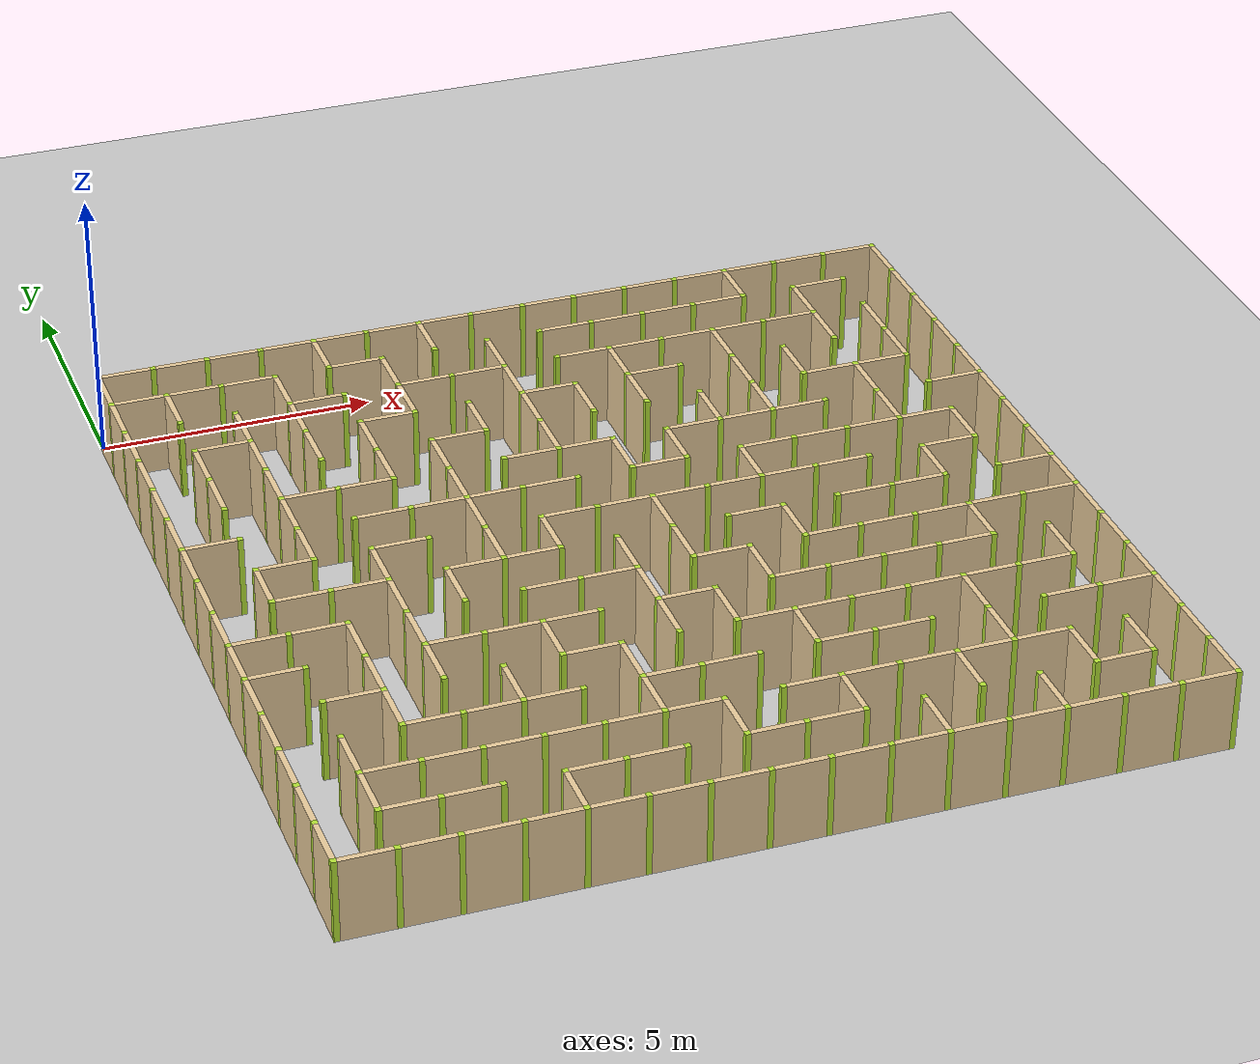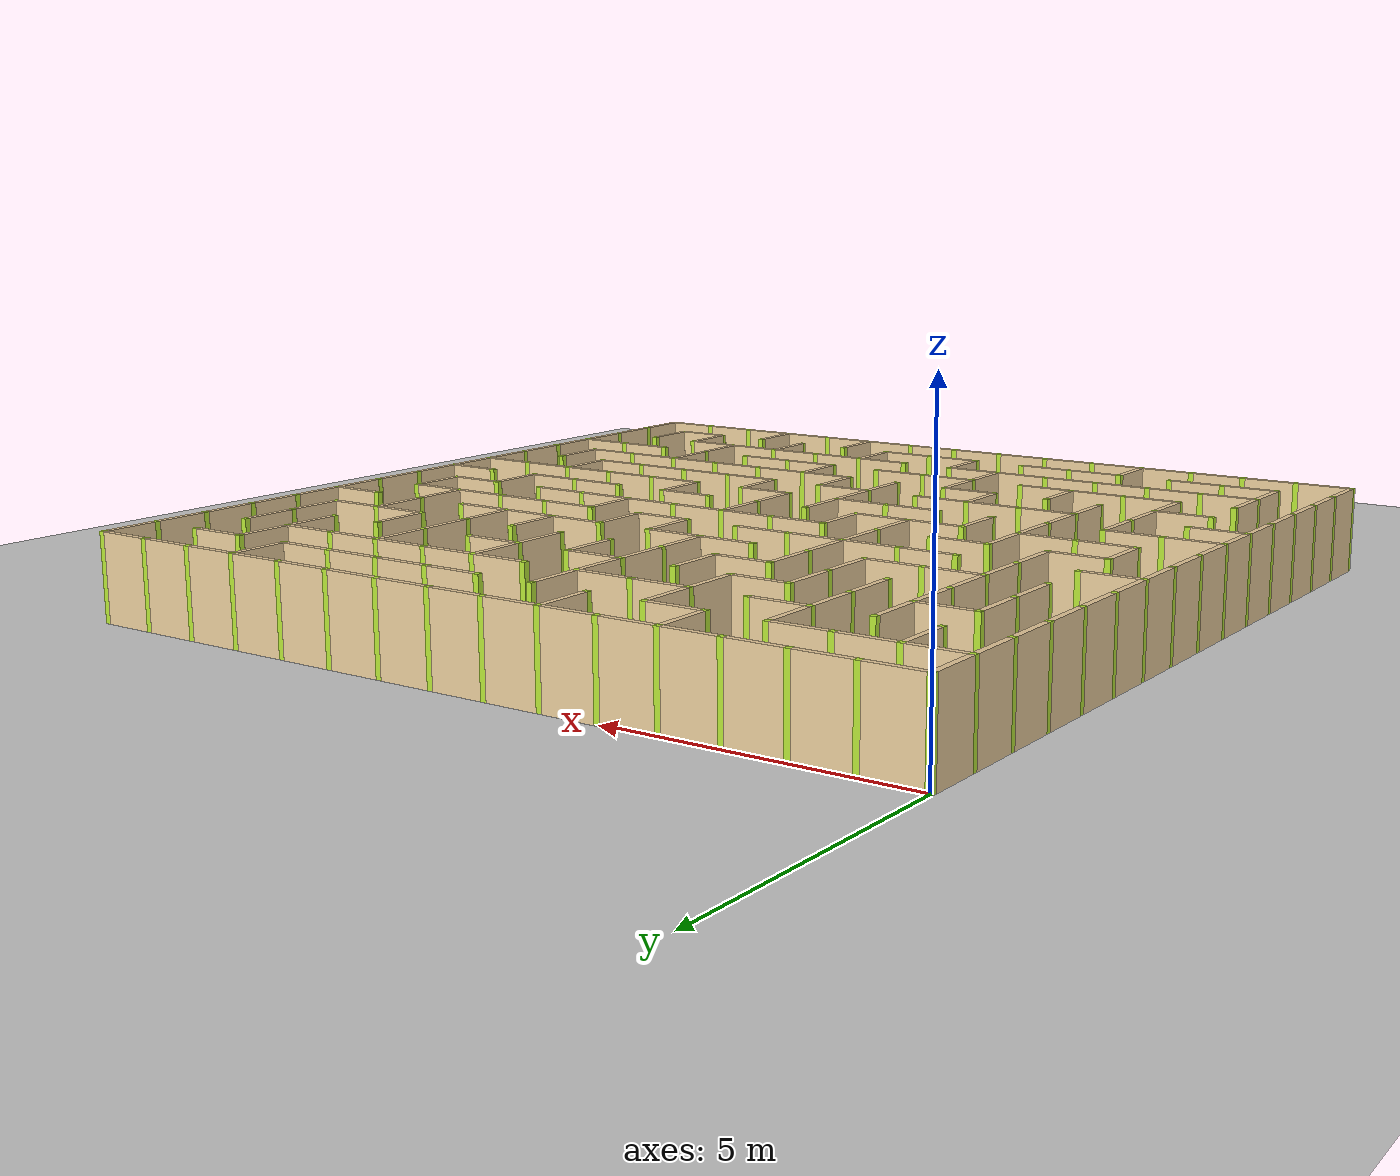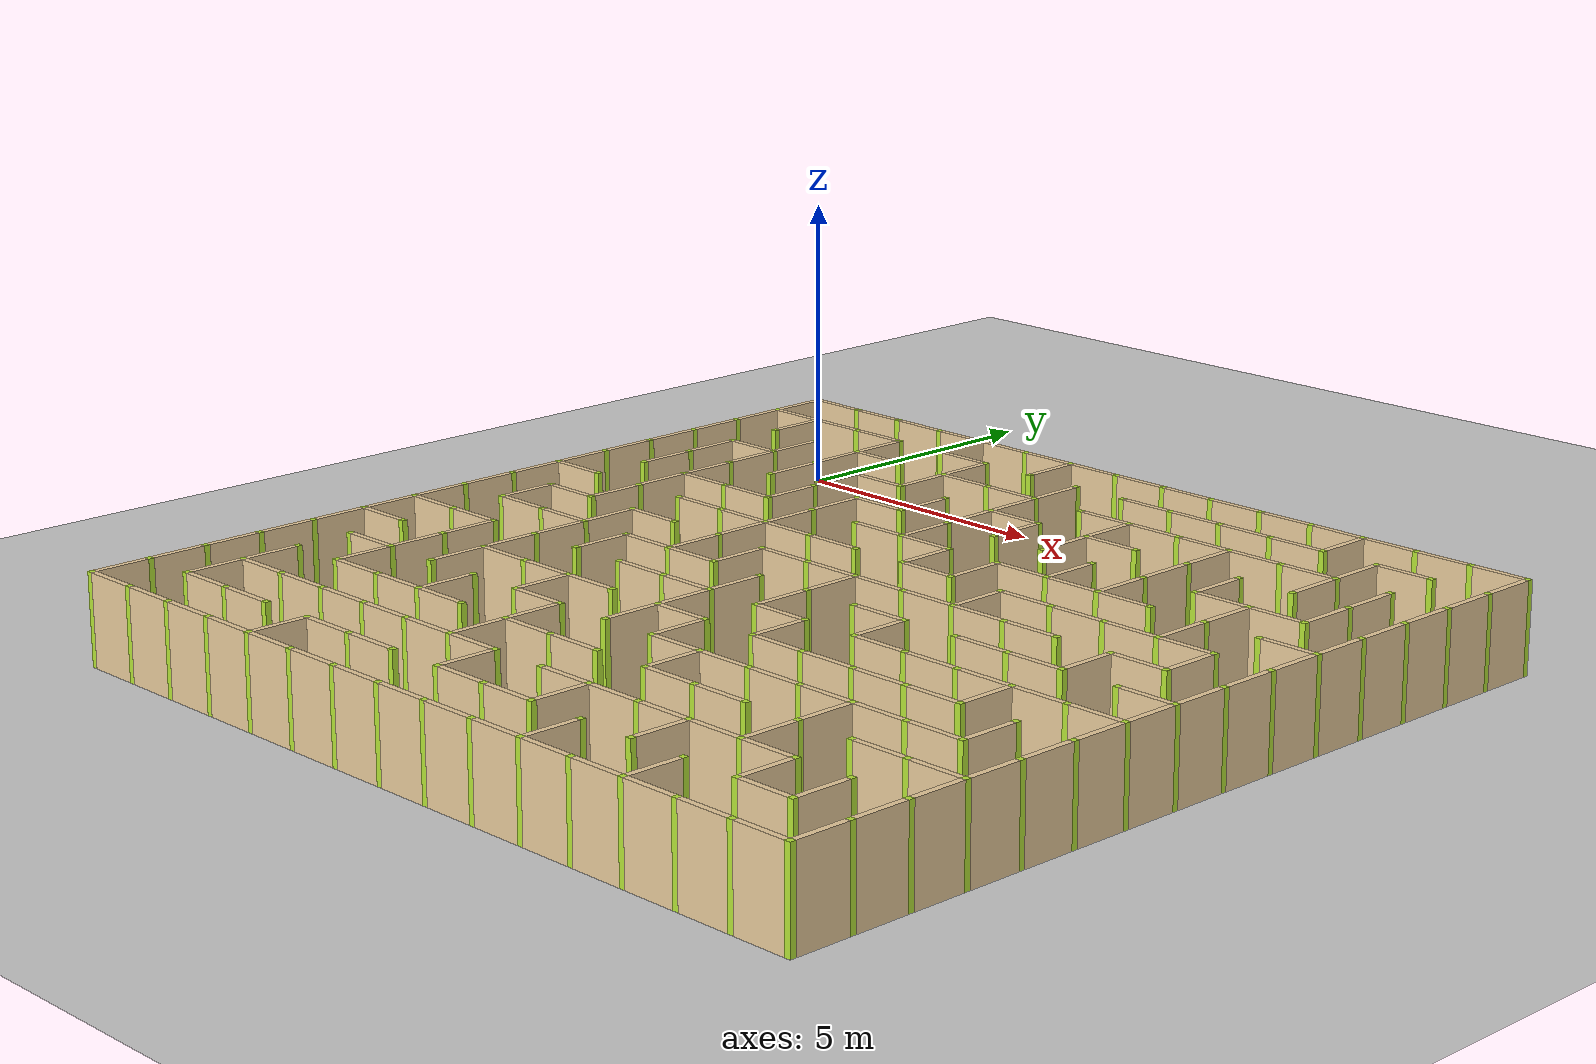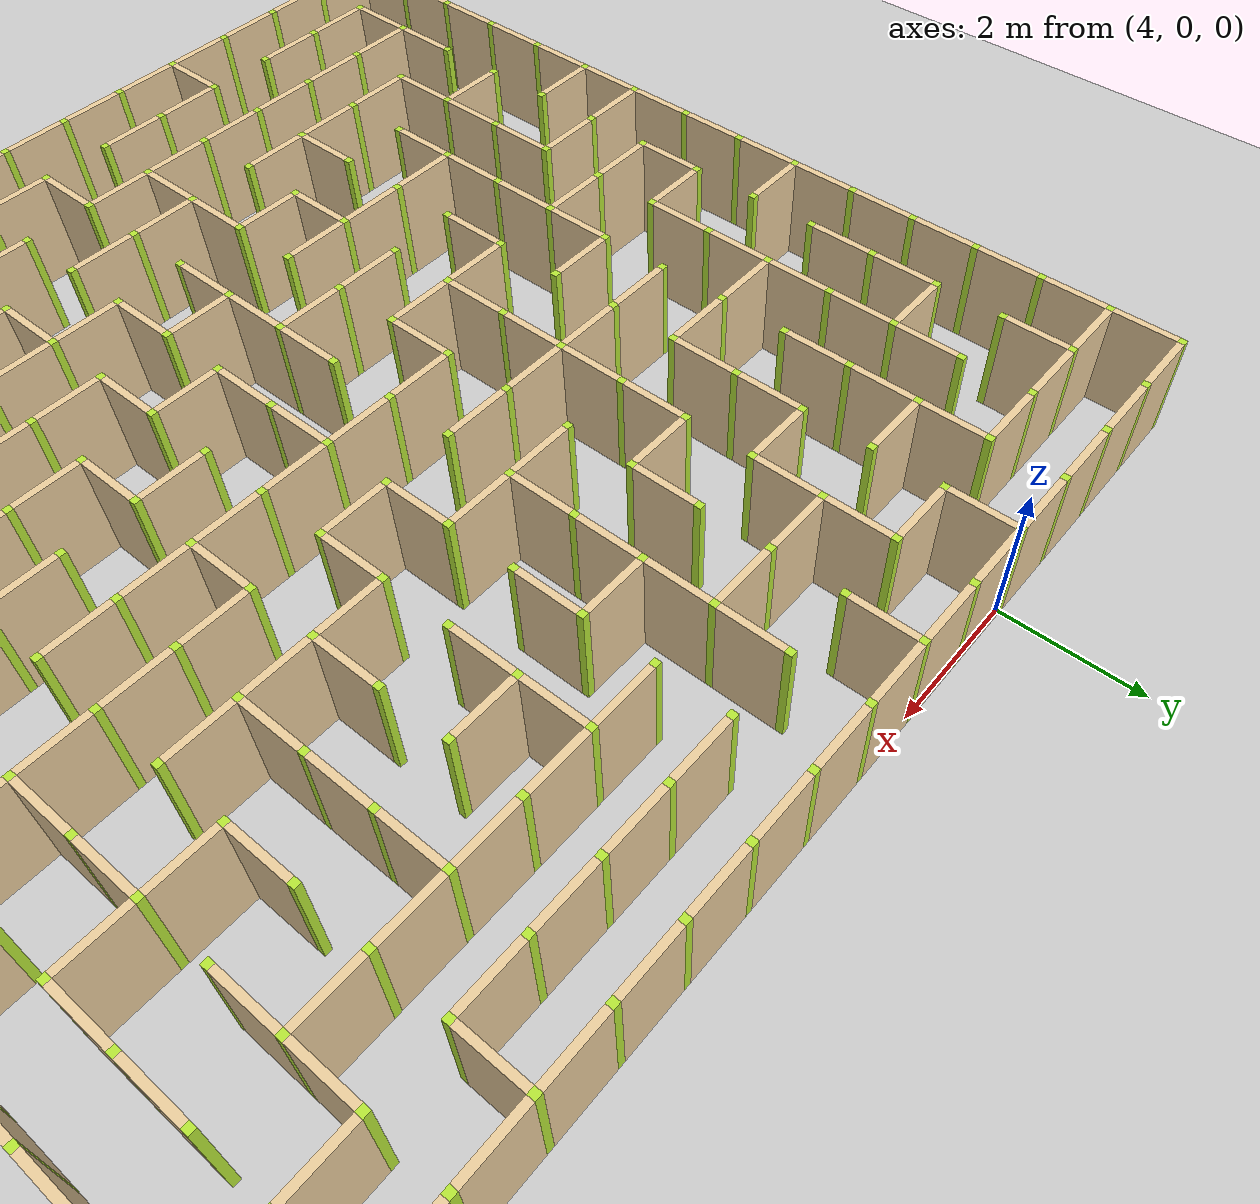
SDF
<sdf version="1.4">
  <world name="maze_world">
    <model name="ground">
      <static>true</static>
      <link name="ground_link">
        <collision name="collision1">
          <geometry>
            <plane>
              <normal>0 0 1</normal>
            </plane>
          </geometry>
        </collision>
        <visual name="visual1">
          <geometry>
            <plane>
              <normal>0 0 1</normal>
              <size>100 100</size>
            </plane>
          </geometry>
        </visual>
      </link>
    </model>
		<model name='Untitled'>
	  <pose>0 0 0 0 -0 0</pose>
        		  <link name='Wall_0_0_h'>
		    <collision name='Wall_0_Collision'>
		      <geometry>
		        <box>
		          <size>0.9 0.1 1.5</size>
		        </box>
		      </geometry>
		      <pose>0 0 0.75 0 -0 0</pose>
		    </collision>
		    <visual name='Wall_0_Visual'>
		      <pose>0 0 0.75 0 -0 0</pose>
		      <geometry>
		        <box>
		          <size>0.9 0.1 1.5</size>
		        </box>
		      </geometry>
		      <material>
		        <script>
		          <uri>file://media/materials/scripts/gazebo.material</uri>
		          <name>Gazebo/Grey</name>
		        </script>
		        <ambient>0.921569 0.807843 0.615686 1</ambient>
		      </material>
		      <meta>
		        <layer>0</layer>
		      </meta>
		    </visual>
		    <pose>0.5 0 0 0 -0 0</pose>
		  </link>
        		  <link name='Wall_0_0_v'>
		    <collision name='Wall_0_Collision'>
		      <geometry>
		        <box>
		          <size>0.9 0.1 1.5</size>
		        </box>
		      </geometry>
		      <pose>0 0 0.75 0 -0 0</pose>
		    </collision>
		    <visual name='Wall_0_Visual'>
		      <pose>0 0 0.75 0 -0 0</pose>
		      <geometry>
		        <box>
		          <size>0.9 0.1 1.5</size>
		        </box>
		      </geometry>
		      <material>
		        <script>
		          <uri>file://media/materials/scripts/gazebo.material</uri>
		          <name>Gazebo/Grey</name>
		        </script>
		        <ambient>0.921569 0.807843 0.615686 1</ambient>
		      </material>
		      <meta>
		        <layer>0</layer>
		      </meta>
		    </visual>
		    <pose>0 -0.5 0 0 -0 1.5708</pose>
		  </link>
        	    <link name='Joint_0_0'>
		    <collision name='Wall_2_Collision'>
		      <geometry>
		        <box>
		          <size>0.1 0.1 1.5</size>
		        </box>
		      </geometry>
		      <pose>0 0 0.75 0 -0 0</pose>
		    </collision>
		    <visual name='Wall_2_Visual'>
		      <pose>0 0 0.75 0 -0 0</pose>
		      <geometry>
		        <box>
		          <size>0.1 0.1 1.5</size>
		        </box>
		      </geometry>
		      <material>
		        <script>
		          <uri>file://media/materials/scripts/gazebo.material</uri>
		          <name>Gazebo/Grey</name>
		        </script>
		        <ambient>0.721569 0.907843 0.215686 1</ambient>
		      </material>
		      <meta>
		        <layer>0</layer>
		      </meta>
		    </visual>
		    <pose>0 0 0 0 -0 0</pose>
		  </link>
        		  <link name='Wall_1_0_h'>
		    <collision name='Wall_0_Collision'>
		      <geometry>
		        <box>
		          <size>0.9 0.1 1.5</size>
		        </box>
		      </geometry>
		      <pose>0 0 0.75 0 -0 0</pose>
		    </collision>
		    <visual name='Wall_0_Visual'>
		      <pose>0 0 0.75 0 -0 0</pose>
		      <geometry>
		        <box>
		          <size>0.9 0.1 1.5</size>
		        </box>
		      </geometry>
		      <material>
		        <script>
		          <uri>file://media/materials/scripts/gazebo.material</uri>
		          <name>Gazebo/Grey</name>
		        </script>
		        <ambient>0.921569 0.807843 0.615686 1</ambient>
		      </material>
		      <meta>
		        <layer>0</layer>
		      </meta>
		    </visual>
		    <pose>1.5 0 0 0 -0 0</pose>
		  </link>
        	    <link name='Joint_1_0'>
		    <collision name='Wall_2_Collision'>
		      <geometry>
		        <box>
		          <size>0.1 0.1 1.5</size>
		        </box>
		      </geometry>
		      <pose>0 0 0.75 0 -0 0</pose>
		    </collision>
		    <visual name='Wall_2_Visual'>
		      <pose>0 0 0.75 0 -0 0</pose>
		      <geometry>
		        <box>
		          <size>0.1 0.1 1.5</size>
		        </box>
		      </geometry>
		      <material>
		        <script>
		          <uri>file://media/materials/scripts/gazebo.material</uri>
		          <name>Gazebo/Grey</name>
		        </script>
		        <ambient>0.721569 0.907843 0.215686 1</ambient>
		      </material>
		      <meta>
		        <layer>0</layer>
		      </meta>
		    </visual>
		    <pose>1 0 0 0 -0 0</pose>
		  </link>
        		  <link name='Wall_2_0_h'>
		    <collision name='Wall_0_Collision'>
		      <geometry>
		        <box>
		          <size>0.9 0.1 1.5</size>
		        </box>
		      </geometry>
		      <pose>0 0 0.75 0 -0 0</pose>
		    </collision>
		    <visual name='Wall_0_Visual'>
		      <pose>0 0 0.75 0 -0 0</pose>
		      <geometry>
		        <box>
		          <size>0.9 0.1 1.5</size>
		        </box>
		      </geometry>
		      <material>
		        <script>
		          <uri>file://media/materials/scripts/gazebo.material</uri>
		          <name>Gazebo/Grey</name>
		        </script>
		        <ambient>0.921569 0.807843 0.615686 1</ambient>
		      </material>
		      <meta>
		        <layer>0</layer>
		      </meta>
		    </visual>
		    <pose>2.5 0 0 0 -0 0</pose>
		  </link>
        	    <link name='Joint_2_0'>
		    <collision name='Wall_2_Collision'>
		      <geometry>
		        <box>
		          <size>0.1 0.1 1.5</size>
		        </box>
		      </geometry>
		      <pose>0 0 0.75 0 -0 0</pose>
		    </collision>
		    <visual name='Wall_2_Visual'>
		      <pose>0 0 0.75 0 -0 0</pose>
		      <geometry>
		        <box>
		          <size>0.1 0.1 1.5</size>
		        </box>
		      </geometry>
		      <material>
		        <script>
		          <uri>file://media/materials/scripts/gazebo.material</uri>
		          <name>Gazebo/Grey</name>
		        </script>
		        <ambient>0.721569 0.907843 0.215686 1</ambient>
		      </material>
		      <meta>
		        <layer>0</layer>
		      </meta>
		    </visual>
		    <pose>2 0 0 0 -0 0</pose>
		  </link>
        		  <link name='Wall_3_0_h'>
		    <collision name='Wall_0_Collision'>
		      <geometry>
		        <box>
		          <size>0.9 0.1 1.5</size>
		        </box>
		      </geometry>
		      <pose>0 0 0.75 0 -0 0</pose>
		    </collision>
		    <visual name='Wall_0_Visual'>
		      <pose>0 0 0.75 0 -0 0</pose>
		      <geometry>
		        <box>
		          <size>0.9 0.1 1.5</size>
		        </box>
		      </geometry>
		      <material>
		        <script>
		          <uri>file://media/materials/scripts/gazebo.material</uri>
		          <name>Gazebo/Grey</name>
		        </script>
		        <ambient>0.921569 0.807843 0.615686 1</ambient>
		      </material>
		      <meta>
		        <layer>0</layer>
		      </meta>
		    </visual>
		    <pose>3.5 0 0 0 -0 0</pose>
		  </link>
        	    <link name='Joint_3_0'>
		    <collision name='Wall_2_Collision'>
		      <geometry>
		        <box>
		          <size>0.1 0.1 1.5</size>
		        </box>
		      </geometry>
		      <pose>0 0 0.75 0 -0 0</pose>
		    </collision>
		    <visual name='Wall_2_Visual'>
		      <pose>0 0 0.75 0 -0 0</pose>
		      <geometry>
		        <box>
		          <size>0.1 0.1 1.5</size>
		        </box>
		      </geometry>
		      <material>
		        <script>
		          <uri>file://media/materials/scripts/gazebo.material</uri>
		          <name>Gazebo/Grey</name>
		        </script>
		        <ambient>0.721569 0.907843 0.215686 1</ambient>
		      </material>
		      <meta>
		        <layer>0</layer>
		      </meta>
		    </visual>
		    <pose>3 0 0 0 -0 0</pose>
		  </link>
        		  <link name='Wall_4_0_h'>
		    <collision name='Wall_0_Collision'>
		      <geometry>
		        <box>
		          <size>0.9 0.1 1.5</size>
		        </box>
		      </geometry>
		      <pose>0 0 0.75 0 -0 0</pose>
		    </collision>
		    <visual name='Wall_0_Visual'>
		      <pose>0 0 0.75 0 -0 0</pose>
		      <geometry>
		        <box>
		          <size>0.9 0.1 1.5</size>
		        </box>
		      </geometry>
		      <material>
		        <script>
		          <uri>file://media/materials/scripts/gazebo.material</uri>
		          <name>Gazebo/Grey</name>
		        </script>
		        <ambient>0.921569 0.807843 0.615686 1</ambient>
		      </material>
		      <meta>
		        <layer>0</layer>
		      </meta>
		    </visual>
		    <pose>4.5 0 0 0 -0 0</pose>
		  </link>
        		  <link name='Wall_4_0_v'>
		    <collision name='Wall_0_Collision'>
		      <geometry>
		        <box>
		          <size>0.9 0.1 1.5</size>
		        </box>
		      </geometry>
		      <pose>0 0 0.75 0 -0 0</pose>
		    </collision>
		    <visual name='Wall_0_Visual'>
		      <pose>0 0 0.75 0 -0 0</pose>
		      <geometry>
		        <box>
		          <size>0.9 0.1 1.5</size>
		        </box>
		      </geometry>
		      <material>
		        <script>
		          <uri>file://media/materials/scripts/gazebo.material</uri>
		          <name>Gazebo/Grey</name>
		        </script>
		        <ambient>0.921569 0.807843 0.615686 1</ambient>
		      </material>
		      <meta>
		        <layer>0</layer>
		      </meta>
		    </visual>
		    <pose>4 -0.5 0 0 -0 1.5708</pose>
		  </link>
        	    <link name='Joint_4_0'>
		    <collision name='Wall_2_Collision'>
		      <geometry>
		        <box>
		          <size>0.1 0.1 1.5</size>
		        </box>
		      </geometry>
		      <pose>0 0 0.75 0 -0 0</pose>
		    </collision>
		    <visual name='Wall_2_Visual'>
		      <pose>0 0 0.75 0 -0 0</pose>
		      <geometry>
		        <box>
		          <size>0.1 0.1 1.5</size>
		        </box>
		      </geometry>
		      <material>
		        <script>
		          <uri>file://media/materials/scripts/gazebo.material</uri>
		          <name>Gazebo/Grey</name>
		        </script>
		        <ambient>0.721569 0.907843 0.215686 1</ambient>
		      </material>
		      <meta>
		        <layer>0</layer>
		      </meta>
		    </visual>
		    <pose>4 0 0 0 -0 0</pose>
		  </link>
        		  <link name='Wall_5_0_h'>
		    <collision name='Wall_0_Collision'>
		      <geometry>
		        <box>
		          <size>0.9 0.1 1.5</size>
		        </box>
		      </geometry>
		      <pose>0 0 0.75 0 -0 0</pose>
		    </collision>
		    <visual name='Wall_0_Visual'>
		      <pose>0 0 0.75 0 -0 0</pose>
		      <geometry>
		        <box>
		          <size>0.9 0.1 1.5</size>
		        </box>
		      </geometry>
		      <material>
		        <script>
		          <uri>file://media/materials/scripts/gazebo.material</uri>
		          <name>Gazebo/Grey</name>
		        </script>
		        <ambient>0.921569 0.807843 0.615686 1</ambient>
		      </material>
		      <meta>
		        <layer>0</layer>
		      </meta>
		    </visual>
		    <pose>5.5 0 0 0 -0 0</pose>
		  </link>
        	    <link name='Joint_5_0'>
		    <collision name='Wall_2_Collision'>
		      <geometry>
		        <box>
		          <size>0.1 0.1 1.5</size>
		        </box>
		      </geometry>
		      <pose>0 0 0.75 0 -0 0</pose>
		    </collision>
		    <visual name='Wall_2_Visual'>
		      <pose>0 0 0.75 0 -0 0</pose>
		      <geometry>
		        <box>
		          <size>0.1 0.1 1.5</size>
		        </box>
		      </geometry>
		      <material>
		        <script>
		          <uri>file://media/materials/scripts/gazebo.material</uri>
		          <name>Gazebo/Grey</name>
		        </script>
		        <ambient>0.721569 0.907843 0.215686 1</ambient>
		      </material>
		      <meta>
		        <layer>0</layer>
		      </meta>
		    </visual>
		    <pose>5 0 0 0 -0 0</pose>
		  </link>
        		  <link name='Wall_6_0_h'>
		    <collision name='Wall_0_Collision'>
		      <geometry>
		        <box>
		          <size>0.9 0.1 1.5</size>
		        </box>
		      </geometry>
		      <pose>0 0 0.75 0 -0 0</pose>
		    </collision>
		    <visual name='Wall_0_Visual'>
		      <pose>0 0 0.75 0 -0 0</pose>
		      <geometry>
		        <box>
		          <size>0.9 0.1 1.5</size>
		        </box>
		      </geometry>
		      <material>
		        <script>
		          <uri>file://media/materials/scripts/gazebo.material</uri>
		          <name>Gazebo/Grey</name>
		        </script>
		        <ambient>0.921569 0.807843 0.615686 1</ambient>
		      </material>
		      <meta>
		        <layer>0</layer>
		      </meta>
		    </visual>
		    <pose>6.5 0 0 0 -0 0</pose>
		  </link>
        		  <link name='Wall_6_0_v'>
		    <collision name='Wall_0_Collision'>
		      <geometry>
		        <box>
		          <size>0.9 0.1 1.5</size>
		        </box>
		      </geometry>
		      <pose>0 0 0.75 0 -0 0</pose>
		    </collision>
		    <visual name='Wall_0_Visual'>
		      <pose>0 0 0.75 0 -0 0</pose>
		      <geometry>
		        <box>
		          <size>0.9 0.1 1.5</size>
		        </box>
		      </geometry>
		      <material>
		        <script>
		          <uri>file://media/materials/scripts/gazebo.material</uri>
		          <name>Gazebo/Grey</name>
		        </script>
		        <ambient>0.921569 0.807843 0.615686 1</ambient>
		      </material>
		      <meta>
		        <layer>0</layer>
		      </meta>
		    </visual>
		    <pose>6 -0.5 0 0 -0 1.5708</pose>
		  </link>
        	    <link name='Joint_6_0'>
		    <collision name='Wall_2_Collision'>
		      <geometry>
		        <box>
		          <size>0.1 0.1 1.5</size>
		        </box>
		      </geometry>
		      <pose>0 0 0.75 0 -0 0</pose>
		    </collision>
		    <visual name='Wall_2_Visual'>
		      <pose>0 0 0.75 0 -0 0</pose>
		      <geometry>
		        <box>
		          <size>0.1 0.1 1.5</size>
		        </box>
		      </geometry>
		      <material>
		        <script>
		          <uri>file://media/materials/scripts/gazebo.material</uri>
		          <name>Gazebo/Grey</name>
		        </script>
		        <ambient>0.721569 0.907843 0.215686 1</ambient>
		      </material>
		      <meta>
		        <layer>0</layer>
		      </meta>
		    </visual>
		    <pose>6 0 0 0 -0 0</pose>
		  </link>
        		  <link name='Wall_7_0_h'>
		    <collision name='Wall_0_Collision'>
		      <geometry>
		        <box>
		          <size>0.9 0.1 1.5</size>
		        </box>
		      </geometry>
		      <pose>0 0 0.75 0 -0 0</pose>
		    </collision>
		    <visual name='Wall_0_Visual'>
		      <pose>0 0 0.75 0 -0 0</pose>
		      <geometry>
		        <box>
		          <size>0.9 0.1 1.5</size>
		        </box>
		      </geometry>
		      <material>
		        <script>
		          <uri>file://media/materials/scripts/gazebo.material</uri>
		          <name>Gazebo/Grey</name>
		        </script>
		        <ambient>0.921569 0.807843 0.615686 1</ambient>
		      </material>
		      <meta>
		        <layer>0</layer>
		      </meta>
		    </visual>
		    <pose>7.5 0 0 0 -0 0</pose>
		  </link>
        	    <link name='Joint_7_0'>
		    <collision name='Wall_2_Collision'>
		      <geometry>
		        <box>
		          <size>0.1 0.1 1.5</size>
		        </box>
		      </geometry>
		      <pose>0 0 0.75 0 -0 0</pose>
		    </collision>
		    <visual name='Wall_2_Visual'>
		      <pose>0 0 0.75 0 -0 0</pose>
		      <geometry>
		        <box>
		          <size>0.1 0.1 1.5</size>
		        </box>
		      </geometry>
		      <material>
		        <script>
		          <uri>file://media/materials/scripts/gazebo.material</uri>
		          <name>Gazebo/Grey</name>
		        </script>
		        <ambient>0.721569 0.907843 0.215686 1</ambient>
		      </material>
		      <meta>
		        <layer>0</layer>
		      </meta>
		    </visual>
		    <pose>7 0 0 0 -0 0</pose>
		  </link>
        		  <link name='Wall_8_0_h'>
		    <collision name='Wall_0_Collision'>
		      <geometry>
		        <box>
		          <size>0.9 0.1 1.5</size>
		        </box>
		      </geometry>
		      <pose>0 0 0.75 0 -0 0</pose>
		    </collision>
		    <visual name='Wall_0_Visual'>
		      <pose>0 0 0.75 0 -0 0</pose>
		      <geometry>
		        <box>
		          <size>0.9 0.1 1.5</size>
		        </box>
		      </geometry>
		      <material>
		        <script>
		          <uri>file://media/materials/scripts/gazebo.material</uri>
		          <name>Gazebo/Grey</name>
		        </script>
		        <ambient>0.921569 0.807843 0.615686 1</ambient>
		      </material>
		      <meta>
		        <layer>0</layer>
		      </meta>
		    </visual>
		    <pose>8.5 0 0 0 -0 0</pose>
		  </link>
        	    <link name='Joint_8_0'>
		    <collision name='Wall_2_Collision'>
		      <geometry>
		        <box>
		          <size>0.1 0.1 1.5</size>
		        </box>
		      </geometry>
		      <pose>0 0 0.75 0 -0 0</pose>
		    </collision>
		    <visual name='Wall_2_Visual'>
		      <pose>0 0 0.75 0 -0 0</pose>
		      <geometry>
		        <box>
		          <size>0.1 0.1 1.5</size>
		        </box>
		      </geometry>
		      <material>
		        <script>
		          <uri>file://media/materials/scripts/gazebo.material</uri>
		          <name>Gazebo/Grey</name>
		        </script>
		        <ambient>0.721569 0.907843 0.215686 1</ambient>
		      </material>
		      <meta>
		        <layer>0</layer>
		      </meta>
		    </visual>
		    <pose>8 0 0 0 -0 0</pose>
		  </link>
        		  <link name='Wall_9_0_h'>
		    <collision name='Wall_0_Collision'>
		      <geometry>
		        <box>
		          <size>0.9 0.1 1.5</size>
		        </box>
		      </geometry>
		      <pose>0 0 0.75 0 -0 0</pose>
		    </collision>
		    <visual name='Wall_0_Visual'>
		      <pose>0 0 0.75 0 -0 0</pose>
		      <geometry>
		        <box>
		          <size>0.9 0.1 1.5</size>
		        </box>
		      </geometry>
		      <material>
		        <script>
		          <uri>file://media/materials/scripts/gazebo.material</uri>
		          <name>Gazebo/Grey</name>
		        </script>
		        <ambient>0.921569 0.807843 0.615686 1</ambient>
		      </material>
		      <meta>
		        <layer>0</layer>
		      </meta>
		    </visual>
		    <pose>9.5 0 0 0 -0 0</pose>
		  </link>
        	    <link name='Joint_9_0'>
		    <collision name='Wall_2_Collision'>
		      <geometry>
		        <box>
		          <size>0.1 0.1 1.5</size>
		        </box>
		      </geometry>
		      <pose>0 0 0.75 0 -0 0</pose>
		    </collision>
		    <visual name='Wall_2_Visual'>
		      <pose>0 0 0.75 0 -0 0</pose>
		      <geometry>
		        <box>
		          <size>0.1 0.1 1.5</size>
		        </box>
		      </geometry>
		      <material>
		        <script>
		          <uri>file://media/materials/scripts/gazebo.material</uri>
		          <name>Gazebo/Grey</name>
		        </script>
		        <ambient>0.721569 0.907843 0.215686 1</ambient>
		      </material>
		      <meta>
		        <layer>0</layer>
		      </meta>
		    </visual>
		    <pose>9 0 0 0 -0 0</pose>
		  </link>
        		  <link name='Wall_10_0_h'>
		    <collision name='Wall_0_Collision'>
		      <geometry>
		        <box>
		          <size>0.9 0.1 1.5</size>
		        </box>
		      </geometry>
		      <pose>0 0 0.75 0 -0 0</pose>
		    </collision>
		    <visual name='Wall_0_Visual'>
		      <pose>0 0 0.75 0 -0 0</pose>
		      <geometry>
		        <box>
		          <size>0.9 0.1 1.5</size>
		        </box>
		      </geometry>
		      <material>
		        <script>
		          <uri>file://media/materials/scripts/gazebo.material</uri>
		          <name>Gazebo/Grey</name>
		        </script>
		        <ambient>0.921569 0.807843 0.615686 1</ambient>
		      </material>
		      <meta>
		        <layer>0</layer>
		      </meta>
		    </visual>
		    <pose>10.5 0 0 0 -0 0</pose>
		  </link>
        	    <link name='Joint_10_0'>
		    <collision name='Wall_2_Collision'>
		      <geometry>
		        <box>
		          <size>0.1 0.1 1.5</size>
		        </box>
		      </geometry>
		      <pose>0 0 0.75 0 -0 0</pose>
		    </collision>
		    <visual name='Wall_2_Visual'>
		      <pose>0 0 0.75 0 -0 0</pose>
		      <geometry>
		        <box>
		          <size>0.1 0.1 1.5</size>
		        </box>
		      </geometry>
		      <material>
		        <script>
		          <uri>file://media/materials/scripts/gazebo.material</uri>
		          <name>Gazebo/Grey</name>
		        </script>
		        <ambient>0.721569 0.907843 0.215686 1</ambient>
		      </material>
		      <meta>
		        <layer>0</layer>
		      </meta>
		    </visual>
		    <pose>10 0 0 0 -0 0</pose>
		  </link>
        		  <link name='Wall_11_0_h'>
		    <collision name='Wall_0_Collision'>
		      <geometry>
		        <box>
		          <size>0.9 0.1 1.5</size>
		        </box>
		      </geometry>
		      <pose>0 0 0.75 0 -0 0</pose>
		    </collision>
		    <visual name='Wall_0_Visual'>
		      <pose>0 0 0.75 0 -0 0</pose>
		      <geometry>
		        <box>
		          <size>0.9 0.1 1.5</size>
		        </box>
		      </geometry>
		      <material>
		        <script>
		          <uri>file://media/materials/scripts/gazebo.material</uri>
		          <name>Gazebo/Grey</name>
		        </script>
		        <ambient>0.921569 0.807843 0.615686 1</ambient>
		      </material>
		      <meta>
		        <layer>0</layer>
		      </meta>
		    </visual>
		    <pose>11.5 0 0 0 -0 0</pose>
		  </link>
        	    <link name='Joint_11_0'>
		    <collision name='Wall_2_Collision'>
		      <geometry>
		        <box>
		          <size>0.1 0.1 1.5</size>
		        </box>
		      </geometry>
		      <pose>0 0 0.75 0 -0 0</pose>
		    </collision>
		    <visual name='Wall_2_Visual'>
		      <pose>0 0 0.75 0 -0 0</pose>
		      <geometry>
		        <box>
		          <size>0.1 0.1 1.5</size>
		        </box>
		      </geometry>
		      <material>
		        <script>
		          <uri>file://media/materials/scripts/gazebo.material</uri>
		          <name>Gazebo/Grey</name>
		        </script>
		        <ambient>0.721569 0.907843 0.215686 1</ambient>
		      </material>
		      <meta>
		        <layer>0</layer>
		      </meta>
		    </visual>
		    <pose>11 0 0 0 -0 0</pose>
		  </link>
        		  <link name='Wall_12_0_h'>
		    <collision name='Wall_0_Collision'>
		      <geometry>
		        <box>
		          <size>0.9 0.1 1.5</size>
		        </box>
		      </geometry>
		      <pose>0 0 0.75 0 -0 0</pose>
		    </collision>
		    <visual name='Wall_0_Visual'>
		      <pose>0 0 0.75 0 -0 0</pose>
		      <geometry>
		        <box>
		          <size>0.9 0.1 1.5</size>
		        </box>
		      </geometry>
		      <material>
		        <script>
		          <uri>file://media/materials/scripts/gazebo.material</uri>
		          <name>Gazebo/Grey</name>
		        </script>
		        <ambient>0.921569 0.807843 0.615686 1</ambient>
		      </material>
		      <meta>
		        <layer>0</layer>
		      </meta>
		    </visual>
		    <pose>12.5 0 0 0 -0 0</pose>
		  </link>
        		  <link name='Wall_12_0_v'>
		    <collision name='Wall_0_Collision'>
		      <geometry>
		        <box>
		          <size>0.9 0.1 1.5</size>
		        </box>
		      </geometry>
		      <pose>0 0 0.75 0 -0 0</pose>
		    </collision>
		    <visual name='Wall_0_Visual'>
		      <pose>0 0 0.75 0 -0 0</pose>
		      <geometry>
		        <box>
		          <size>0.9 0.1 1.5</size>
		        </box>
		      </geometry>
		      <material>
		        <script>
		          <uri>file://media/materials/scripts/gazebo.material</uri>
		          <name>Gazebo/Grey</name>
		        </script>
		        <ambient>0.921569 0.807843 0.615686 1</ambient>
		      </material>
		      <meta>
		        <layer>0</layer>
		      </meta>
		    </visual>
		    <pose>12 -0.5 0 0 -0 1.5708</pose>
		  </link>
        	    <link name='Joint_12_0'>
		    <collision name='Wall_2_Collision'>
		      <geometry>
		        <box>
		          <size>0.1 0.1 1.5</size>
		        </box>
		      </geometry>
		      <pose>0 0 0.75 0 -0 0</pose>
		    </collision>
		    <visual name='Wall_2_Visual'>
		      <pose>0 0 0.75 0 -0 0</pose>
		      <geometry>
		        <box>
		          <size>0.1 0.1 1.5</size>
		        </box>
		      </geometry>
		      <material>
		        <script>
		          <uri>file://media/materials/scripts/gazebo.material</uri>
		          <name>Gazebo/Grey</name>
		        </script>
		        <ambient>0.721569 0.907843 0.215686 1</ambient>
		      </material>
		      <meta>
		        <layer>0</layer>
		      </meta>
		    </visual>
		    <pose>12 0 0 0 -0 0</pose>
		  </link>
        		  <link name='Wall_13_0_h'>
		    <collision name='Wall_0_Collision'>
		      <geometry>
		        <box>
		          <size>0.9 0.1 1.5</size>
		        </box>
		      </geometry>
		      <pose>0 0 0.75 0 -0 0</pose>
		    </collision>
		    <visual name='Wall_0_Visual'>
		      <pose>0 0 0.75 0 -0 0</pose>
		      <geometry>
		        <box>
		          <size>0.9 0.1 1.5</size>
		        </box>
		      </geometry>
		      <material>
		        <script>
		          <uri>file://media/materials/scripts/gazebo.material</uri>
		          <name>Gazebo/Grey</name>
		        </script>
		        <ambient>0.921569 0.807843 0.615686 1</ambient>
		      </material>
		      <meta>
		        <layer>0</layer>
		      </meta>
		    </visual>
		    <pose>13.5 0 0 0 -0 0</pose>
		  </link>
        	    <link name='Joint_13_0'>
		    <collision name='Wall_2_Collision'>
		      <geometry>
		        <box>
		          <size>0.1 0.1 1.5</size>
		        </box>
		      </geometry>
		      <pose>0 0 0.75 0 -0 0</pose>
		    </collision>
		    <visual name='Wall_2_Visual'>
		      <pose>0 0 0.75 0 -0 0</pose>
		      <geometry>
		        <box>
		          <size>0.1 0.1 1.5</size>
		        </box>
		      </geometry>
		      <material>
		        <script>
		          <uri>file://media/materials/scripts/gazebo.material</uri>
		          <name>Gazebo/Grey</name>
		        </script>
		        <ambient>0.721569 0.907843 0.215686 1</ambient>
		      </material>
		      <meta>
		        <layer>0</layer>
		      </meta>
		    </visual>
		    <pose>13 0 0 0 -0 0</pose>
		  </link>
        		  <link name='Wall_14_0_h'>
		    <collision name='Wall_0_Collision'>
		      <geometry>
		        <box>
		          <size>0.9 0.1 1.5</size>
		        </box>
		      </geometry>
		      <pose>0 0 0.75 0 -0 0</pose>
		    </collision>
		    <visual name='Wall_0_Visual'>
		      <pose>0 0 0.75 0 -0 0</pose>
		      <geometry>
		        <box>
		          <size>0.9 0.1 1.5</size>
		        </box>
		      </geometry>
		      <material>
		        <script>
		          <uri>file://media/materials/scripts/gazebo.material</uri>
		          <name>Gazebo/Grey</name>
		        </script>
		        <ambient>0.921569 0.807843 0.615686 1</ambient>
		      </material>
		      <meta>
		        <layer>0</layer>
		      </meta>
		    </visual>
		    <pose>14.5 0 0 0 -0 0</pose>
		  </link>
        	    <link name='Joint_14_0'>
		    <collision name='Wall_2_Collision'>
		      <geometry>
		        <box>
		          <size>0.1 0.1 1.5</size>
		        </box>
		      </geometry>
		      <pose>0 0 0.75 0 -0 0</pose>
		    </collision>
		    <visual name='Wall_2_Visual'>
		      <pose>0 0 0.75 0 -0 0</pose>
		      <geometry>
		        <box>
		          <size>0.1 0.1 1.5</size>
		        </box>
		      </geometry>
		      <material>
		        <script>
		          <uri>file://media/materials/scripts/gazebo.material</uri>
		          <name>Gazebo/Grey</name>
		        </script>
		        <ambient>0.721569 0.907843 0.215686 1</ambient>
		      </material>
		      <meta>
		        <layer>0</layer>
		      </meta>
		    </visual>
		    <pose>14 0 0 0 -0 0</pose>
		  </link>
        		  <link name='Wall_15_0_v'>
		    <collision name='Wall_0_Collision'>
		      <geometry>
		        <box>
		          <size>0.9 0.1 1.5</size>
		        </box>
		      </geometry>
		      <pose>0 0 0.75 0 -0 0</pose>
		    </collision>
		    <visual name='Wall_0_Visual'>
		      <pose>0 0 0.75 0 -0 0</pose>
		      <geometry>
		        <box>
		          <size>0.9 0.1 1.5</size>
		        </box>
		      </geometry>
		      <material>
		        <script>
		          <uri>file://media/materials/scripts/gazebo.material</uri>
		          <name>Gazebo/Grey</name>
		        </script>
		        <ambient>0.921569 0.807843 0.615686 1</ambient>
		      </material>
		      <meta>
		        <layer>0</layer>
		      </meta>
		    </visual>
		    <pose>15 -0.5 0 0 -0 1.5708</pose>
		  </link>
        	    <link name='Joint_15_0'>
		    <collision name='Wall_2_Collision'>
		      <geometry>
		        <box>
		          <size>0.1 0.1 1.5</size>
		        </box>
		      </geometry>
		      <pose>0 0 0.75 0 -0 0</pose>
		    </collision>
		    <visual name='Wall_2_Visual'>
		      <pose>0 0 0.75 0 -0 0</pose>
		      <geometry>
		        <box>
		          <size>0.1 0.1 1.5</size>
		        </box>
		      </geometry>
		      <material>
		        <script>
		          <uri>file://media/materials/scripts/gazebo.material</uri>
		          <name>Gazebo/Grey</name>
		        </script>
		        <ambient>0.721569 0.907843 0.215686 1</ambient>
		      </material>
		      <meta>
		        <layer>0</layer>
		      </meta>
		    </visual>
		    <pose>15 0 0 0 -0 0</pose>
		  </link>
        		  <link name='Wall_0_1_h'>
		    <collision name='Wall_0_Collision'>
		      <geometry>
		        <box>
		          <size>0.9 0.1 1.5</size>
		        </box>
		      </geometry>
		      <pose>0 0 0.75 0 -0 0</pose>
		    </collision>
		    <visual name='Wall_0_Visual'>
		      <pose>0 0 0.75 0 -0 0</pose>
		      <geometry>
		        <box>
		          <size>0.9 0.1 1.5</size>
		        </box>
		      </geometry>
		      <material>
		        <script>
		          <uri>file://media/materials/scripts/gazebo.material</uri>
		          <name>Gazebo/Grey</name>
		        </script>
		        <ambient>0.921569 0.807843 0.615686 1</ambient>
		      </material>
		      <meta>
		        <layer>0</layer>
		      </meta>
		    </visual>
		    <pose>0.5 -1 0 0 -0 0</pose>
		  </link>
        		  <link name='Wall_0_1_v'>
		    <collision name='Wall_0_Collision'>
		      <geometry>
		        <box>
		          <size>0.9 0.1 1.5</size>
		        </box>
		      </geometry>
		      <pose>0 0 0.75 0 -0 0</pose>
		    </collision>
		    <visual name='Wall_0_Visual'>
		      <pose>0 0 0.75 0 -0 0</pose>
		      <geometry>
		        <box>
		          <size>0.9 0.1 1.5</size>
		        </box>
		      </geometry>
		      <material>
		        <script>
		          <uri>file://media/materials/scripts/gazebo.material</uri>
		          <name>Gazebo/Grey</name>
		        </script>
		        <ambient>0.921569 0.807843 0.615686 1</ambient>
		      </material>
		      <meta>
		        <layer>0</layer>
		      </meta>
		    </visual>
		    <pose>0 -1.5 0 0 -0 1.5708</pose>
		  </link>
        	    <link name='Joint_0_-1'>
		    <collision name='Wall_2_Collision'>
		      <geometry>
		        <box>
		          <size>0.1 0.1 1.5</size>
		        </box>
		      </geometry>
		      <pose>0 0 0.75 0 -0 0</pose>
		    </collision>
		    <visual name='Wall_2_Visual'>
		      <pose>0 0 0.75 0 -0 0</pose>
		      <geometry>
		        <box>
		          <size>0.1 0.1 1.5</size>
		        </box>
		      </geometry>
		      <material>
		        <script>
		          <uri>file://media/materials/scripts/gazebo.material</uri>
		          <name>Gazebo/Grey</name>
		        </script>
		        <ambient>0.721569 0.907843 0.215686 1</ambient>
		      </material>
		      <meta>
		        <layer>0</layer>
		      </meta>
		    </visual>
		    <pose>0 -1 0 0 -0 0</pose>
		  </link>
        		  <link name='Wall_1_1_h'>
		    <collision name='Wall_0_Collision'>
		      <geometry>
		        <box>
		          <size>0.9 0.1 1.5</size>
		        </box>
		      </geometry>
		      <pose>0 0 0.75 0 -0 0</pose>
		    </collision>
		    <visual name='Wall_0_Visual'>
		      <pose>0 0 0.75 0 -0 0</pose>
		      <geometry>
		        <box>
		          <size>0.9 0.1 1.5</size>
		        </box>
		      </geometry>
		      <material>
		        <script>
		          <uri>file://media/materials/scripts/gazebo.material</uri>
		          <name>Gazebo/Grey</name>
		        </script>
		        <ambient>0.921569 0.807843 0.615686 1</ambient>
		      </material>
		      <meta>
		        <layer>0</layer>
		      </meta>
		    </visual>
		    <pose>1.5 -1 0 0 -0 0</pose>
		  </link>
        		  <link name='Wall_1_1_v'>
		    <collision name='Wall_0_Collision'>
		      <geometry>
		        <box>
		          <size>0.9 0.1 1.5</size>
		        </box>
		      </geometry>
		      <pose>0 0 0.75 0 -0 0</pose>
		    </collision>
		    <visual name='Wall_0_Visual'>
		      <pose>0 0 0.75 0 -0 0</pose>
		      <geometry>
		        <box>
		          <size>0.9 0.1 1.5</size>
		        </box>
		      </geometry>
		      <material>
		        <script>
		          <uri>file://media/materials/scripts/gazebo.material</uri>
		          <name>Gazebo/Grey</name>
		        </script>
		        <ambient>0.921569 0.807843 0.615686 1</ambient>
		      </material>
		      <meta>
		        <layer>0</layer>
		      </meta>
		    </visual>
		    <pose>1 -1.5 0 0 -0 1.5708</pose>
		  </link>
        	    <link name='Joint_1_-1'>
		    <collision name='Wall_2_Collision'>
		      <geometry>
		        <box>
		          <size>0.1 0.1 1.5</size>
		        </box>
		      </geometry>
		      <pose>0 0 0.75 0 -0 0</pose>
		    </collision>
		    <visual name='Wall_2_Visual'>
		      <pose>0 0 0.75 0 -0 0</pose>
		      <geometry>
		        <box>
		          <size>0.1 0.1 1.5</size>
		        </box>
		      </geometry>
		      <material>
		        <script>
		          <uri>file://media/materials/scripts/gazebo.material</uri>
		          <name>Gazebo/Grey</name>
		        </script>
		        <ambient>0.721569 0.907843 0.215686 1</ambient>
		      </material>
		      <meta>
		        <layer>0</layer>
		      </meta>
		    </visual>
		    <pose>1 -1 0 0 -0 0</pose>
		  </link>
        		  <link name='Wall_2_1_h'>
		    <collision name='Wall_0_Collision'>
		      <geometry>
		        <box>
		          <size>0.9 0.1 1.5</size>
		        </box>
		      </geometry>
		      <pose>0 0 0.75 0 -0 0</pose>
		    </collision>
		    <visual name='Wall_0_Visual'>
		      <pose>0 0 0.75 0 -0 0</pose>
		      <geometry>
		        <box>
		          <size>0.9 0.1 1.5</size>
		        </box>
		      </geometry>
		      <material>
		        <script>
		          <uri>file://media/materials/scripts/gazebo.material</uri>
		          <name>Gazebo/Grey</name>
		        </script>
		        <ambient>0.921569 0.807843 0.615686 1</ambient>
		      </material>
		      <meta>
		        <layer>0</layer>
		      </meta>
		    </visual>
		    <pose>2.5 -1 0 0 -0 0</pose>
		  </link>
        	    <link name='Joint_2_-1'>
		    <collision name='Wall_2_Collision'>
		      <geometry>
		        <box>
		          <size>0.1 0.1 1.5</size>
		        </box>
		      </geometry>
		      <pose>0 0 0.75 0 -0 0</pose>
		    </collision>
		    <visual name='Wall_2_Visual'>
		      <pose>0 0 0.75 0 -0 0</pose>
		      <geometry>
		        <box>
		          <size>0.1 0.1 1.5</size>
		        </box>
		      </geometry>
		      <material>
		        <script>
		          <uri>file://media/materials/scripts/gazebo.material</uri>
		          <name>Gazebo/Grey</name>
		        </script>
		        <ambient>0.721569 0.907843 0.215686 1</ambient>
		      </material>
		      <meta>
		        <layer>0</layer>
		      </meta>
		    </visual>
		    <pose>2 -1 0 0 -0 0</pose>
		  </link>
        		  <link name='Wall_3_1_v'>
		    <collision name='Wall_0_Collision'>
		      <geometry>
		        <box>
		          <size>0.9 0.1 1.5</size>
		        </box>
		      </geometry>
		      <pose>0 0 0.75 0 -0 0</pose>
		    </collision>
		    <visual name='Wall_0_Visual'>
		      <pose>0 0 0.75 0 -0 0</pose>
		      <geometry>
		        <box>
		          <size>0.9 0.1 1.5</size>
		        </box>
		      </geometry>
		      <material>
		        <script>
		          <uri>file://media/materials/scripts/gazebo.material</uri>
		          <name>Gazebo/Grey</name>
		        </script>
		        <ambient>0.921569 0.807843 0.615686 1</ambient>
		      </material>
		      <meta>
		        <layer>0</layer>
		      </meta>
		    </visual>
		    <pose>3 -1.5 0 0 -0 1.5708</pose>
		  </link>
        	    <link name='Joint_3_-1'>
		    <collision name='Wall_2_Collision'>
		      <geometry>
		        <box>
		          <size>0.1 0.1 1.5</size>
		        </box>
		      </geometry>
		      <pose>0 0 0.75 0 -0 0</pose>
		    </collision>
		    <visual name='Wall_2_Visual'>
		      <pose>0 0 0.75 0 -0 0</pose>
		      <geometry>
		        <box>
		          <size>0.1 0.1 1.5</size>
		        </box>
		      </geometry>
		      <material>
		        <script>
		          <uri>file://media/materials/scripts/gazebo.material</uri>
		          <name>Gazebo/Grey</name>
		        </script>
		        <ambient>0.721569 0.907843 0.215686 1</ambient>
		      </material>
		      <meta>
		        <layer>0</layer>
		      </meta>
		    </visual>
		    <pose>3 -1 0 0 -0 0</pose>
		  </link>
        		  <link name='Wall_4_1_h'>
		    <collision name='Wall_0_Collision'>
		      <geometry>
		        <box>
		          <size>0.9 0.1 1.5</size>
		        </box>
		      </geometry>
		      <pose>0 0 0.75 0 -0 0</pose>
		    </collision>
		    <visual name='Wall_0_Visual'>
		      <pose>0 0 0.75 0 -0 0</pose>
		      <geometry>
		        <box>
		          <size>0.9 0.1 1.5</size>
		        </box>
		      </geometry>
		      <material>
		        <script>
		          <uri>file://media/materials/scripts/gazebo.material</uri>
		          <name>Gazebo/Grey</name>
		        </script>
		        <ambient>0.921569 0.807843 0.615686 1</ambient>
		      </material>
		      <meta>
		        <layer>0</layer>
		      </meta>
		    </visual>
		    <pose>4.5 -1 0 0 -0 0</pose>
		  </link>
        	    <link name='Joint_4_-1'>
		    <collision name='Wall_2_Collision'>
		      <geometry>
		        <box>
		          <size>0.1 0.1 1.5</size>
		        </box>
		      </geometry>
		      <pose>0 0 0.75 0 -0 0</pose>
		    </collision>
		    <visual name='Wall_2_Visual'>
		      <pose>0 0 0.75 0 -0 0</pose>
		      <geometry>
		        <box>
		          <size>0.1 0.1 1.5</size>
		        </box>
		      </geometry>
		      <material>
		        <script>
		          <uri>file://media/materials/scripts/gazebo.material</uri>
		          <name>Gazebo/Grey</name>
		        </script>
		        <ambient>0.721569 0.907843 0.215686 1</ambient>
		      </material>
		      <meta>
		        <layer>0</layer>
		      </meta>
		    </visual>
		    <pose>4 -1 0 0 -0 0</pose>
		  </link>
        		  <link name='Wall_5_1_v'>
		    <collision name='Wall_0_Collision'>
		      <geometry>
		        <box>
		          <size>0.9 0.1 1.5</size>
		        </box>
		      </geometry>
		      <pose>0 0 0.75 0 -0 0</pose>
		    </collision>
		    <visual name='Wall_0_Visual'>
		      <pose>0 0 0.75 0 -0 0</pose>
		      <geometry>
		        <box>
		          <size>0.9 0.1 1.5</size>
		        </box>
		      </geometry>
		      <material>
		        <script>
		          <uri>file://media/materials/scripts/gazebo.material</uri>
		          <name>Gazebo/Grey</name>
		        </script>
		        <ambient>0.921569 0.807843 0.615686 1</ambient>
		      </material>
		      <meta>
		        <layer>0</layer>
		      </meta>
		    </visual>
		    <pose>5 -1.5 0 0 -0 1.5708</pose>
		  </link>
        	    <link name='Joint_5_-1'>
		    <collision name='Wall_2_Collision'>
		      <geometry>
		        <box>
		          <size>0.1 0.1 1.5</size>
		        </box>
		      </geometry>
		      <pose>0 0 0.75 0 -0 0</pose>
		    </collision>
		    <visual name='Wall_2_Visual'>
		      <pose>0 0 0.75 0 -0 0</pose>
		      <geometry>
		        <box>
		          <size>0.1 0.1 1.5</size>
		        </box>
		      </geometry>
		      <material>
		        <script>
		          <uri>file://media/materials/scripts/gazebo.material</uri>
		          <name>Gazebo/Grey</name>
		        </script>
		        <ambient>0.721569 0.907843 0.215686 1</ambient>
		      </material>
		      <meta>
		        <layer>0</layer>
		      </meta>
		    </visual>
		    <pose>5 -1 0 0 -0 0</pose>
		  </link>
        	    <link name='Joint_6_-1'>
		    <collision name='Wall_2_Collision'>
		      <geometry>
		        <box>
		          <size>0.1 0.1 1.5</size>
		        </box>
		      </geometry>
		      <pose>0 0 0.75 0 -0 0</pose>
		    </collision>
		    <visual name='Wall_2_Visual'>
		      <pose>0 0 0.75 0 -0 0</pose>
		      <geometry>
		        <box>
		          <size>0.1 0.1 1.5</size>
		        </box>
		      </geometry>
		      <material>
		        <script>
		          <uri>file://media/materials/scripts/gazebo.material</uri>
		          <name>Gazebo/Grey</name>
		        </script>
		        <ambient>0.721569 0.907843 0.215686 1</ambient>
		      </material>
		      <meta>
		        <layer>0</layer>
		      </meta>
		    </visual>
		    <pose>6 -1 0 0 -0 0</pose>
		  </link>
        		  <link name='Wall_7_1_v'>
		    <collision name='Wall_0_Collision'>
		      <geometry>
		        <box>
		          <size>0.9 0.1 1.5</size>
		        </box>
		      </geometry>
		      <pose>0 0 0.75 0 -0 0</pose>
		    </collision>
		    <visual name='Wall_0_Visual'>
		      <pose>0 0 0.75 0 -0 0</pose>
		      <geometry>
		        <box>
		          <size>0.9 0.1 1.5</size>
		        </box>
		      </geometry>
		      <material>
		        <script>
		          <uri>file://media/materials/scripts/gazebo.material</uri>
		          <name>Gazebo/Grey</name>
		        </script>
		        <ambient>0.921569 0.807843 0.615686 1</ambient>
		      </material>
		      <meta>
		        <layer>0</layer>
		      </meta>
		    </visual>
		    <pose>7 -1.5 0 0 -0 1.5708</pose>
		  </link>
        	    <link name='Joint_7_-1'>
		    <collision name='Wall_2_Collision'>
		      <geometry>
		        <box>
		          <size>0.1 0.1 1.5</size>
		        </box>
		      </geometry>
		      <pose>0 0 0.75 0 -0 0</pose>
		    </collision>
		    <visual name='Wall_2_Visual'>
		      <pose>0 0 0.75 0 -0 0</pose>
		      <geometry>
		        <box>
		          <size>0.1 0.1 1.5</size>
		        </box>
		      </geometry>
		      <material>
		        <script>
		          <uri>file://media/materials/scripts/gazebo.material</uri>
		          <name>Gazebo/Grey</name>
		        </script>
		        <ambient>0.721569 0.907843 0.215686 1</ambient>
		      </material>
		      <meta>
		        <layer>0</layer>
		      </meta>
		    </visual>
		    <pose>7 -1 0 0 -0 0</pose>
		  </link>
        		  <link name='Wall_8_1_h'>
		    <collision name='Wall_0_Collision'>
		      <geometry>
		        <box>
		          <size>0.9 0.1 1.5</size>
		        </box>
		      </geometry>
		      <pose>0 0 0.75 0 -0 0</pose>
		    </collision>
		    <visual name='Wall_0_Visual'>
		      <pose>0 0 0.75 0 -0 0</pose>
		      <geometry>
		        <box>
		          <size>0.9 0.1 1.5</size>
		        </box>
		      </geometry>
		      <material>
		        <script>
		          <uri>file://media/materials/scripts/gazebo.material</uri>
		          <name>Gazebo/Grey</name>
		        </script>
		        <ambient>0.921569 0.807843 0.615686 1</ambient>
		      </material>
		      <meta>
		        <layer>0</layer>
		      </meta>
		    </visual>
		    <pose>8.5 -1 0 0 -0 0</pose>
		  </link>
        	    <link name='Joint_8_-1'>
		    <collision name='Wall_2_Collision'>
		      <geometry>
		        <box>
		          <size>0.1 0.1 1.5</size>
		        </box>
		      </geometry>
		      <pose>0 0 0.75 0 -0 0</pose>
		    </collision>
		    <visual name='Wall_2_Visual'>
		      <pose>0 0 0.75 0 -0 0</pose>
		      <geometry>
		        <box>
		          <size>0.1 0.1 1.5</size>
		        </box>
		      </geometry>
		      <material>
		        <script>
		          <uri>file://media/materials/scripts/gazebo.material</uri>
		          <name>Gazebo/Grey</name>
		        </script>
		        <ambient>0.721569 0.907843 0.215686 1</ambient>
		      </material>
		      <meta>
		        <layer>0</layer>
		      </meta>
		    </visual>
		    <pose>8 -1 0 0 -0 0</pose>
		  </link>
        		  <link name='Wall_9_1_h'>
		    <collision name='Wall_0_Collision'>
		      <geometry>
		        <box>
		          <size>0.9 0.1 1.5</size>
		        </box>
		      </geometry>
		      <pose>0 0 0.75 0 -0 0</pose>
		    </collision>
		    <visual name='Wall_0_Visual'>
		      <pose>0 0 0.75 0 -0 0</pose>
		      <geometry>
		        <box>
		          <size>0.9 0.1 1.5</size>
		        </box>
		      </geometry>
		      <material>
		        <script>
		          <uri>file://media/materials/scripts/gazebo.material</uri>
		          <name>Gazebo/Grey</name>
		        </script>
		        <ambient>0.921569 0.807843 0.615686 1</ambient>
		      </material>
		      <meta>
		        <layer>0</layer>
		      </meta>
		    </visual>
		    <pose>9.5 -1 0 0 -0 0</pose>
		  </link>
        	    <link name='Joint_9_-1'>
		    <collision name='Wall_2_Collision'>
		      <geometry>
		        <box>
		          <size>0.1 0.1 1.5</size>
		        </box>
		      </geometry>
		      <pose>0 0 0.75 0 -0 0</pose>
		    </collision>
		    <visual name='Wall_2_Visual'>
		      <pose>0 0 0.75 0 -0 0</pose>
		      <geometry>
		        <box>
		          <size>0.1 0.1 1.5</size>
		        </box>
		      </geometry>
		      <material>
		        <script>
		          <uri>file://media/materials/scripts/gazebo.material</uri>
		          <name>Gazebo/Grey</name>
		        </script>
		        <ambient>0.721569 0.907843 0.215686 1</ambient>
		      </material>
		      <meta>
		        <layer>0</layer>
		      </meta>
		    </visual>
		    <pose>9 -1 0 0 -0 0</pose>
		  </link>
        		  <link name='Wall_10_1_h'>
		    <collision name='Wall_0_Collision'>
		      <geometry>
		        <box>
		          <size>0.9 0.1 1.5</size>
		        </box>
		      </geometry>
		      <pose>0 0 0.75 0 -0 0</pose>
		    </collision>
		    <visual name='Wall_0_Visual'>
		      <pose>0 0 0.75 0 -0 0</pose>
		      <geometry>
		        <box>
		          <size>0.9 0.1 1.5</size>
		        </box>
		      </geometry>
		      <material>
		        <script>
		          <uri>file://media/materials/scripts/gazebo.material</uri>
		          <name>Gazebo/Grey</name>
		        </script>
		        <ambient>0.921569 0.807843 0.615686 1</ambient>
		      </material>
		      <meta>
		        <layer>0</layer>
		      </meta>
		    </visual>
		    <pose>10.5 -1 0 0 -0 0</pose>
		  </link>
        	    <link name='Joint_10_-1'>
		    <collision name='Wall_2_Collision'>
		      <geometry>
		        <box>
		          <size>0.1 0.1 1.5</size>
		        </box>
		      </geometry>
		      <pose>0 0 0.75 0 -0 0</pose>
		    </collision>
		    <visual name='Wall_2_Visual'>
		      <pose>0 0 0.75 0 -0 0</pose>
		      <geometry>
		        <box>
		          <size>0.1 0.1 1.5</size>
		        </box>
		      </geometry>
		      <material>
		        <script>
		          <uri>file://media/materials/scripts/gazebo.material</uri>
		          <name>Gazebo/Grey</name>
		        </script>
		        <ambient>0.721569 0.907843 0.215686 1</ambient>
		      </material>
		      <meta>
		        <layer>0</layer>
		      </meta>
		    </visual>
		    <pose>10 -1 0 0 -0 0</pose>
		  </link>
        		  <link name='Wall_11_1_h'>
		    <collision name='Wall_0_Collision'>
		      <geometry>
		        <box>
		          <size>0.9 0.1 1.5</size>
		        </box>
		      </geometry>
		      <pose>0 0 0.75 0 -0 0</pose>
		    </collision>
		    <visual name='Wall_0_Visual'>
		      <pose>0 0 0.75 0 -0 0</pose>
		      <geometry>
		        <box>
		          <size>0.9 0.1 1.5</size>
		        </box>
		      </geometry>
		      <material>
		        <script>
		          <uri>file://media/materials/scripts/gazebo.material</uri>
		          <name>Gazebo/Grey</name>
		        </script>
		        <ambient>0.921569 0.807843 0.615686 1</ambient>
		      </material>
		      <meta>
		        <layer>0</layer>
		      </meta>
		    </visual>
		    <pose>11.5 -1 0 0 -0 0</pose>
		  </link>
        	    <link name='Joint_11_-1'>
		    <collision name='Wall_2_Collision'>
		      <geometry>
		        <box>
		          <size>0.1 0.1 1.5</size>
		        </box>
		      </geometry>
		      <pose>0 0 0.75 0 -0 0</pose>
		    </collision>
		    <visual name='Wall_2_Visual'>
		      <pose>0 0 0.75 0 -0 0</pose>
		      <geometry>
		        <box>
		          <size>0.1 0.1 1.5</size>
		        </box>
		      </geometry>
		      <material>
		        <script>
		          <uri>file://media/materials/scripts/gazebo.material</uri>
		          <name>Gazebo/Grey</name>
		        </script>
		        <ambient>0.721569 0.907843 0.215686 1</ambient>
		      </material>
		      <meta>
		        <layer>0</layer>
		      </meta>
		    </visual>
		    <pose>11 -1 0 0 -0 0</pose>
		  </link>
        	    <link name='Joint_12_-1'>
		    <collision name='Wall_2_Collision'>
		      <geometry>
		        <box>
		          <size>0.1 0.1 1.5</size>
		        </box>
		      </geometry>
		      <pose>0 0 0.75 0 -0 0</pose>
		    </collision>
		    <visual name='Wall_2_Visual'>
		      <pose>0 0 0.75 0 -0 0</pose>
		      <geometry>
		        <box>
		          <size>0.1 0.1 1.5</size>
		        </box>
		      </geometry>
		      <material>
		        <script>
		          <uri>file://media/materials/scripts/gazebo.material</uri>
		          <name>Gazebo/Grey</name>
		        </script>
		        <ambient>0.721569 0.907843 0.215686 1</ambient>
		      </material>
		      <meta>
		        <layer>0</layer>
		      </meta>
		    </visual>
		    <pose>12 -1 0 0 -0 0</pose>
		  </link>
        		  <link name='Wall_13_1_h'>
		    <collision name='Wall_0_Collision'>
		      <geometry>
		        <box>
		          <size>0.9 0.1 1.5</size>
		        </box>
		      </geometry>
		      <pose>0 0 0.75 0 -0 0</pose>
		    </collision>
		    <visual name='Wall_0_Visual'>
		      <pose>0 0 0.75 0 -0 0</pose>
		      <geometry>
		        <box>
		          <size>0.9 0.1 1.5</size>
		        </box>
		      </geometry>
		      <material>
		        <script>
		          <uri>file://media/materials/scripts/gazebo.material</uri>
		          <name>Gazebo/Grey</name>
		        </script>
		        <ambient>0.921569 0.807843 0.615686 1</ambient>
		      </material>
		      <meta>
		        <layer>0</layer>
		      </meta>
		    </visual>
		    <pose>13.5 -1 0 0 -0 0</pose>
		  </link>
        		  <link name='Wall_13_1_v'>
		    <collision name='Wall_0_Collision'>
		      <geometry>
		        <box>
		          <size>0.9 0.1 1.5</size>
		        </box>
		      </geometry>
		      <pose>0 0 0.75 0 -0 0</pose>
		    </collision>
		    <visual name='Wall_0_Visual'>
		      <pose>0 0 0.75 0 -0 0</pose>
		      <geometry>
		        <box>
		          <size>0.9 0.1 1.5</size>
		        </box>
		      </geometry>
		      <material>
		        <script>
		          <uri>file://media/materials/scripts/gazebo.material</uri>
		          <name>Gazebo/Grey</name>
		        </script>
		        <ambient>0.921569 0.807843 0.615686 1</ambient>
		      </material>
		      <meta>
		        <layer>0</layer>
		      </meta>
		    </visual>
		    <pose>13 -1.5 0 0 -0 1.5708</pose>
		  </link>
        	    <link name='Joint_13_-1'>
		    <collision name='Wall_2_Collision'>
		      <geometry>
		        <box>
		          <size>0.1 0.1 1.5</size>
		        </box>
		      </geometry>
		      <pose>0 0 0.75 0 -0 0</pose>
		    </collision>
		    <visual name='Wall_2_Visual'>
		      <pose>0 0 0.75 0 -0 0</pose>
		      <geometry>
		        <box>
		          <size>0.1 0.1 1.5</size>
		        </box>
		      </geometry>
		      <material>
		        <script>
		          <uri>file://media/materials/scripts/gazebo.material</uri>
		          <name>Gazebo/Grey</name>
		        </script>
		        <ambient>0.721569 0.907843 0.215686 1</ambient>
		      </material>
		      <meta>
		        <layer>0</layer>
		      </meta>
		    </visual>
		    <pose>13 -1 0 0 -0 0</pose>
		  </link>
        	    <link name='Joint_14_-1'>
		    <collision name='Wall_2_Collision'>
		      <geometry>
		        <box>
		          <size>0.1 0.1 1.5</size>
		        </box>
		      </geometry>
		      <pose>0 0 0.75 0 -0 0</pose>
		    </collision>
		    <visual name='Wall_2_Visual'>
		      <pose>0 0 0.75 0 -0 0</pose>
		      <geometry>
		        <box>
		          <size>0.1 0.1 1.5</size>
		        </box>
		      </geometry>
		      <material>
		        <script>
		          <uri>file://media/materials/scripts/gazebo.material</uri>
		          <name>Gazebo/Grey</name>
		        </script>
		        <ambient>0.721569 0.907843 0.215686 1</ambient>
		      </material>
		      <meta>
		        <layer>0</layer>
		      </meta>
		    </visual>
		    <pose>14 -1 0 0 -0 0</pose>
		  </link>
        		  <link name='Wall_15_1_v'>
		    <collision name='Wall_0_Collision'>
		      <geometry>
		        <box>
		          <size>0.9 0.1 1.5</size>
		        </box>
		      </geometry>
		      <pose>0 0 0.75 0 -0 0</pose>
		    </collision>
		    <visual name='Wall_0_Visual'>
		      <pose>0 0 0.75 0 -0 0</pose>
		      <geometry>
		        <box>
		          <size>0.9 0.1 1.5</size>
		        </box>
		      </geometry>
		      <material>
		        <script>
		          <uri>file://media/materials/scripts/gazebo.material</uri>
		          <name>Gazebo/Grey</name>
		        </script>
		        <ambient>0.921569 0.807843 0.615686 1</ambient>
		      </material>
		      <meta>
		        <layer>0</layer>
		      </meta>
		    </visual>
		    <pose>15 -1.5 0 0 -0 1.5708</pose>
		  </link>
        	    <link name='Joint_15_-1'>
		    <collision name='Wall_2_Collision'>
		      <geometry>
		        <box>
		          <size>0.1 0.1 1.5</size>
		        </box>
		      </geometry>
		      <pose>0 0 0.75 0 -0 0</pose>
		    </collision>
		    <visual name='Wall_2_Visual'>
		      <pose>0 0 0.75 0 -0 0</pose>
		      <geometry>
		        <box>
		          <size>0.1 0.1 1.5</size>
		        </box>
		      </geometry>
		      <material>
		        <script>
		          <uri>file://media/materials/scripts/gazebo.material</uri>
		          <name>Gazebo/Grey</name>
		        </script>
		        <ambient>0.721569 0.907843 0.215686 1</ambient>
		      </material>
		      <meta>
		        <layer>0</layer>
		      </meta>
		    </visual>
		    <pose>15 -1 0 0 -0 0</pose>
		  </link>
        		  <link name='Wall_0_2_v'>
		    <collision name='Wall_0_Collision'>
		      <geometry>
		        <box>
		          <size>0.9 0.1 1.5</size>
		        </box>
		      </geometry>
		      <pose>0 0 0.75 0 -0 0</pose>
		    </collision>
		    <visual name='Wall_0_Visual'>
		      <pose>0 0 0.75 0 -0 0</pose>
		      <geometry>
		        <box>
		          <size>0.9 0.1 1.5</size>
		        </box>
		      </geometry>
		      <material>
		        <script>
		          <uri>file://media/materials/scripts/gazebo.material</uri>
		          <name>Gazebo/Grey</name>
		        </script>
		        <ambient>0.921569 0.807843 0.615686 1</ambient>
		      </material>
		      <meta>
		        <layer>0</layer>
		      </meta>
		    </visual>
		    <pose>0 -2.5 0 0 -0 1.5708</pose>
		  </link>
        	    <link name='Joint_0_-2'>
		    <collision name='Wall_2_Collision'>
		      <geometry>
		        <box>
		          <size>0.1 0.1 1.5</size>
		        </box>
		      </geometry>
		      <pose>0 0 0.75 0 -0 0</pose>
		    </collision>
		    <visual name='Wall_2_Visual'>
		      <pose>0 0 0.75 0 -0 0</pose>
		      <geometry>
		        <box>
		          <size>0.1 0.1 1.5</size>
		        </box>
		      </geometry>
		      <material>
		        <script>
		          <uri>file://media/materials/scripts/gazebo.material</uri>
		          <name>Gazebo/Grey</name>
		        </script>
		        <ambient>0.721569 0.907843 0.215686 1</ambient>
		      </material>
		      <meta>
		        <layer>0</layer>
		      </meta>
		    </visual>
		    <pose>0 -2 0 0 -0 0</pose>
		  </link>
        	    <link name='Joint_1_-2'>
		    <collision name='Wall_2_Collision'>
		      <geometry>
		        <box>
		          <size>0.1 0.1 1.5</size>
		        </box>
		      </geometry>
		      <pose>0 0 0.75 0 -0 0</pose>
		    </collision>
		    <visual name='Wall_2_Visual'>
		      <pose>0 0 0.75 0 -0 0</pose>
		      <geometry>
		        <box>
		          <size>0.1 0.1 1.5</size>
		        </box>
		      </geometry>
		      <material>
		        <script>
		          <uri>file://media/materials/scripts/gazebo.material</uri>
		          <name>Gazebo/Grey</name>
		        </script>
		        <ambient>0.721569 0.907843 0.215686 1</ambient>
		      </material>
		      <meta>
		        <layer>0</layer>
		      </meta>
		    </visual>
		    <pose>1 -2 0 0 -0 0</pose>
		  </link>
        		  <link name='Wall_2_2_v'>
		    <collision name='Wall_0_Collision'>
		      <geometry>
		        <box>
		          <size>0.9 0.1 1.5</size>
		        </box>
		      </geometry>
		      <pose>0 0 0.75 0 -0 0</pose>
		    </collision>
		    <visual name='Wall_0_Visual'>
		      <pose>0 0 0.75 0 -0 0</pose>
		      <geometry>
		        <box>
		          <size>0.9 0.1 1.5</size>
		        </box>
		      </geometry>
		      <material>
		        <script>
		          <uri>file://media/materials/scripts/gazebo.material</uri>
		          <name>Gazebo/Grey</name>
		        </script>
		        <ambient>0.921569 0.807843 0.615686 1</ambient>
		      </material>
		      <meta>
		        <layer>0</layer>
		      </meta>
		    </visual>
		    <pose>2 -2.5 0 0 -0 1.5708</pose>
		  </link>
        	    <link name='Joint_2_-2'>
		    <collision name='Wall_2_Collision'>
		      <geometry>
		        <box>
		          <size>0.1 0.1 1.5</size>
		        </box>
		      </geometry>
		      <pose>0 0 0.75 0 -0 0</pose>
		    </collision>
		    <visual name='Wall_2_Visual'>
		      <pose>0 0 0.75 0 -0 0</pose>
		      <geometry>
		        <box>
		          <size>0.1 0.1 1.5</size>
		        </box>
		      </geometry>
		      <material>
		        <script>
		          <uri>file://media/materials/scripts/gazebo.material</uri>
		          <name>Gazebo/Grey</name>
		        </script>
		        <ambient>0.721569 0.907843 0.215686 1</ambient>
		      </material>
		      <meta>
		        <layer>0</layer>
		      </meta>
		    </visual>
		    <pose>2 -2 0 0 -0 0</pose>
		  </link>
        		  <link name='Wall_3_2_h'>
		    <collision name='Wall_0_Collision'>
		      <geometry>
		        <box>
		          <size>0.9 0.1 1.5</size>
		        </box>
		      </geometry>
		      <pose>0 0 0.75 0 -0 0</pose>
		    </collision>
		    <visual name='Wall_0_Visual'>
		      <pose>0 0 0.75 0 -0 0</pose>
		      <geometry>
		        <box>
		          <size>0.9 0.1 1.5</size>
		        </box>
		      </geometry>
		      <material>
		        <script>
		          <uri>file://media/materials/scripts/gazebo.material</uri>
		          <name>Gazebo/Grey</name>
		        </script>
		        <ambient>0.921569 0.807843 0.615686 1</ambient>
		      </material>
		      <meta>
		        <layer>0</layer>
		      </meta>
		    </visual>
		    <pose>3.5 -2 0 0 -0 0</pose>
		  </link>
        		  <link name='Wall_3_2_v'>
		    <collision name='Wall_0_Collision'>
		      <geometry>
		        <box>
		          <size>0.9 0.1 1.5</size>
		        </box>
		      </geometry>
		      <pose>0 0 0.75 0 -0 0</pose>
		    </collision>
		    <visual name='Wall_0_Visual'>
		      <pose>0 0 0.75 0 -0 0</pose>
		      <geometry>
		        <box>
		          <size>0.9 0.1 1.5</size>
		        </box>
		      </geometry>
		      <material>
		        <script>
		          <uri>file://media/materials/scripts/gazebo.material</uri>
		          <name>Gazebo/Grey</name>
		        </script>
		        <ambient>0.921569 0.807843 0.615686 1</ambient>
		      </material>
		      <meta>
		        <layer>0</layer>
		      </meta>
		    </visual>
		    <pose>3 -2.5 0 0 -0 1.5708</pose>
		  </link>
        	    <link name='Joint_3_-2'>
		    <collision name='Wall_2_Collision'>
		      <geometry>
		        <box>
		          <size>0.1 0.1 1.5</size>
		        </box>
		      </geometry>
		      <pose>0 0 0.75 0 -0 0</pose>
		    </collision>
		    <visual name='Wall_2_Visual'>
		      <pose>0 0 0.75 0 -0 0</pose>
		      <geometry>
		        <box>
		          <size>0.1 0.1 1.5</size>
		        </box>
		      </geometry>
		      <material>
		        <script>
		          <uri>file://media/materials/scripts/gazebo.material</uri>
		          <name>Gazebo/Grey</name>
		        </script>
		        <ambient>0.721569 0.907843 0.215686 1</ambient>
		      </material>
		      <meta>
		        <layer>0</layer>
		      </meta>
		    </visual>
		    <pose>3 -2 0 0 -0 0</pose>
		  </link>
        	    <link name='Joint_4_-2'>
		    <collision name='Wall_2_Collision'>
		      <geometry>
		        <box>
		          <size>0.1 0.1 1.5</size>
		        </box>
		      </geometry>
		      <pose>0 0 0.75 0 -0 0</pose>
		    </collision>
		    <visual name='Wall_2_Visual'>
		      <pose>0 0 0.75 0 -0 0</pose>
		      <geometry>
		        <box>
		          <size>0.1 0.1 1.5</size>
		        </box>
		      </geometry>
		      <material>
		        <script>
		          <uri>file://media/materials/scripts/gazebo.material</uri>
		          <name>Gazebo/Grey</name>
		        </script>
		        <ambient>0.721569 0.907843 0.215686 1</ambient>
		      </material>
		      <meta>
		        <layer>0</layer>
		      </meta>
		    </visual>
		    <pose>4 -2 0 0 -0 0</pose>
		  </link>
        		  <link name='Wall_5_2_h'>
		    <collision name='Wall_0_Collision'>
		      <geometry>
		        <box>
		          <size>0.9 0.1 1.5</size>
		        </box>
		      </geometry>
		      <pose>0 0 0.75 0 -0 0</pose>
		    </collision>
		    <visual name='Wall_0_Visual'>
		      <pose>0 0 0.75 0 -0 0</pose>
		      <geometry>
		        <box>
		          <size>0.9 0.1 1.5</size>
		        </box>
		      </geometry>
		      <material>
		        <script>
		          <uri>file://media/materials/scripts/gazebo.material</uri>
		          <name>Gazebo/Grey</name>
		        </script>
		        <ambient>0.921569 0.807843 0.615686 1</ambient>
		      </material>
		      <meta>
		        <layer>0</layer>
		      </meta>
		    </visual>
		    <pose>5.5 -2 0 0 -0 0</pose>
		  </link>
        		  <link name='Wall_5_2_v'>
		    <collision name='Wall_0_Collision'>
		      <geometry>
		        <box>
		          <size>0.9 0.1 1.5</size>
		        </box>
		      </geometry>
		      <pose>0 0 0.75 0 -0 0</pose>
		    </collision>
		    <visual name='Wall_0_Visual'>
		      <pose>0 0 0.75 0 -0 0</pose>
		      <geometry>
		        <box>
		          <size>0.9 0.1 1.5</size>
		        </box>
		      </geometry>
		      <material>
		        <script>
		          <uri>file://media/materials/scripts/gazebo.material</uri>
		          <name>Gazebo/Grey</name>
		        </script>
		        <ambient>0.921569 0.807843 0.615686 1</ambient>
		      </material>
		      <meta>
		        <layer>0</layer>
		      </meta>
		    </visual>
		    <pose>5 -2.5 0 0 -0 1.5708</pose>
		  </link>
        	    <link name='Joint_5_-2'>
		    <collision name='Wall_2_Collision'>
		      <geometry>
		        <box>
		          <size>0.1 0.1 1.5</size>
		        </box>
		      </geometry>
		      <pose>0 0 0.75 0 -0 0</pose>
		    </collision>
		    <visual name='Wall_2_Visual'>
		      <pose>0 0 0.75 0 -0 0</pose>
		      <geometry>
		        <box>
		          <size>0.1 0.1 1.5</size>
		        </box>
		      </geometry>
		      <material>
		        <script>
		          <uri>file://media/materials/scripts/gazebo.material</uri>
		          <name>Gazebo/Grey</name>
		        </script>
		        <ambient>0.721569 0.907843 0.215686 1</ambient>
		      </material>
		      <meta>
		        <layer>0</layer>
		      </meta>
		    </visual>
		    <pose>5 -2 0 0 -0 0</pose>
		  </link>
        		  <link name='Wall_6_2_h'>
		    <collision name='Wall_0_Collision'>
		      <geometry>
		        <box>
		          <size>0.9 0.1 1.5</size>
		        </box>
		      </geometry>
		      <pose>0 0 0.75 0 -0 0</pose>
		    </collision>
		    <visual name='Wall_0_Visual'>
		      <pose>0 0 0.75 0 -0 0</pose>
		      <geometry>
		        <box>
		          <size>0.9 0.1 1.5</size>
		        </box>
		      </geometry>
		      <material>
		        <script>
		          <uri>file://media/materials/scripts/gazebo.material</uri>
		          <name>Gazebo/Grey</name>
		        </script>
		        <ambient>0.921569 0.807843 0.615686 1</ambient>
		      </material>
		      <meta>
		        <layer>0</layer>
		      </meta>
		    </visual>
		    <pose>6.5 -2 0 0 -0 0</pose>
		  </link>
        	    <link name='Joint_6_-2'>
		    <collision name='Wall_2_Collision'>
		      <geometry>
		        <box>
		          <size>0.1 0.1 1.5</size>
		        </box>
		      </geometry>
		      <pose>0 0 0.75 0 -0 0</pose>
		    </collision>
		    <visual name='Wall_2_Visual'>
		      <pose>0 0 0.75 0 -0 0</pose>
		      <geometry>
		        <box>
		          <size>0.1 0.1 1.5</size>
		        </box>
		      </geometry>
		      <material>
		        <script>
		          <uri>file://media/materials/scripts/gazebo.material</uri>
		          <name>Gazebo/Grey</name>
		        </script>
		        <ambient>0.721569 0.907843 0.215686 1</ambient>
		      </material>
		      <meta>
		        <layer>0</layer>
		      </meta>
		    </visual>
		    <pose>6 -2 0 0 -0 0</pose>
		  </link>
        		  <link name='Wall_7_2_v'>
		    <collision name='Wall_0_Collision'>
		      <geometry>
		        <box>
		          <size>0.9 0.1 1.5</size>
		        </box>
		      </geometry>
		      <pose>0 0 0.75 0 -0 0</pose>
		    </collision>
		    <visual name='Wall_0_Visual'>
		      <pose>0 0 0.75 0 -0 0</pose>
		      <geometry>
		        <box>
		          <size>0.9 0.1 1.5</size>
		        </box>
		      </geometry>
		      <material>
		        <script>
		          <uri>file://media/materials/scripts/gazebo.material</uri>
		          <name>Gazebo/Grey</name>
		        </script>
		        <ambient>0.921569 0.807843 0.615686 1</ambient>
		      </material>
		      <meta>
		        <layer>0</layer>
		      </meta>
		    </visual>
		    <pose>7 -2.5 0 0 -0 1.5708</pose>
		  </link>
        	    <link name='Joint_7_-2'>
		    <collision name='Wall_2_Collision'>
		      <geometry>
		        <box>
		          <size>0.1 0.1 1.5</size>
		        </box>
		      </geometry>
		      <pose>0 0 0.75 0 -0 0</pose>
		    </collision>
		    <visual name='Wall_2_Visual'>
		      <pose>0 0 0.75 0 -0 0</pose>
		      <geometry>
		        <box>
		          <size>0.1 0.1 1.5</size>
		        </box>
		      </geometry>
		      <material>
		        <script>
		          <uri>file://media/materials/scripts/gazebo.material</uri>
		          <name>Gazebo/Grey</name>
		        </script>
		        <ambient>0.721569 0.907843 0.215686 1</ambient>
		      </material>
		      <meta>
		        <layer>0</layer>
		      </meta>
		    </visual>
		    <pose>7 -2 0 0 -0 0</pose>
		  </link>
        		  <link name='Wall_8_2_h'>
		    <collision name='Wall_0_Collision'>
		      <geometry>
		        <box>
		          <size>0.9 0.1 1.5</size>
		        </box>
		      </geometry>
		      <pose>0 0 0.75 0 -0 0</pose>
		    </collision>
		    <visual name='Wall_0_Visual'>
		      <pose>0 0 0.75 0 -0 0</pose>
		      <geometry>
		        <box>
		          <size>0.9 0.1 1.5</size>
		        </box>
		      </geometry>
		      <material>
		        <script>
		          <uri>file://media/materials/scripts/gazebo.material</uri>
		          <name>Gazebo/Grey</name>
		        </script>
		        <ambient>0.921569 0.807843 0.615686 1</ambient>
		      </material>
		      <meta>
		        <layer>0</layer>
		      </meta>
		    </visual>
		    <pose>8.5 -2 0 0 -0 0</pose>
		  </link>
        	    <link name='Joint_8_-2'>
		    <collision name='Wall_2_Collision'>
		      <geometry>
		        <box>
		          <size>0.1 0.1 1.5</size>
		        </box>
		      </geometry>
		      <pose>0 0 0.75 0 -0 0</pose>
		    </collision>
		    <visual name='Wall_2_Visual'>
		      <pose>0 0 0.75 0 -0 0</pose>
		      <geometry>
		        <box>
		          <size>0.1 0.1 1.5</size>
		        </box>
		      </geometry>
		      <material>
		        <script>
		          <uri>file://media/materials/scripts/gazebo.material</uri>
		          <name>Gazebo/Grey</name>
		        </script>
		        <ambient>0.721569 0.907843 0.215686 1</ambient>
		      </material>
		      <meta>
		        <layer>0</layer>
		      </meta>
		    </visual>
		    <pose>8 -2 0 0 -0 0</pose>
		  </link>
        		  <link name='Wall_9_2_h'>
		    <collision name='Wall_0_Collision'>
		      <geometry>
		        <box>
		          <size>0.9 0.1 1.5</size>
		        </box>
		      </geometry>
		      <pose>0 0 0.75 0 -0 0</pose>
		    </collision>
		    <visual name='Wall_0_Visual'>
		      <pose>0 0 0.75 0 -0 0</pose>
		      <geometry>
		        <box>
		          <size>0.9 0.1 1.5</size>
		        </box>
		      </geometry>
		      <material>
		        <script>
		          <uri>file://media/materials/scripts/gazebo.material</uri>
		          <name>Gazebo/Grey</name>
		        </script>
		        <ambient>0.921569 0.807843 0.615686 1</ambient>
		      </material>
		      <meta>
		        <layer>0</layer>
		      </meta>
		    </visual>
		    <pose>9.5 -2 0 0 -0 0</pose>
		  </link>
        		  <link name='Wall_9_2_v'>
		    <collision name='Wall_0_Collision'>
		      <geometry>
		        <box>
		          <size>0.9 0.1 1.5</size>
		        </box>
		      </geometry>
		      <pose>0 0 0.75 0 -0 0</pose>
		    </collision>
		    <visual name='Wall_0_Visual'>
		      <pose>0 0 0.75 0 -0 0</pose>
		      <geometry>
		        <box>
		          <size>0.9 0.1 1.5</size>
		        </box>
		      </geometry>
		      <material>
		        <script>
		          <uri>file://media/materials/scripts/gazebo.material</uri>
		          <name>Gazebo/Grey</name>
		        </script>
		        <ambient>0.921569 0.807843 0.615686 1</ambient>
		      </material>
		      <meta>
		        <layer>0</layer>
		      </meta>
		    </visual>
		    <pose>9 -2.5 0 0 -0 1.5708</pose>
		  </link>
        	    <link name='Joint_9_-2'>
		    <collision name='Wall_2_Collision'>
		      <geometry>
		        <box>
		          <size>0.1 0.1 1.5</size>
		        </box>
		      </geometry>
		      <pose>0 0 0.75 0 -0 0</pose>
		    </collision>
		    <visual name='Wall_2_Visual'>
		      <pose>0 0 0.75 0 -0 0</pose>
		      <geometry>
		        <box>
		          <size>0.1 0.1 1.5</size>
		        </box>
		      </geometry>
		      <material>
		        <script>
		          <uri>file://media/materials/scripts/gazebo.material</uri>
		          <name>Gazebo/Grey</name>
		        </script>
		        <ambient>0.721569 0.907843 0.215686 1</ambient>
		      </material>
		      <meta>
		        <layer>0</layer>
		      </meta>
		    </visual>
		    <pose>9 -2 0 0 -0 0</pose>
		  </link>
        		  <link name='Wall_10_2_h'>
		    <collision name='Wall_0_Collision'>
		      <geometry>
		        <box>
		          <size>0.9 0.1 1.5</size>
		        </box>
		      </geometry>
		      <pose>0 0 0.75 0 -0 0</pose>
		    </collision>
		    <visual name='Wall_0_Visual'>
		      <pose>0 0 0.75 0 -0 0</pose>
		      <geometry>
		        <box>
		          <size>0.9 0.1 1.5</size>
		        </box>
		      </geometry>
		      <material>
		        <script>
		          <uri>file://media/materials/scripts/gazebo.material</uri>
		          <name>Gazebo/Grey</name>
		        </script>
		        <ambient>0.921569 0.807843 0.615686 1</ambient>
		      </material>
		      <meta>
		        <layer>0</layer>
		      </meta>
		    </visual>
		    <pose>10.5 -2 0 0 -0 0</pose>
		  </link>
        	    <link name='Joint_10_-2'>
		    <collision name='Wall_2_Collision'>
		      <geometry>
		        <box>
		          <size>0.1 0.1 1.5</size>
		        </box>
		      </geometry>
		      <pose>0 0 0.75 0 -0 0</pose>
		    </collision>
		    <visual name='Wall_2_Visual'>
		      <pose>0 0 0.75 0 -0 0</pose>
		      <geometry>
		        <box>
		          <size>0.1 0.1 1.5</size>
		        </box>
		      </geometry>
		      <material>
		        <script>
		          <uri>file://media/materials/scripts/gazebo.material</uri>
		          <name>Gazebo/Grey</name>
		        </script>
		        <ambient>0.721569 0.907843 0.215686 1</ambient>
		      </material>
		      <meta>
		        <layer>0</layer>
		      </meta>
		    </visual>
		    <pose>10 -2 0 0 -0 0</pose>
		  </link>
        		  <link name='Wall_11_2_h'>
		    <collision name='Wall_0_Collision'>
		      <geometry>
		        <box>
		          <size>0.9 0.1 1.5</size>
		        </box>
		      </geometry>
		      <pose>0 0 0.75 0 -0 0</pose>
		    </collision>
		    <visual name='Wall_0_Visual'>
		      <pose>0 0 0.75 0 -0 0</pose>
		      <geometry>
		        <box>
		          <size>0.9 0.1 1.5</size>
		        </box>
		      </geometry>
		      <material>
		        <script>
		          <uri>file://media/materials/scripts/gazebo.material</uri>
		          <name>Gazebo/Grey</name>
		        </script>
		        <ambient>0.921569 0.807843 0.615686 1</ambient>
		      </material>
		      <meta>
		        <layer>0</layer>
		      </meta>
		    </visual>
		    <pose>11.5 -2 0 0 -0 0</pose>
		  </link>
        		  <link name='Wall_11_2_v'>
		    <collision name='Wall_0_Collision'>
		      <geometry>
		        <box>
		          <size>0.9 0.1 1.5</size>
		        </box>
		      </geometry>
		      <pose>0 0 0.75 0 -0 0</pose>
		    </collision>
		    <visual name='Wall_0_Visual'>
		      <pose>0 0 0.75 0 -0 0</pose>
		      <geometry>
		        <box>
		          <size>0.9 0.1 1.5</size>
		        </box>
		      </geometry>
		      <material>
		        <script>
		          <uri>file://media/materials/scripts/gazebo.material</uri>
		          <name>Gazebo/Grey</name>
		        </script>
		        <ambient>0.921569 0.807843 0.615686 1</ambient>
		      </material>
		      <meta>
		        <layer>0</layer>
		      </meta>
		    </visual>
		    <pose>11 -2.5 0 0 -0 1.5708</pose>
		  </link>
        	    <link name='Joint_11_-2'>
		    <collision name='Wall_2_Collision'>
		      <geometry>
		        <box>
		          <size>0.1 0.1 1.5</size>
		        </box>
		      </geometry>
		      <pose>0 0 0.75 0 -0 0</pose>
		    </collision>
		    <visual name='Wall_2_Visual'>
		      <pose>0 0 0.75 0 -0 0</pose>
		      <geometry>
		        <box>
		          <size>0.1 0.1 1.5</size>
		        </box>
		      </geometry>
		      <material>
		        <script>
		          <uri>file://media/materials/scripts/gazebo.material</uri>
		          <name>Gazebo/Grey</name>
		        </script>
		        <ambient>0.721569 0.907843 0.215686 1</ambient>
		      </material>
		      <meta>
		        <layer>0</layer>
		      </meta>
		    </visual>
		    <pose>11 -2 0 0 -0 0</pose>
		  </link>
        		  <link name='Wall_12_2_h'>
		    <collision name='Wall_0_Collision'>
		      <geometry>
		        <box>
		          <size>0.9 0.1 1.5</size>
		        </box>
		      </geometry>
		      <pose>0 0 0.75 0 -0 0</pose>
		    </collision>
		    <visual name='Wall_0_Visual'>
		      <pose>0 0 0.75 0 -0 0</pose>
		      <geometry>
		        <box>
		          <size>0.9 0.1 1.5</size>
		        </box>
		      </geometry>
		      <material>
		        <script>
		          <uri>file://media/materials/scripts/gazebo.material</uri>
		          <name>Gazebo/Grey</name>
		        </script>
		        <ambient>0.921569 0.807843 0.615686 1</ambient>
		      </material>
		      <meta>
		        <layer>0</layer>
		      </meta>
		    </visual>
		    <pose>12.5 -2 0 0 -0 0</pose>
		  </link>
        	    <link name='Joint_12_-2'>
		    <collision name='Wall_2_Collision'>
		      <geometry>
		        <box>
		          <size>0.1 0.1 1.5</size>
		        </box>
		      </geometry>
		      <pose>0 0 0.75 0 -0 0</pose>
		    </collision>
		    <visual name='Wall_2_Visual'>
		      <pose>0 0 0.75 0 -0 0</pose>
		      <geometry>
		        <box>
		          <size>0.1 0.1 1.5</size>
		        </box>
		      </geometry>
		      <material>
		        <script>
		          <uri>file://media/materials/scripts/gazebo.material</uri>
		          <name>Gazebo/Grey</name>
		        </script>
		        <ambient>0.721569 0.907843 0.215686 1</ambient>
		      </material>
		      <meta>
		        <layer>0</layer>
		      </meta>
		    </visual>
		    <pose>12 -2 0 0 -0 0</pose>
		  </link>
        		  <link name='Wall_13_2_v'>
		    <collision name='Wall_0_Collision'>
		      <geometry>
		        <box>
		          <size>0.9 0.1 1.5</size>
		        </box>
		      </geometry>
		      <pose>0 0 0.75 0 -0 0</pose>
		    </collision>
		    <visual name='Wall_0_Visual'>
		      <pose>0 0 0.75 0 -0 0</pose>
		      <geometry>
		        <box>
		          <size>0.9 0.1 1.5</size>
		        </box>
		      </geometry>
		      <material>
		        <script>
		          <uri>file://media/materials/scripts/gazebo.material</uri>
		          <name>Gazebo/Grey</name>
		        </script>
		        <ambient>0.921569 0.807843 0.615686 1</ambient>
		      </material>
		      <meta>
		        <layer>0</layer>
		      </meta>
		    </visual>
		    <pose>13 -2.5 0 0 -0 1.5708</pose>
		  </link>
        	    <link name='Joint_13_-2'>
		    <collision name='Wall_2_Collision'>
		      <geometry>
		        <box>
		          <size>0.1 0.1 1.5</size>
		        </box>
		      </geometry>
		      <pose>0 0 0.75 0 -0 0</pose>
		    </collision>
		    <visual name='Wall_2_Visual'>
		      <pose>0 0 0.75 0 -0 0</pose>
		      <geometry>
		        <box>
		          <size>0.1 0.1 1.5</size>
		        </box>
		      </geometry>
		      <material>
		        <script>
		          <uri>file://media/materials/scripts/gazebo.material</uri>
		          <name>Gazebo/Grey</name>
		        </script>
		        <ambient>0.721569 0.907843 0.215686 1</ambient>
		      </material>
		      <meta>
		        <layer>0</layer>
		      </meta>
		    </visual>
		    <pose>13 -2 0 0 -0 0</pose>
		  </link>
        		  <link name='Wall_14_2_v'>
		    <collision name='Wall_0_Collision'>
		      <geometry>
		        <box>
		          <size>0.9 0.1 1.5</size>
		        </box>
		      </geometry>
		      <pose>0 0 0.75 0 -0 0</pose>
		    </collision>
		    <visual name='Wall_0_Visual'>
		      <pose>0 0 0.75 0 -0 0</pose>
		      <geometry>
		        <box>
		          <size>0.9 0.1 1.5</size>
		        </box>
		      </geometry>
		      <material>
		        <script>
		          <uri>file://media/materials/scripts/gazebo.material</uri>
		          <name>Gazebo/Grey</name>
		        </script>
		        <ambient>0.921569 0.807843 0.615686 1</ambient>
		      </material>
		      <meta>
		        <layer>0</layer>
		      </meta>
		    </visual>
		    <pose>14 -2.5 0 0 -0 1.5708</pose>
		  </link>
        	    <link name='Joint_14_-2'>
		    <collision name='Wall_2_Collision'>
		      <geometry>
		        <box>
		          <size>0.1 0.1 1.5</size>
		        </box>
		      </geometry>
		      <pose>0 0 0.75 0 -0 0</pose>
		    </collision>
		    <visual name='Wall_2_Visual'>
		      <pose>0 0 0.75 0 -0 0</pose>
		      <geometry>
		        <box>
		          <size>0.1 0.1 1.5</size>
		        </box>
		      </geometry>
		      <material>
		        <script>
		          <uri>file://media/materials/scripts/gazebo.material</uri>
		          <name>Gazebo/Grey</name>
		        </script>
		        <ambient>0.721569 0.907843 0.215686 1</ambient>
		      </material>
		      <meta>
		        <layer>0</layer>
		      </meta>
		    </visual>
		    <pose>14 -2 0 0 -0 0</pose>
		  </link>
        		  <link name='Wall_15_2_v'>
		    <collision name='Wall_0_Collision'>
		      <geometry>
		        <box>
		          <size>0.9 0.1 1.5</size>
		        </box>
		      </geometry>
		      <pose>0 0 0.75 0 -0 0</pose>
		    </collision>
		    <visual name='Wall_0_Visual'>
		      <pose>0 0 0.75 0 -0 0</pose>
		      <geometry>
		        <box>
		          <size>0.9 0.1 1.5</size>
		        </box>
		      </geometry>
		      <material>
		        <script>
		          <uri>file://media/materials/scripts/gazebo.material</uri>
		          <name>Gazebo/Grey</name>
		        </script>
		        <ambient>0.921569 0.807843 0.615686 1</ambient>
		      </material>
		      <meta>
		        <layer>0</layer>
		      </meta>
		    </visual>
		    <pose>15 -2.5 0 0 -0 1.5708</pose>
		  </link>
        	    <link name='Joint_15_-2'>
		    <collision name='Wall_2_Collision'>
		      <geometry>
		        <box>
		          <size>0.1 0.1 1.5</size>
		        </box>
		      </geometry>
		      <pose>0 0 0.75 0 -0 0</pose>
		    </collision>
		    <visual name='Wall_2_Visual'>
		      <pose>0 0 0.75 0 -0 0</pose>
		      <geometry>
		        <box>
		          <size>0.1 0.1 1.5</size>
		        </box>
		      </geometry>
		      <material>
		        <script>
		          <uri>file://media/materials/scripts/gazebo.material</uri>
		          <name>Gazebo/Grey</name>
		        </script>
		        <ambient>0.721569 0.907843 0.215686 1</ambient>
		      </material>
		      <meta>
		        <layer>0</layer>
		      </meta>
		    </visual>
		    <pose>15 -2 0 0 -0 0</pose>
		  </link>
        		  <link name='Wall_0_3_v'>
		    <collision name='Wall_0_Collision'>
		      <geometry>
		        <box>
		          <size>0.9 0.1 1.5</size>
		        </box>
		      </geometry>
		      <pose>0 0 0.75 0 -0 0</pose>
		    </collision>
		    <visual name='Wall_0_Visual'>
		      <pose>0 0 0.75 0 -0 0</pose>
		      <geometry>
		        <box>
		          <size>0.9 0.1 1.5</size>
		        </box>
		      </geometry>
		      <material>
		        <script>
		          <uri>file://media/materials/scripts/gazebo.material</uri>
		          <name>Gazebo/Grey</name>
		        </script>
		        <ambient>0.921569 0.807843 0.615686 1</ambient>
		      </material>
		      <meta>
		        <layer>0</layer>
		      </meta>
		    </visual>
		    <pose>0 -3.5 0 0 -0 1.5708</pose>
		  </link>
        	    <link name='Joint_0_-3'>
		    <collision name='Wall_2_Collision'>
		      <geometry>
		        <box>
		          <size>0.1 0.1 1.5</size>
		        </box>
		      </geometry>
		      <pose>0 0 0.75 0 -0 0</pose>
		    </collision>
		    <visual name='Wall_2_Visual'>
		      <pose>0 0 0.75 0 -0 0</pose>
		      <geometry>
		        <box>
		          <size>0.1 0.1 1.5</size>
		        </box>
		      </geometry>
		      <material>
		        <script>
		          <uri>file://media/materials/scripts/gazebo.material</uri>
		          <name>Gazebo/Grey</name>
		        </script>
		        <ambient>0.721569 0.907843 0.215686 1</ambient>
		      </material>
		      <meta>
		        <layer>0</layer>
		      </meta>
		    </visual>
		    <pose>0 -3 0 0 -0 0</pose>
		  </link>
        		  <link name='Wall_1_3_h'>
		    <collision name='Wall_0_Collision'>
		      <geometry>
		        <box>
		          <size>0.9 0.1 1.5</size>
		        </box>
		      </geometry>
		      <pose>0 0 0.75 0 -0 0</pose>
		    </collision>
		    <visual name='Wall_0_Visual'>
		      <pose>0 0 0.75 0 -0 0</pose>
		      <geometry>
		        <box>
		          <size>0.9 0.1 1.5</size>
		        </box>
		      </geometry>
		      <material>
		        <script>
		          <uri>file://media/materials/scripts/gazebo.material</uri>
		          <name>Gazebo/Grey</name>
		        </script>
		        <ambient>0.921569 0.807843 0.615686 1</ambient>
		      </material>
		      <meta>
		        <layer>0</layer>
		      </meta>
		    </visual>
		    <pose>1.5 -3 0 0 -0 0</pose>
		  </link>
        		  <link name='Wall_1_3_v'>
		    <collision name='Wall_0_Collision'>
		      <geometry>
		        <box>
		          <size>0.9 0.1 1.5</size>
		        </box>
		      </geometry>
		      <pose>0 0 0.75 0 -0 0</pose>
		    </collision>
		    <visual name='Wall_0_Visual'>
		      <pose>0 0 0.75 0 -0 0</pose>
		      <geometry>
		        <box>
		          <size>0.9 0.1 1.5</size>
		        </box>
		      </geometry>
		      <material>
		        <script>
		          <uri>file://media/materials/scripts/gazebo.material</uri>
		          <name>Gazebo/Grey</name>
		        </script>
		        <ambient>0.921569 0.807843 0.615686 1</ambient>
		      </material>
		      <meta>
		        <layer>0</layer>
		      </meta>
		    </visual>
		    <pose>1 -3.5 0 0 -0 1.5708</pose>
		  </link>
        	    <link name='Joint_1_-3'>
		    <collision name='Wall_2_Collision'>
		      <geometry>
		        <box>
		          <size>0.1 0.1 1.5</size>
		        </box>
		      </geometry>
		      <pose>0 0 0.75 0 -0 0</pose>
		    </collision>
		    <visual name='Wall_2_Visual'>
		      <pose>0 0 0.75 0 -0 0</pose>
		      <geometry>
		        <box>
		          <size>0.1 0.1 1.5</size>
		        </box>
		      </geometry>
		      <material>
		        <script>
		          <uri>file://media/materials/scripts/gazebo.material</uri>
		          <name>Gazebo/Grey</name>
		        </script>
		        <ambient>0.721569 0.907843 0.215686 1</ambient>
		      </material>
		      <meta>
		        <layer>0</layer>
		      </meta>
		    </visual>
		    <pose>1 -3 0 0 -0 0</pose>
		  </link>
        		  <link name='Wall_2_3_v'>
		    <collision name='Wall_0_Collision'>
		      <geometry>
		        <box>
		          <size>0.9 0.1 1.5</size>
		        </box>
		      </geometry>
		      <pose>0 0 0.75 0 -0 0</pose>
		    </collision>
		    <visual name='Wall_0_Visual'>
		      <pose>0 0 0.75 0 -0 0</pose>
		      <geometry>
		        <box>
		          <size>0.9 0.1 1.5</size>
		        </box>
		      </geometry>
		      <material>
		        <script>
		          <uri>file://media/materials/scripts/gazebo.material</uri>
		          <name>Gazebo/Grey</name>
		        </script>
		        <ambient>0.921569 0.807843 0.615686 1</ambient>
		      </material>
		      <meta>
		        <layer>0</layer>
		      </meta>
		    </visual>
		    <pose>2 -3.5 0 0 -0 1.5708</pose>
		  </link>
        	    <link name='Joint_2_-3'>
		    <collision name='Wall_2_Collision'>
		      <geometry>
		        <box>
		          <size>0.1 0.1 1.5</size>
		        </box>
		      </geometry>
		      <pose>0 0 0.75 0 -0 0</pose>
		    </collision>
		    <visual name='Wall_2_Visual'>
		      <pose>0 0 0.75 0 -0 0</pose>
		      <geometry>
		        <box>
		          <size>0.1 0.1 1.5</size>
		        </box>
		      </geometry>
		      <material>
		        <script>
		          <uri>file://media/materials/scripts/gazebo.material</uri>
		          <name>Gazebo/Grey</name>
		        </script>
		        <ambient>0.721569 0.907843 0.215686 1</ambient>
		      </material>
		      <meta>
		        <layer>0</layer>
		      </meta>
		    </visual>
		    <pose>2 -3 0 0 -0 0</pose>
		  </link>
        		  <link name='Wall_3_3_v'>
		    <collision name='Wall_0_Collision'>
		      <geometry>
		        <box>
		          <size>0.9 0.1 1.5</size>
		        </box>
		      </geometry>
		      <pose>0 0 0.75 0 -0 0</pose>
		    </collision>
		    <visual name='Wall_0_Visual'>
		      <pose>0 0 0.75 0 -0 0</pose>
		      <geometry>
		        <box>
		          <size>0.9 0.1 1.5</size>
		        </box>
		      </geometry>
		      <material>
		        <script>
		          <uri>file://media/materials/scripts/gazebo.material</uri>
		          <name>Gazebo/Grey</name>
		        </script>
		        <ambient>0.921569 0.807843 0.615686 1</ambient>
		      </material>
		      <meta>
		        <layer>0</layer>
		      </meta>
		    </visual>
		    <pose>3 -3.5 0 0 -0 1.5708</pose>
		  </link>
        	    <link name='Joint_3_-3'>
		    <collision name='Wall_2_Collision'>
		      <geometry>
		        <box>
		          <size>0.1 0.1 1.5</size>
		        </box>
		      </geometry>
		      <pose>0 0 0.75 0 -0 0</pose>
		    </collision>
		    <visual name='Wall_2_Visual'>
		      <pose>0 0 0.75 0 -0 0</pose>
		      <geometry>
		        <box>
		          <size>0.1 0.1 1.5</size>
		        </box>
		      </geometry>
		      <material>
		        <script>
		          <uri>file://media/materials/scripts/gazebo.material</uri>
		          <name>Gazebo/Grey</name>
		        </script>
		        <ambient>0.721569 0.907843 0.215686 1</ambient>
		      </material>
		      <meta>
		        <layer>0</layer>
		      </meta>
		    </visual>
		    <pose>3 -3 0 0 -0 0</pose>
		  </link>
        		  <link name='Wall_4_3_h'>
		    <collision name='Wall_0_Collision'>
		      <geometry>
		        <box>
		          <size>0.9 0.1 1.5</size>
		        </box>
		      </geometry>
		      <pose>0 0 0.75 0 -0 0</pose>
		    </collision>
		    <visual name='Wall_0_Visual'>
		      <pose>0 0 0.75 0 -0 0</pose>
		      <geometry>
		        <box>
		          <size>0.9 0.1 1.5</size>
		        </box>
		      </geometry>
		      <material>
		        <script>
		          <uri>file://media/materials/scripts/gazebo.material</uri>
		          <name>Gazebo/Grey</name>
		        </script>
		        <ambient>0.921569 0.807843 0.615686 1</ambient>
		      </material>
		      <meta>
		        <layer>0</layer>
		      </meta>
		    </visual>
		    <pose>4.5 -3 0 0 -0 0</pose>
		  </link>
        		  <link name='Wall_4_3_v'>
		    <collision name='Wall_0_Collision'>
		      <geometry>
		        <box>
		          <size>0.9 0.1 1.5</size>
		        </box>
		      </geometry>
		      <pose>0 0 0.75 0 -0 0</pose>
		    </collision>
		    <visual name='Wall_0_Visual'>
		      <pose>0 0 0.75 0 -0 0</pose>
		      <geometry>
		        <box>
		          <size>0.9 0.1 1.5</size>
		        </box>
		      </geometry>
		      <material>
		        <script>
		          <uri>file://media/materials/scripts/gazebo.material</uri>
		          <name>Gazebo/Grey</name>
		        </script>
		        <ambient>0.921569 0.807843 0.615686 1</ambient>
		      </material>
		      <meta>
		        <layer>0</layer>
		      </meta>
		    </visual>
		    <pose>4 -3.5 0 0 -0 1.5708</pose>
		  </link>
        	    <link name='Joint_4_-3'>
		    <collision name='Wall_2_Collision'>
		      <geometry>
		        <box>
		          <size>0.1 0.1 1.5</size>
		        </box>
		      </geometry>
		      <pose>0 0 0.75 0 -0 0</pose>
		    </collision>
		    <visual name='Wall_2_Visual'>
		      <pose>0 0 0.75 0 -0 0</pose>
		      <geometry>
		        <box>
		          <size>0.1 0.1 1.5</size>
		        </box>
		      </geometry>
		      <material>
		        <script>
		          <uri>file://media/materials/scripts/gazebo.material</uri>
		          <name>Gazebo/Grey</name>
		        </script>
		        <ambient>0.721569 0.907843 0.215686 1</ambient>
		      </material>
		      <meta>
		        <layer>0</layer>
		      </meta>
		    </visual>
		    <pose>4 -3 0 0 -0 0</pose>
		  </link>
        	    <link name='Joint_5_-3'>
		    <collision name='Wall_2_Collision'>
		      <geometry>
		        <box>
		          <size>0.1 0.1 1.5</size>
		        </box>
		      </geometry>
		      <pose>0 0 0.75 0 -0 0</pose>
		    </collision>
		    <visual name='Wall_2_Visual'>
		      <pose>0 0 0.75 0 -0 0</pose>
		      <geometry>
		        <box>
		          <size>0.1 0.1 1.5</size>
		        </box>
		      </geometry>
		      <material>
		        <script>
		          <uri>file://media/materials/scripts/gazebo.material</uri>
		          <name>Gazebo/Grey</name>
		        </script>
		        <ambient>0.721569 0.907843 0.215686 1</ambient>
		      </material>
		      <meta>
		        <layer>0</layer>
		      </meta>
		    </visual>
		    <pose>5 -3 0 0 -0 0</pose>
		  </link>
        		  <link name='Wall_6_3_v'>
		    <collision name='Wall_0_Collision'>
		      <geometry>
		        <box>
		          <size>0.9 0.1 1.5</size>
		        </box>
		      </geometry>
		      <pose>0 0 0.75 0 -0 0</pose>
		    </collision>
		    <visual name='Wall_0_Visual'>
		      <pose>0 0 0.75 0 -0 0</pose>
		      <geometry>
		        <box>
		          <size>0.9 0.1 1.5</size>
		        </box>
		      </geometry>
		      <material>
		        <script>
		          <uri>file://media/materials/scripts/gazebo.material</uri>
		          <name>Gazebo/Grey</name>
		        </script>
		        <ambient>0.921569 0.807843 0.615686 1</ambient>
		      </material>
		      <meta>
		        <layer>0</layer>
		      </meta>
		    </visual>
		    <pose>6 -3.5 0 0 -0 1.5708</pose>
		  </link>
        	    <link name='Joint_6_-3'>
		    <collision name='Wall_2_Collision'>
		      <geometry>
		        <box>
		          <size>0.1 0.1 1.5</size>
		        </box>
		      </geometry>
		      <pose>0 0 0.75 0 -0 0</pose>
		    </collision>
		    <visual name='Wall_2_Visual'>
		      <pose>0 0 0.75 0 -0 0</pose>
		      <geometry>
		        <box>
		          <size>0.1 0.1 1.5</size>
		        </box>
		      </geometry>
		      <material>
		        <script>
		          <uri>file://media/materials/scripts/gazebo.material</uri>
		          <name>Gazebo/Grey</name>
		        </script>
		        <ambient>0.721569 0.907843 0.215686 1</ambient>
		      </material>
		      <meta>
		        <layer>0</layer>
		      </meta>
		    </visual>
		    <pose>6 -3 0 0 -0 0</pose>
		  </link>
        		  <link name='Wall_7_3_h'>
		    <collision name='Wall_0_Collision'>
		      <geometry>
		        <box>
		          <size>0.9 0.1 1.5</size>
		        </box>
		      </geometry>
		      <pose>0 0 0.75 0 -0 0</pose>
		    </collision>
		    <visual name='Wall_0_Visual'>
		      <pose>0 0 0.75 0 -0 0</pose>
		      <geometry>
		        <box>
		          <size>0.9 0.1 1.5</size>
		        </box>
		      </geometry>
		      <material>
		        <script>
		          <uri>file://media/materials/scripts/gazebo.material</uri>
		          <name>Gazebo/Grey</name>
		        </script>
		        <ambient>0.921569 0.807843 0.615686 1</ambient>
		      </material>
		      <meta>
		        <layer>0</layer>
		      </meta>
		    </visual>
		    <pose>7.5 -3 0 0 -0 0</pose>
		  </link>
        		  <link name='Wall_7_3_v'>
		    <collision name='Wall_0_Collision'>
		      <geometry>
		        <box>
		          <size>0.9 0.1 1.5</size>
		        </box>
		      </geometry>
		      <pose>0 0 0.75 0 -0 0</pose>
		    </collision>
		    <visual name='Wall_0_Visual'>
		      <pose>0 0 0.75 0 -0 0</pose>
		      <geometry>
		        <box>
		          <size>0.9 0.1 1.5</size>
		        </box>
		      </geometry>
		      <material>
		        <script>
		          <uri>file://media/materials/scripts/gazebo.material</uri>
		          <name>Gazebo/Grey</name>
		        </script>
		        <ambient>0.921569 0.807843 0.615686 1</ambient>
		      </material>
		      <meta>
		        <layer>0</layer>
		      </meta>
		    </visual>
		    <pose>7 -3.5 0 0 -0 1.5708</pose>
		  </link>
        	    <link name='Joint_7_-3'>
		    <collision name='Wall_2_Collision'>
		      <geometry>
		        <box>
		          <size>0.1 0.1 1.5</size>
		        </box>
		      </geometry>
		      <pose>0 0 0.75 0 -0 0</pose>
		    </collision>
		    <visual name='Wall_2_Visual'>
		      <pose>0 0 0.75 0 -0 0</pose>
		      <geometry>
		        <box>
		          <size>0.1 0.1 1.5</size>
		        </box>
		      </geometry>
		      <material>
		        <script>
		          <uri>file://media/materials/scripts/gazebo.material</uri>
		          <name>Gazebo/Grey</name>
		        </script>
		        <ambient>0.721569 0.907843 0.215686 1</ambient>
		      </material>
		      <meta>
		        <layer>0</layer>
		      </meta>
		    </visual>
		    <pose>7 -3 0 0 -0 0</pose>
		  </link>
        		  <link name='Wall_8_3_v'>
		    <collision name='Wall_0_Collision'>
		      <geometry>
		        <box>
		          <size>0.9 0.1 1.5</size>
		        </box>
		      </geometry>
		      <pose>0 0 0.75 0 -0 0</pose>
		    </collision>
		    <visual name='Wall_0_Visual'>
		      <pose>0 0 0.75 0 -0 0</pose>
		      <geometry>
		        <box>
		          <size>0.9 0.1 1.5</size>
		        </box>
		      </geometry>
		      <material>
		        <script>
		          <uri>file://media/materials/scripts/gazebo.material</uri>
		          <name>Gazebo/Grey</name>
		        </script>
		        <ambient>0.921569 0.807843 0.615686 1</ambient>
		      </material>
		      <meta>
		        <layer>0</layer>
		      </meta>
		    </visual>
		    <pose>8 -3.5 0 0 -0 1.5708</pose>
		  </link>
        	    <link name='Joint_8_-3'>
		    <collision name='Wall_2_Collision'>
		      <geometry>
		        <box>
		          <size>0.1 0.1 1.5</size>
		        </box>
		      </geometry>
		      <pose>0 0 0.75 0 -0 0</pose>
		    </collision>
		    <visual name='Wall_2_Visual'>
		      <pose>0 0 0.75 0 -0 0</pose>
		      <geometry>
		        <box>
		          <size>0.1 0.1 1.5</size>
		        </box>
		      </geometry>
		      <material>
		        <script>
		          <uri>file://media/materials/scripts/gazebo.material</uri>
		          <name>Gazebo/Grey</name>
		        </script>
		        <ambient>0.721569 0.907843 0.215686 1</ambient>
		      </material>
		      <meta>
		        <layer>0</layer>
		      </meta>
		    </visual>
		    <pose>8 -3 0 0 -0 0</pose>
		  </link>
        		  <link name='Wall_9_3_h'>
		    <collision name='Wall_0_Collision'>
		      <geometry>
		        <box>
		          <size>0.9 0.1 1.5</size>
		        </box>
		      </geometry>
		      <pose>0 0 0.75 0 -0 0</pose>
		    </collision>
		    <visual name='Wall_0_Visual'>
		      <pose>0 0 0.75 0 -0 0</pose>
		      <geometry>
		        <box>
		          <size>0.9 0.1 1.5</size>
		        </box>
		      </geometry>
		      <material>
		        <script>
		          <uri>file://media/materials/scripts/gazebo.material</uri>
		          <name>Gazebo/Grey</name>
		        </script>
		        <ambient>0.921569 0.807843 0.615686 1</ambient>
		      </material>
		      <meta>
		        <layer>0</layer>
		      </meta>
		    </visual>
		    <pose>9.5 -3 0 0 -0 0</pose>
		  </link>
        		  <link name='Wall_9_3_v'>
		    <collision name='Wall_0_Collision'>
		      <geometry>
		        <box>
		          <size>0.9 0.1 1.5</size>
		        </box>
		      </geometry>
		      <pose>0 0 0.75 0 -0 0</pose>
		    </collision>
		    <visual name='Wall_0_Visual'>
		      <pose>0 0 0.75 0 -0 0</pose>
		      <geometry>
		        <box>
		          <size>0.9 0.1 1.5</size>
		        </box>
		      </geometry>
		      <material>
		        <script>
		          <uri>file://media/materials/scripts/gazebo.material</uri>
		          <name>Gazebo/Grey</name>
		        </script>
		        <ambient>0.921569 0.807843 0.615686 1</ambient>
		      </material>
		      <meta>
		        <layer>0</layer>
		      </meta>
		    </visual>
		    <pose>9 -3.5 0 0 -0 1.5708</pose>
		  </link>
        	    <link name='Joint_9_-3'>
		    <collision name='Wall_2_Collision'>
		      <geometry>
		        <box>
		          <size>0.1 0.1 1.5</size>
		        </box>
		      </geometry>
		      <pose>0 0 0.75 0 -0 0</pose>
		    </collision>
		    <visual name='Wall_2_Visual'>
		      <pose>0 0 0.75 0 -0 0</pose>
		      <geometry>
		        <box>
		          <size>0.1 0.1 1.5</size>
		        </box>
		      </geometry>
		      <material>
		        <script>
		          <uri>file://media/materials/scripts/gazebo.material</uri>
		          <name>Gazebo/Grey</name>
		        </script>
		        <ambient>0.721569 0.907843 0.215686 1</ambient>
		      </material>
		      <meta>
		        <layer>0</layer>
		      </meta>
		    </visual>
		    <pose>9 -3 0 0 -0 0</pose>
		  </link>
        	    <link name='Joint_10_-3'>
		    <collision name='Wall_2_Collision'>
		      <geometry>
		        <box>
		          <size>0.1 0.1 1.5</size>
		        </box>
		      </geometry>
		      <pose>0 0 0.75 0 -0 0</pose>
		    </collision>
		    <visual name='Wall_2_Visual'>
		      <pose>0 0 0.75 0 -0 0</pose>
		      <geometry>
		        <box>
		          <size>0.1 0.1 1.5</size>
		        </box>
		      </geometry>
		      <material>
		        <script>
		          <uri>file://media/materials/scripts/gazebo.material</uri>
		          <name>Gazebo/Grey</name>
		        </script>
		        <ambient>0.721569 0.907843 0.215686 1</ambient>
		      </material>
		      <meta>
		        <layer>0</layer>
		      </meta>
		    </visual>
		    <pose>10 -3 0 0 -0 0</pose>
		  </link>
        		  <link name='Wall_11_3_v'>
		    <collision name='Wall_0_Collision'>
		      <geometry>
		        <box>
		          <size>0.9 0.1 1.5</size>
		        </box>
		      </geometry>
		      <pose>0 0 0.75 0 -0 0</pose>
		    </collision>
		    <visual name='Wall_0_Visual'>
		      <pose>0 0 0.75 0 -0 0</pose>
		      <geometry>
		        <box>
		          <size>0.9 0.1 1.5</size>
		        </box>
		      </geometry>
		      <material>
		        <script>
		          <uri>file://media/materials/scripts/gazebo.material</uri>
		          <name>Gazebo/Grey</name>
		        </script>
		        <ambient>0.921569 0.807843 0.615686 1</ambient>
		      </material>
		      <meta>
		        <layer>0</layer>
		      </meta>
		    </visual>
		    <pose>11 -3.5 0 0 -0 1.5708</pose>
		  </link>
        	    <link name='Joint_11_-3'>
		    <collision name='Wall_2_Collision'>
		      <geometry>
		        <box>
		          <size>0.1 0.1 1.5</size>
		        </box>
		      </geometry>
		      <pose>0 0 0.75 0 -0 0</pose>
		    </collision>
		    <visual name='Wall_2_Visual'>
		      <pose>0 0 0.75 0 -0 0</pose>
		      <geometry>
		        <box>
		          <size>0.1 0.1 1.5</size>
		        </box>
		      </geometry>
		      <material>
		        <script>
		          <uri>file://media/materials/scripts/gazebo.material</uri>
		          <name>Gazebo/Grey</name>
		        </script>
		        <ambient>0.721569 0.907843 0.215686 1</ambient>
		      </material>
		      <meta>
		        <layer>0</layer>
		      </meta>
		    </visual>
		    <pose>11 -3 0 0 -0 0</pose>
		  </link>
        		  <link name='Wall_12_3_v'>
		    <collision name='Wall_0_Collision'>
		      <geometry>
		        <box>
		          <size>0.9 0.1 1.5</size>
		        </box>
		      </geometry>
		      <pose>0 0 0.75 0 -0 0</pose>
		    </collision>
		    <visual name='Wall_0_Visual'>
		      <pose>0 0 0.75 0 -0 0</pose>
		      <geometry>
		        <box>
		          <size>0.9 0.1 1.5</size>
		        </box>
		      </geometry>
		      <material>
		        <script>
		          <uri>file://media/materials/scripts/gazebo.material</uri>
		          <name>Gazebo/Grey</name>
		        </script>
		        <ambient>0.921569 0.807843 0.615686 1</ambient>
		      </material>
		      <meta>
		        <layer>0</layer>
		      </meta>
		    </visual>
		    <pose>12 -3.5 0 0 -0 1.5708</pose>
		  </link>
        	    <link name='Joint_12_-3'>
		    <collision name='Wall_2_Collision'>
		      <geometry>
		        <box>
		          <size>0.1 0.1 1.5</size>
		        </box>
		      </geometry>
		      <pose>0 0 0.75 0 -0 0</pose>
		    </collision>
		    <visual name='Wall_2_Visual'>
		      <pose>0 0 0.75 0 -0 0</pose>
		      <geometry>
		        <box>
		          <size>0.1 0.1 1.5</size>
		        </box>
		      </geometry>
		      <material>
		        <script>
		          <uri>file://media/materials/scripts/gazebo.material</uri>
		          <name>Gazebo/Grey</name>
		        </script>
		        <ambient>0.721569 0.907843 0.215686 1</ambient>
		      </material>
		      <meta>
		        <layer>0</layer>
		      </meta>
		    </visual>
		    <pose>12 -3 0 0 -0 0</pose>
		  </link>
        	    <link name='Joint_13_-3'>
		    <collision name='Wall_2_Collision'>
		      <geometry>
		        <box>
		          <size>0.1 0.1 1.5</size>
		        </box>
		      </geometry>
		      <pose>0 0 0.75 0 -0 0</pose>
		    </collision>
		    <visual name='Wall_2_Visual'>
		      <pose>0 0 0.75 0 -0 0</pose>
		      <geometry>
		        <box>
		          <size>0.1 0.1 1.5</size>
		        </box>
		      </geometry>
		      <material>
		        <script>
		          <uri>file://media/materials/scripts/gazebo.material</uri>
		          <name>Gazebo/Grey</name>
		        </script>
		        <ambient>0.721569 0.907843 0.215686 1</ambient>
		      </material>
		      <meta>
		        <layer>0</layer>
		      </meta>
		    </visual>
		    <pose>13 -3 0 0 -0 0</pose>
		  </link>
        		  <link name='Wall_14_3_v'>
		    <collision name='Wall_0_Collision'>
		      <geometry>
		        <box>
		          <size>0.9 0.1 1.5</size>
		        </box>
		      </geometry>
		      <pose>0 0 0.75 0 -0 0</pose>
		    </collision>
		    <visual name='Wall_0_Visual'>
		      <pose>0 0 0.75 0 -0 0</pose>
		      <geometry>
		        <box>
		          <size>0.9 0.1 1.5</size>
		        </box>
		      </geometry>
		      <material>
		        <script>
		          <uri>file://media/materials/scripts/gazebo.material</uri>
		          <name>Gazebo/Grey</name>
		        </script>
		        <ambient>0.921569 0.807843 0.615686 1</ambient>
		      </material>
		      <meta>
		        <layer>0</layer>
		      </meta>
		    </visual>
		    <pose>14 -3.5 0 0 -0 1.5708</pose>
		  </link>
        	    <link name='Joint_14_-3'>
		    <collision name='Wall_2_Collision'>
		      <geometry>
		        <box>
		          <size>0.1 0.1 1.5</size>
		        </box>
		      </geometry>
		      <pose>0 0 0.75 0 -0 0</pose>
		    </collision>
		    <visual name='Wall_2_Visual'>
		      <pose>0 0 0.75 0 -0 0</pose>
		      <geometry>
		        <box>
		          <size>0.1 0.1 1.5</size>
		        </box>
		      </geometry>
		      <material>
		        <script>
		          <uri>file://media/materials/scripts/gazebo.material</uri>
		          <name>Gazebo/Grey</name>
		        </script>
		        <ambient>0.721569 0.907843 0.215686 1</ambient>
		      </material>
		      <meta>
		        <layer>0</layer>
		      </meta>
		    </visual>
		    <pose>14 -3 0 0 -0 0</pose>
		  </link>
        		  <link name='Wall_15_3_v'>
		    <collision name='Wall_0_Collision'>
		      <geometry>
		        <box>
		          <size>0.9 0.1 1.5</size>
		        </box>
		      </geometry>
		      <pose>0 0 0.75 0 -0 0</pose>
		    </collision>
		    <visual name='Wall_0_Visual'>
		      <pose>0 0 0.75 0 -0 0</pose>
		      <geometry>
		        <box>
		          <size>0.9 0.1 1.5</size>
		        </box>
		      </geometry>
		      <material>
		        <script>
		          <uri>file://media/materials/scripts/gazebo.material</uri>
		          <name>Gazebo/Grey</name>
		        </script>
		        <ambient>0.921569 0.807843 0.615686 1</ambient>
		      </material>
		      <meta>
		        <layer>0</layer>
		      </meta>
		    </visual>
		    <pose>15 -3.5 0 0 -0 1.5708</pose>
		  </link>
        	    <link name='Joint_15_-3'>
		    <collision name='Wall_2_Collision'>
		      <geometry>
		        <box>
		          <size>0.1 0.1 1.5</size>
		        </box>
		      </geometry>
		      <pose>0 0 0.75 0 -0 0</pose>
		    </collision>
		    <visual name='Wall_2_Visual'>
		      <pose>0 0 0.75 0 -0 0</pose>
		      <geometry>
		        <box>
		          <size>0.1 0.1 1.5</size>
		        </box>
		      </geometry>
		      <material>
		        <script>
		          <uri>file://media/materials/scripts/gazebo.material</uri>
		          <name>Gazebo/Grey</name>
		        </script>
		        <ambient>0.721569 0.907843 0.215686 1</ambient>
		      </material>
		      <meta>
		        <layer>0</layer>
		      </meta>
		    </visual>
		    <pose>15 -3 0 0 -0 0</pose>
		  </link>
        		  <link name='Wall_0_4_v'>
		    <collision name='Wall_0_Collision'>
		      <geometry>
		        <box>
		          <size>0.9 0.1 1.5</size>
		        </box>
		      </geometry>
		      <pose>0 0 0.75 0 -0 0</pose>
		    </collision>
		    <visual name='Wall_0_Visual'>
		      <pose>0 0 0.75 0 -0 0</pose>
		      <geometry>
		        <box>
		          <size>0.9 0.1 1.5</size>
		        </box>
		      </geometry>
		      <material>
		        <script>
		          <uri>file://media/materials/scripts/gazebo.material</uri>
		          <name>Gazebo/Grey</name>
		        </script>
		        <ambient>0.921569 0.807843 0.615686 1</ambient>
		      </material>
		      <meta>
		        <layer>0</layer>
		      </meta>
		    </visual>
		    <pose>0 -4.5 0 0 -0 1.5708</pose>
		  </link>
        	    <link name='Joint_0_-4'>
		    <collision name='Wall_2_Collision'>
		      <geometry>
		        <box>
		          <size>0.1 0.1 1.5</size>
		        </box>
		      </geometry>
		      <pose>0 0 0.75 0 -0 0</pose>
		    </collision>
		    <visual name='Wall_2_Visual'>
		      <pose>0 0 0.75 0 -0 0</pose>
		      <geometry>
		        <box>
		          <size>0.1 0.1 1.5</size>
		        </box>
		      </geometry>
		      <material>
		        <script>
		          <uri>file://media/materials/scripts/gazebo.material</uri>
		          <name>Gazebo/Grey</name>
		        </script>
		        <ambient>0.721569 0.907843 0.215686 1</ambient>
		      </material>
		      <meta>
		        <layer>0</layer>
		      </meta>
		    </visual>
		    <pose>0 -4 0 0 -0 0</pose>
		  </link>
        		  <link name='Wall_1_4_v'>
		    <collision name='Wall_0_Collision'>
		      <geometry>
		        <box>
		          <size>0.9 0.1 1.5</size>
		        </box>
		      </geometry>
		      <pose>0 0 0.75 0 -0 0</pose>
		    </collision>
		    <visual name='Wall_0_Visual'>
		      <pose>0 0 0.75 0 -0 0</pose>
		      <geometry>
		        <box>
		          <size>0.9 0.1 1.5</size>
		        </box>
		      </geometry>
		      <material>
		        <script>
		          <uri>file://media/materials/scripts/gazebo.material</uri>
		          <name>Gazebo/Grey</name>
		        </script>
		        <ambient>0.921569 0.807843 0.615686 1</ambient>
		      </material>
		      <meta>
		        <layer>0</layer>
		      </meta>
		    </visual>
		    <pose>1 -4.5 0 0 -0 1.5708</pose>
		  </link>
        	    <link name='Joint_1_-4'>
		    <collision name='Wall_2_Collision'>
		      <geometry>
		        <box>
		          <size>0.1 0.1 1.5</size>
		        </box>
		      </geometry>
		      <pose>0 0 0.75 0 -0 0</pose>
		    </collision>
		    <visual name='Wall_2_Visual'>
		      <pose>0 0 0.75 0 -0 0</pose>
		      <geometry>
		        <box>
		          <size>0.1 0.1 1.5</size>
		        </box>
		      </geometry>
		      <material>
		        <script>
		          <uri>file://media/materials/scripts/gazebo.material</uri>
		          <name>Gazebo/Grey</name>
		        </script>
		        <ambient>0.721569 0.907843 0.215686 1</ambient>
		      </material>
		      <meta>
		        <layer>0</layer>
		      </meta>
		    </visual>
		    <pose>1 -4 0 0 -0 0</pose>
		  </link>
        		  <link name='Wall_2_4_v'>
		    <collision name='Wall_0_Collision'>
		      <geometry>
		        <box>
		          <size>0.9 0.1 1.5</size>
		        </box>
		      </geometry>
		      <pose>0 0 0.75 0 -0 0</pose>
		    </collision>
		    <visual name='Wall_0_Visual'>
		      <pose>0 0 0.75 0 -0 0</pose>
		      <geometry>
		        <box>
		          <size>0.9 0.1 1.5</size>
		        </box>
		      </geometry>
		      <material>
		        <script>
		          <uri>file://media/materials/scripts/gazebo.material</uri>
		          <name>Gazebo/Grey</name>
		        </script>
		        <ambient>0.921569 0.807843 0.615686 1</ambient>
		      </material>
		      <meta>
		        <layer>0</layer>
		      </meta>
		    </visual>
		    <pose>2 -4.5 0 0 -0 1.5708</pose>
		  </link>
        	    <link name='Joint_2_-4'>
		    <collision name='Wall_2_Collision'>
		      <geometry>
		        <box>
		          <size>0.1 0.1 1.5</size>
		        </box>
		      </geometry>
		      <pose>0 0 0.75 0 -0 0</pose>
		    </collision>
		    <visual name='Wall_2_Visual'>
		      <pose>0 0 0.75 0 -0 0</pose>
		      <geometry>
		        <box>
		          <size>0.1 0.1 1.5</size>
		        </box>
		      </geometry>
		      <material>
		        <script>
		          <uri>file://media/materials/scripts/gazebo.material</uri>
		          <name>Gazebo/Grey</name>
		        </script>
		        <ambient>0.721569 0.907843 0.215686 1</ambient>
		      </material>
		      <meta>
		        <layer>0</layer>
		      </meta>
		    </visual>
		    <pose>2 -4 0 0 -0 0</pose>
		  </link>
        	    <link name='Joint_3_-4'>
		    <collision name='Wall_2_Collision'>
		      <geometry>
		        <box>
		          <size>0.1 0.1 1.5</size>
		        </box>
		      </geometry>
		      <pose>0 0 0.75 0 -0 0</pose>
		    </collision>
		    <visual name='Wall_2_Visual'>
		      <pose>0 0 0.75 0 -0 0</pose>
		      <geometry>
		        <box>
		          <size>0.1 0.1 1.5</size>
		        </box>
		      </geometry>
		      <material>
		        <script>
		          <uri>file://media/materials/scripts/gazebo.material</uri>
		          <name>Gazebo/Grey</name>
		        </script>
		        <ambient>0.721569 0.907843 0.215686 1</ambient>
		      </material>
		      <meta>
		        <layer>0</layer>
		      </meta>
		    </visual>
		    <pose>3 -4 0 0 -0 0</pose>
		  </link>
        		  <link name='Wall_4_4_v'>
		    <collision name='Wall_0_Collision'>
		      <geometry>
		        <box>
		          <size>0.9 0.1 1.5</size>
		        </box>
		      </geometry>
		      <pose>0 0 0.75 0 -0 0</pose>
		    </collision>
		    <visual name='Wall_0_Visual'>
		      <pose>0 0 0.75 0 -0 0</pose>
		      <geometry>
		        <box>
		          <size>0.9 0.1 1.5</size>
		        </box>
		      </geometry>
		      <material>
		        <script>
		          <uri>file://media/materials/scripts/gazebo.material</uri>
		          <name>Gazebo/Grey</name>
		        </script>
		        <ambient>0.921569 0.807843 0.615686 1</ambient>
		      </material>
		      <meta>
		        <layer>0</layer>
		      </meta>
		    </visual>
		    <pose>4 -4.5 0 0 -0 1.5708</pose>
		  </link>
        	    <link name='Joint_4_-4'>
		    <collision name='Wall_2_Collision'>
		      <geometry>
		        <box>
		          <size>0.1 0.1 1.5</size>
		        </box>
		      </geometry>
		      <pose>0 0 0.75 0 -0 0</pose>
		    </collision>
		    <visual name='Wall_2_Visual'>
		      <pose>0 0 0.75 0 -0 0</pose>
		      <geometry>
		        <box>
		          <size>0.1 0.1 1.5</size>
		        </box>
		      </geometry>
		      <material>
		        <script>
		          <uri>file://media/materials/scripts/gazebo.material</uri>
		          <name>Gazebo/Grey</name>
		        </script>
		        <ambient>0.721569 0.907843 0.215686 1</ambient>
		      </material>
		      <meta>
		        <layer>0</layer>
		      </meta>
		    </visual>
		    <pose>4 -4 0 0 -0 0</pose>
		  </link>
        		  <link name='Wall_5_4_h'>
		    <collision name='Wall_0_Collision'>
		      <geometry>
		        <box>
		          <size>0.9 0.1 1.5</size>
		        </box>
		      </geometry>
		      <pose>0 0 0.75 0 -0 0</pose>
		    </collision>
		    <visual name='Wall_0_Visual'>
		      <pose>0 0 0.75 0 -0 0</pose>
		      <geometry>
		        <box>
		          <size>0.9 0.1 1.5</size>
		        </box>
		      </geometry>
		      <material>
		        <script>
		          <uri>file://media/materials/scripts/gazebo.material</uri>
		          <name>Gazebo/Grey</name>
		        </script>
		        <ambient>0.921569 0.807843 0.615686 1</ambient>
		      </material>
		      <meta>
		        <layer>0</layer>
		      </meta>
		    </visual>
		    <pose>5.5 -4 0 0 -0 0</pose>
		  </link>
        		  <link name='Wall_5_4_v'>
		    <collision name='Wall_0_Collision'>
		      <geometry>
		        <box>
		          <size>0.9 0.1 1.5</size>
		        </box>
		      </geometry>
		      <pose>0 0 0.75 0 -0 0</pose>
		    </collision>
		    <visual name='Wall_0_Visual'>
		      <pose>0 0 0.75 0 -0 0</pose>
		      <geometry>
		        <box>
		          <size>0.9 0.1 1.5</size>
		        </box>
		      </geometry>
		      <material>
		        <script>
		          <uri>file://media/materials/scripts/gazebo.material</uri>
		          <name>Gazebo/Grey</name>
		        </script>
		        <ambient>0.921569 0.807843 0.615686 1</ambient>
		      </material>
		      <meta>
		        <layer>0</layer>
		      </meta>
		    </visual>
		    <pose>5 -4.5 0 0 -0 1.5708</pose>
		  </link>
        	    <link name='Joint_5_-4'>
		    <collision name='Wall_2_Collision'>
		      <geometry>
		        <box>
		          <size>0.1 0.1 1.5</size>
		        </box>
		      </geometry>
		      <pose>0 0 0.75 0 -0 0</pose>
		    </collision>
		    <visual name='Wall_2_Visual'>
		      <pose>0 0 0.75 0 -0 0</pose>
		      <geometry>
		        <box>
		          <size>0.1 0.1 1.5</size>
		        </box>
		      </geometry>
		      <material>
		        <script>
		          <uri>file://media/materials/scripts/gazebo.material</uri>
		          <name>Gazebo/Grey</name>
		        </script>
		        <ambient>0.721569 0.907843 0.215686 1</ambient>
		      </material>
		      <meta>
		        <layer>0</layer>
		      </meta>
		    </visual>
		    <pose>5 -4 0 0 -0 0</pose>
		  </link>
        	    <link name='Joint_6_-4'>
		    <collision name='Wall_2_Collision'>
		      <geometry>
		        <box>
		          <size>0.1 0.1 1.5</size>
		        </box>
		      </geometry>
		      <pose>0 0 0.75 0 -0 0</pose>
		    </collision>
		    <visual name='Wall_2_Visual'>
		      <pose>0 0 0.75 0 -0 0</pose>
		      <geometry>
		        <box>
		          <size>0.1 0.1 1.5</size>
		        </box>
		      </geometry>
		      <material>
		        <script>
		          <uri>file://media/materials/scripts/gazebo.material</uri>
		          <name>Gazebo/Grey</name>
		        </script>
		        <ambient>0.721569 0.907843 0.215686 1</ambient>
		      </material>
		      <meta>
		        <layer>0</layer>
		      </meta>
		    </visual>
		    <pose>6 -4 0 0 -0 0</pose>
		  </link>
        		  <link name='Wall_7_4_v'>
		    <collision name='Wall_0_Collision'>
		      <geometry>
		        <box>
		          <size>0.9 0.1 1.5</size>
		        </box>
		      </geometry>
		      <pose>0 0 0.75 0 -0 0</pose>
		    </collision>
		    <visual name='Wall_0_Visual'>
		      <pose>0 0 0.75 0 -0 0</pose>
		      <geometry>
		        <box>
		          <size>0.9 0.1 1.5</size>
		        </box>
		      </geometry>
		      <material>
		        <script>
		          <uri>file://media/materials/scripts/gazebo.material</uri>
		          <name>Gazebo/Grey</name>
		        </script>
		        <ambient>0.921569 0.807843 0.615686 1</ambient>
		      </material>
		      <meta>
		        <layer>0</layer>
		      </meta>
		    </visual>
		    <pose>7 -4.5 0 0 -0 1.5708</pose>
		  </link>
        	    <link name='Joint_7_-4'>
		    <collision name='Wall_2_Collision'>
		      <geometry>
		        <box>
		          <size>0.1 0.1 1.5</size>
		        </box>
		      </geometry>
		      <pose>0 0 0.75 0 -0 0</pose>
		    </collision>
		    <visual name='Wall_2_Visual'>
		      <pose>0 0 0.75 0 -0 0</pose>
		      <geometry>
		        <box>
		          <size>0.1 0.1 1.5</size>
		        </box>
		      </geometry>
		      <material>
		        <script>
		          <uri>file://media/materials/scripts/gazebo.material</uri>
		          <name>Gazebo/Grey</name>
		        </script>
		        <ambient>0.721569 0.907843 0.215686 1</ambient>
		      </material>
		      <meta>
		        <layer>0</layer>
		      </meta>
		    </visual>
		    <pose>7 -4 0 0 -0 0</pose>
		  </link>
        	    <link name='Joint_8_-4'>
		    <collision name='Wall_2_Collision'>
		      <geometry>
		        <box>
		          <size>0.1 0.1 1.5</size>
		        </box>
		      </geometry>
		      <pose>0 0 0.75 0 -0 0</pose>
		    </collision>
		    <visual name='Wall_2_Visual'>
		      <pose>0 0 0.75 0 -0 0</pose>
		      <geometry>
		        <box>
		          <size>0.1 0.1 1.5</size>
		        </box>
		      </geometry>
		      <material>
		        <script>
		          <uri>file://media/materials/scripts/gazebo.material</uri>
		          <name>Gazebo/Grey</name>
		        </script>
		        <ambient>0.721569 0.907843 0.215686 1</ambient>
		      </material>
		      <meta>
		        <layer>0</layer>
		      </meta>
		    </visual>
		    <pose>8 -4 0 0 -0 0</pose>
		  </link>
        	    <link name='Joint_9_-4'>
		    <collision name='Wall_2_Collision'>
		      <geometry>
		        <box>
		          <size>0.1 0.1 1.5</size>
		        </box>
		      </geometry>
		      <pose>0 0 0.75 0 -0 0</pose>
		    </collision>
		    <visual name='Wall_2_Visual'>
		      <pose>0 0 0.75 0 -0 0</pose>
		      <geometry>
		        <box>
		          <size>0.1 0.1 1.5</size>
		        </box>
		      </geometry>
		      <material>
		        <script>
		          <uri>file://media/materials/scripts/gazebo.material</uri>
		          <name>Gazebo/Grey</name>
		        </script>
		        <ambient>0.721569 0.907843 0.215686 1</ambient>
		      </material>
		      <meta>
		        <layer>0</layer>
		      </meta>
		    </visual>
		    <pose>9 -4 0 0 -0 0</pose>
		  </link>
        		  <link name='Wall_10_4_v'>
		    <collision name='Wall_0_Collision'>
		      <geometry>
		        <box>
		          <size>0.9 0.1 1.5</size>
		        </box>
		      </geometry>
		      <pose>0 0 0.75 0 -0 0</pose>
		    </collision>
		    <visual name='Wall_0_Visual'>
		      <pose>0 0 0.75 0 -0 0</pose>
		      <geometry>
		        <box>
		          <size>0.9 0.1 1.5</size>
		        </box>
		      </geometry>
		      <material>
		        <script>
		          <uri>file://media/materials/scripts/gazebo.material</uri>
		          <name>Gazebo/Grey</name>
		        </script>
		        <ambient>0.921569 0.807843 0.615686 1</ambient>
		      </material>
		      <meta>
		        <layer>0</layer>
		      </meta>
		    </visual>
		    <pose>10 -4.5 0 0 -0 1.5708</pose>
		  </link>
        	    <link name='Joint_10_-4'>
		    <collision name='Wall_2_Collision'>
		      <geometry>
		        <box>
		          <size>0.1 0.1 1.5</size>
		        </box>
		      </geometry>
		      <pose>0 0 0.75 0 -0 0</pose>
		    </collision>
		    <visual name='Wall_2_Visual'>
		      <pose>0 0 0.75 0 -0 0</pose>
		      <geometry>
		        <box>
		          <size>0.1 0.1 1.5</size>
		        </box>
		      </geometry>
		      <material>
		        <script>
		          <uri>file://media/materials/scripts/gazebo.material</uri>
		          <name>Gazebo/Grey</name>
		        </script>
		        <ambient>0.721569 0.907843 0.215686 1</ambient>
		      </material>
		      <meta>
		        <layer>0</layer>
		      </meta>
		    </visual>
		    <pose>10 -4 0 0 -0 0</pose>
		  </link>
        		  <link name='Wall_11_4_v'>
		    <collision name='Wall_0_Collision'>
		      <geometry>
		        <box>
		          <size>0.9 0.1 1.5</size>
		        </box>
		      </geometry>
		      <pose>0 0 0.75 0 -0 0</pose>
		    </collision>
		    <visual name='Wall_0_Visual'>
		      <pose>0 0 0.75 0 -0 0</pose>
		      <geometry>
		        <box>
		          <size>0.9 0.1 1.5</size>
		        </box>
		      </geometry>
		      <material>
		        <script>
		          <uri>file://media/materials/scripts/gazebo.material</uri>
		          <name>Gazebo/Grey</name>
		        </script>
		        <ambient>0.921569 0.807843 0.615686 1</ambient>
		      </material>
		      <meta>
		        <layer>0</layer>
		      </meta>
		    </visual>
		    <pose>11 -4.5 0 0 -0 1.5708</pose>
		  </link>
        	    <link name='Joint_11_-4'>
		    <collision name='Wall_2_Collision'>
		      <geometry>
		        <box>
		          <size>0.1 0.1 1.5</size>
		        </box>
		      </geometry>
		      <pose>0 0 0.75 0 -0 0</pose>
		    </collision>
		    <visual name='Wall_2_Visual'>
		      <pose>0 0 0.75 0 -0 0</pose>
		      <geometry>
		        <box>
		          <size>0.1 0.1 1.5</size>
		        </box>
		      </geometry>
		      <material>
		        <script>
		          <uri>file://media/materials/scripts/gazebo.material</uri>
		          <name>Gazebo/Grey</name>
		        </script>
		        <ambient>0.721569 0.907843 0.215686 1</ambient>
		      </material>
		      <meta>
		        <layer>0</layer>
		      </meta>
		    </visual>
		    <pose>11 -4 0 0 -0 0</pose>
		  </link>
        		  <link name='Wall_12_4_h'>
		    <collision name='Wall_0_Collision'>
		      <geometry>
		        <box>
		          <size>0.9 0.1 1.5</size>
		        </box>
		      </geometry>
		      <pose>0 0 0.75 0 -0 0</pose>
		    </collision>
		    <visual name='Wall_0_Visual'>
		      <pose>0 0 0.75 0 -0 0</pose>
		      <geometry>
		        <box>
		          <size>0.9 0.1 1.5</size>
		        </box>
		      </geometry>
		      <material>
		        <script>
		          <uri>file://media/materials/scripts/gazebo.material</uri>
		          <name>Gazebo/Grey</name>
		        </script>
		        <ambient>0.921569 0.807843 0.615686 1</ambient>
		      </material>
		      <meta>
		        <layer>0</layer>
		      </meta>
		    </visual>
		    <pose>12.5 -4 0 0 -0 0</pose>
		  </link>
        	    <link name='Joint_12_-4'>
		    <collision name='Wall_2_Collision'>
		      <geometry>
		        <box>
		          <size>0.1 0.1 1.5</size>
		        </box>
		      </geometry>
		      <pose>0 0 0.75 0 -0 0</pose>
		    </collision>
		    <visual name='Wall_2_Visual'>
		      <pose>0 0 0.75 0 -0 0</pose>
		      <geometry>
		        <box>
		          <size>0.1 0.1 1.5</size>
		        </box>
		      </geometry>
		      <material>
		        <script>
		          <uri>file://media/materials/scripts/gazebo.material</uri>
		          <name>Gazebo/Grey</name>
		        </script>
		        <ambient>0.721569 0.907843 0.215686 1</ambient>
		      </material>
		      <meta>
		        <layer>0</layer>
		      </meta>
		    </visual>
		    <pose>12 -4 0 0 -0 0</pose>
		  </link>
        		  <link name='Wall_13_4_h'>
		    <collision name='Wall_0_Collision'>
		      <geometry>
		        <box>
		          <size>0.9 0.1 1.5</size>
		        </box>
		      </geometry>
		      <pose>0 0 0.75 0 -0 0</pose>
		    </collision>
		    <visual name='Wall_0_Visual'>
		      <pose>0 0 0.75 0 -0 0</pose>
		      <geometry>
		        <box>
		          <size>0.9 0.1 1.5</size>
		        </box>
		      </geometry>
		      <material>
		        <script>
		          <uri>file://media/materials/scripts/gazebo.material</uri>
		          <name>Gazebo/Grey</name>
		        </script>
		        <ambient>0.921569 0.807843 0.615686 1</ambient>
		      </material>
		      <meta>
		        <layer>0</layer>
		      </meta>
		    </visual>
		    <pose>13.5 -4 0 0 -0 0</pose>
		  </link>
        		  <link name='Wall_13_4_v'>
		    <collision name='Wall_0_Collision'>
		      <geometry>
		        <box>
		          <size>0.9 0.1 1.5</size>
		        </box>
		      </geometry>
		      <pose>0 0 0.75 0 -0 0</pose>
		    </collision>
		    <visual name='Wall_0_Visual'>
		      <pose>0 0 0.75 0 -0 0</pose>
		      <geometry>
		        <box>
		          <size>0.9 0.1 1.5</size>
		        </box>
		      </geometry>
		      <material>
		        <script>
		          <uri>file://media/materials/scripts/gazebo.material</uri>
		          <name>Gazebo/Grey</name>
		        </script>
		        <ambient>0.921569 0.807843 0.615686 1</ambient>
		      </material>
		      <meta>
		        <layer>0</layer>
		      </meta>
		    </visual>
		    <pose>13 -4.5 0 0 -0 1.5708</pose>
		  </link>
        	    <link name='Joint_13_-4'>
		    <collision name='Wall_2_Collision'>
		      <geometry>
		        <box>
		          <size>0.1 0.1 1.5</size>
		        </box>
		      </geometry>
		      <pose>0 0 0.75 0 -0 0</pose>
		    </collision>
		    <visual name='Wall_2_Visual'>
		      <pose>0 0 0.75 0 -0 0</pose>
		      <geometry>
		        <box>
		          <size>0.1 0.1 1.5</size>
		        </box>
		      </geometry>
		      <material>
		        <script>
		          <uri>file://media/materials/scripts/gazebo.material</uri>
		          <name>Gazebo/Grey</name>
		        </script>
		        <ambient>0.721569 0.907843 0.215686 1</ambient>
		      </material>
		      <meta>
		        <layer>0</layer>
		      </meta>
		    </visual>
		    <pose>13 -4 0 0 -0 0</pose>
		  </link>
        	    <link name='Joint_14_-4'>
		    <collision name='Wall_2_Collision'>
		      <geometry>
		        <box>
		          <size>0.1 0.1 1.5</size>
		        </box>
		      </geometry>
		      <pose>0 0 0.75 0 -0 0</pose>
		    </collision>
		    <visual name='Wall_2_Visual'>
		      <pose>0 0 0.75 0 -0 0</pose>
		      <geometry>
		        <box>
		          <size>0.1 0.1 1.5</size>
		        </box>
		      </geometry>
		      <material>
		        <script>
		          <uri>file://media/materials/scripts/gazebo.material</uri>
		          <name>Gazebo/Grey</name>
		        </script>
		        <ambient>0.721569 0.907843 0.215686 1</ambient>
		      </material>
		      <meta>
		        <layer>0</layer>
		      </meta>
		    </visual>
		    <pose>14 -4 0 0 -0 0</pose>
		  </link>
        		  <link name='Wall_15_4_v'>
		    <collision name='Wall_0_Collision'>
		      <geometry>
		        <box>
		          <size>0.9 0.1 1.5</size>
		        </box>
		      </geometry>
		      <pose>0 0 0.75 0 -0 0</pose>
		    </collision>
		    <visual name='Wall_0_Visual'>
		      <pose>0 0 0.75 0 -0 0</pose>
		      <geometry>
		        <box>
		          <size>0.9 0.1 1.5</size>
		        </box>
		      </geometry>
		      <material>
		        <script>
		          <uri>file://media/materials/scripts/gazebo.material</uri>
		          <name>Gazebo/Grey</name>
		        </script>
		        <ambient>0.921569 0.807843 0.615686 1</ambient>
		      </material>
		      <meta>
		        <layer>0</layer>
		      </meta>
		    </visual>
		    <pose>15 -4.5 0 0 -0 1.5708</pose>
		  </link>
        	    <link name='Joint_15_-4'>
		    <collision name='Wall_2_Collision'>
		      <geometry>
		        <box>
		          <size>0.1 0.1 1.5</size>
		        </box>
		      </geometry>
		      <pose>0 0 0.75 0 -0 0</pose>
		    </collision>
		    <visual name='Wall_2_Visual'>
		      <pose>0 0 0.75 0 -0 0</pose>
		      <geometry>
		        <box>
		          <size>0.1 0.1 1.5</size>
		        </box>
		      </geometry>
		      <material>
		        <script>
		          <uri>file://media/materials/scripts/gazebo.material</uri>
		          <name>Gazebo/Grey</name>
		        </script>
		        <ambient>0.721569 0.907843 0.215686 1</ambient>
		      </material>
		      <meta>
		        <layer>0</layer>
		      </meta>
		    </visual>
		    <pose>15 -4 0 0 -0 0</pose>
		  </link>
        		  <link name='Wall_0_5_v'>
		    <collision name='Wall_0_Collision'>
		      <geometry>
		        <box>
		          <size>0.9 0.1 1.5</size>
		        </box>
		      </geometry>
		      <pose>0 0 0.75 0 -0 0</pose>
		    </collision>
		    <visual name='Wall_0_Visual'>
		      <pose>0 0 0.75 0 -0 0</pose>
		      <geometry>
		        <box>
		          <size>0.9 0.1 1.5</size>
		        </box>
		      </geometry>
		      <material>
		        <script>
		          <uri>file://media/materials/scripts/gazebo.material</uri>
		          <name>Gazebo/Grey</name>
		        </script>
		        <ambient>0.921569 0.807843 0.615686 1</ambient>
		      </material>
		      <meta>
		        <layer>0</layer>
		      </meta>
		    </visual>
		    <pose>0 -5.5 0 0 -0 1.5708</pose>
		  </link>
        	    <link name='Joint_0_-5'>
		    <collision name='Wall_2_Collision'>
		      <geometry>
		        <box>
		          <size>0.1 0.1 1.5</size>
		        </box>
		      </geometry>
		      <pose>0 0 0.75 0 -0 0</pose>
		    </collision>
		    <visual name='Wall_2_Visual'>
		      <pose>0 0 0.75 0 -0 0</pose>
		      <geometry>
		        <box>
		          <size>0.1 0.1 1.5</size>
		        </box>
		      </geometry>
		      <material>
		        <script>
		          <uri>file://media/materials/scripts/gazebo.material</uri>
		          <name>Gazebo/Grey</name>
		        </script>
		        <ambient>0.721569 0.907843 0.215686 1</ambient>
		      </material>
		      <meta>
		        <layer>0</layer>
		      </meta>
		    </visual>
		    <pose>0 -5 0 0 -0 0</pose>
		  </link>
        	    <link name='Joint_1_-5'>
		    <collision name='Wall_2_Collision'>
		      <geometry>
		        <box>
		          <size>0.1 0.1 1.5</size>
		        </box>
		      </geometry>
		      <pose>0 0 0.75 0 -0 0</pose>
		    </collision>
		    <visual name='Wall_2_Visual'>
		      <pose>0 0 0.75 0 -0 0</pose>
		      <geometry>
		        <box>
		          <size>0.1 0.1 1.5</size>
		        </box>
		      </geometry>
		      <material>
		        <script>
		          <uri>file://media/materials/scripts/gazebo.material</uri>
		          <name>Gazebo/Grey</name>
		        </script>
		        <ambient>0.721569 0.907843 0.215686 1</ambient>
		      </material>
		      <meta>
		        <layer>0</layer>
		      </meta>
		    </visual>
		    <pose>1 -5 0 0 -0 0</pose>
		  </link>
        		  <link name='Wall_2_5_h'>
		    <collision name='Wall_0_Collision'>
		      <geometry>
		        <box>
		          <size>0.9 0.1 1.5</size>
		        </box>
		      </geometry>
		      <pose>0 0 0.75 0 -0 0</pose>
		    </collision>
		    <visual name='Wall_0_Visual'>
		      <pose>0 0 0.75 0 -0 0</pose>
		      <geometry>
		        <box>
		          <size>0.9 0.1 1.5</size>
		        </box>
		      </geometry>
		      <material>
		        <script>
		          <uri>file://media/materials/scripts/gazebo.material</uri>
		          <name>Gazebo/Grey</name>
		        </script>
		        <ambient>0.921569 0.807843 0.615686 1</ambient>
		      </material>
		      <meta>
		        <layer>0</layer>
		      </meta>
		    </visual>
		    <pose>2.5 -5 0 0 -0 0</pose>
		  </link>
        		  <link name='Wall_2_5_v'>
		    <collision name='Wall_0_Collision'>
		      <geometry>
		        <box>
		          <size>0.9 0.1 1.5</size>
		        </box>
		      </geometry>
		      <pose>0 0 0.75 0 -0 0</pose>
		    </collision>
		    <visual name='Wall_0_Visual'>
		      <pose>0 0 0.75 0 -0 0</pose>
		      <geometry>
		        <box>
		          <size>0.9 0.1 1.5</size>
		        </box>
		      </geometry>
		      <material>
		        <script>
		          <uri>file://media/materials/scripts/gazebo.material</uri>
		          <name>Gazebo/Grey</name>
		        </script>
		        <ambient>0.921569 0.807843 0.615686 1</ambient>
		      </material>
		      <meta>
		        <layer>0</layer>
		      </meta>
		    </visual>
		    <pose>2 -5.5 0 0 -0 1.5708</pose>
		  </link>
        	    <link name='Joint_2_-5'>
		    <collision name='Wall_2_Collision'>
		      <geometry>
		        <box>
		          <size>0.1 0.1 1.5</size>
		        </box>
		      </geometry>
		      <pose>0 0 0.75 0 -0 0</pose>
		    </collision>
		    <visual name='Wall_2_Visual'>
		      <pose>0 0 0.75 0 -0 0</pose>
		      <geometry>
		        <box>
		          <size>0.1 0.1 1.5</size>
		        </box>
		      </geometry>
		      <material>
		        <script>
		          <uri>file://media/materials/scripts/gazebo.material</uri>
		          <name>Gazebo/Grey</name>
		        </script>
		        <ambient>0.721569 0.907843 0.215686 1</ambient>
		      </material>
		      <meta>
		        <layer>0</layer>
		      </meta>
		    </visual>
		    <pose>2 -5 0 0 -0 0</pose>
		  </link>
        		  <link name='Wall_3_5_h'>
		    <collision name='Wall_0_Collision'>
		      <geometry>
		        <box>
		          <size>0.9 0.1 1.5</size>
		        </box>
		      </geometry>
		      <pose>0 0 0.75 0 -0 0</pose>
		    </collision>
		    <visual name='Wall_0_Visual'>
		      <pose>0 0 0.75 0 -0 0</pose>
		      <geometry>
		        <box>
		          <size>0.9 0.1 1.5</size>
		        </box>
		      </geometry>
		      <material>
		        <script>
		          <uri>file://media/materials/scripts/gazebo.material</uri>
		          <name>Gazebo/Grey</name>
		        </script>
		        <ambient>0.921569 0.807843 0.615686 1</ambient>
		      </material>
		      <meta>
		        <layer>0</layer>
		      </meta>
		    </visual>
		    <pose>3.5 -5 0 0 -0 0</pose>
		  </link>
        	    <link name='Joint_3_-5'>
		    <collision name='Wall_2_Collision'>
		      <geometry>
		        <box>
		          <size>0.1 0.1 1.5</size>
		        </box>
		      </geometry>
		      <pose>0 0 0.75 0 -0 0</pose>
		    </collision>
		    <visual name='Wall_2_Visual'>
		      <pose>0 0 0.75 0 -0 0</pose>
		      <geometry>
		        <box>
		          <size>0.1 0.1 1.5</size>
		        </box>
		      </geometry>
		      <material>
		        <script>
		          <uri>file://media/materials/scripts/gazebo.material</uri>
		          <name>Gazebo/Grey</name>
		        </script>
		        <ambient>0.721569 0.907843 0.215686 1</ambient>
		      </material>
		      <meta>
		        <layer>0</layer>
		      </meta>
		    </visual>
		    <pose>3 -5 0 0 -0 0</pose>
		  </link>
        	    <link name='Joint_4_-5'>
		    <collision name='Wall_2_Collision'>
		      <geometry>
		        <box>
		          <size>0.1 0.1 1.5</size>
		        </box>
		      </geometry>
		      <pose>0 0 0.75 0 -0 0</pose>
		    </collision>
		    <visual name='Wall_2_Visual'>
		      <pose>0 0 0.75 0 -0 0</pose>
		      <geometry>
		        <box>
		          <size>0.1 0.1 1.5</size>
		        </box>
		      </geometry>
		      <material>
		        <script>
		          <uri>file://media/materials/scripts/gazebo.material</uri>
		          <name>Gazebo/Grey</name>
		        </script>
		        <ambient>0.721569 0.907843 0.215686 1</ambient>
		      </material>
		      <meta>
		        <layer>0</layer>
		      </meta>
		    </visual>
		    <pose>4 -5 0 0 -0 0</pose>
		  </link>
        		  <link name='Wall_5_5_v'>
		    <collision name='Wall_0_Collision'>
		      <geometry>
		        <box>
		          <size>0.9 0.1 1.5</size>
		        </box>
		      </geometry>
		      <pose>0 0 0.75 0 -0 0</pose>
		    </collision>
		    <visual name='Wall_0_Visual'>
		      <pose>0 0 0.75 0 -0 0</pose>
		      <geometry>
		        <box>
		          <size>0.9 0.1 1.5</size>
		        </box>
		      </geometry>
		      <material>
		        <script>
		          <uri>file://media/materials/scripts/gazebo.material</uri>
		          <name>Gazebo/Grey</name>
		        </script>
		        <ambient>0.921569 0.807843 0.615686 1</ambient>
		      </material>
		      <meta>
		        <layer>0</layer>
		      </meta>
		    </visual>
		    <pose>5 -5.5 0 0 -0 1.5708</pose>
		  </link>
        	    <link name='Joint_5_-5'>
		    <collision name='Wall_2_Collision'>
		      <geometry>
		        <box>
		          <size>0.1 0.1 1.5</size>
		        </box>
		      </geometry>
		      <pose>0 0 0.75 0 -0 0</pose>
		    </collision>
		    <visual name='Wall_2_Visual'>
		      <pose>0 0 0.75 0 -0 0</pose>
		      <geometry>
		        <box>
		          <size>0.1 0.1 1.5</size>
		        </box>
		      </geometry>
		      <material>
		        <script>
		          <uri>file://media/materials/scripts/gazebo.material</uri>
		          <name>Gazebo/Grey</name>
		        </script>
		        <ambient>0.721569 0.907843 0.215686 1</ambient>
		      </material>
		      <meta>
		        <layer>0</layer>
		      </meta>
		    </visual>
		    <pose>5 -5 0 0 -0 0</pose>
		  </link>
        		  <link name='Wall_6_5_h'>
		    <collision name='Wall_0_Collision'>
		      <geometry>
		        <box>
		          <size>0.9 0.1 1.5</size>
		        </box>
		      </geometry>
		      <pose>0 0 0.75 0 -0 0</pose>
		    </collision>
		    <visual name='Wall_0_Visual'>
		      <pose>0 0 0.75 0 -0 0</pose>
		      <geometry>
		        <box>
		          <size>0.9 0.1 1.5</size>
		        </box>
		      </geometry>
		      <material>
		        <script>
		          <uri>file://media/materials/scripts/gazebo.material</uri>
		          <name>Gazebo/Grey</name>
		        </script>
		        <ambient>0.921569 0.807843 0.615686 1</ambient>
		      </material>
		      <meta>
		        <layer>0</layer>
		      </meta>
		    </visual>
		    <pose>6.5 -5 0 0 -0 0</pose>
		  </link>
        	    <link name='Joint_6_-5'>
		    <collision name='Wall_2_Collision'>
		      <geometry>
		        <box>
		          <size>0.1 0.1 1.5</size>
		        </box>
		      </geometry>
		      <pose>0 0 0.75 0 -0 0</pose>
		    </collision>
		    <visual name='Wall_2_Visual'>
		      <pose>0 0 0.75 0 -0 0</pose>
		      <geometry>
		        <box>
		          <size>0.1 0.1 1.5</size>
		        </box>
		      </geometry>
		      <material>
		        <script>
		          <uri>file://media/materials/scripts/gazebo.material</uri>
		          <name>Gazebo/Grey</name>
		        </script>
		        <ambient>0.721569 0.907843 0.215686 1</ambient>
		      </material>
		      <meta>
		        <layer>0</layer>
		      </meta>
		    </visual>
		    <pose>6 -5 0 0 -0 0</pose>
		  </link>
        		  <link name='Wall_7_5_h'>
		    <collision name='Wall_0_Collision'>
		      <geometry>
		        <box>
		          <size>0.9 0.1 1.5</size>
		        </box>
		      </geometry>
		      <pose>0 0 0.75 0 -0 0</pose>
		    </collision>
		    <visual name='Wall_0_Visual'>
		      <pose>0 0 0.75 0 -0 0</pose>
		      <geometry>
		        <box>
		          <size>0.9 0.1 1.5</size>
		        </box>
		      </geometry>
		      <material>
		        <script>
		          <uri>file://media/materials/scripts/gazebo.material</uri>
		          <name>Gazebo/Grey</name>
		        </script>
		        <ambient>0.921569 0.807843 0.615686 1</ambient>
		      </material>
		      <meta>
		        <layer>0</layer>
		      </meta>
		    </visual>
		    <pose>7.5 -5 0 0 -0 0</pose>
		  </link>
        	    <link name='Joint_7_-5'>
		    <collision name='Wall_2_Collision'>
		      <geometry>
		        <box>
		          <size>0.1 0.1 1.5</size>
		        </box>
		      </geometry>
		      <pose>0 0 0.75 0 -0 0</pose>
		    </collision>
		    <visual name='Wall_2_Visual'>
		      <pose>0 0 0.75 0 -0 0</pose>
		      <geometry>
		        <box>
		          <size>0.1 0.1 1.5</size>
		        </box>
		      </geometry>
		      <material>
		        <script>
		          <uri>file://media/materials/scripts/gazebo.material</uri>
		          <name>Gazebo/Grey</name>
		        </script>
		        <ambient>0.721569 0.907843 0.215686 1</ambient>
		      </material>
		      <meta>
		        <layer>0</layer>
		      </meta>
		    </visual>
		    <pose>7 -5 0 0 -0 0</pose>
		  </link>
        		  <link name='Wall_8_5_v'>
		    <collision name='Wall_0_Collision'>
		      <geometry>
		        <box>
		          <size>0.9 0.1 1.5</size>
		        </box>
		      </geometry>
		      <pose>0 0 0.75 0 -0 0</pose>
		    </collision>
		    <visual name='Wall_0_Visual'>
		      <pose>0 0 0.75 0 -0 0</pose>
		      <geometry>
		        <box>
		          <size>0.9 0.1 1.5</size>
		        </box>
		      </geometry>
		      <material>
		        <script>
		          <uri>file://media/materials/scripts/gazebo.material</uri>
		          <name>Gazebo/Grey</name>
		        </script>
		        <ambient>0.921569 0.807843 0.615686 1</ambient>
		      </material>
		      <meta>
		        <layer>0</layer>
		      </meta>
		    </visual>
		    <pose>8 -5.5 0 0 -0 1.5708</pose>
		  </link>
        	    <link name='Joint_8_-5'>
		    <collision name='Wall_2_Collision'>
		      <geometry>
		        <box>
		          <size>0.1 0.1 1.5</size>
		        </box>
		      </geometry>
		      <pose>0 0 0.75 0 -0 0</pose>
		    </collision>
		    <visual name='Wall_2_Visual'>
		      <pose>0 0 0.75 0 -0 0</pose>
		      <geometry>
		        <box>
		          <size>0.1 0.1 1.5</size>
		        </box>
		      </geometry>
		      <material>
		        <script>
		          <uri>file://media/materials/scripts/gazebo.material</uri>
		          <name>Gazebo/Grey</name>
		        </script>
		        <ambient>0.721569 0.907843 0.215686 1</ambient>
		      </material>
		      <meta>
		        <layer>0</layer>
		      </meta>
		    </visual>
		    <pose>8 -5 0 0 -0 0</pose>
		  </link>
        		  <link name='Wall_9_5_h'>
		    <collision name='Wall_0_Collision'>
		      <geometry>
		        <box>
		          <size>0.9 0.1 1.5</size>
		        </box>
		      </geometry>
		      <pose>0 0 0.75 0 -0 0</pose>
		    </collision>
		    <visual name='Wall_0_Visual'>
		      <pose>0 0 0.75 0 -0 0</pose>
		      <geometry>
		        <box>
		          <size>0.9 0.1 1.5</size>
		        </box>
		      </geometry>
		      <material>
		        <script>
		          <uri>file://media/materials/scripts/gazebo.material</uri>
		          <name>Gazebo/Grey</name>
		        </script>
		        <ambient>0.921569 0.807843 0.615686 1</ambient>
		      </material>
		      <meta>
		        <layer>0</layer>
		      </meta>
		    </visual>
		    <pose>9.5 -5 0 0 -0 0</pose>
		  </link>
        		  <link name='Wall_9_5_v'>
		    <collision name='Wall_0_Collision'>
		      <geometry>
		        <box>
		          <size>0.9 0.1 1.5</size>
		        </box>
		      </geometry>
		      <pose>0 0 0.75 0 -0 0</pose>
		    </collision>
		    <visual name='Wall_0_Visual'>
		      <pose>0 0 0.75 0 -0 0</pose>
		      <geometry>
		        <box>
		          <size>0.9 0.1 1.5</size>
		        </box>
		      </geometry>
		      <material>
		        <script>
		          <uri>file://media/materials/scripts/gazebo.material</uri>
		          <name>Gazebo/Grey</name>
		        </script>
		        <ambient>0.921569 0.807843 0.615686 1</ambient>
		      </material>
		      <meta>
		        <layer>0</layer>
		      </meta>
		    </visual>
		    <pose>9 -5.5 0 0 -0 1.5708</pose>
		  </link>
        	    <link name='Joint_9_-5'>
		    <collision name='Wall_2_Collision'>
		      <geometry>
		        <box>
		          <size>0.1 0.1 1.5</size>
		        </box>
		      </geometry>
		      <pose>0 0 0.75 0 -0 0</pose>
		    </collision>
		    <visual name='Wall_2_Visual'>
		      <pose>0 0 0.75 0 -0 0</pose>
		      <geometry>
		        <box>
		          <size>0.1 0.1 1.5</size>
		        </box>
		      </geometry>
		      <material>
		        <script>
		          <uri>file://media/materials/scripts/gazebo.material</uri>
		          <name>Gazebo/Grey</name>
		        </script>
		        <ambient>0.721569 0.907843 0.215686 1</ambient>
		      </material>
		      <meta>
		        <layer>0</layer>
		      </meta>
		    </visual>
		    <pose>9 -5 0 0 -0 0</pose>
		  </link>
        		  <link name='Wall_10_5_h'>
		    <collision name='Wall_0_Collision'>
		      <geometry>
		        <box>
		          <size>0.9 0.1 1.5</size>
		        </box>
		      </geometry>
		      <pose>0 0 0.75 0 -0 0</pose>
		    </collision>
		    <visual name='Wall_0_Visual'>
		      <pose>0 0 0.75 0 -0 0</pose>
		      <geometry>
		        <box>
		          <size>0.9 0.1 1.5</size>
		        </box>
		      </geometry>
		      <material>
		        <script>
		          <uri>file://media/materials/scripts/gazebo.material</uri>
		          <name>Gazebo/Grey</name>
		        </script>
		        <ambient>0.921569 0.807843 0.615686 1</ambient>
		      </material>
		      <meta>
		        <layer>0</layer>
		      </meta>
		    </visual>
		    <pose>10.5 -5 0 0 -0 0</pose>
		  </link>
        	    <link name='Joint_10_-5'>
		    <collision name='Wall_2_Collision'>
		      <geometry>
		        <box>
		          <size>0.1 0.1 1.5</size>
		        </box>
		      </geometry>
		      <pose>0 0 0.75 0 -0 0</pose>
		    </collision>
		    <visual name='Wall_2_Visual'>
		      <pose>0 0 0.75 0 -0 0</pose>
		      <geometry>
		        <box>
		          <size>0.1 0.1 1.5</size>
		        </box>
		      </geometry>
		      <material>
		        <script>
		          <uri>file://media/materials/scripts/gazebo.material</uri>
		          <name>Gazebo/Grey</name>
		        </script>
		        <ambient>0.721569 0.907843 0.215686 1</ambient>
		      </material>
		      <meta>
		        <layer>0</layer>
		      </meta>
		    </visual>
		    <pose>10 -5 0 0 -0 0</pose>
		  </link>
        		  <link name='Wall_11_5_h'>
		    <collision name='Wall_0_Collision'>
		      <geometry>
		        <box>
		          <size>0.9 0.1 1.5</size>
		        </box>
		      </geometry>
		      <pose>0 0 0.75 0 -0 0</pose>
		    </collision>
		    <visual name='Wall_0_Visual'>
		      <pose>0 0 0.75 0 -0 0</pose>
		      <geometry>
		        <box>
		          <size>0.9 0.1 1.5</size>
		        </box>
		      </geometry>
		      <material>
		        <script>
		          <uri>file://media/materials/scripts/gazebo.material</uri>
		          <name>Gazebo/Grey</name>
		        </script>
		        <ambient>0.921569 0.807843 0.615686 1</ambient>
		      </material>
		      <meta>
		        <layer>0</layer>
		      </meta>
		    </visual>
		    <pose>11.5 -5 0 0 -0 0</pose>
		  </link>
        	    <link name='Joint_11_-5'>
		    <collision name='Wall_2_Collision'>
		      <geometry>
		        <box>
		          <size>0.1 0.1 1.5</size>
		        </box>
		      </geometry>
		      <pose>0 0 0.75 0 -0 0</pose>
		    </collision>
		    <visual name='Wall_2_Visual'>
		      <pose>0 0 0.75 0 -0 0</pose>
		      <geometry>
		        <box>
		          <size>0.1 0.1 1.5</size>
		        </box>
		      </geometry>
		      <material>
		        <script>
		          <uri>file://media/materials/scripts/gazebo.material</uri>
		          <name>Gazebo/Grey</name>
		        </script>
		        <ambient>0.721569 0.907843 0.215686 1</ambient>
		      </material>
		      <meta>
		        <layer>0</layer>
		      </meta>
		    </visual>
		    <pose>11 -5 0 0 -0 0</pose>
		  </link>
        	    <link name='Joint_12_-5'>
		    <collision name='Wall_2_Collision'>
		      <geometry>
		        <box>
		          <size>0.1 0.1 1.5</size>
		        </box>
		      </geometry>
		      <pose>0 0 0.75 0 -0 0</pose>
		    </collision>
		    <visual name='Wall_2_Visual'>
		      <pose>0 0 0.75 0 -0 0</pose>
		      <geometry>
		        <box>
		          <size>0.1 0.1 1.5</size>
		        </box>
		      </geometry>
		      <material>
		        <script>
		          <uri>file://media/materials/scripts/gazebo.material</uri>
		          <name>Gazebo/Grey</name>
		        </script>
		        <ambient>0.721569 0.907843 0.215686 1</ambient>
		      </material>
		      <meta>
		        <layer>0</layer>
		      </meta>
		    </visual>
		    <pose>12 -5 0 0 -0 0</pose>
		  </link>
        		  <link name='Wall_13_5_v'>
		    <collision name='Wall_0_Collision'>
		      <geometry>
		        <box>
		          <size>0.9 0.1 1.5</size>
		        </box>
		      </geometry>
		      <pose>0 0 0.75 0 -0 0</pose>
		    </collision>
		    <visual name='Wall_0_Visual'>
		      <pose>0 0 0.75 0 -0 0</pose>
		      <geometry>
		        <box>
		          <size>0.9 0.1 1.5</size>
		        </box>
		      </geometry>
		      <material>
		        <script>
		          <uri>file://media/materials/scripts/gazebo.material</uri>
		          <name>Gazebo/Grey</name>
		        </script>
		        <ambient>0.921569 0.807843 0.615686 1</ambient>
		      </material>
		      <meta>
		        <layer>0</layer>
		      </meta>
		    </visual>
		    <pose>13 -5.5 0 0 -0 1.5708</pose>
		  </link>
        	    <link name='Joint_13_-5'>
		    <collision name='Wall_2_Collision'>
		      <geometry>
		        <box>
		          <size>0.1 0.1 1.5</size>
		        </box>
		      </geometry>
		      <pose>0 0 0.75 0 -0 0</pose>
		    </collision>
		    <visual name='Wall_2_Visual'>
		      <pose>0 0 0.75 0 -0 0</pose>
		      <geometry>
		        <box>
		          <size>0.1 0.1 1.5</size>
		        </box>
		      </geometry>
		      <material>
		        <script>
		          <uri>file://media/materials/scripts/gazebo.material</uri>
		          <name>Gazebo/Grey</name>
		        </script>
		        <ambient>0.721569 0.907843 0.215686 1</ambient>
		      </material>
		      <meta>
		        <layer>0</layer>
		      </meta>
		    </visual>
		    <pose>13 -5 0 0 -0 0</pose>
		  </link>
        		  <link name='Wall_14_5_h'>
		    <collision name='Wall_0_Collision'>
		      <geometry>
		        <box>
		          <size>0.9 0.1 1.5</size>
		        </box>
		      </geometry>
		      <pose>0 0 0.75 0 -0 0</pose>
		    </collision>
		    <visual name='Wall_0_Visual'>
		      <pose>0 0 0.75 0 -0 0</pose>
		      <geometry>
		        <box>
		          <size>0.9 0.1 1.5</size>
		        </box>
		      </geometry>
		      <material>
		        <script>
		          <uri>file://media/materials/scripts/gazebo.material</uri>
		          <name>Gazebo/Grey</name>
		        </script>
		        <ambient>0.921569 0.807843 0.615686 1</ambient>
		      </material>
		      <meta>
		        <layer>0</layer>
		      </meta>
		    </visual>
		    <pose>14.5 -5 0 0 -0 0</pose>
		  </link>
        	    <link name='Joint_14_-5'>
		    <collision name='Wall_2_Collision'>
		      <geometry>
		        <box>
		          <size>0.1 0.1 1.5</size>
		        </box>
		      </geometry>
		      <pose>0 0 0.75 0 -0 0</pose>
		    </collision>
		    <visual name='Wall_2_Visual'>
		      <pose>0 0 0.75 0 -0 0</pose>
		      <geometry>
		        <box>
		          <size>0.1 0.1 1.5</size>
		        </box>
		      </geometry>
		      <material>
		        <script>
		          <uri>file://media/materials/scripts/gazebo.material</uri>
		          <name>Gazebo/Grey</name>
		        </script>
		        <ambient>0.721569 0.907843 0.215686 1</ambient>
		      </material>
		      <meta>
		        <layer>0</layer>
		      </meta>
		    </visual>
		    <pose>14 -5 0 0 -0 0</pose>
		  </link>
        		  <link name='Wall_15_5_v'>
		    <collision name='Wall_0_Collision'>
		      <geometry>
		        <box>
		          <size>0.9 0.1 1.5</size>
		        </box>
		      </geometry>
		      <pose>0 0 0.75 0 -0 0</pose>
		    </collision>
		    <visual name='Wall_0_Visual'>
		      <pose>0 0 0.75 0 -0 0</pose>
		      <geometry>
		        <box>
		          <size>0.9 0.1 1.5</size>
		        </box>
		      </geometry>
		      <material>
		        <script>
		          <uri>file://media/materials/scripts/gazebo.material</uri>
		          <name>Gazebo/Grey</name>
		        </script>
		        <ambient>0.921569 0.807843 0.615686 1</ambient>
		      </material>
		      <meta>
		        <layer>0</layer>
		      </meta>
		    </visual>
		    <pose>15 -5.5 0 0 -0 1.5708</pose>
		  </link>
        	    <link name='Joint_15_-5'>
		    <collision name='Wall_2_Collision'>
		      <geometry>
		        <box>
		          <size>0.1 0.1 1.5</size>
		        </box>
		      </geometry>
		      <pose>0 0 0.75 0 -0 0</pose>
		    </collision>
		    <visual name='Wall_2_Visual'>
		      <pose>0 0 0.75 0 -0 0</pose>
		      <geometry>
		        <box>
		          <size>0.1 0.1 1.5</size>
		        </box>
		      </geometry>
		      <material>
		        <script>
		          <uri>file://media/materials/scripts/gazebo.material</uri>
		          <name>Gazebo/Grey</name>
		        </script>
		        <ambient>0.721569 0.907843 0.215686 1</ambient>
		      </material>
		      <meta>
		        <layer>0</layer>
		      </meta>
		    </visual>
		    <pose>15 -5 0 0 -0 0</pose>
		  </link>
        		  <link name='Wall_0_6_h'>
		    <collision name='Wall_0_Collision'>
		      <geometry>
		        <box>
		          <size>0.9 0.1 1.5</size>
		        </box>
		      </geometry>
		      <pose>0 0 0.75 0 -0 0</pose>
		    </collision>
		    <visual name='Wall_0_Visual'>
		      <pose>0 0 0.75 0 -0 0</pose>
		      <geometry>
		        <box>
		          <size>0.9 0.1 1.5</size>
		        </box>
		      </geometry>
		      <material>
		        <script>
		          <uri>file://media/materials/scripts/gazebo.material</uri>
		          <name>Gazebo/Grey</name>
		        </script>
		        <ambient>0.921569 0.807843 0.615686 1</ambient>
		      </material>
		      <meta>
		        <layer>0</layer>
		      </meta>
		    </visual>
		    <pose>0.5 -6 0 0 -0 0</pose>
		  </link>
        		  <link name='Wall_0_6_v'>
		    <collision name='Wall_0_Collision'>
		      <geometry>
		        <box>
		          <size>0.9 0.1 1.5</size>
		        </box>
		      </geometry>
		      <pose>0 0 0.75 0 -0 0</pose>
		    </collision>
		    <visual name='Wall_0_Visual'>
		      <pose>0 0 0.75 0 -0 0</pose>
		      <geometry>
		        <box>
		          <size>0.9 0.1 1.5</size>
		        </box>
		      </geometry>
		      <material>
		        <script>
		          <uri>file://media/materials/scripts/gazebo.material</uri>
		          <name>Gazebo/Grey</name>
		        </script>
		        <ambient>0.921569 0.807843 0.615686 1</ambient>
		      </material>
		      <meta>
		        <layer>0</layer>
		      </meta>
		    </visual>
		    <pose>0 -6.5 0 0 -0 1.5708</pose>
		  </link>
        	    <link name='Joint_0_-6'>
		    <collision name='Wall_2_Collision'>
		      <geometry>
		        <box>
		          <size>0.1 0.1 1.5</size>
		        </box>
		      </geometry>
		      <pose>0 0 0.75 0 -0 0</pose>
		    </collision>
		    <visual name='Wall_2_Visual'>
		      <pose>0 0 0.75 0 -0 0</pose>
		      <geometry>
		        <box>
		          <size>0.1 0.1 1.5</size>
		        </box>
		      </geometry>
		      <material>
		        <script>
		          <uri>file://media/materials/scripts/gazebo.material</uri>
		          <name>Gazebo/Grey</name>
		        </script>
		        <ambient>0.721569 0.907843 0.215686 1</ambient>
		      </material>
		      <meta>
		        <layer>0</layer>
		      </meta>
		    </visual>
		    <pose>0 -6 0 0 -0 0</pose>
		  </link>
        	    <link name='Joint_1_-6'>
		    <collision name='Wall_2_Collision'>
		      <geometry>
		        <box>
		          <size>0.1 0.1 1.5</size>
		        </box>
		      </geometry>
		      <pose>0 0 0.75 0 -0 0</pose>
		    </collision>
		    <visual name='Wall_2_Visual'>
		      <pose>0 0 0.75 0 -0 0</pose>
		      <geometry>
		        <box>
		          <size>0.1 0.1 1.5</size>
		        </box>
		      </geometry>
		      <material>
		        <script>
		          <uri>file://media/materials/scripts/gazebo.material</uri>
		          <name>Gazebo/Grey</name>
		        </script>
		        <ambient>0.721569 0.907843 0.215686 1</ambient>
		      </material>
		      <meta>
		        <layer>0</layer>
		      </meta>
		    </visual>
		    <pose>1 -6 0 0 -0 0</pose>
		  </link>
        		  <link name='Wall_2_6_v'>
		    <collision name='Wall_0_Collision'>
		      <geometry>
		        <box>
		          <size>0.9 0.1 1.5</size>
		        </box>
		      </geometry>
		      <pose>0 0 0.75 0 -0 0</pose>
		    </collision>
		    <visual name='Wall_0_Visual'>
		      <pose>0 0 0.75 0 -0 0</pose>
		      <geometry>
		        <box>
		          <size>0.9 0.1 1.5</size>
		        </box>
		      </geometry>
		      <material>
		        <script>
		          <uri>file://media/materials/scripts/gazebo.material</uri>
		          <name>Gazebo/Grey</name>
		        </script>
		        <ambient>0.921569 0.807843 0.615686 1</ambient>
		      </material>
		      <meta>
		        <layer>0</layer>
		      </meta>
		    </visual>
		    <pose>2 -6.5 0 0 -0 1.5708</pose>
		  </link>
        	    <link name='Joint_2_-6'>
		    <collision name='Wall_2_Collision'>
		      <geometry>
		        <box>
		          <size>0.1 0.1 1.5</size>
		        </box>
		      </geometry>
		      <pose>0 0 0.75 0 -0 0</pose>
		    </collision>
		    <visual name='Wall_2_Visual'>
		      <pose>0 0 0.75 0 -0 0</pose>
		      <geometry>
		        <box>
		          <size>0.1 0.1 1.5</size>
		        </box>
		      </geometry>
		      <material>
		        <script>
		          <uri>file://media/materials/scripts/gazebo.material</uri>
		          <name>Gazebo/Grey</name>
		        </script>
		        <ambient>0.721569 0.907843 0.215686 1</ambient>
		      </material>
		      <meta>
		        <layer>0</layer>
		      </meta>
		    </visual>
		    <pose>2 -6 0 0 -0 0</pose>
		  </link>
        		  <link name='Wall_3_6_h'>
		    <collision name='Wall_0_Collision'>
		      <geometry>
		        <box>
		          <size>0.9 0.1 1.5</size>
		        </box>
		      </geometry>
		      <pose>0 0 0.75 0 -0 0</pose>
		    </collision>
		    <visual name='Wall_0_Visual'>
		      <pose>0 0 0.75 0 -0 0</pose>
		      <geometry>
		        <box>
		          <size>0.9 0.1 1.5</size>
		        </box>
		      </geometry>
		      <material>
		        <script>
		          <uri>file://media/materials/scripts/gazebo.material</uri>
		          <name>Gazebo/Grey</name>
		        </script>
		        <ambient>0.921569 0.807843 0.615686 1</ambient>
		      </material>
		      <meta>
		        <layer>0</layer>
		      </meta>
		    </visual>
		    <pose>3.5 -6 0 0 -0 0</pose>
		  </link>
        	    <link name='Joint_3_-6'>
		    <collision name='Wall_2_Collision'>
		      <geometry>
		        <box>
		          <size>0.1 0.1 1.5</size>
		        </box>
		      </geometry>
		      <pose>0 0 0.75 0 -0 0</pose>
		    </collision>
		    <visual name='Wall_2_Visual'>
		      <pose>0 0 0.75 0 -0 0</pose>
		      <geometry>
		        <box>
		          <size>0.1 0.1 1.5</size>
		        </box>
		      </geometry>
		      <material>
		        <script>
		          <uri>file://media/materials/scripts/gazebo.material</uri>
		          <name>Gazebo/Grey</name>
		        </script>
		        <ambient>0.721569 0.907843 0.215686 1</ambient>
		      </material>
		      <meta>
		        <layer>0</layer>
		      </meta>
		    </visual>
		    <pose>3 -6 0 0 -0 0</pose>
		  </link>
        		  <link name='Wall_4_6_h'>
		    <collision name='Wall_0_Collision'>
		      <geometry>
		        <box>
		          <size>0.9 0.1 1.5</size>
		        </box>
		      </geometry>
		      <pose>0 0 0.75 0 -0 0</pose>
		    </collision>
		    <visual name='Wall_0_Visual'>
		      <pose>0 0 0.75 0 -0 0</pose>
		      <geometry>
		        <box>
		          <size>0.9 0.1 1.5</size>
		        </box>
		      </geometry>
		      <material>
		        <script>
		          <uri>file://media/materials/scripts/gazebo.material</uri>
		          <name>Gazebo/Grey</name>
		        </script>
		        <ambient>0.921569 0.807843 0.615686 1</ambient>
		      </material>
		      <meta>
		        <layer>0</layer>
		      </meta>
		    </visual>
		    <pose>4.5 -6 0 0 -0 0</pose>
		  </link>
        	    <link name='Joint_4_-6'>
		    <collision name='Wall_2_Collision'>
		      <geometry>
		        <box>
		          <size>0.1 0.1 1.5</size>
		        </box>
		      </geometry>
		      <pose>0 0 0.75 0 -0 0</pose>
		    </collision>
		    <visual name='Wall_2_Visual'>
		      <pose>0 0 0.75 0 -0 0</pose>
		      <geometry>
		        <box>
		          <size>0.1 0.1 1.5</size>
		        </box>
		      </geometry>
		      <material>
		        <script>
		          <uri>file://media/materials/scripts/gazebo.material</uri>
		          <name>Gazebo/Grey</name>
		        </script>
		        <ambient>0.721569 0.907843 0.215686 1</ambient>
		      </material>
		      <meta>
		        <layer>0</layer>
		      </meta>
		    </visual>
		    <pose>4 -6 0 0 -0 0</pose>
		  </link>
        		  <link name='Wall_5_6_h'>
		    <collision name='Wall_0_Collision'>
		      <geometry>
		        <box>
		          <size>0.9 0.1 1.5</size>
		        </box>
		      </geometry>
		      <pose>0 0 0.75 0 -0 0</pose>
		    </collision>
		    <visual name='Wall_0_Visual'>
		      <pose>0 0 0.75 0 -0 0</pose>
		      <geometry>
		        <box>
		          <size>0.9 0.1 1.5</size>
		        </box>
		      </geometry>
		      <material>
		        <script>
		          <uri>file://media/materials/scripts/gazebo.material</uri>
		          <name>Gazebo/Grey</name>
		        </script>
		        <ambient>0.921569 0.807843 0.615686 1</ambient>
		      </material>
		      <meta>
		        <layer>0</layer>
		      </meta>
		    </visual>
		    <pose>5.5 -6 0 0 -0 0</pose>
		  </link>
        		  <link name='Wall_5_6_v'>
		    <collision name='Wall_0_Collision'>
		      <geometry>
		        <box>
		          <size>0.9 0.1 1.5</size>
		        </box>
		      </geometry>
		      <pose>0 0 0.75 0 -0 0</pose>
		    </collision>
		    <visual name='Wall_0_Visual'>
		      <pose>0 0 0.75 0 -0 0</pose>
		      <geometry>
		        <box>
		          <size>0.9 0.1 1.5</size>
		        </box>
		      </geometry>
		      <material>
		        <script>
		          <uri>file://media/materials/scripts/gazebo.material</uri>
		          <name>Gazebo/Grey</name>
		        </script>
		        <ambient>0.921569 0.807843 0.615686 1</ambient>
		      </material>
		      <meta>
		        <layer>0</layer>
		      </meta>
		    </visual>
		    <pose>5 -6.5 0 0 -0 1.5708</pose>
		  </link>
        	    <link name='Joint_5_-6'>
		    <collision name='Wall_2_Collision'>
		      <geometry>
		        <box>
		          <size>0.1 0.1 1.5</size>
		        </box>
		      </geometry>
		      <pose>0 0 0.75 0 -0 0</pose>
		    </collision>
		    <visual name='Wall_2_Visual'>
		      <pose>0 0 0.75 0 -0 0</pose>
		      <geometry>
		        <box>
		          <size>0.1 0.1 1.5</size>
		        </box>
		      </geometry>
		      <material>
		        <script>
		          <uri>file://media/materials/scripts/gazebo.material</uri>
		          <name>Gazebo/Grey</name>
		        </script>
		        <ambient>0.721569 0.907843 0.215686 1</ambient>
		      </material>
		      <meta>
		        <layer>0</layer>
		      </meta>
		    </visual>
		    <pose>5 -6 0 0 -0 0</pose>
		  </link>
        		  <link name='Wall_6_6_h'>
		    <collision name='Wall_0_Collision'>
		      <geometry>
		        <box>
		          <size>0.9 0.1 1.5</size>
		        </box>
		      </geometry>
		      <pose>0 0 0.75 0 -0 0</pose>
		    </collision>
		    <visual name='Wall_0_Visual'>
		      <pose>0 0 0.75 0 -0 0</pose>
		      <geometry>
		        <box>
		          <size>0.9 0.1 1.5</size>
		        </box>
		      </geometry>
		      <material>
		        <script>
		          <uri>file://media/materials/scripts/gazebo.material</uri>
		          <name>Gazebo/Grey</name>
		        </script>
		        <ambient>0.921569 0.807843 0.615686 1</ambient>
		      </material>
		      <meta>
		        <layer>0</layer>
		      </meta>
		    </visual>
		    <pose>6.5 -6 0 0 -0 0</pose>
		  </link>
        	    <link name='Joint_6_-6'>
		    <collision name='Wall_2_Collision'>
		      <geometry>
		        <box>
		          <size>0.1 0.1 1.5</size>
		        </box>
		      </geometry>
		      <pose>0 0 0.75 0 -0 0</pose>
		    </collision>
		    <visual name='Wall_2_Visual'>
		      <pose>0 0 0.75 0 -0 0</pose>
		      <geometry>
		        <box>
		          <size>0.1 0.1 1.5</size>
		        </box>
		      </geometry>
		      <material>
		        <script>
		          <uri>file://media/materials/scripts/gazebo.material</uri>
		          <name>Gazebo/Grey</name>
		        </script>
		        <ambient>0.721569 0.907843 0.215686 1</ambient>
		      </material>
		      <meta>
		        <layer>0</layer>
		      </meta>
		    </visual>
		    <pose>6 -6 0 0 -0 0</pose>
		  </link>
        	    <link name='Joint_7_-6'>
		    <collision name='Wall_2_Collision'>
		      <geometry>
		        <box>
		          <size>0.1 0.1 1.5</size>
		        </box>
		      </geometry>
		      <pose>0 0 0.75 0 -0 0</pose>
		    </collision>
		    <visual name='Wall_2_Visual'>
		      <pose>0 0 0.75 0 -0 0</pose>
		      <geometry>
		        <box>
		          <size>0.1 0.1 1.5</size>
		        </box>
		      </geometry>
		      <material>
		        <script>
		          <uri>file://media/materials/scripts/gazebo.material</uri>
		          <name>Gazebo/Grey</name>
		        </script>
		        <ambient>0.721569 0.907843 0.215686 1</ambient>
		      </material>
		      <meta>
		        <layer>0</layer>
		      </meta>
		    </visual>
		    <pose>7 -6 0 0 -0 0</pose>
		  </link>
        		  <link name='Wall_8_6_h'>
		    <collision name='Wall_0_Collision'>
		      <geometry>
		        <box>
		          <size>0.9 0.1 1.5</size>
		        </box>
		      </geometry>
		      <pose>0 0 0.75 0 -0 0</pose>
		    </collision>
		    <visual name='Wall_0_Visual'>
		      <pose>0 0 0.75 0 -0 0</pose>
		      <geometry>
		        <box>
		          <size>0.9 0.1 1.5</size>
		        </box>
		      </geometry>
		      <material>
		        <script>
		          <uri>file://media/materials/scripts/gazebo.material</uri>
		          <name>Gazebo/Grey</name>
		        </script>
		        <ambient>0.921569 0.807843 0.615686 1</ambient>
		      </material>
		      <meta>
		        <layer>0</layer>
		      </meta>
		    </visual>
		    <pose>8.5 -6 0 0 -0 0</pose>
		  </link>
        	    <link name='Joint_8_-6'>
		    <collision name='Wall_2_Collision'>
		      <geometry>
		        <box>
		          <size>0.1 0.1 1.5</size>
		        </box>
		      </geometry>
		      <pose>0 0 0.75 0 -0 0</pose>
		    </collision>
		    <visual name='Wall_2_Visual'>
		      <pose>0 0 0.75 0 -0 0</pose>
		      <geometry>
		        <box>
		          <size>0.1 0.1 1.5</size>
		        </box>
		      </geometry>
		      <material>
		        <script>
		          <uri>file://media/materials/scripts/gazebo.material</uri>
		          <name>Gazebo/Grey</name>
		        </script>
		        <ambient>0.721569 0.907843 0.215686 1</ambient>
		      </material>
		      <meta>
		        <layer>0</layer>
		      </meta>
		    </visual>
		    <pose>8 -6 0 0 -0 0</pose>
		  </link>
        	    <link name='Joint_9_-6'>
		    <collision name='Wall_2_Collision'>
		      <geometry>
		        <box>
		          <size>0.1 0.1 1.5</size>
		        </box>
		      </geometry>
		      <pose>0 0 0.75 0 -0 0</pose>
		    </collision>
		    <visual name='Wall_2_Visual'>
		      <pose>0 0 0.75 0 -0 0</pose>
		      <geometry>
		        <box>
		          <size>0.1 0.1 1.5</size>
		        </box>
		      </geometry>
		      <material>
		        <script>
		          <uri>file://media/materials/scripts/gazebo.material</uri>
		          <name>Gazebo/Grey</name>
		        </script>
		        <ambient>0.721569 0.907843 0.215686 1</ambient>
		      </material>
		      <meta>
		        <layer>0</layer>
		      </meta>
		    </visual>
		    <pose>9 -6 0 0 -0 0</pose>
		  </link>
        		  <link name='Wall_10_6_h'>
		    <collision name='Wall_0_Collision'>
		      <geometry>
		        <box>
		          <size>0.9 0.1 1.5</size>
		        </box>
		      </geometry>
		      <pose>0 0 0.75 0 -0 0</pose>
		    </collision>
		    <visual name='Wall_0_Visual'>
		      <pose>0 0 0.75 0 -0 0</pose>
		      <geometry>
		        <box>
		          <size>0.9 0.1 1.5</size>
		        </box>
		      </geometry>
		      <material>
		        <script>
		          <uri>file://media/materials/scripts/gazebo.material</uri>
		          <name>Gazebo/Grey</name>
		        </script>
		        <ambient>0.921569 0.807843 0.615686 1</ambient>
		      </material>
		      <meta>
		        <layer>0</layer>
		      </meta>
		    </visual>
		    <pose>10.5 -6 0 0 -0 0</pose>
		  </link>
        		  <link name='Wall_10_6_v'>
		    <collision name='Wall_0_Collision'>
		      <geometry>
		        <box>
		          <size>0.9 0.1 1.5</size>
		        </box>
		      </geometry>
		      <pose>0 0 0.75 0 -0 0</pose>
		    </collision>
		    <visual name='Wall_0_Visual'>
		      <pose>0 0 0.75 0 -0 0</pose>
		      <geometry>
		        <box>
		          <size>0.9 0.1 1.5</size>
		        </box>
		      </geometry>
		      <material>
		        <script>
		          <uri>file://media/materials/scripts/gazebo.material</uri>
		          <name>Gazebo/Grey</name>
		        </script>
		        <ambient>0.921569 0.807843 0.615686 1</ambient>
		      </material>
		      <meta>
		        <layer>0</layer>
		      </meta>
		    </visual>
		    <pose>10 -6.5 0 0 -0 1.5708</pose>
		  </link>
        	    <link name='Joint_10_-6'>
		    <collision name='Wall_2_Collision'>
		      <geometry>
		        <box>
		          <size>0.1 0.1 1.5</size>
		        </box>
		      </geometry>
		      <pose>0 0 0.75 0 -0 0</pose>
		    </collision>
		    <visual name='Wall_2_Visual'>
		      <pose>0 0 0.75 0 -0 0</pose>
		      <geometry>
		        <box>
		          <size>0.1 0.1 1.5</size>
		        </box>
		      </geometry>
		      <material>
		        <script>
		          <uri>file://media/materials/scripts/gazebo.material</uri>
		          <name>Gazebo/Grey</name>
		        </script>
		        <ambient>0.721569 0.907843 0.215686 1</ambient>
		      </material>
		      <meta>
		        <layer>0</layer>
		      </meta>
		    </visual>
		    <pose>10 -6 0 0 -0 0</pose>
		  </link>
        		  <link name='Wall_11_6_h'>
		    <collision name='Wall_0_Collision'>
		      <geometry>
		        <box>
		          <size>0.9 0.1 1.5</size>
		        </box>
		      </geometry>
		      <pose>0 0 0.75 0 -0 0</pose>
		    </collision>
		    <visual name='Wall_0_Visual'>
		      <pose>0 0 0.75 0 -0 0</pose>
		      <geometry>
		        <box>
		          <size>0.9 0.1 1.5</size>
		        </box>
		      </geometry>
		      <material>
		        <script>
		          <uri>file://media/materials/scripts/gazebo.material</uri>
		          <name>Gazebo/Grey</name>
		        </script>
		        <ambient>0.921569 0.807843 0.615686 1</ambient>
		      </material>
		      <meta>
		        <layer>0</layer>
		      </meta>
		    </visual>
		    <pose>11.5 -6 0 0 -0 0</pose>
		  </link>
        	    <link name='Joint_11_-6'>
		    <collision name='Wall_2_Collision'>
		      <geometry>
		        <box>
		          <size>0.1 0.1 1.5</size>
		        </box>
		      </geometry>
		      <pose>0 0 0.75 0 -0 0</pose>
		    </collision>
		    <visual name='Wall_2_Visual'>
		      <pose>0 0 0.75 0 -0 0</pose>
		      <geometry>
		        <box>
		          <size>0.1 0.1 1.5</size>
		        </box>
		      </geometry>
		      <material>
		        <script>
		          <uri>file://media/materials/scripts/gazebo.material</uri>
		          <name>Gazebo/Grey</name>
		        </script>
		        <ambient>0.721569 0.907843 0.215686 1</ambient>
		      </material>
		      <meta>
		        <layer>0</layer>
		      </meta>
		    </visual>
		    <pose>11 -6 0 0 -0 0</pose>
		  </link>
        		  <link name='Wall_12_6_h'>
		    <collision name='Wall_0_Collision'>
		      <geometry>
		        <box>
		          <size>0.9 0.1 1.5</size>
		        </box>
		      </geometry>
		      <pose>0 0 0.75 0 -0 0</pose>
		    </collision>
		    <visual name='Wall_0_Visual'>
		      <pose>0 0 0.75 0 -0 0</pose>
		      <geometry>
		        <box>
		          <size>0.9 0.1 1.5</size>
		        </box>
		      </geometry>
		      <material>
		        <script>
		          <uri>file://media/materials/scripts/gazebo.material</uri>
		          <name>Gazebo/Grey</name>
		        </script>
		        <ambient>0.921569 0.807843 0.615686 1</ambient>
		      </material>
		      <meta>
		        <layer>0</layer>
		      </meta>
		    </visual>
		    <pose>12.5 -6 0 0 -0 0</pose>
		  </link>
        	    <link name='Joint_12_-6'>
		    <collision name='Wall_2_Collision'>
		      <geometry>
		        <box>
		          <size>0.1 0.1 1.5</size>
		        </box>
		      </geometry>
		      <pose>0 0 0.75 0 -0 0</pose>
		    </collision>
		    <visual name='Wall_2_Visual'>
		      <pose>0 0 0.75 0 -0 0</pose>
		      <geometry>
		        <box>
		          <size>0.1 0.1 1.5</size>
		        </box>
		      </geometry>
		      <material>
		        <script>
		          <uri>file://media/materials/scripts/gazebo.material</uri>
		          <name>Gazebo/Grey</name>
		        </script>
		        <ambient>0.721569 0.907843 0.215686 1</ambient>
		      </material>
		      <meta>
		        <layer>0</layer>
		      </meta>
		    </visual>
		    <pose>12 -6 0 0 -0 0</pose>
		  </link>
        		  <link name='Wall_13_6_h'>
		    <collision name='Wall_0_Collision'>
		      <geometry>
		        <box>
		          <size>0.9 0.1 1.5</size>
		        </box>
		      </geometry>
		      <pose>0 0 0.75 0 -0 0</pose>
		    </collision>
		    <visual name='Wall_0_Visual'>
		      <pose>0 0 0.75 0 -0 0</pose>
		      <geometry>
		        <box>
		          <size>0.9 0.1 1.5</size>
		        </box>
		      </geometry>
		      <material>
		        <script>
		          <uri>file://media/materials/scripts/gazebo.material</uri>
		          <name>Gazebo/Grey</name>
		        </script>
		        <ambient>0.921569 0.807843 0.615686 1</ambient>
		      </material>
		      <meta>
		        <layer>0</layer>
		      </meta>
		    </visual>
		    <pose>13.5 -6 0 0 -0 0</pose>
		  </link>
        	    <link name='Joint_13_-6'>
		    <collision name='Wall_2_Collision'>
		      <geometry>
		        <box>
		          <size>0.1 0.1 1.5</size>
		        </box>
		      </geometry>
		      <pose>0 0 0.75 0 -0 0</pose>
		    </collision>
		    <visual name='Wall_2_Visual'>
		      <pose>0 0 0.75 0 -0 0</pose>
		      <geometry>
		        <box>
		          <size>0.1 0.1 1.5</size>
		        </box>
		      </geometry>
		      <material>
		        <script>
		          <uri>file://media/materials/scripts/gazebo.material</uri>
		          <name>Gazebo/Grey</name>
		        </script>
		        <ambient>0.721569 0.907843 0.215686 1</ambient>
		      </material>
		      <meta>
		        <layer>0</layer>
		      </meta>
		    </visual>
		    <pose>13 -6 0 0 -0 0</pose>
		  </link>
        		  <link name='Wall_14_6_v'>
		    <collision name='Wall_0_Collision'>
		      <geometry>
		        <box>
		          <size>0.9 0.1 1.5</size>
		        </box>
		      </geometry>
		      <pose>0 0 0.75 0 -0 0</pose>
		    </collision>
		    <visual name='Wall_0_Visual'>
		      <pose>0 0 0.75 0 -0 0</pose>
		      <geometry>
		        <box>
		          <size>0.9 0.1 1.5</size>
		        </box>
		      </geometry>
		      <material>
		        <script>
		          <uri>file://media/materials/scripts/gazebo.material</uri>
		          <name>Gazebo/Grey</name>
		        </script>
		        <ambient>0.921569 0.807843 0.615686 1</ambient>
		      </material>
		      <meta>
		        <layer>0</layer>
		      </meta>
		    </visual>
		    <pose>14 -6.5 0 0 -0 1.5708</pose>
		  </link>
        	    <link name='Joint_14_-6'>
		    <collision name='Wall_2_Collision'>
		      <geometry>
		        <box>
		          <size>0.1 0.1 1.5</size>
		        </box>
		      </geometry>
		      <pose>0 0 0.75 0 -0 0</pose>
		    </collision>
		    <visual name='Wall_2_Visual'>
		      <pose>0 0 0.75 0 -0 0</pose>
		      <geometry>
		        <box>
		          <size>0.1 0.1 1.5</size>
		        </box>
		      </geometry>
		      <material>
		        <script>
		          <uri>file://media/materials/scripts/gazebo.material</uri>
		          <name>Gazebo/Grey</name>
		        </script>
		        <ambient>0.721569 0.907843 0.215686 1</ambient>
		      </material>
		      <meta>
		        <layer>0</layer>
		      </meta>
		    </visual>
		    <pose>14 -6 0 0 -0 0</pose>
		  </link>
        		  <link name='Wall_15_6_v'>
		    <collision name='Wall_0_Collision'>
		      <geometry>
		        <box>
		          <size>0.9 0.1 1.5</size>
		        </box>
		      </geometry>
		      <pose>0 0 0.75 0 -0 0</pose>
		    </collision>
		    <visual name='Wall_0_Visual'>
		      <pose>0 0 0.75 0 -0 0</pose>
		      <geometry>
		        <box>
		          <size>0.9 0.1 1.5</size>
		        </box>
		      </geometry>
		      <material>
		        <script>
		          <uri>file://media/materials/scripts/gazebo.material</uri>
		          <name>Gazebo/Grey</name>
		        </script>
		        <ambient>0.921569 0.807843 0.615686 1</ambient>
		      </material>
		      <meta>
		        <layer>0</layer>
		      </meta>
		    </visual>
		    <pose>15 -6.5 0 0 -0 1.5708</pose>
		  </link>
        	    <link name='Joint_15_-6'>
		    <collision name='Wall_2_Collision'>
		      <geometry>
		        <box>
		          <size>0.1 0.1 1.5</size>
		        </box>
		      </geometry>
		      <pose>0 0 0.75 0 -0 0</pose>
		    </collision>
		    <visual name='Wall_2_Visual'>
		      <pose>0 0 0.75 0 -0 0</pose>
		      <geometry>
		        <box>
		          <size>0.1 0.1 1.5</size>
		        </box>
		      </geometry>
		      <material>
		        <script>
		          <uri>file://media/materials/scripts/gazebo.material</uri>
		          <name>Gazebo/Grey</name>
		        </script>
		        <ambient>0.721569 0.907843 0.215686 1</ambient>
		      </material>
		      <meta>
		        <layer>0</layer>
		      </meta>
		    </visual>
		    <pose>15 -6 0 0 -0 0</pose>
		  </link>
        		  <link name='Wall_0_7_v'>
		    <collision name='Wall_0_Collision'>
		      <geometry>
		        <box>
		          <size>0.9 0.1 1.5</size>
		        </box>
		      </geometry>
		      <pose>0 0 0.75 0 -0 0</pose>
		    </collision>
		    <visual name='Wall_0_Visual'>
		      <pose>0 0 0.75 0 -0 0</pose>
		      <geometry>
		        <box>
		          <size>0.9 0.1 1.5</size>
		        </box>
		      </geometry>
		      <material>
		        <script>
		          <uri>file://media/materials/scripts/gazebo.material</uri>
		          <name>Gazebo/Grey</name>
		        </script>
		        <ambient>0.921569 0.807843 0.615686 1</ambient>
		      </material>
		      <meta>
		        <layer>0</layer>
		      </meta>
		    </visual>
		    <pose>0 -7.5 0 0 -0 1.5708</pose>
		  </link>
        	    <link name='Joint_0_-7'>
		    <collision name='Wall_2_Collision'>
		      <geometry>
		        <box>
		          <size>0.1 0.1 1.5</size>
		        </box>
		      </geometry>
		      <pose>0 0 0.75 0 -0 0</pose>
		    </collision>
		    <visual name='Wall_2_Visual'>
		      <pose>0 0 0.75 0 -0 0</pose>
		      <geometry>
		        <box>
		          <size>0.1 0.1 1.5</size>
		        </box>
		      </geometry>
		      <material>
		        <script>
		          <uri>file://media/materials/scripts/gazebo.material</uri>
		          <name>Gazebo/Grey</name>
		        </script>
		        <ambient>0.721569 0.907843 0.215686 1</ambient>
		      </material>
		      <meta>
		        <layer>0</layer>
		      </meta>
		    </visual>
		    <pose>0 -7 0 0 -0 0</pose>
		  </link>
        		  <link name='Wall_1_7_h'>
		    <collision name='Wall_0_Collision'>
		      <geometry>
		        <box>
		          <size>0.9 0.1 1.5</size>
		        </box>
		      </geometry>
		      <pose>0 0 0.75 0 -0 0</pose>
		    </collision>
		    <visual name='Wall_0_Visual'>
		      <pose>0 0 0.75 0 -0 0</pose>
		      <geometry>
		        <box>
		          <size>0.9 0.1 1.5</size>
		        </box>
		      </geometry>
		      <material>
		        <script>
		          <uri>file://media/materials/scripts/gazebo.material</uri>
		          <name>Gazebo/Grey</name>
		        </script>
		        <ambient>0.921569 0.807843 0.615686 1</ambient>
		      </material>
		      <meta>
		        <layer>0</layer>
		      </meta>
		    </visual>
		    <pose>1.5 -7 0 0 -0 0</pose>
		  </link>
        		  <link name='Wall_1_7_v'>
		    <collision name='Wall_0_Collision'>
		      <geometry>
		        <box>
		          <size>0.9 0.1 1.5</size>
		        </box>
		      </geometry>
		      <pose>0 0 0.75 0 -0 0</pose>
		    </collision>
		    <visual name='Wall_0_Visual'>
		      <pose>0 0 0.75 0 -0 0</pose>
		      <geometry>
		        <box>
		          <size>0.9 0.1 1.5</size>
		        </box>
		      </geometry>
		      <material>
		        <script>
		          <uri>file://media/materials/scripts/gazebo.material</uri>
		          <name>Gazebo/Grey</name>
		        </script>
		        <ambient>0.921569 0.807843 0.615686 1</ambient>
		      </material>
		      <meta>
		        <layer>0</layer>
		      </meta>
		    </visual>
		    <pose>1 -7.5 0 0 -0 1.5708</pose>
		  </link>
        	    <link name='Joint_1_-7'>
		    <collision name='Wall_2_Collision'>
		      <geometry>
		        <box>
		          <size>0.1 0.1 1.5</size>
		        </box>
		      </geometry>
		      <pose>0 0 0.75 0 -0 0</pose>
		    </collision>
		    <visual name='Wall_2_Visual'>
		      <pose>0 0 0.75 0 -0 0</pose>
		      <geometry>
		        <box>
		          <size>0.1 0.1 1.5</size>
		        </box>
		      </geometry>
		      <material>
		        <script>
		          <uri>file://media/materials/scripts/gazebo.material</uri>
		          <name>Gazebo/Grey</name>
		        </script>
		        <ambient>0.721569 0.907843 0.215686 1</ambient>
		      </material>
		      <meta>
		        <layer>0</layer>
		      </meta>
		    </visual>
		    <pose>1 -7 0 0 -0 0</pose>
		  </link>
        	    <link name='Joint_2_-7'>
		    <collision name='Wall_2_Collision'>
		      <geometry>
		        <box>
		          <size>0.1 0.1 1.5</size>
		        </box>
		      </geometry>
		      <pose>0 0 0.75 0 -0 0</pose>
		    </collision>
		    <visual name='Wall_2_Visual'>
		      <pose>0 0 0.75 0 -0 0</pose>
		      <geometry>
		        <box>
		          <size>0.1 0.1 1.5</size>
		        </box>
		      </geometry>
		      <material>
		        <script>
		          <uri>file://media/materials/scripts/gazebo.material</uri>
		          <name>Gazebo/Grey</name>
		        </script>
		        <ambient>0.721569 0.907843 0.215686 1</ambient>
		      </material>
		      <meta>
		        <layer>0</layer>
		      </meta>
		    </visual>
		    <pose>2 -7 0 0 -0 0</pose>
		  </link>
        		  <link name='Wall_3_7_h'>
		    <collision name='Wall_0_Collision'>
		      <geometry>
		        <box>
		          <size>0.9 0.1 1.5</size>
		        </box>
		      </geometry>
		      <pose>0 0 0.75 0 -0 0</pose>
		    </collision>
		    <visual name='Wall_0_Visual'>
		      <pose>0 0 0.75 0 -0 0</pose>
		      <geometry>
		        <box>
		          <size>0.9 0.1 1.5</size>
		        </box>
		      </geometry>
		      <material>
		        <script>
		          <uri>file://media/materials/scripts/gazebo.material</uri>
		          <name>Gazebo/Grey</name>
		        </script>
		        <ambient>0.921569 0.807843 0.615686 1</ambient>
		      </material>
		      <meta>
		        <layer>0</layer>
		      </meta>
		    </visual>
		    <pose>3.5 -7 0 0 -0 0</pose>
		  </link>
        		  <link name='Wall_3_7_v'>
		    <collision name='Wall_0_Collision'>
		      <geometry>
		        <box>
		          <size>0.9 0.1 1.5</size>
		        </box>
		      </geometry>
		      <pose>0 0 0.75 0 -0 0</pose>
		    </collision>
		    <visual name='Wall_0_Visual'>
		      <pose>0 0 0.75 0 -0 0</pose>
		      <geometry>
		        <box>
		          <size>0.9 0.1 1.5</size>
		        </box>
		      </geometry>
		      <material>
		        <script>
		          <uri>file://media/materials/scripts/gazebo.material</uri>
		          <name>Gazebo/Grey</name>
		        </script>
		        <ambient>0.921569 0.807843 0.615686 1</ambient>
		      </material>
		      <meta>
		        <layer>0</layer>
		      </meta>
		    </visual>
		    <pose>3 -7.5 0 0 -0 1.5708</pose>
		  </link>
        	    <link name='Joint_3_-7'>
		    <collision name='Wall_2_Collision'>
		      <geometry>
		        <box>
		          <size>0.1 0.1 1.5</size>
		        </box>
		      </geometry>
		      <pose>0 0 0.75 0 -0 0</pose>
		    </collision>
		    <visual name='Wall_2_Visual'>
		      <pose>0 0 0.75 0 -0 0</pose>
		      <geometry>
		        <box>
		          <size>0.1 0.1 1.5</size>
		        </box>
		      </geometry>
		      <material>
		        <script>
		          <uri>file://media/materials/scripts/gazebo.material</uri>
		          <name>Gazebo/Grey</name>
		        </script>
		        <ambient>0.721569 0.907843 0.215686 1</ambient>
		      </material>
		      <meta>
		        <layer>0</layer>
		      </meta>
		    </visual>
		    <pose>3 -7 0 0 -0 0</pose>
		  </link>
        	    <link name='Joint_4_-7'>
		    <collision name='Wall_2_Collision'>
		      <geometry>
		        <box>
		          <size>0.1 0.1 1.5</size>
		        </box>
		      </geometry>
		      <pose>0 0 0.75 0 -0 0</pose>
		    </collision>
		    <visual name='Wall_2_Visual'>
		      <pose>0 0 0.75 0 -0 0</pose>
		      <geometry>
		        <box>
		          <size>0.1 0.1 1.5</size>
		        </box>
		      </geometry>
		      <material>
		        <script>
		          <uri>file://media/materials/scripts/gazebo.material</uri>
		          <name>Gazebo/Grey</name>
		        </script>
		        <ambient>0.721569 0.907843 0.215686 1</ambient>
		      </material>
		      <meta>
		        <layer>0</layer>
		      </meta>
		    </visual>
		    <pose>4 -7 0 0 -0 0</pose>
		  </link>
        		  <link name='Wall_5_7_v'>
		    <collision name='Wall_0_Collision'>
		      <geometry>
		        <box>
		          <size>0.9 0.1 1.5</size>
		        </box>
		      </geometry>
		      <pose>0 0 0.75 0 -0 0</pose>
		    </collision>
		    <visual name='Wall_0_Visual'>
		      <pose>0 0 0.75 0 -0 0</pose>
		      <geometry>
		        <box>
		          <size>0.9 0.1 1.5</size>
		        </box>
		      </geometry>
		      <material>
		        <script>
		          <uri>file://media/materials/scripts/gazebo.material</uri>
		          <name>Gazebo/Grey</name>
		        </script>
		        <ambient>0.921569 0.807843 0.615686 1</ambient>
		      </material>
		      <meta>
		        <layer>0</layer>
		      </meta>
		    </visual>
		    <pose>5 -7.5 0 0 -0 1.5708</pose>
		  </link>
        	    <link name='Joint_5_-7'>
		    <collision name='Wall_2_Collision'>
		      <geometry>
		        <box>
		          <size>0.1 0.1 1.5</size>
		        </box>
		      </geometry>
		      <pose>0 0 0.75 0 -0 0</pose>
		    </collision>
		    <visual name='Wall_2_Visual'>
		      <pose>0 0 0.75 0 -0 0</pose>
		      <geometry>
		        <box>
		          <size>0.1 0.1 1.5</size>
		        </box>
		      </geometry>
		      <material>
		        <script>
		          <uri>file://media/materials/scripts/gazebo.material</uri>
		          <name>Gazebo/Grey</name>
		        </script>
		        <ambient>0.721569 0.907843 0.215686 1</ambient>
		      </material>
		      <meta>
		        <layer>0</layer>
		      </meta>
		    </visual>
		    <pose>5 -7 0 0 -0 0</pose>
		  </link>
        		  <link name='Wall_6_7_h'>
		    <collision name='Wall_0_Collision'>
		      <geometry>
		        <box>
		          <size>0.9 0.1 1.5</size>
		        </box>
		      </geometry>
		      <pose>0 0 0.75 0 -0 0</pose>
		    </collision>
		    <visual name='Wall_0_Visual'>
		      <pose>0 0 0.75 0 -0 0</pose>
		      <geometry>
		        <box>
		          <size>0.9 0.1 1.5</size>
		        </box>
		      </geometry>
		      <material>
		        <script>
		          <uri>file://media/materials/scripts/gazebo.material</uri>
		          <name>Gazebo/Grey</name>
		        </script>
		        <ambient>0.921569 0.807843 0.615686 1</ambient>
		      </material>
		      <meta>
		        <layer>0</layer>
		      </meta>
		    </visual>
		    <pose>6.5 -7 0 0 -0 0</pose>
		  </link>
        		  <link name='Wall_6_7_v'>
		    <collision name='Wall_0_Collision'>
		      <geometry>
		        <box>
		          <size>0.9 0.1 1.5</size>
		        </box>
		      </geometry>
		      <pose>0 0 0.75 0 -0 0</pose>
		    </collision>
		    <visual name='Wall_0_Visual'>
		      <pose>0 0 0.75 0 -0 0</pose>
		      <geometry>
		        <box>
		          <size>0.9 0.1 1.5</size>
		        </box>
		      </geometry>
		      <material>
		        <script>
		          <uri>file://media/materials/scripts/gazebo.material</uri>
		          <name>Gazebo/Grey</name>
		        </script>
		        <ambient>0.921569 0.807843 0.615686 1</ambient>
		      </material>
		      <meta>
		        <layer>0</layer>
		      </meta>
		    </visual>
		    <pose>6 -7.5 0 0 -0 1.5708</pose>
		  </link>
        	    <link name='Joint_6_-7'>
		    <collision name='Wall_2_Collision'>
		      <geometry>
		        <box>
		          <size>0.1 0.1 1.5</size>
		        </box>
		      </geometry>
		      <pose>0 0 0.75 0 -0 0</pose>
		    </collision>
		    <visual name='Wall_2_Visual'>
		      <pose>0 0 0.75 0 -0 0</pose>
		      <geometry>
		        <box>
		          <size>0.1 0.1 1.5</size>
		        </box>
		      </geometry>
		      <material>
		        <script>
		          <uri>file://media/materials/scripts/gazebo.material</uri>
		          <name>Gazebo/Grey</name>
		        </script>
		        <ambient>0.721569 0.907843 0.215686 1</ambient>
		      </material>
		      <meta>
		        <layer>0</layer>
		      </meta>
		    </visual>
		    <pose>6 -7 0 0 -0 0</pose>
		  </link>
        		  <link name='Wall_7_7_h'>
		    <collision name='Wall_0_Collision'>
		      <geometry>
		        <box>
		          <size>0.9 0.1 1.5</size>
		        </box>
		      </geometry>
		      <pose>0 0 0.75 0 -0 0</pose>
		    </collision>
		    <visual name='Wall_0_Visual'>
		      <pose>0 0 0.75 0 -0 0</pose>
		      <geometry>
		        <box>
		          <size>0.9 0.1 1.5</size>
		        </box>
		      </geometry>
		      <material>
		        <script>
		          <uri>file://media/materials/scripts/gazebo.material</uri>
		          <name>Gazebo/Grey</name>
		        </script>
		        <ambient>0.921569 0.807843 0.615686 1</ambient>
		      </material>
		      <meta>
		        <layer>0</layer>
		      </meta>
		    </visual>
		    <pose>7.5 -7 0 0 -0 0</pose>
		  </link>
        	    <link name='Joint_7_-7'>
		    <collision name='Wall_2_Collision'>
		      <geometry>
		        <box>
		          <size>0.1 0.1 1.5</size>
		        </box>
		      </geometry>
		      <pose>0 0 0.75 0 -0 0</pose>
		    </collision>
		    <visual name='Wall_2_Visual'>
		      <pose>0 0 0.75 0 -0 0</pose>
		      <geometry>
		        <box>
		          <size>0.1 0.1 1.5</size>
		        </box>
		      </geometry>
		      <material>
		        <script>
		          <uri>file://media/materials/scripts/gazebo.material</uri>
		          <name>Gazebo/Grey</name>
		        </script>
		        <ambient>0.721569 0.907843 0.215686 1</ambient>
		      </material>
		      <meta>
		        <layer>0</layer>
		      </meta>
		    </visual>
		    <pose>7 -7 0 0 -0 0</pose>
		  </link>
        		  <link name='Wall_8_7_h'>
		    <collision name='Wall_0_Collision'>
		      <geometry>
		        <box>
		          <size>0.9 0.1 1.5</size>
		        </box>
		      </geometry>
		      <pose>0 0 0.75 0 -0 0</pose>
		    </collision>
		    <visual name='Wall_0_Visual'>
		      <pose>0 0 0.75 0 -0 0</pose>
		      <geometry>
		        <box>
		          <size>0.9 0.1 1.5</size>
		        </box>
		      </geometry>
		      <material>
		        <script>
		          <uri>file://media/materials/scripts/gazebo.material</uri>
		          <name>Gazebo/Grey</name>
		        </script>
		        <ambient>0.921569 0.807843 0.615686 1</ambient>
		      </material>
		      <meta>
		        <layer>0</layer>
		      </meta>
		    </visual>
		    <pose>8.5 -7 0 0 -0 0</pose>
		  </link>
        		  <link name='Wall_8_7_v'>
		    <collision name='Wall_0_Collision'>
		      <geometry>
		        <box>
		          <size>0.9 0.1 1.5</size>
		        </box>
		      </geometry>
		      <pose>0 0 0.75 0 -0 0</pose>
		    </collision>
		    <visual name='Wall_0_Visual'>
		      <pose>0 0 0.75 0 -0 0</pose>
		      <geometry>
		        <box>
		          <size>0.9 0.1 1.5</size>
		        </box>
		      </geometry>
		      <material>
		        <script>
		          <uri>file://media/materials/scripts/gazebo.material</uri>
		          <name>Gazebo/Grey</name>
		        </script>
		        <ambient>0.921569 0.807843 0.615686 1</ambient>
		      </material>
		      <meta>
		        <layer>0</layer>
		      </meta>
		    </visual>
		    <pose>8 -7.5 0 0 -0 1.5708</pose>
		  </link>
        	    <link name='Joint_8_-7'>
		    <collision name='Wall_2_Collision'>
		      <geometry>
		        <box>
		          <size>0.1 0.1 1.5</size>
		        </box>
		      </geometry>
		      <pose>0 0 0.75 0 -0 0</pose>
		    </collision>
		    <visual name='Wall_2_Visual'>
		      <pose>0 0 0.75 0 -0 0</pose>
		      <geometry>
		        <box>
		          <size>0.1 0.1 1.5</size>
		        </box>
		      </geometry>
		      <material>
		        <script>
		          <uri>file://media/materials/scripts/gazebo.material</uri>
		          <name>Gazebo/Grey</name>
		        </script>
		        <ambient>0.721569 0.907843 0.215686 1</ambient>
		      </material>
		      <meta>
		        <layer>0</layer>
		      </meta>
		    </visual>
		    <pose>8 -7 0 0 -0 0</pose>
		  </link>
        		  <link name='Wall_9_7_h'>
		    <collision name='Wall_0_Collision'>
		      <geometry>
		        <box>
		          <size>0.9 0.1 1.5</size>
		        </box>
		      </geometry>
		      <pose>0 0 0.75 0 -0 0</pose>
		    </collision>
		    <visual name='Wall_0_Visual'>
		      <pose>0 0 0.75 0 -0 0</pose>
		      <geometry>
		        <box>
		          <size>0.9 0.1 1.5</size>
		        </box>
		      </geometry>
		      <material>
		        <script>
		          <uri>file://media/materials/scripts/gazebo.material</uri>
		          <name>Gazebo/Grey</name>
		        </script>
		        <ambient>0.921569 0.807843 0.615686 1</ambient>
		      </material>
		      <meta>
		        <layer>0</layer>
		      </meta>
		    </visual>
		    <pose>9.5 -7 0 0 -0 0</pose>
		  </link>
        	    <link name='Joint_9_-7'>
		    <collision name='Wall_2_Collision'>
		      <geometry>
		        <box>
		          <size>0.1 0.1 1.5</size>
		        </box>
		      </geometry>
		      <pose>0 0 0.75 0 -0 0</pose>
		    </collision>
		    <visual name='Wall_2_Visual'>
		      <pose>0 0 0.75 0 -0 0</pose>
		      <geometry>
		        <box>
		          <size>0.1 0.1 1.5</size>
		        </box>
		      </geometry>
		      <material>
		        <script>
		          <uri>file://media/materials/scripts/gazebo.material</uri>
		          <name>Gazebo/Grey</name>
		        </script>
		        <ambient>0.721569 0.907843 0.215686 1</ambient>
		      </material>
		      <meta>
		        <layer>0</layer>
		      </meta>
		    </visual>
		    <pose>9 -7 0 0 -0 0</pose>
		  </link>
        		  <link name='Wall_10_7_h'>
		    <collision name='Wall_0_Collision'>
		      <geometry>
		        <box>
		          <size>0.9 0.1 1.5</size>
		        </box>
		      </geometry>
		      <pose>0 0 0.75 0 -0 0</pose>
		    </collision>
		    <visual name='Wall_0_Visual'>
		      <pose>0 0 0.75 0 -0 0</pose>
		      <geometry>
		        <box>
		          <size>0.9 0.1 1.5</size>
		        </box>
		      </geometry>
		      <material>
		        <script>
		          <uri>file://media/materials/scripts/gazebo.material</uri>
		          <name>Gazebo/Grey</name>
		        </script>
		        <ambient>0.921569 0.807843 0.615686 1</ambient>
		      </material>
		      <meta>
		        <layer>0</layer>
		      </meta>
		    </visual>
		    <pose>10.5 -7 0 0 -0 0</pose>
		  </link>
        	    <link name='Joint_10_-7'>
		    <collision name='Wall_2_Collision'>
		      <geometry>
		        <box>
		          <size>0.1 0.1 1.5</size>
		        </box>
		      </geometry>
		      <pose>0 0 0.75 0 -0 0</pose>
		    </collision>
		    <visual name='Wall_2_Visual'>
		      <pose>0 0 0.75 0 -0 0</pose>
		      <geometry>
		        <box>
		          <size>0.1 0.1 1.5</size>
		        </box>
		      </geometry>
		      <material>
		        <script>
		          <uri>file://media/materials/scripts/gazebo.material</uri>
		          <name>Gazebo/Grey</name>
		        </script>
		        <ambient>0.721569 0.907843 0.215686 1</ambient>
		      </material>
		      <meta>
		        <layer>0</layer>
		      </meta>
		    </visual>
		    <pose>10 -7 0 0 -0 0</pose>
		  </link>
        		  <link name='Wall_11_7_h'>
		    <collision name='Wall_0_Collision'>
		      <geometry>
		        <box>
		          <size>0.9 0.1 1.5</size>
		        </box>
		      </geometry>
		      <pose>0 0 0.75 0 -0 0</pose>
		    </collision>
		    <visual name='Wall_0_Visual'>
		      <pose>0 0 0.75 0 -0 0</pose>
		      <geometry>
		        <box>
		          <size>0.9 0.1 1.5</size>
		        </box>
		      </geometry>
		      <material>
		        <script>
		          <uri>file://media/materials/scripts/gazebo.material</uri>
		          <name>Gazebo/Grey</name>
		        </script>
		        <ambient>0.921569 0.807843 0.615686 1</ambient>
		      </material>
		      <meta>
		        <layer>0</layer>
		      </meta>
		    </visual>
		    <pose>11.5 -7 0 0 -0 0</pose>
		  </link>
        	    <link name='Joint_11_-7'>
		    <collision name='Wall_2_Collision'>
		      <geometry>
		        <box>
		          <size>0.1 0.1 1.5</size>
		        </box>
		      </geometry>
		      <pose>0 0 0.75 0 -0 0</pose>
		    </collision>
		    <visual name='Wall_2_Visual'>
		      <pose>0 0 0.75 0 -0 0</pose>
		      <geometry>
		        <box>
		          <size>0.1 0.1 1.5</size>
		        </box>
		      </geometry>
		      <material>
		        <script>
		          <uri>file://media/materials/scripts/gazebo.material</uri>
		          <name>Gazebo/Grey</name>
		        </script>
		        <ambient>0.721569 0.907843 0.215686 1</ambient>
		      </material>
		      <meta>
		        <layer>0</layer>
		      </meta>
		    </visual>
		    <pose>11 -7 0 0 -0 0</pose>
		  </link>
        	    <link name='Joint_12_-7'>
		    <collision name='Wall_2_Collision'>
		      <geometry>
		        <box>
		          <size>0.1 0.1 1.5</size>
		        </box>
		      </geometry>
		      <pose>0 0 0.75 0 -0 0</pose>
		    </collision>
		    <visual name='Wall_2_Visual'>
		      <pose>0 0 0.75 0 -0 0</pose>
		      <geometry>
		        <box>
		          <size>0.1 0.1 1.5</size>
		        </box>
		      </geometry>
		      <material>
		        <script>
		          <uri>file://media/materials/scripts/gazebo.material</uri>
		          <name>Gazebo/Grey</name>
		        </script>
		        <ambient>0.721569 0.907843 0.215686 1</ambient>
		      </material>
		      <meta>
		        <layer>0</layer>
		      </meta>
		    </visual>
		    <pose>12 -7 0 0 -0 0</pose>
		  </link>
        		  <link name='Wall_13_7_h'>
		    <collision name='Wall_0_Collision'>
		      <geometry>
		        <box>
		          <size>0.9 0.1 1.5</size>
		        </box>
		      </geometry>
		      <pose>0 0 0.75 0 -0 0</pose>
		    </collision>
		    <visual name='Wall_0_Visual'>
		      <pose>0 0 0.75 0 -0 0</pose>
		      <geometry>
		        <box>
		          <size>0.9 0.1 1.5</size>
		        </box>
		      </geometry>
		      <material>
		        <script>
		          <uri>file://media/materials/scripts/gazebo.material</uri>
		          <name>Gazebo/Grey</name>
		        </script>
		        <ambient>0.921569 0.807843 0.615686 1</ambient>
		      </material>
		      <meta>
		        <layer>0</layer>
		      </meta>
		    </visual>
		    <pose>13.5 -7 0 0 -0 0</pose>
		  </link>
        		  <link name='Wall_13_7_v'>
		    <collision name='Wall_0_Collision'>
		      <geometry>
		        <box>
		          <size>0.9 0.1 1.5</size>
		        </box>
		      </geometry>
		      <pose>0 0 0.75 0 -0 0</pose>
		    </collision>
		    <visual name='Wall_0_Visual'>
		      <pose>0 0 0.75 0 -0 0</pose>
		      <geometry>
		        <box>
		          <size>0.9 0.1 1.5</size>
		        </box>
		      </geometry>
		      <material>
		        <script>
		          <uri>file://media/materials/scripts/gazebo.material</uri>
		          <name>Gazebo/Grey</name>
		        </script>
		        <ambient>0.921569 0.807843 0.615686 1</ambient>
		      </material>
		      <meta>
		        <layer>0</layer>
		      </meta>
		    </visual>
		    <pose>13 -7.5 0 0 -0 1.5708</pose>
		  </link>
        	    <link name='Joint_13_-7'>
		    <collision name='Wall_2_Collision'>
		      <geometry>
		        <box>
		          <size>0.1 0.1 1.5</size>
		        </box>
		      </geometry>
		      <pose>0 0 0.75 0 -0 0</pose>
		    </collision>
		    <visual name='Wall_2_Visual'>
		      <pose>0 0 0.75 0 -0 0</pose>
		      <geometry>
		        <box>
		          <size>0.1 0.1 1.5</size>
		        </box>
		      </geometry>
		      <material>
		        <script>
		          <uri>file://media/materials/scripts/gazebo.material</uri>
		          <name>Gazebo/Grey</name>
		        </script>
		        <ambient>0.721569 0.907843 0.215686 1</ambient>
		      </material>
		      <meta>
		        <layer>0</layer>
		      </meta>
		    </visual>
		    <pose>13 -7 0 0 -0 0</pose>
		  </link>
        	    <link name='Joint_14_-7'>
		    <collision name='Wall_2_Collision'>
		      <geometry>
		        <box>
		          <size>0.1 0.1 1.5</size>
		        </box>
		      </geometry>
		      <pose>0 0 0.75 0 -0 0</pose>
		    </collision>
		    <visual name='Wall_2_Visual'>
		      <pose>0 0 0.75 0 -0 0</pose>
		      <geometry>
		        <box>
		          <size>0.1 0.1 1.5</size>
		        </box>
		      </geometry>
		      <material>
		        <script>
		          <uri>file://media/materials/scripts/gazebo.material</uri>
		          <name>Gazebo/Grey</name>
		        </script>
		        <ambient>0.721569 0.907843 0.215686 1</ambient>
		      </material>
		      <meta>
		        <layer>0</layer>
		      </meta>
		    </visual>
		    <pose>14 -7 0 0 -0 0</pose>
		  </link>
        		  <link name='Wall_15_7_v'>
		    <collision name='Wall_0_Collision'>
		      <geometry>
		        <box>
		          <size>0.9 0.1 1.5</size>
		        </box>
		      </geometry>
		      <pose>0 0 0.75 0 -0 0</pose>
		    </collision>
		    <visual name='Wall_0_Visual'>
		      <pose>0 0 0.75 0 -0 0</pose>
		      <geometry>
		        <box>
		          <size>0.9 0.1 1.5</size>
		        </box>
		      </geometry>
		      <material>
		        <script>
		          <uri>file://media/materials/scripts/gazebo.material</uri>
		          <name>Gazebo/Grey</name>
		        </script>
		        <ambient>0.921569 0.807843 0.615686 1</ambient>
		      </material>
		      <meta>
		        <layer>0</layer>
		      </meta>
		    </visual>
		    <pose>15 -7.5 0 0 -0 1.5708</pose>
		  </link>
        	    <link name='Joint_15_-7'>
		    <collision name='Wall_2_Collision'>
		      <geometry>
		        <box>
		          <size>0.1 0.1 1.5</size>
		        </box>
		      </geometry>
		      <pose>0 0 0.75 0 -0 0</pose>
		    </collision>
		    <visual name='Wall_2_Visual'>
		      <pose>0 0 0.75 0 -0 0</pose>
		      <geometry>
		        <box>
		          <size>0.1 0.1 1.5</size>
		        </box>
		      </geometry>
		      <material>
		        <script>
		          <uri>file://media/materials/scripts/gazebo.material</uri>
		          <name>Gazebo/Grey</name>
		        </script>
		        <ambient>0.721569 0.907843 0.215686 1</ambient>
		      </material>
		      <meta>
		        <layer>0</layer>
		      </meta>
		    </visual>
		    <pose>15 -7 0 0 -0 0</pose>
		  </link>
        		  <link name='Wall_0_8_v'>
		    <collision name='Wall_0_Collision'>
		      <geometry>
		        <box>
		          <size>0.9 0.1 1.5</size>
		        </box>
		      </geometry>
		      <pose>0 0 0.75 0 -0 0</pose>
		    </collision>
		    <visual name='Wall_0_Visual'>
		      <pose>0 0 0.75 0 -0 0</pose>
		      <geometry>
		        <box>
		          <size>0.9 0.1 1.5</size>
		        </box>
		      </geometry>
		      <material>
		        <script>
		          <uri>file://media/materials/scripts/gazebo.material</uri>
		          <name>Gazebo/Grey</name>
		        </script>
		        <ambient>0.921569 0.807843 0.615686 1</ambient>
		      </material>
		      <meta>
		        <layer>0</layer>
		      </meta>
		    </visual>
		    <pose>0 -8.5 0 0 -0 1.5708</pose>
		  </link>
        	    <link name='Joint_0_-8'>
		    <collision name='Wall_2_Collision'>
		      <geometry>
		        <box>
		          <size>0.1 0.1 1.5</size>
		        </box>
		      </geometry>
		      <pose>0 0 0.75 0 -0 0</pose>
		    </collision>
		    <visual name='Wall_2_Visual'>
		      <pose>0 0 0.75 0 -0 0</pose>
		      <geometry>
		        <box>
		          <size>0.1 0.1 1.5</size>
		        </box>
		      </geometry>
		      <material>
		        <script>
		          <uri>file://media/materials/scripts/gazebo.material</uri>
		          <name>Gazebo/Grey</name>
		        </script>
		        <ambient>0.721569 0.907843 0.215686 1</ambient>
		      </material>
		      <meta>
		        <layer>0</layer>
		      </meta>
		    </visual>
		    <pose>0 -8 0 0 -0 0</pose>
		  </link>
        		  <link name='Wall_1_8_h'>
		    <collision name='Wall_0_Collision'>
		      <geometry>
		        <box>
		          <size>0.9 0.1 1.5</size>
		        </box>
		      </geometry>
		      <pose>0 0 0.75 0 -0 0</pose>
		    </collision>
		    <visual name='Wall_0_Visual'>
		      <pose>0 0 0.75 0 -0 0</pose>
		      <geometry>
		        <box>
		          <size>0.9 0.1 1.5</size>
		        </box>
		      </geometry>
		      <material>
		        <script>
		          <uri>file://media/materials/scripts/gazebo.material</uri>
		          <name>Gazebo/Grey</name>
		        </script>
		        <ambient>0.921569 0.807843 0.615686 1</ambient>
		      </material>
		      <meta>
		        <layer>0</layer>
		      </meta>
		    </visual>
		    <pose>1.5 -8 0 0 -0 0</pose>
		  </link>
        	    <link name='Joint_1_-8'>
		    <collision name='Wall_2_Collision'>
		      <geometry>
		        <box>
		          <size>0.1 0.1 1.5</size>
		        </box>
		      </geometry>
		      <pose>0 0 0.75 0 -0 0</pose>
		    </collision>
		    <visual name='Wall_2_Visual'>
		      <pose>0 0 0.75 0 -0 0</pose>
		      <geometry>
		        <box>
		          <size>0.1 0.1 1.5</size>
		        </box>
		      </geometry>
		      <material>
		        <script>
		          <uri>file://media/materials/scripts/gazebo.material</uri>
		          <name>Gazebo/Grey</name>
		        </script>
		        <ambient>0.721569 0.907843 0.215686 1</ambient>
		      </material>
		      <meta>
		        <layer>0</layer>
		      </meta>
		    </visual>
		    <pose>1 -8 0 0 -0 0</pose>
		  </link>
        		  <link name='Wall_2_8_h'>
		    <collision name='Wall_0_Collision'>
		      <geometry>
		        <box>
		          <size>0.9 0.1 1.5</size>
		        </box>
		      </geometry>
		      <pose>0 0 0.75 0 -0 0</pose>
		    </collision>
		    <visual name='Wall_0_Visual'>
		      <pose>0 0 0.75 0 -0 0</pose>
		      <geometry>
		        <box>
		          <size>0.9 0.1 1.5</size>
		        </box>
		      </geometry>
		      <material>
		        <script>
		          <uri>file://media/materials/scripts/gazebo.material</uri>
		          <name>Gazebo/Grey</name>
		        </script>
		        <ambient>0.921569 0.807843 0.615686 1</ambient>
		      </material>
		      <meta>
		        <layer>0</layer>
		      </meta>
		    </visual>
		    <pose>2.5 -8 0 0 -0 0</pose>
		  </link>
        	    <link name='Joint_2_-8'>
		    <collision name='Wall_2_Collision'>
		      <geometry>
		        <box>
		          <size>0.1 0.1 1.5</size>
		        </box>
		      </geometry>
		      <pose>0 0 0.75 0 -0 0</pose>
		    </collision>
		    <visual name='Wall_2_Visual'>
		      <pose>0 0 0.75 0 -0 0</pose>
		      <geometry>
		        <box>
		          <size>0.1 0.1 1.5</size>
		        </box>
		      </geometry>
		      <material>
		        <script>
		          <uri>file://media/materials/scripts/gazebo.material</uri>
		          <name>Gazebo/Grey</name>
		        </script>
		        <ambient>0.721569 0.907843 0.215686 1</ambient>
		      </material>
		      <meta>
		        <layer>0</layer>
		      </meta>
		    </visual>
		    <pose>2 -8 0 0 -0 0</pose>
		  </link>
        		  <link name='Wall_3_8_v'>
		    <collision name='Wall_0_Collision'>
		      <geometry>
		        <box>
		          <size>0.9 0.1 1.5</size>
		        </box>
		      </geometry>
		      <pose>0 0 0.75 0 -0 0</pose>
		    </collision>
		    <visual name='Wall_0_Visual'>
		      <pose>0 0 0.75 0 -0 0</pose>
		      <geometry>
		        <box>
		          <size>0.9 0.1 1.5</size>
		        </box>
		      </geometry>
		      <material>
		        <script>
		          <uri>file://media/materials/scripts/gazebo.material</uri>
		          <name>Gazebo/Grey</name>
		        </script>
		        <ambient>0.921569 0.807843 0.615686 1</ambient>
		      </material>
		      <meta>
		        <layer>0</layer>
		      </meta>
		    </visual>
		    <pose>3 -8.5 0 0 -0 1.5708</pose>
		  </link>
        	    <link name='Joint_3_-8'>
		    <collision name='Wall_2_Collision'>
		      <geometry>
		        <box>
		          <size>0.1 0.1 1.5</size>
		        </box>
		      </geometry>
		      <pose>0 0 0.75 0 -0 0</pose>
		    </collision>
		    <visual name='Wall_2_Visual'>
		      <pose>0 0 0.75 0 -0 0</pose>
		      <geometry>
		        <box>
		          <size>0.1 0.1 1.5</size>
		        </box>
		      </geometry>
		      <material>
		        <script>
		          <uri>file://media/materials/scripts/gazebo.material</uri>
		          <name>Gazebo/Grey</name>
		        </script>
		        <ambient>0.721569 0.907843 0.215686 1</ambient>
		      </material>
		      <meta>
		        <layer>0</layer>
		      </meta>
		    </visual>
		    <pose>3 -8 0 0 -0 0</pose>
		  </link>
        		  <link name='Wall_4_8_h'>
		    <collision name='Wall_0_Collision'>
		      <geometry>
		        <box>
		          <size>0.9 0.1 1.5</size>
		        </box>
		      </geometry>
		      <pose>0 0 0.75 0 -0 0</pose>
		    </collision>
		    <visual name='Wall_0_Visual'>
		      <pose>0 0 0.75 0 -0 0</pose>
		      <geometry>
		        <box>
		          <size>0.9 0.1 1.5</size>
		        </box>
		      </geometry>
		      <material>
		        <script>
		          <uri>file://media/materials/scripts/gazebo.material</uri>
		          <name>Gazebo/Grey</name>
		        </script>
		        <ambient>0.921569 0.807843 0.615686 1</ambient>
		      </material>
		      <meta>
		        <layer>0</layer>
		      </meta>
		    </visual>
		    <pose>4.5 -8 0 0 -0 0</pose>
		  </link>
        		  <link name='Wall_4_8_v'>
		    <collision name='Wall_0_Collision'>
		      <geometry>
		        <box>
		          <size>0.9 0.1 1.5</size>
		        </box>
		      </geometry>
		      <pose>0 0 0.75 0 -0 0</pose>
		    </collision>
		    <visual name='Wall_0_Visual'>
		      <pose>0 0 0.75 0 -0 0</pose>
		      <geometry>
		        <box>
		          <size>0.9 0.1 1.5</size>
		        </box>
		      </geometry>
		      <material>
		        <script>
		          <uri>file://media/materials/scripts/gazebo.material</uri>
		          <name>Gazebo/Grey</name>
		        </script>
		        <ambient>0.921569 0.807843 0.615686 1</ambient>
		      </material>
		      <meta>
		        <layer>0</layer>
		      </meta>
		    </visual>
		    <pose>4 -8.5 0 0 -0 1.5708</pose>
		  </link>
        	    <link name='Joint_4_-8'>
		    <collision name='Wall_2_Collision'>
		      <geometry>
		        <box>
		          <size>0.1 0.1 1.5</size>
		        </box>
		      </geometry>
		      <pose>0 0 0.75 0 -0 0</pose>
		    </collision>
		    <visual name='Wall_2_Visual'>
		      <pose>0 0 0.75 0 -0 0</pose>
		      <geometry>
		        <box>
		          <size>0.1 0.1 1.5</size>
		        </box>
		      </geometry>
		      <material>
		        <script>
		          <uri>file://media/materials/scripts/gazebo.material</uri>
		          <name>Gazebo/Grey</name>
		        </script>
		        <ambient>0.721569 0.907843 0.215686 1</ambient>
		      </material>
		      <meta>
		        <layer>0</layer>
		      </meta>
		    </visual>
		    <pose>4 -8 0 0 -0 0</pose>
		  </link>
        		  <link name='Wall_5_8_h'>
		    <collision name='Wall_0_Collision'>
		      <geometry>
		        <box>
		          <size>0.9 0.1 1.5</size>
		        </box>
		      </geometry>
		      <pose>0 0 0.75 0 -0 0</pose>
		    </collision>
		    <visual name='Wall_0_Visual'>
		      <pose>0 0 0.75 0 -0 0</pose>
		      <geometry>
		        <box>
		          <size>0.9 0.1 1.5</size>
		        </box>
		      </geometry>
		      <material>
		        <script>
		          <uri>file://media/materials/scripts/gazebo.material</uri>
		          <name>Gazebo/Grey</name>
		        </script>
		        <ambient>0.921569 0.807843 0.615686 1</ambient>
		      </material>
		      <meta>
		        <layer>0</layer>
		      </meta>
		    </visual>
		    <pose>5.5 -8 0 0 -0 0</pose>
		  </link>
        	    <link name='Joint_5_-8'>
		    <collision name='Wall_2_Collision'>
		      <geometry>
		        <box>
		          <size>0.1 0.1 1.5</size>
		        </box>
		      </geometry>
		      <pose>0 0 0.75 0 -0 0</pose>
		    </collision>
		    <visual name='Wall_2_Visual'>
		      <pose>0 0 0.75 0 -0 0</pose>
		      <geometry>
		        <box>
		          <size>0.1 0.1 1.5</size>
		        </box>
		      </geometry>
		      <material>
		        <script>
		          <uri>file://media/materials/scripts/gazebo.material</uri>
		          <name>Gazebo/Grey</name>
		        </script>
		        <ambient>0.721569 0.907843 0.215686 1</ambient>
		      </material>
		      <meta>
		        <layer>0</layer>
		      </meta>
		    </visual>
		    <pose>5 -8 0 0 -0 0</pose>
		  </link>
        	    <link name='Joint_6_-8'>
		    <collision name='Wall_2_Collision'>
		      <geometry>
		        <box>
		          <size>0.1 0.1 1.5</size>
		        </box>
		      </geometry>
		      <pose>0 0 0.75 0 -0 0</pose>
		    </collision>
		    <visual name='Wall_2_Visual'>
		      <pose>0 0 0.75 0 -0 0</pose>
		      <geometry>
		        <box>
		          <size>0.1 0.1 1.5</size>
		        </box>
		      </geometry>
		      <material>
		        <script>
		          <uri>file://media/materials/scripts/gazebo.material</uri>
		          <name>Gazebo/Grey</name>
		        </script>
		        <ambient>0.721569 0.907843 0.215686 1</ambient>
		      </material>
		      <meta>
		        <layer>0</layer>
		      </meta>
		    </visual>
		    <pose>6 -8 0 0 -0 0</pose>
		  </link>
        		  <link name='Wall_7_8_v'>
		    <collision name='Wall_0_Collision'>
		      <geometry>
		        <box>
		          <size>0.9 0.1 1.5</size>
		        </box>
		      </geometry>
		      <pose>0 0 0.75 0 -0 0</pose>
		    </collision>
		    <visual name='Wall_0_Visual'>
		      <pose>0 0 0.75 0 -0 0</pose>
		      <geometry>
		        <box>
		          <size>0.9 0.1 1.5</size>
		        </box>
		      </geometry>
		      <material>
		        <script>
		          <uri>file://media/materials/scripts/gazebo.material</uri>
		          <name>Gazebo/Grey</name>
		        </script>
		        <ambient>0.921569 0.807843 0.615686 1</ambient>
		      </material>
		      <meta>
		        <layer>0</layer>
		      </meta>
		    </visual>
		    <pose>7 -8.5 0 0 -0 1.5708</pose>
		  </link>
        	    <link name='Joint_7_-8'>
		    <collision name='Wall_2_Collision'>
		      <geometry>
		        <box>
		          <size>0.1 0.1 1.5</size>
		        </box>
		      </geometry>
		      <pose>0 0 0.75 0 -0 0</pose>
		    </collision>
		    <visual name='Wall_2_Visual'>
		      <pose>0 0 0.75 0 -0 0</pose>
		      <geometry>
		        <box>
		          <size>0.1 0.1 1.5</size>
		        </box>
		      </geometry>
		      <material>
		        <script>
		          <uri>file://media/materials/scripts/gazebo.material</uri>
		          <name>Gazebo/Grey</name>
		        </script>
		        <ambient>0.721569 0.907843 0.215686 1</ambient>
		      </material>
		      <meta>
		        <layer>0</layer>
		      </meta>
		    </visual>
		    <pose>7 -8 0 0 -0 0</pose>
		  </link>
        		  <link name='Wall_8_8_v'>
		    <collision name='Wall_0_Collision'>
		      <geometry>
		        <box>
		          <size>0.9 0.1 1.5</size>
		        </box>
		      </geometry>
		      <pose>0 0 0.75 0 -0 0</pose>
		    </collision>
		    <visual name='Wall_0_Visual'>
		      <pose>0 0 0.75 0 -0 0</pose>
		      <geometry>
		        <box>
		          <size>0.9 0.1 1.5</size>
		        </box>
		      </geometry>
		      <material>
		        <script>
		          <uri>file://media/materials/scripts/gazebo.material</uri>
		          <name>Gazebo/Grey</name>
		        </script>
		        <ambient>0.921569 0.807843 0.615686 1</ambient>
		      </material>
		      <meta>
		        <layer>0</layer>
		      </meta>
		    </visual>
		    <pose>8 -8.5 0 0 -0 1.5708</pose>
		  </link>
        	    <link name='Joint_8_-8'>
		    <collision name='Wall_2_Collision'>
		      <geometry>
		        <box>
		          <size>0.1 0.1 1.5</size>
		        </box>
		      </geometry>
		      <pose>0 0 0.75 0 -0 0</pose>
		    </collision>
		    <visual name='Wall_2_Visual'>
		      <pose>0 0 0.75 0 -0 0</pose>
		      <geometry>
		        <box>
		          <size>0.1 0.1 1.5</size>
		        </box>
		      </geometry>
		      <material>
		        <script>
		          <uri>file://media/materials/scripts/gazebo.material</uri>
		          <name>Gazebo/Grey</name>
		        </script>
		        <ambient>0.721569 0.907843 0.215686 1</ambient>
		      </material>
		      <meta>
		        <layer>0</layer>
		      </meta>
		    </visual>
		    <pose>8 -8 0 0 -0 0</pose>
		  </link>
        		  <link name='Wall_9_8_h'>
		    <collision name='Wall_0_Collision'>
		      <geometry>
		        <box>
		          <size>0.9 0.1 1.5</size>
		        </box>
		      </geometry>
		      <pose>0 0 0.75 0 -0 0</pose>
		    </collision>
		    <visual name='Wall_0_Visual'>
		      <pose>0 0 0.75 0 -0 0</pose>
		      <geometry>
		        <box>
		          <size>0.9 0.1 1.5</size>
		        </box>
		      </geometry>
		      <material>
		        <script>
		          <uri>file://media/materials/scripts/gazebo.material</uri>
		          <name>Gazebo/Grey</name>
		        </script>
		        <ambient>0.921569 0.807843 0.615686 1</ambient>
		      </material>
		      <meta>
		        <layer>0</layer>
		      </meta>
		    </visual>
		    <pose>9.5 -8 0 0 -0 0</pose>
		  </link>
        	    <link name='Joint_9_-8'>
		    <collision name='Wall_2_Collision'>
		      <geometry>
		        <box>
		          <size>0.1 0.1 1.5</size>
		        </box>
		      </geometry>
		      <pose>0 0 0.75 0 -0 0</pose>
		    </collision>
		    <visual name='Wall_2_Visual'>
		      <pose>0 0 0.75 0 -0 0</pose>
		      <geometry>
		        <box>
		          <size>0.1 0.1 1.5</size>
		        </box>
		      </geometry>
		      <material>
		        <script>
		          <uri>file://media/materials/scripts/gazebo.material</uri>
		          <name>Gazebo/Grey</name>
		        </script>
		        <ambient>0.721569 0.907843 0.215686 1</ambient>
		      </material>
		      <meta>
		        <layer>0</layer>
		      </meta>
		    </visual>
		    <pose>9 -8 0 0 -0 0</pose>
		  </link>
        		  <link name='Wall_10_8_v'>
		    <collision name='Wall_0_Collision'>
		      <geometry>
		        <box>
		          <size>0.9 0.1 1.5</size>
		        </box>
		      </geometry>
		      <pose>0 0 0.75 0 -0 0</pose>
		    </collision>
		    <visual name='Wall_0_Visual'>
		      <pose>0 0 0.75 0 -0 0</pose>
		      <geometry>
		        <box>
		          <size>0.9 0.1 1.5</size>
		        </box>
		      </geometry>
		      <material>
		        <script>
		          <uri>file://media/materials/scripts/gazebo.material</uri>
		          <name>Gazebo/Grey</name>
		        </script>
		        <ambient>0.921569 0.807843 0.615686 1</ambient>
		      </material>
		      <meta>
		        <layer>0</layer>
		      </meta>
		    </visual>
		    <pose>10 -8.5 0 0 -0 1.5708</pose>
		  </link>
        	    <link name='Joint_10_-8'>
		    <collision name='Wall_2_Collision'>
		      <geometry>
		        <box>
		          <size>0.1 0.1 1.5</size>
		        </box>
		      </geometry>
		      <pose>0 0 0.75 0 -0 0</pose>
		    </collision>
		    <visual name='Wall_2_Visual'>
		      <pose>0 0 0.75 0 -0 0</pose>
		      <geometry>
		        <box>
		          <size>0.1 0.1 1.5</size>
		        </box>
		      </geometry>
		      <material>
		        <script>
		          <uri>file://media/materials/scripts/gazebo.material</uri>
		          <name>Gazebo/Grey</name>
		        </script>
		        <ambient>0.721569 0.907843 0.215686 1</ambient>
		      </material>
		      <meta>
		        <layer>0</layer>
		      </meta>
		    </visual>
		    <pose>10 -8 0 0 -0 0</pose>
		  </link>
        		  <link name='Wall_11_8_h'>
		    <collision name='Wall_0_Collision'>
		      <geometry>
		        <box>
		          <size>0.9 0.1 1.5</size>
		        </box>
		      </geometry>
		      <pose>0 0 0.75 0 -0 0</pose>
		    </collision>
		    <visual name='Wall_0_Visual'>
		      <pose>0 0 0.75 0 -0 0</pose>
		      <geometry>
		        <box>
		          <size>0.9 0.1 1.5</size>
		        </box>
		      </geometry>
		      <material>
		        <script>
		          <uri>file://media/materials/scripts/gazebo.material</uri>
		          <name>Gazebo/Grey</name>
		        </script>
		        <ambient>0.921569 0.807843 0.615686 1</ambient>
		      </material>
		      <meta>
		        <layer>0</layer>
		      </meta>
		    </visual>
		    <pose>11.5 -8 0 0 -0 0</pose>
		  </link>
        	    <link name='Joint_11_-8'>
		    <collision name='Wall_2_Collision'>
		      <geometry>
		        <box>
		          <size>0.1 0.1 1.5</size>
		        </box>
		      </geometry>
		      <pose>0 0 0.75 0 -0 0</pose>
		    </collision>
		    <visual name='Wall_2_Visual'>
		      <pose>0 0 0.75 0 -0 0</pose>
		      <geometry>
		        <box>
		          <size>0.1 0.1 1.5</size>
		        </box>
		      </geometry>
		      <material>
		        <script>
		          <uri>file://media/materials/scripts/gazebo.material</uri>
		          <name>Gazebo/Grey</name>
		        </script>
		        <ambient>0.721569 0.907843 0.215686 1</ambient>
		      </material>
		      <meta>
		        <layer>0</layer>
		      </meta>
		    </visual>
		    <pose>11 -8 0 0 -0 0</pose>
		  </link>
        		  <link name='Wall_12_8_h'>
		    <collision name='Wall_0_Collision'>
		      <geometry>
		        <box>
		          <size>0.9 0.1 1.5</size>
		        </box>
		      </geometry>
		      <pose>0 0 0.75 0 -0 0</pose>
		    </collision>
		    <visual name='Wall_0_Visual'>
		      <pose>0 0 0.75 0 -0 0</pose>
		      <geometry>
		        <box>
		          <size>0.9 0.1 1.5</size>
		        </box>
		      </geometry>
		      <material>
		        <script>
		          <uri>file://media/materials/scripts/gazebo.material</uri>
		          <name>Gazebo/Grey</name>
		        </script>
		        <ambient>0.921569 0.807843 0.615686 1</ambient>
		      </material>
		      <meta>
		        <layer>0</layer>
		      </meta>
		    </visual>
		    <pose>12.5 -8 0 0 -0 0</pose>
		  </link>
        	    <link name='Joint_12_-8'>
		    <collision name='Wall_2_Collision'>
		      <geometry>
		        <box>
		          <size>0.1 0.1 1.5</size>
		        </box>
		      </geometry>
		      <pose>0 0 0.75 0 -0 0</pose>
		    </collision>
		    <visual name='Wall_2_Visual'>
		      <pose>0 0 0.75 0 -0 0</pose>
		      <geometry>
		        <box>
		          <size>0.1 0.1 1.5</size>
		        </box>
		      </geometry>
		      <material>
		        <script>
		          <uri>file://media/materials/scripts/gazebo.material</uri>
		          <name>Gazebo/Grey</name>
		        </script>
		        <ambient>0.721569 0.907843 0.215686 1</ambient>
		      </material>
		      <meta>
		        <layer>0</layer>
		      </meta>
		    </visual>
		    <pose>12 -8 0 0 -0 0</pose>
		  </link>
        	    <link name='Joint_13_-8'>
		    <collision name='Wall_2_Collision'>
		      <geometry>
		        <box>
		          <size>0.1 0.1 1.5</size>
		        </box>
		      </geometry>
		      <pose>0 0 0.75 0 -0 0</pose>
		    </collision>
		    <visual name='Wall_2_Visual'>
		      <pose>0 0 0.75 0 -0 0</pose>
		      <geometry>
		        <box>
		          <size>0.1 0.1 1.5</size>
		        </box>
		      </geometry>
		      <material>
		        <script>
		          <uri>file://media/materials/scripts/gazebo.material</uri>
		          <name>Gazebo/Grey</name>
		        </script>
		        <ambient>0.721569 0.907843 0.215686 1</ambient>
		      </material>
		      <meta>
		        <layer>0</layer>
		      </meta>
		    </visual>
		    <pose>13 -8 0 0 -0 0</pose>
		  </link>
        		  <link name='Wall_14_8_h'>
		    <collision name='Wall_0_Collision'>
		      <geometry>
		        <box>
		          <size>0.9 0.1 1.5</size>
		        </box>
		      </geometry>
		      <pose>0 0 0.75 0 -0 0</pose>
		    </collision>
		    <visual name='Wall_0_Visual'>
		      <pose>0 0 0.75 0 -0 0</pose>
		      <geometry>
		        <box>
		          <size>0.9 0.1 1.5</size>
		        </box>
		      </geometry>
		      <material>
		        <script>
		          <uri>file://media/materials/scripts/gazebo.material</uri>
		          <name>Gazebo/Grey</name>
		        </script>
		        <ambient>0.921569 0.807843 0.615686 1</ambient>
		      </material>
		      <meta>
		        <layer>0</layer>
		      </meta>
		    </visual>
		    <pose>14.5 -8 0 0 -0 0</pose>
		  </link>
        	    <link name='Joint_14_-8'>
		    <collision name='Wall_2_Collision'>
		      <geometry>
		        <box>
		          <size>0.1 0.1 1.5</size>
		        </box>
		      </geometry>
		      <pose>0 0 0.75 0 -0 0</pose>
		    </collision>
		    <visual name='Wall_2_Visual'>
		      <pose>0 0 0.75 0 -0 0</pose>
		      <geometry>
		        <box>
		          <size>0.1 0.1 1.5</size>
		        </box>
		      </geometry>
		      <material>
		        <script>
		          <uri>file://media/materials/scripts/gazebo.material</uri>
		          <name>Gazebo/Grey</name>
		        </script>
		        <ambient>0.721569 0.907843 0.215686 1</ambient>
		      </material>
		      <meta>
		        <layer>0</layer>
		      </meta>
		    </visual>
		    <pose>14 -8 0 0 -0 0</pose>
		  </link>
        		  <link name='Wall_15_8_v'>
		    <collision name='Wall_0_Collision'>
		      <geometry>
		        <box>
		          <size>0.9 0.1 1.5</size>
		        </box>
		      </geometry>
		      <pose>0 0 0.75 0 -0 0</pose>
		    </collision>
		    <visual name='Wall_0_Visual'>
		      <pose>0 0 0.75 0 -0 0</pose>
		      <geometry>
		        <box>
		          <size>0.9 0.1 1.5</size>
		        </box>
		      </geometry>
		      <material>
		        <script>
		          <uri>file://media/materials/scripts/gazebo.material</uri>
		          <name>Gazebo/Grey</name>
		        </script>
		        <ambient>0.921569 0.807843 0.615686 1</ambient>
		      </material>
		      <meta>
		        <layer>0</layer>
		      </meta>
		    </visual>
		    <pose>15 -8.5 0 0 -0 1.5708</pose>
		  </link>
        	    <link name='Joint_15_-8'>
		    <collision name='Wall_2_Collision'>
		      <geometry>
		        <box>
		          <size>0.1 0.1 1.5</size>
		        </box>
		      </geometry>
		      <pose>0 0 0.75 0 -0 0</pose>
		    </collision>
		    <visual name='Wall_2_Visual'>
		      <pose>0 0 0.75 0 -0 0</pose>
		      <geometry>
		        <box>
		          <size>0.1 0.1 1.5</size>
		        </box>
		      </geometry>
		      <material>
		        <script>
		          <uri>file://media/materials/scripts/gazebo.material</uri>
		          <name>Gazebo/Grey</name>
		        </script>
		        <ambient>0.721569 0.907843 0.215686 1</ambient>
		      </material>
		      <meta>
		        <layer>0</layer>
		      </meta>
		    </visual>
		    <pose>15 -8 0 0 -0 0</pose>
		  </link>
        		  <link name='Wall_0_9_h'>
		    <collision name='Wall_0_Collision'>
		      <geometry>
		        <box>
		          <size>0.9 0.1 1.5</size>
		        </box>
		      </geometry>
		      <pose>0 0 0.75 0 -0 0</pose>
		    </collision>
		    <visual name='Wall_0_Visual'>
		      <pose>0 0 0.75 0 -0 0</pose>
		      <geometry>
		        <box>
		          <size>0.9 0.1 1.5</size>
		        </box>
		      </geometry>
		      <material>
		        <script>
		          <uri>file://media/materials/scripts/gazebo.material</uri>
		          <name>Gazebo/Grey</name>
		        </script>
		        <ambient>0.921569 0.807843 0.615686 1</ambient>
		      </material>
		      <meta>
		        <layer>0</layer>
		      </meta>
		    </visual>
		    <pose>0.5 -9 0 0 -0 0</pose>
		  </link>
        		  <link name='Wall_0_9_v'>
		    <collision name='Wall_0_Collision'>
		      <geometry>
		        <box>
		          <size>0.9 0.1 1.5</size>
		        </box>
		      </geometry>
		      <pose>0 0 0.75 0 -0 0</pose>
		    </collision>
		    <visual name='Wall_0_Visual'>
		      <pose>0 0 0.75 0 -0 0</pose>
		      <geometry>
		        <box>
		          <size>0.9 0.1 1.5</size>
		        </box>
		      </geometry>
		      <material>
		        <script>
		          <uri>file://media/materials/scripts/gazebo.material</uri>
		          <name>Gazebo/Grey</name>
		        </script>
		        <ambient>0.921569 0.807843 0.615686 1</ambient>
		      </material>
		      <meta>
		        <layer>0</layer>
		      </meta>
		    </visual>
		    <pose>0 -9.5 0 0 -0 1.5708</pose>
		  </link>
        	    <link name='Joint_0_-9'>
		    <collision name='Wall_2_Collision'>
		      <geometry>
		        <box>
		          <size>0.1 0.1 1.5</size>
		        </box>
		      </geometry>
		      <pose>0 0 0.75 0 -0 0</pose>
		    </collision>
		    <visual name='Wall_2_Visual'>
		      <pose>0 0 0.75 0 -0 0</pose>
		      <geometry>
		        <box>
		          <size>0.1 0.1 1.5</size>
		        </box>
		      </geometry>
		      <material>
		        <script>
		          <uri>file://media/materials/scripts/gazebo.material</uri>
		          <name>Gazebo/Grey</name>
		        </script>
		        <ambient>0.721569 0.907843 0.215686 1</ambient>
		      </material>
		      <meta>
		        <layer>0</layer>
		      </meta>
		    </visual>
		    <pose>0 -9 0 0 -0 0</pose>
		  </link>
        		  <link name='Wall_1_9_h'>
		    <collision name='Wall_0_Collision'>
		      <geometry>
		        <box>
		          <size>0.9 0.1 1.5</size>
		        </box>
		      </geometry>
		      <pose>0 0 0.75 0 -0 0</pose>
		    </collision>
		    <visual name='Wall_0_Visual'>
		      <pose>0 0 0.75 0 -0 0</pose>
		      <geometry>
		        <box>
		          <size>0.9 0.1 1.5</size>
		        </box>
		      </geometry>
		      <material>
		        <script>
		          <uri>file://media/materials/scripts/gazebo.material</uri>
		          <name>Gazebo/Grey</name>
		        </script>
		        <ambient>0.921569 0.807843 0.615686 1</ambient>
		      </material>
		      <meta>
		        <layer>0</layer>
		      </meta>
		    </visual>
		    <pose>1.5 -9 0 0 -0 0</pose>
		  </link>
        	    <link name='Joint_1_-9'>
		    <collision name='Wall_2_Collision'>
		      <geometry>
		        <box>
		          <size>0.1 0.1 1.5</size>
		        </box>
		      </geometry>
		      <pose>0 0 0.75 0 -0 0</pose>
		    </collision>
		    <visual name='Wall_2_Visual'>
		      <pose>0 0 0.75 0 -0 0</pose>
		      <geometry>
		        <box>
		          <size>0.1 0.1 1.5</size>
		        </box>
		      </geometry>
		      <material>
		        <script>
		          <uri>file://media/materials/scripts/gazebo.material</uri>
		          <name>Gazebo/Grey</name>
		        </script>
		        <ambient>0.721569 0.907843 0.215686 1</ambient>
		      </material>
		      <meta>
		        <layer>0</layer>
		      </meta>
		    </visual>
		    <pose>1 -9 0 0 -0 0</pose>
		  </link>
        		  <link name='Wall_2_9_v'>
		    <collision name='Wall_0_Collision'>
		      <geometry>
		        <box>
		          <size>0.9 0.1 1.5</size>
		        </box>
		      </geometry>
		      <pose>0 0 0.75 0 -0 0</pose>
		    </collision>
		    <visual name='Wall_0_Visual'>
		      <pose>0 0 0.75 0 -0 0</pose>
		      <geometry>
		        <box>
		          <size>0.9 0.1 1.5</size>
		        </box>
		      </geometry>
		      <material>
		        <script>
		          <uri>file://media/materials/scripts/gazebo.material</uri>
		          <name>Gazebo/Grey</name>
		        </script>
		        <ambient>0.921569 0.807843 0.615686 1</ambient>
		      </material>
		      <meta>
		        <layer>0</layer>
		      </meta>
		    </visual>
		    <pose>2 -9.5 0 0 -0 1.5708</pose>
		  </link>
        	    <link name='Joint_2_-9'>
		    <collision name='Wall_2_Collision'>
		      <geometry>
		        <box>
		          <size>0.1 0.1 1.5</size>
		        </box>
		      </geometry>
		      <pose>0 0 0.75 0 -0 0</pose>
		    </collision>
		    <visual name='Wall_2_Visual'>
		      <pose>0 0 0.75 0 -0 0</pose>
		      <geometry>
		        <box>
		          <size>0.1 0.1 1.5</size>
		        </box>
		      </geometry>
		      <material>
		        <script>
		          <uri>file://media/materials/scripts/gazebo.material</uri>
		          <name>Gazebo/Grey</name>
		        </script>
		        <ambient>0.721569 0.907843 0.215686 1</ambient>
		      </material>
		      <meta>
		        <layer>0</layer>
		      </meta>
		    </visual>
		    <pose>2 -9 0 0 -0 0</pose>
		  </link>
        		  <link name='Wall_3_9_v'>
		    <collision name='Wall_0_Collision'>
		      <geometry>
		        <box>
		          <size>0.9 0.1 1.5</size>
		        </box>
		      </geometry>
		      <pose>0 0 0.75 0 -0 0</pose>
		    </collision>
		    <visual name='Wall_0_Visual'>
		      <pose>0 0 0.75 0 -0 0</pose>
		      <geometry>
		        <box>
		          <size>0.9 0.1 1.5</size>
		        </box>
		      </geometry>
		      <material>
		        <script>
		          <uri>file://media/materials/scripts/gazebo.material</uri>
		          <name>Gazebo/Grey</name>
		        </script>
		        <ambient>0.921569 0.807843 0.615686 1</ambient>
		      </material>
		      <meta>
		        <layer>0</layer>
		      </meta>
		    </visual>
		    <pose>3 -9.5 0 0 -0 1.5708</pose>
		  </link>
        	    <link name='Joint_3_-9'>
		    <collision name='Wall_2_Collision'>
		      <geometry>
		        <box>
		          <size>0.1 0.1 1.5</size>
		        </box>
		      </geometry>
		      <pose>0 0 0.75 0 -0 0</pose>
		    </collision>
		    <visual name='Wall_2_Visual'>
		      <pose>0 0 0.75 0 -0 0</pose>
		      <geometry>
		        <box>
		          <size>0.1 0.1 1.5</size>
		        </box>
		      </geometry>
		      <material>
		        <script>
		          <uri>file://media/materials/scripts/gazebo.material</uri>
		          <name>Gazebo/Grey</name>
		        </script>
		        <ambient>0.721569 0.907843 0.215686 1</ambient>
		      </material>
		      <meta>
		        <layer>0</layer>
		      </meta>
		    </visual>
		    <pose>3 -9 0 0 -0 0</pose>
		  </link>
        	    <link name='Joint_4_-9'>
		    <collision name='Wall_2_Collision'>
		      <geometry>
		        <box>
		          <size>0.1 0.1 1.5</size>
		        </box>
		      </geometry>
		      <pose>0 0 0.75 0 -0 0</pose>
		    </collision>
		    <visual name='Wall_2_Visual'>
		      <pose>0 0 0.75 0 -0 0</pose>
		      <geometry>
		        <box>
		          <size>0.1 0.1 1.5</size>
		        </box>
		      </geometry>
		      <material>
		        <script>
		          <uri>file://media/materials/scripts/gazebo.material</uri>
		          <name>Gazebo/Grey</name>
		        </script>
		        <ambient>0.721569 0.907843 0.215686 1</ambient>
		      </material>
		      <meta>
		        <layer>0</layer>
		      </meta>
		    </visual>
		    <pose>4 -9 0 0 -0 0</pose>
		  </link>
        		  <link name='Wall_5_9_h'>
		    <collision name='Wall_0_Collision'>
		      <geometry>
		        <box>
		          <size>0.9 0.1 1.5</size>
		        </box>
		      </geometry>
		      <pose>0 0 0.75 0 -0 0</pose>
		    </collision>
		    <visual name='Wall_0_Visual'>
		      <pose>0 0 0.75 0 -0 0</pose>
		      <geometry>
		        <box>
		          <size>0.9 0.1 1.5</size>
		        </box>
		      </geometry>
		      <material>
		        <script>
		          <uri>file://media/materials/scripts/gazebo.material</uri>
		          <name>Gazebo/Grey</name>
		        </script>
		        <ambient>0.921569 0.807843 0.615686 1</ambient>
		      </material>
		      <meta>
		        <layer>0</layer>
		      </meta>
		    </visual>
		    <pose>5.5 -9 0 0 -0 0</pose>
		  </link>
        	    <link name='Joint_5_-9'>
		    <collision name='Wall_2_Collision'>
		      <geometry>
		        <box>
		          <size>0.1 0.1 1.5</size>
		        </box>
		      </geometry>
		      <pose>0 0 0.75 0 -0 0</pose>
		    </collision>
		    <visual name='Wall_2_Visual'>
		      <pose>0 0 0.75 0 -0 0</pose>
		      <geometry>
		        <box>
		          <size>0.1 0.1 1.5</size>
		        </box>
		      </geometry>
		      <material>
		        <script>
		          <uri>file://media/materials/scripts/gazebo.material</uri>
		          <name>Gazebo/Grey</name>
		        </script>
		        <ambient>0.721569 0.907843 0.215686 1</ambient>
		      </material>
		      <meta>
		        <layer>0</layer>
		      </meta>
		    </visual>
		    <pose>5 -9 0 0 -0 0</pose>
		  </link>
        		  <link name='Wall_6_9_h'>
		    <collision name='Wall_0_Collision'>
		      <geometry>
		        <box>
		          <size>0.9 0.1 1.5</size>
		        </box>
		      </geometry>
		      <pose>0 0 0.75 0 -0 0</pose>
		    </collision>
		    <visual name='Wall_0_Visual'>
		      <pose>0 0 0.75 0 -0 0</pose>
		      <geometry>
		        <box>
		          <size>0.9 0.1 1.5</size>
		        </box>
		      </geometry>
		      <material>
		        <script>
		          <uri>file://media/materials/scripts/gazebo.material</uri>
		          <name>Gazebo/Grey</name>
		        </script>
		        <ambient>0.921569 0.807843 0.615686 1</ambient>
		      </material>
		      <meta>
		        <layer>0</layer>
		      </meta>
		    </visual>
		    <pose>6.5 -9 0 0 -0 0</pose>
		  </link>
        	    <link name='Joint_6_-9'>
		    <collision name='Wall_2_Collision'>
		      <geometry>
		        <box>
		          <size>0.1 0.1 1.5</size>
		        </box>
		      </geometry>
		      <pose>0 0 0.75 0 -0 0</pose>
		    </collision>
		    <visual name='Wall_2_Visual'>
		      <pose>0 0 0.75 0 -0 0</pose>
		      <geometry>
		        <box>
		          <size>0.1 0.1 1.5</size>
		        </box>
		      </geometry>
		      <material>
		        <script>
		          <uri>file://media/materials/scripts/gazebo.material</uri>
		          <name>Gazebo/Grey</name>
		        </script>
		        <ambient>0.721569 0.907843 0.215686 1</ambient>
		      </material>
		      <meta>
		        <layer>0</layer>
		      </meta>
		    </visual>
		    <pose>6 -9 0 0 -0 0</pose>
		  </link>
        		  <link name='Wall_7_9_v'>
		    <collision name='Wall_0_Collision'>
		      <geometry>
		        <box>
		          <size>0.9 0.1 1.5</size>
		        </box>
		      </geometry>
		      <pose>0 0 0.75 0 -0 0</pose>
		    </collision>
		    <visual name='Wall_0_Visual'>
		      <pose>0 0 0.75 0 -0 0</pose>
		      <geometry>
		        <box>
		          <size>0.9 0.1 1.5</size>
		        </box>
		      </geometry>
		      <material>
		        <script>
		          <uri>file://media/materials/scripts/gazebo.material</uri>
		          <name>Gazebo/Grey</name>
		        </script>
		        <ambient>0.921569 0.807843 0.615686 1</ambient>
		      </material>
		      <meta>
		        <layer>0</layer>
		      </meta>
		    </visual>
		    <pose>7 -9.5 0 0 -0 1.5708</pose>
		  </link>
        	    <link name='Joint_7_-9'>
		    <collision name='Wall_2_Collision'>
		      <geometry>
		        <box>
		          <size>0.1 0.1 1.5</size>
		        </box>
		      </geometry>
		      <pose>0 0 0.75 0 -0 0</pose>
		    </collision>
		    <visual name='Wall_2_Visual'>
		      <pose>0 0 0.75 0 -0 0</pose>
		      <geometry>
		        <box>
		          <size>0.1 0.1 1.5</size>
		        </box>
		      </geometry>
		      <material>
		        <script>
		          <uri>file://media/materials/scripts/gazebo.material</uri>
		          <name>Gazebo/Grey</name>
		        </script>
		        <ambient>0.721569 0.907843 0.215686 1</ambient>
		      </material>
		      <meta>
		        <layer>0</layer>
		      </meta>
		    </visual>
		    <pose>7 -9 0 0 -0 0</pose>
		  </link>
        		  <link name='Wall_8_9_h'>
		    <collision name='Wall_0_Collision'>
		      <geometry>
		        <box>
		          <size>0.9 0.1 1.5</size>
		        </box>
		      </geometry>
		      <pose>0 0 0.75 0 -0 0</pose>
		    </collision>
		    <visual name='Wall_0_Visual'>
		      <pose>0 0 0.75 0 -0 0</pose>
		      <geometry>
		        <box>
		          <size>0.9 0.1 1.5</size>
		        </box>
		      </geometry>
		      <material>
		        <script>
		          <uri>file://media/materials/scripts/gazebo.material</uri>
		          <name>Gazebo/Grey</name>
		        </script>
		        <ambient>0.921569 0.807843 0.615686 1</ambient>
		      </material>
		      <meta>
		        <layer>0</layer>
		      </meta>
		    </visual>
		    <pose>8.5 -9 0 0 -0 0</pose>
		  </link>
        	    <link name='Joint_8_-9'>
		    <collision name='Wall_2_Collision'>
		      <geometry>
		        <box>
		          <size>0.1 0.1 1.5</size>
		        </box>
		      </geometry>
		      <pose>0 0 0.75 0 -0 0</pose>
		    </collision>
		    <visual name='Wall_2_Visual'>
		      <pose>0 0 0.75 0 -0 0</pose>
		      <geometry>
		        <box>
		          <size>0.1 0.1 1.5</size>
		        </box>
		      </geometry>
		      <material>
		        <script>
		          <uri>file://media/materials/scripts/gazebo.material</uri>
		          <name>Gazebo/Grey</name>
		        </script>
		        <ambient>0.721569 0.907843 0.215686 1</ambient>
		      </material>
		      <meta>
		        <layer>0</layer>
		      </meta>
		    </visual>
		    <pose>8 -9 0 0 -0 0</pose>
		  </link>
        		  <link name='Wall_9_9_v'>
		    <collision name='Wall_0_Collision'>
		      <geometry>
		        <box>
		          <size>0.9 0.1 1.5</size>
		        </box>
		      </geometry>
		      <pose>0 0 0.75 0 -0 0</pose>
		    </collision>
		    <visual name='Wall_0_Visual'>
		      <pose>0 0 0.75 0 -0 0</pose>
		      <geometry>
		        <box>
		          <size>0.9 0.1 1.5</size>
		        </box>
		      </geometry>
		      <material>
		        <script>
		          <uri>file://media/materials/scripts/gazebo.material</uri>
		          <name>Gazebo/Grey</name>
		        </script>
		        <ambient>0.921569 0.807843 0.615686 1</ambient>
		      </material>
		      <meta>
		        <layer>0</layer>
		      </meta>
		    </visual>
		    <pose>9 -9.5 0 0 -0 1.5708</pose>
		  </link>
        	    <link name='Joint_9_-9'>
		    <collision name='Wall_2_Collision'>
		      <geometry>
		        <box>
		          <size>0.1 0.1 1.5</size>
		        </box>
		      </geometry>
		      <pose>0 0 0.75 0 -0 0</pose>
		    </collision>
		    <visual name='Wall_2_Visual'>
		      <pose>0 0 0.75 0 -0 0</pose>
		      <geometry>
		        <box>
		          <size>0.1 0.1 1.5</size>
		        </box>
		      </geometry>
		      <material>
		        <script>
		          <uri>file://media/materials/scripts/gazebo.material</uri>
		          <name>Gazebo/Grey</name>
		        </script>
		        <ambient>0.721569 0.907843 0.215686 1</ambient>
		      </material>
		      <meta>
		        <layer>0</layer>
		      </meta>
		    </visual>
		    <pose>9 -9 0 0 -0 0</pose>
		  </link>
        		  <link name='Wall_10_9_h'>
		    <collision name='Wall_0_Collision'>
		      <geometry>
		        <box>
		          <size>0.9 0.1 1.5</size>
		        </box>
		      </geometry>
		      <pose>0 0 0.75 0 -0 0</pose>
		    </collision>
		    <visual name='Wall_0_Visual'>
		      <pose>0 0 0.75 0 -0 0</pose>
		      <geometry>
		        <box>
		          <size>0.9 0.1 1.5</size>
		        </box>
		      </geometry>
		      <material>
		        <script>
		          <uri>file://media/materials/scripts/gazebo.material</uri>
		          <name>Gazebo/Grey</name>
		        </script>
		        <ambient>0.921569 0.807843 0.615686 1</ambient>
		      </material>
		      <meta>
		        <layer>0</layer>
		      </meta>
		    </visual>
		    <pose>10.5 -9 0 0 -0 0</pose>
		  </link>
        	    <link name='Joint_10_-9'>
		    <collision name='Wall_2_Collision'>
		      <geometry>
		        <box>
		          <size>0.1 0.1 1.5</size>
		        </box>
		      </geometry>
		      <pose>0 0 0.75 0 -0 0</pose>
		    </collision>
		    <visual name='Wall_2_Visual'>
		      <pose>0 0 0.75 0 -0 0</pose>
		      <geometry>
		        <box>
		          <size>0.1 0.1 1.5</size>
		        </box>
		      </geometry>
		      <material>
		        <script>
		          <uri>file://media/materials/scripts/gazebo.material</uri>
		          <name>Gazebo/Grey</name>
		        </script>
		        <ambient>0.721569 0.907843 0.215686 1</ambient>
		      </material>
		      <meta>
		        <layer>0</layer>
		      </meta>
		    </visual>
		    <pose>10 -9 0 0 -0 0</pose>
		  </link>
        		  <link name='Wall_11_9_h'>
		    <collision name='Wall_0_Collision'>
		      <geometry>
		        <box>
		          <size>0.9 0.1 1.5</size>
		        </box>
		      </geometry>
		      <pose>0 0 0.75 0 -0 0</pose>
		    </collision>
		    <visual name='Wall_0_Visual'>
		      <pose>0 0 0.75 0 -0 0</pose>
		      <geometry>
		        <box>
		          <size>0.9 0.1 1.5</size>
		        </box>
		      </geometry>
		      <material>
		        <script>
		          <uri>file://media/materials/scripts/gazebo.material</uri>
		          <name>Gazebo/Grey</name>
		        </script>
		        <ambient>0.921569 0.807843 0.615686 1</ambient>
		      </material>
		      <meta>
		        <layer>0</layer>
		      </meta>
		    </visual>
		    <pose>11.5 -9 0 0 -0 0</pose>
		  </link>
        	    <link name='Joint_11_-9'>
		    <collision name='Wall_2_Collision'>
		      <geometry>
		        <box>
		          <size>0.1 0.1 1.5</size>
		        </box>
		      </geometry>
		      <pose>0 0 0.75 0 -0 0</pose>
		    </collision>
		    <visual name='Wall_2_Visual'>
		      <pose>0 0 0.75 0 -0 0</pose>
		      <geometry>
		        <box>
		          <size>0.1 0.1 1.5</size>
		        </box>
		      </geometry>
		      <material>
		        <script>
		          <uri>file://media/materials/scripts/gazebo.material</uri>
		          <name>Gazebo/Grey</name>
		        </script>
		        <ambient>0.721569 0.907843 0.215686 1</ambient>
		      </material>
		      <meta>
		        <layer>0</layer>
		      </meta>
		    </visual>
		    <pose>11 -9 0 0 -0 0</pose>
		  </link>
        		  <link name='Wall_12_9_h'>
		    <collision name='Wall_0_Collision'>
		      <geometry>
		        <box>
		          <size>0.9 0.1 1.5</size>
		        </box>
		      </geometry>
		      <pose>0 0 0.75 0 -0 0</pose>
		    </collision>
		    <visual name='Wall_0_Visual'>
		      <pose>0 0 0.75 0 -0 0</pose>
		      <geometry>
		        <box>
		          <size>0.9 0.1 1.5</size>
		        </box>
		      </geometry>
		      <material>
		        <script>
		          <uri>file://media/materials/scripts/gazebo.material</uri>
		          <name>Gazebo/Grey</name>
		        </script>
		        <ambient>0.921569 0.807843 0.615686 1</ambient>
		      </material>
		      <meta>
		        <layer>0</layer>
		      </meta>
		    </visual>
		    <pose>12.5 -9 0 0 -0 0</pose>
		  </link>
        	    <link name='Joint_12_-9'>
		    <collision name='Wall_2_Collision'>
		      <geometry>
		        <box>
		          <size>0.1 0.1 1.5</size>
		        </box>
		      </geometry>
		      <pose>0 0 0.75 0 -0 0</pose>
		    </collision>
		    <visual name='Wall_2_Visual'>
		      <pose>0 0 0.75 0 -0 0</pose>
		      <geometry>
		        <box>
		          <size>0.1 0.1 1.5</size>
		        </box>
		      </geometry>
		      <material>
		        <script>
		          <uri>file://media/materials/scripts/gazebo.material</uri>
		          <name>Gazebo/Grey</name>
		        </script>
		        <ambient>0.721569 0.907843 0.215686 1</ambient>
		      </material>
		      <meta>
		        <layer>0</layer>
		      </meta>
		    </visual>
		    <pose>12 -9 0 0 -0 0</pose>
		  </link>
        		  <link name='Wall_13_9_h'>
		    <collision name='Wall_0_Collision'>
		      <geometry>
		        <box>
		          <size>0.9 0.1 1.5</size>
		        </box>
		      </geometry>
		      <pose>0 0 0.75 0 -0 0</pose>
		    </collision>
		    <visual name='Wall_0_Visual'>
		      <pose>0 0 0.75 0 -0 0</pose>
		      <geometry>
		        <box>
		          <size>0.9 0.1 1.5</size>
		        </box>
		      </geometry>
		      <material>
		        <script>
		          <uri>file://media/materials/scripts/gazebo.material</uri>
		          <name>Gazebo/Grey</name>
		        </script>
		        <ambient>0.921569 0.807843 0.615686 1</ambient>
		      </material>
		      <meta>
		        <layer>0</layer>
		      </meta>
		    </visual>
		    <pose>13.5 -9 0 0 -0 0</pose>
		  </link>
        		  <link name='Wall_13_9_v'>
		    <collision name='Wall_0_Collision'>
		      <geometry>
		        <box>
		          <size>0.9 0.1 1.5</size>
		        </box>
		      </geometry>
		      <pose>0 0 0.75 0 -0 0</pose>
		    </collision>
		    <visual name='Wall_0_Visual'>
		      <pose>0 0 0.75 0 -0 0</pose>
		      <geometry>
		        <box>
		          <size>0.9 0.1 1.5</size>
		        </box>
		      </geometry>
		      <material>
		        <script>
		          <uri>file://media/materials/scripts/gazebo.material</uri>
		          <name>Gazebo/Grey</name>
		        </script>
		        <ambient>0.921569 0.807843 0.615686 1</ambient>
		      </material>
		      <meta>
		        <layer>0</layer>
		      </meta>
		    </visual>
		    <pose>13 -9.5 0 0 -0 1.5708</pose>
		  </link>
        	    <link name='Joint_13_-9'>
		    <collision name='Wall_2_Collision'>
		      <geometry>
		        <box>
		          <size>0.1 0.1 1.5</size>
		        </box>
		      </geometry>
		      <pose>0 0 0.75 0 -0 0</pose>
		    </collision>
		    <visual name='Wall_2_Visual'>
		      <pose>0 0 0.75 0 -0 0</pose>
		      <geometry>
		        <box>
		          <size>0.1 0.1 1.5</size>
		        </box>
		      </geometry>
		      <material>
		        <script>
		          <uri>file://media/materials/scripts/gazebo.material</uri>
		          <name>Gazebo/Grey</name>
		        </script>
		        <ambient>0.721569 0.907843 0.215686 1</ambient>
		      </material>
		      <meta>
		        <layer>0</layer>
		      </meta>
		    </visual>
		    <pose>13 -9 0 0 -0 0</pose>
		  </link>
        		  <link name='Wall_14_9_h'>
		    <collision name='Wall_0_Collision'>
		      <geometry>
		        <box>
		          <size>0.9 0.1 1.5</size>
		        </box>
		      </geometry>
		      <pose>0 0 0.75 0 -0 0</pose>
		    </collision>
		    <visual name='Wall_0_Visual'>
		      <pose>0 0 0.75 0 -0 0</pose>
		      <geometry>
		        <box>
		          <size>0.9 0.1 1.5</size>
		        </box>
		      </geometry>
		      <material>
		        <script>
		          <uri>file://media/materials/scripts/gazebo.material</uri>
		          <name>Gazebo/Grey</name>
		        </script>
		        <ambient>0.921569 0.807843 0.615686 1</ambient>
		      </material>
		      <meta>
		        <layer>0</layer>
		      </meta>
		    </visual>
		    <pose>14.5 -9 0 0 -0 0</pose>
		  </link>
        	    <link name='Joint_14_-9'>
		    <collision name='Wall_2_Collision'>
		      <geometry>
		        <box>
		          <size>0.1 0.1 1.5</size>
		        </box>
		      </geometry>
		      <pose>0 0 0.75 0 -0 0</pose>
		    </collision>
		    <visual name='Wall_2_Visual'>
		      <pose>0 0 0.75 0 -0 0</pose>
		      <geometry>
		        <box>
		          <size>0.1 0.1 1.5</size>
		        </box>
		      </geometry>
		      <material>
		        <script>
		          <uri>file://media/materials/scripts/gazebo.material</uri>
		          <name>Gazebo/Grey</name>
		        </script>
		        <ambient>0.721569 0.907843 0.215686 1</ambient>
		      </material>
		      <meta>
		        <layer>0</layer>
		      </meta>
		    </visual>
		    <pose>14 -9 0 0 -0 0</pose>
		  </link>
        		  <link name='Wall_15_9_v'>
		    <collision name='Wall_0_Collision'>
		      <geometry>
		        <box>
		          <size>0.9 0.1 1.5</size>
		        </box>
		      </geometry>
		      <pose>0 0 0.75 0 -0 0</pose>
		    </collision>
		    <visual name='Wall_0_Visual'>
		      <pose>0 0 0.75 0 -0 0</pose>
		      <geometry>
		        <box>
		          <size>0.9 0.1 1.5</size>
		        </box>
		      </geometry>
		      <material>
		        <script>
		          <uri>file://media/materials/scripts/gazebo.material</uri>
		          <name>Gazebo/Grey</name>
		        </script>
		        <ambient>0.921569 0.807843 0.615686 1</ambient>
		      </material>
		      <meta>
		        <layer>0</layer>
		      </meta>
		    </visual>
		    <pose>15 -9.5 0 0 -0 1.5708</pose>
		  </link>
        	    <link name='Joint_15_-9'>
		    <collision name='Wall_2_Collision'>
		      <geometry>
		        <box>
		          <size>0.1 0.1 1.5</size>
		        </box>
		      </geometry>
		      <pose>0 0 0.75 0 -0 0</pose>
		    </collision>
		    <visual name='Wall_2_Visual'>
		      <pose>0 0 0.75 0 -0 0</pose>
		      <geometry>
		        <box>
		          <size>0.1 0.1 1.5</size>
		        </box>
		      </geometry>
		      <material>
		        <script>
		          <uri>file://media/materials/scripts/gazebo.material</uri>
		          <name>Gazebo/Grey</name>
		        </script>
		        <ambient>0.721569 0.907843 0.215686 1</ambient>
		      </material>
		      <meta>
		        <layer>0</layer>
		      </meta>
		    </visual>
		    <pose>15 -9 0 0 -0 0</pose>
		  </link>
        		  <link name='Wall_0_10_h'>
		    <collision name='Wall_0_Collision'>
		      <geometry>
		        <box>
		          <size>0.9 0.1 1.5</size>
		        </box>
		      </geometry>
		      <pose>0 0 0.75 0 -0 0</pose>
		    </collision>
		    <visual name='Wall_0_Visual'>
		      <pose>0 0 0.75 0 -0 0</pose>
		      <geometry>
		        <box>
		          <size>0.9 0.1 1.5</size>
		        </box>
		      </geometry>
		      <material>
		        <script>
		          <uri>file://media/materials/scripts/gazebo.material</uri>
		          <name>Gazebo/Grey</name>
		        </script>
		        <ambient>0.921569 0.807843 0.615686 1</ambient>
		      </material>
		      <meta>
		        <layer>0</layer>
		      </meta>
		    </visual>
		    <pose>0.5 -10 0 0 -0 0</pose>
		  </link>
        		  <link name='Wall_0_10_v'>
		    <collision name='Wall_0_Collision'>
		      <geometry>
		        <box>
		          <size>0.9 0.1 1.5</size>
		        </box>
		      </geometry>
		      <pose>0 0 0.75 0 -0 0</pose>
		    </collision>
		    <visual name='Wall_0_Visual'>
		      <pose>0 0 0.75 0 -0 0</pose>
		      <geometry>
		        <box>
		          <size>0.9 0.1 1.5</size>
		        </box>
		      </geometry>
		      <material>
		        <script>
		          <uri>file://media/materials/scripts/gazebo.material</uri>
		          <name>Gazebo/Grey</name>
		        </script>
		        <ambient>0.921569 0.807843 0.615686 1</ambient>
		      </material>
		      <meta>
		        <layer>0</layer>
		      </meta>
		    </visual>
		    <pose>0 -10.5 0 0 -0 1.5708</pose>
		  </link>
        	    <link name='Joint_0_-10'>
		    <collision name='Wall_2_Collision'>
		      <geometry>
		        <box>
		          <size>0.1 0.1 1.5</size>
		        </box>
		      </geometry>
		      <pose>0 0 0.75 0 -0 0</pose>
		    </collision>
		    <visual name='Wall_2_Visual'>
		      <pose>0 0 0.75 0 -0 0</pose>
		      <geometry>
		        <box>
		          <size>0.1 0.1 1.5</size>
		        </box>
		      </geometry>
		      <material>
		        <script>
		          <uri>file://media/materials/scripts/gazebo.material</uri>
		          <name>Gazebo/Grey</name>
		        </script>
		        <ambient>0.721569 0.907843 0.215686 1</ambient>
		      </material>
		      <meta>
		        <layer>0</layer>
		      </meta>
		    </visual>
		    <pose>0 -10 0 0 -0 0</pose>
		  </link>
        	    <link name='Joint_1_-10'>
		    <collision name='Wall_2_Collision'>
		      <geometry>
		        <box>
		          <size>0.1 0.1 1.5</size>
		        </box>
		      </geometry>
		      <pose>0 0 0.75 0 -0 0</pose>
		    </collision>
		    <visual name='Wall_2_Visual'>
		      <pose>0 0 0.75 0 -0 0</pose>
		      <geometry>
		        <box>
		          <size>0.1 0.1 1.5</size>
		        </box>
		      </geometry>
		      <material>
		        <script>
		          <uri>file://media/materials/scripts/gazebo.material</uri>
		          <name>Gazebo/Grey</name>
		        </script>
		        <ambient>0.721569 0.907843 0.215686 1</ambient>
		      </material>
		      <meta>
		        <layer>0</layer>
		      </meta>
		    </visual>
		    <pose>1 -10 0 0 -0 0</pose>
		  </link>
        		  <link name='Wall_2_10_v'>
		    <collision name='Wall_0_Collision'>
		      <geometry>
		        <box>
		          <size>0.9 0.1 1.5</size>
		        </box>
		      </geometry>
		      <pose>0 0 0.75 0 -0 0</pose>
		    </collision>
		    <visual name='Wall_0_Visual'>
		      <pose>0 0 0.75 0 -0 0</pose>
		      <geometry>
		        <box>
		          <size>0.9 0.1 1.5</size>
		        </box>
		      </geometry>
		      <material>
		        <script>
		          <uri>file://media/materials/scripts/gazebo.material</uri>
		          <name>Gazebo/Grey</name>
		        </script>
		        <ambient>0.921569 0.807843 0.615686 1</ambient>
		      </material>
		      <meta>
		        <layer>0</layer>
		      </meta>
		    </visual>
		    <pose>2 -10.5 0 0 -0 1.5708</pose>
		  </link>
        	    <link name='Joint_2_-10'>
		    <collision name='Wall_2_Collision'>
		      <geometry>
		        <box>
		          <size>0.1 0.1 1.5</size>
		        </box>
		      </geometry>
		      <pose>0 0 0.75 0 -0 0</pose>
		    </collision>
		    <visual name='Wall_2_Visual'>
		      <pose>0 0 0.75 0 -0 0</pose>
		      <geometry>
		        <box>
		          <size>0.1 0.1 1.5</size>
		        </box>
		      </geometry>
		      <material>
		        <script>
		          <uri>file://media/materials/scripts/gazebo.material</uri>
		          <name>Gazebo/Grey</name>
		        </script>
		        <ambient>0.721569 0.907843 0.215686 1</ambient>
		      </material>
		      <meta>
		        <layer>0</layer>
		      </meta>
		    </visual>
		    <pose>2 -10 0 0 -0 0</pose>
		  </link>
        		  <link name='Wall_3_10_h'>
		    <collision name='Wall_0_Collision'>
		      <geometry>
		        <box>
		          <size>0.9 0.1 1.5</size>
		        </box>
		      </geometry>
		      <pose>0 0 0.75 0 -0 0</pose>
		    </collision>
		    <visual name='Wall_0_Visual'>
		      <pose>0 0 0.75 0 -0 0</pose>
		      <geometry>
		        <box>
		          <size>0.9 0.1 1.5</size>
		        </box>
		      </geometry>
		      <material>
		        <script>
		          <uri>file://media/materials/scripts/gazebo.material</uri>
		          <name>Gazebo/Grey</name>
		        </script>
		        <ambient>0.921569 0.807843 0.615686 1</ambient>
		      </material>
		      <meta>
		        <layer>0</layer>
		      </meta>
		    </visual>
		    <pose>3.5 -10 0 0 -0 0</pose>
		  </link>
        		  <link name='Wall_3_10_v'>
		    <collision name='Wall_0_Collision'>
		      <geometry>
		        <box>
		          <size>0.9 0.1 1.5</size>
		        </box>
		      </geometry>
		      <pose>0 0 0.75 0 -0 0</pose>
		    </collision>
		    <visual name='Wall_0_Visual'>
		      <pose>0 0 0.75 0 -0 0</pose>
		      <geometry>
		        <box>
		          <size>0.9 0.1 1.5</size>
		        </box>
		      </geometry>
		      <material>
		        <script>
		          <uri>file://media/materials/scripts/gazebo.material</uri>
		          <name>Gazebo/Grey</name>
		        </script>
		        <ambient>0.921569 0.807843 0.615686 1</ambient>
		      </material>
		      <meta>
		        <layer>0</layer>
		      </meta>
		    </visual>
		    <pose>3 -10.5 0 0 -0 1.5708</pose>
		  </link>
        	    <link name='Joint_3_-10'>
		    <collision name='Wall_2_Collision'>
		      <geometry>
		        <box>
		          <size>0.1 0.1 1.5</size>
		        </box>
		      </geometry>
		      <pose>0 0 0.75 0 -0 0</pose>
		    </collision>
		    <visual name='Wall_2_Visual'>
		      <pose>0 0 0.75 0 -0 0</pose>
		      <geometry>
		        <box>
		          <size>0.1 0.1 1.5</size>
		        </box>
		      </geometry>
		      <material>
		        <script>
		          <uri>file://media/materials/scripts/gazebo.material</uri>
		          <name>Gazebo/Grey</name>
		        </script>
		        <ambient>0.721569 0.907843 0.215686 1</ambient>
		      </material>
		      <meta>
		        <layer>0</layer>
		      </meta>
		    </visual>
		    <pose>3 -10 0 0 -0 0</pose>
		  </link>
        		  <link name='Wall_4_10_h'>
		    <collision name='Wall_0_Collision'>
		      <geometry>
		        <box>
		          <size>0.9 0.1 1.5</size>
		        </box>
		      </geometry>
		      <pose>0 0 0.75 0 -0 0</pose>
		    </collision>
		    <visual name='Wall_0_Visual'>
		      <pose>0 0 0.75 0 -0 0</pose>
		      <geometry>
		        <box>
		          <size>0.9 0.1 1.5</size>
		        </box>
		      </geometry>
		      <material>
		        <script>
		          <uri>file://media/materials/scripts/gazebo.material</uri>
		          <name>Gazebo/Grey</name>
		        </script>
		        <ambient>0.921569 0.807843 0.615686 1</ambient>
		      </material>
		      <meta>
		        <layer>0</layer>
		      </meta>
		    </visual>
		    <pose>4.5 -10 0 0 -0 0</pose>
		  </link>
        	    <link name='Joint_4_-10'>
		    <collision name='Wall_2_Collision'>
		      <geometry>
		        <box>
		          <size>0.1 0.1 1.5</size>
		        </box>
		      </geometry>
		      <pose>0 0 0.75 0 -0 0</pose>
		    </collision>
		    <visual name='Wall_2_Visual'>
		      <pose>0 0 0.75 0 -0 0</pose>
		      <geometry>
		        <box>
		          <size>0.1 0.1 1.5</size>
		        </box>
		      </geometry>
		      <material>
		        <script>
		          <uri>file://media/materials/scripts/gazebo.material</uri>
		          <name>Gazebo/Grey</name>
		        </script>
		        <ambient>0.721569 0.907843 0.215686 1</ambient>
		      </material>
		      <meta>
		        <layer>0</layer>
		      </meta>
		    </visual>
		    <pose>4 -10 0 0 -0 0</pose>
		  </link>
        		  <link name='Wall_5_10_h'>
		    <collision name='Wall_0_Collision'>
		      <geometry>
		        <box>
		          <size>0.9 0.1 1.5</size>
		        </box>
		      </geometry>
		      <pose>0 0 0.75 0 -0 0</pose>
		    </collision>
		    <visual name='Wall_0_Visual'>
		      <pose>0 0 0.75 0 -0 0</pose>
		      <geometry>
		        <box>
		          <size>0.9 0.1 1.5</size>
		        </box>
		      </geometry>
		      <material>
		        <script>
		          <uri>file://media/materials/scripts/gazebo.material</uri>
		          <name>Gazebo/Grey</name>
		        </script>
		        <ambient>0.921569 0.807843 0.615686 1</ambient>
		      </material>
		      <meta>
		        <layer>0</layer>
		      </meta>
		    </visual>
		    <pose>5.5 -10 0 0 -0 0</pose>
		  </link>
        		  <link name='Wall_5_10_v'>
		    <collision name='Wall_0_Collision'>
		      <geometry>
		        <box>
		          <size>0.9 0.1 1.5</size>
		        </box>
		      </geometry>
		      <pose>0 0 0.75 0 -0 0</pose>
		    </collision>
		    <visual name='Wall_0_Visual'>
		      <pose>0 0 0.75 0 -0 0</pose>
		      <geometry>
		        <box>
		          <size>0.9 0.1 1.5</size>
		        </box>
		      </geometry>
		      <material>
		        <script>
		          <uri>file://media/materials/scripts/gazebo.material</uri>
		          <name>Gazebo/Grey</name>
		        </script>
		        <ambient>0.921569 0.807843 0.615686 1</ambient>
		      </material>
		      <meta>
		        <layer>0</layer>
		      </meta>
		    </visual>
		    <pose>5 -10.5 0 0 -0 1.5708</pose>
		  </link>
        	    <link name='Joint_5_-10'>
		    <collision name='Wall_2_Collision'>
		      <geometry>
		        <box>
		          <size>0.1 0.1 1.5</size>
		        </box>
		      </geometry>
		      <pose>0 0 0.75 0 -0 0</pose>
		    </collision>
		    <visual name='Wall_2_Visual'>
		      <pose>0 0 0.75 0 -0 0</pose>
		      <geometry>
		        <box>
		          <size>0.1 0.1 1.5</size>
		        </box>
		      </geometry>
		      <material>
		        <script>
		          <uri>file://media/materials/scripts/gazebo.material</uri>
		          <name>Gazebo/Grey</name>
		        </script>
		        <ambient>0.721569 0.907843 0.215686 1</ambient>
		      </material>
		      <meta>
		        <layer>0</layer>
		      </meta>
		    </visual>
		    <pose>5 -10 0 0 -0 0</pose>
		  </link>
        	    <link name='Joint_6_-10'>
		    <collision name='Wall_2_Collision'>
		      <geometry>
		        <box>
		          <size>0.1 0.1 1.5</size>
		        </box>
		      </geometry>
		      <pose>0 0 0.75 0 -0 0</pose>
		    </collision>
		    <visual name='Wall_2_Visual'>
		      <pose>0 0 0.75 0 -0 0</pose>
		      <geometry>
		        <box>
		          <size>0.1 0.1 1.5</size>
		        </box>
		      </geometry>
		      <material>
		        <script>
		          <uri>file://media/materials/scripts/gazebo.material</uri>
		          <name>Gazebo/Grey</name>
		        </script>
		        <ambient>0.721569 0.907843 0.215686 1</ambient>
		      </material>
		      <meta>
		        <layer>0</layer>
		      </meta>
		    </visual>
		    <pose>6 -10 0 0 -0 0</pose>
		  </link>
        		  <link name='Wall_7_10_h'>
		    <collision name='Wall_0_Collision'>
		      <geometry>
		        <box>
		          <size>0.9 0.1 1.5</size>
		        </box>
		      </geometry>
		      <pose>0 0 0.75 0 -0 0</pose>
		    </collision>
		    <visual name='Wall_0_Visual'>
		      <pose>0 0 0.75 0 -0 0</pose>
		      <geometry>
		        <box>
		          <size>0.9 0.1 1.5</size>
		        </box>
		      </geometry>
		      <material>
		        <script>
		          <uri>file://media/materials/scripts/gazebo.material</uri>
		          <name>Gazebo/Grey</name>
		        </script>
		        <ambient>0.921569 0.807843 0.615686 1</ambient>
		      </material>
		      <meta>
		        <layer>0</layer>
		      </meta>
		    </visual>
		    <pose>7.5 -10 0 0 -0 0</pose>
		  </link>
        		  <link name='Wall_7_10_v'>
		    <collision name='Wall_0_Collision'>
		      <geometry>
		        <box>
		          <size>0.9 0.1 1.5</size>
		        </box>
		      </geometry>
		      <pose>0 0 0.75 0 -0 0</pose>
		    </collision>
		    <visual name='Wall_0_Visual'>
		      <pose>0 0 0.75 0 -0 0</pose>
		      <geometry>
		        <box>
		          <size>0.9 0.1 1.5</size>
		        </box>
		      </geometry>
		      <material>
		        <script>
		          <uri>file://media/materials/scripts/gazebo.material</uri>
		          <name>Gazebo/Grey</name>
		        </script>
		        <ambient>0.921569 0.807843 0.615686 1</ambient>
		      </material>
		      <meta>
		        <layer>0</layer>
		      </meta>
		    </visual>
		    <pose>7 -10.5 0 0 -0 1.5708</pose>
		  </link>
        	    <link name='Joint_7_-10'>
		    <collision name='Wall_2_Collision'>
		      <geometry>
		        <box>
		          <size>0.1 0.1 1.5</size>
		        </box>
		      </geometry>
		      <pose>0 0 0.75 0 -0 0</pose>
		    </collision>
		    <visual name='Wall_2_Visual'>
		      <pose>0 0 0.75 0 -0 0</pose>
		      <geometry>
		        <box>
		          <size>0.1 0.1 1.5</size>
		        </box>
		      </geometry>
		      <material>
		        <script>
		          <uri>file://media/materials/scripts/gazebo.material</uri>
		          <name>Gazebo/Grey</name>
		        </script>
		        <ambient>0.721569 0.907843 0.215686 1</ambient>
		      </material>
		      <meta>
		        <layer>0</layer>
		      </meta>
		    </visual>
		    <pose>7 -10 0 0 -0 0</pose>
		  </link>
        		  <link name='Wall_8_10_v'>
		    <collision name='Wall_0_Collision'>
		      <geometry>
		        <box>
		          <size>0.9 0.1 1.5</size>
		        </box>
		      </geometry>
		      <pose>0 0 0.75 0 -0 0</pose>
		    </collision>
		    <visual name='Wall_0_Visual'>
		      <pose>0 0 0.75 0 -0 0</pose>
		      <geometry>
		        <box>
		          <size>0.9 0.1 1.5</size>
		        </box>
		      </geometry>
		      <material>
		        <script>
		          <uri>file://media/materials/scripts/gazebo.material</uri>
		          <name>Gazebo/Grey</name>
		        </script>
		        <ambient>0.921569 0.807843 0.615686 1</ambient>
		      </material>
		      <meta>
		        <layer>0</layer>
		      </meta>
		    </visual>
		    <pose>8 -10.5 0 0 -0 1.5708</pose>
		  </link>
        	    <link name='Joint_8_-10'>
		    <collision name='Wall_2_Collision'>
		      <geometry>
		        <box>
		          <size>0.1 0.1 1.5</size>
		        </box>
		      </geometry>
		      <pose>0 0 0.75 0 -0 0</pose>
		    </collision>
		    <visual name='Wall_2_Visual'>
		      <pose>0 0 0.75 0 -0 0</pose>
		      <geometry>
		        <box>
		          <size>0.1 0.1 1.5</size>
		        </box>
		      </geometry>
		      <material>
		        <script>
		          <uri>file://media/materials/scripts/gazebo.material</uri>
		          <name>Gazebo/Grey</name>
		        </script>
		        <ambient>0.721569 0.907843 0.215686 1</ambient>
		      </material>
		      <meta>
		        <layer>0</layer>
		      </meta>
		    </visual>
		    <pose>8 -10 0 0 -0 0</pose>
		  </link>
        		  <link name='Wall_9_10_h'>
		    <collision name='Wall_0_Collision'>
		      <geometry>
		        <box>
		          <size>0.9 0.1 1.5</size>
		        </box>
		      </geometry>
		      <pose>0 0 0.75 0 -0 0</pose>
		    </collision>
		    <visual name='Wall_0_Visual'>
		      <pose>0 0 0.75 0 -0 0</pose>
		      <geometry>
		        <box>
		          <size>0.9 0.1 1.5</size>
		        </box>
		      </geometry>
		      <material>
		        <script>
		          <uri>file://media/materials/scripts/gazebo.material</uri>
		          <name>Gazebo/Grey</name>
		        </script>
		        <ambient>0.921569 0.807843 0.615686 1</ambient>
		      </material>
		      <meta>
		        <layer>0</layer>
		      </meta>
		    </visual>
		    <pose>9.5 -10 0 0 -0 0</pose>
		  </link>
        	    <link name='Joint_9_-10'>
		    <collision name='Wall_2_Collision'>
		      <geometry>
		        <box>
		          <size>0.1 0.1 1.5</size>
		        </box>
		      </geometry>
		      <pose>0 0 0.75 0 -0 0</pose>
		    </collision>
		    <visual name='Wall_2_Visual'>
		      <pose>0 0 0.75 0 -0 0</pose>
		      <geometry>
		        <box>
		          <size>0.1 0.1 1.5</size>
		        </box>
		      </geometry>
		      <material>
		        <script>
		          <uri>file://media/materials/scripts/gazebo.material</uri>
		          <name>Gazebo/Grey</name>
		        </script>
		        <ambient>0.721569 0.907843 0.215686 1</ambient>
		      </material>
		      <meta>
		        <layer>0</layer>
		      </meta>
		    </visual>
		    <pose>9 -10 0 0 -0 0</pose>
		  </link>
        		  <link name='Wall_10_10_h'>
		    <collision name='Wall_0_Collision'>
		      <geometry>
		        <box>
		          <size>0.9 0.1 1.5</size>
		        </box>
		      </geometry>
		      <pose>0 0 0.75 0 -0 0</pose>
		    </collision>
		    <visual name='Wall_0_Visual'>
		      <pose>0 0 0.75 0 -0 0</pose>
		      <geometry>
		        <box>
		          <size>0.9 0.1 1.5</size>
		        </box>
		      </geometry>
		      <material>
		        <script>
		          <uri>file://media/materials/scripts/gazebo.material</uri>
		          <name>Gazebo/Grey</name>
		        </script>
		        <ambient>0.921569 0.807843 0.615686 1</ambient>
		      </material>
		      <meta>
		        <layer>0</layer>
		      </meta>
		    </visual>
		    <pose>10.5 -10 0 0 -0 0</pose>
		  </link>
        	    <link name='Joint_10_-10'>
		    <collision name='Wall_2_Collision'>
		      <geometry>
		        <box>
		          <size>0.1 0.1 1.5</size>
		        </box>
		      </geometry>
		      <pose>0 0 0.75 0 -0 0</pose>
		    </collision>
		    <visual name='Wall_2_Visual'>
		      <pose>0 0 0.75 0 -0 0</pose>
		      <geometry>
		        <box>
		          <size>0.1 0.1 1.5</size>
		        </box>
		      </geometry>
		      <material>
		        <script>
		          <uri>file://media/materials/scripts/gazebo.material</uri>
		          <name>Gazebo/Grey</name>
		        </script>
		        <ambient>0.721569 0.907843 0.215686 1</ambient>
		      </material>
		      <meta>
		        <layer>0</layer>
		      </meta>
		    </visual>
		    <pose>10 -10 0 0 -0 0</pose>
		  </link>
        		  <link name='Wall_11_10_h'>
		    <collision name='Wall_0_Collision'>
		      <geometry>
		        <box>
		          <size>0.9 0.1 1.5</size>
		        </box>
		      </geometry>
		      <pose>0 0 0.75 0 -0 0</pose>
		    </collision>
		    <visual name='Wall_0_Visual'>
		      <pose>0 0 0.75 0 -0 0</pose>
		      <geometry>
		        <box>
		          <size>0.9 0.1 1.5</size>
		        </box>
		      </geometry>
		      <material>
		        <script>
		          <uri>file://media/materials/scripts/gazebo.material</uri>
		          <name>Gazebo/Grey</name>
		        </script>
		        <ambient>0.921569 0.807843 0.615686 1</ambient>
		      </material>
		      <meta>
		        <layer>0</layer>
		      </meta>
		    </visual>
		    <pose>11.5 -10 0 0 -0 0</pose>
		  </link>
        	    <link name='Joint_11_-10'>
		    <collision name='Wall_2_Collision'>
		      <geometry>
		        <box>
		          <size>0.1 0.1 1.5</size>
		        </box>
		      </geometry>
		      <pose>0 0 0.75 0 -0 0</pose>
		    </collision>
		    <visual name='Wall_2_Visual'>
		      <pose>0 0 0.75 0 -0 0</pose>
		      <geometry>
		        <box>
		          <size>0.1 0.1 1.5</size>
		        </box>
		      </geometry>
		      <material>
		        <script>
		          <uri>file://media/materials/scripts/gazebo.material</uri>
		          <name>Gazebo/Grey</name>
		        </script>
		        <ambient>0.721569 0.907843 0.215686 1</ambient>
		      </material>
		      <meta>
		        <layer>0</layer>
		      </meta>
		    </visual>
		    <pose>11 -10 0 0 -0 0</pose>
		  </link>
        		  <link name='Wall_12_10_h'>
		    <collision name='Wall_0_Collision'>
		      <geometry>
		        <box>
		          <size>0.9 0.1 1.5</size>
		        </box>
		      </geometry>
		      <pose>0 0 0.75 0 -0 0</pose>
		    </collision>
		    <visual name='Wall_0_Visual'>
		      <pose>0 0 0.75 0 -0 0</pose>
		      <geometry>
		        <box>
		          <size>0.9 0.1 1.5</size>
		        </box>
		      </geometry>
		      <material>
		        <script>
		          <uri>file://media/materials/scripts/gazebo.material</uri>
		          <name>Gazebo/Grey</name>
		        </script>
		        <ambient>0.921569 0.807843 0.615686 1</ambient>
		      </material>
		      <meta>
		        <layer>0</layer>
		      </meta>
		    </visual>
		    <pose>12.5 -10 0 0 -0 0</pose>
		  </link>
        	    <link name='Joint_12_-10'>
		    <collision name='Wall_2_Collision'>
		      <geometry>
		        <box>
		          <size>0.1 0.1 1.5</size>
		        </box>
		      </geometry>
		      <pose>0 0 0.75 0 -0 0</pose>
		    </collision>
		    <visual name='Wall_2_Visual'>
		      <pose>0 0 0.75 0 -0 0</pose>
		      <geometry>
		        <box>
		          <size>0.1 0.1 1.5</size>
		        </box>
		      </geometry>
		      <material>
		        <script>
		          <uri>file://media/materials/scripts/gazebo.material</uri>
		          <name>Gazebo/Grey</name>
		        </script>
		        <ambient>0.721569 0.907843 0.215686 1</ambient>
		      </material>
		      <meta>
		        <layer>0</layer>
		      </meta>
		    </visual>
		    <pose>12 -10 0 0 -0 0</pose>
		  </link>
        	    <link name='Joint_13_-10'>
		    <collision name='Wall_2_Collision'>
		      <geometry>
		        <box>
		          <size>0.1 0.1 1.5</size>
		        </box>
		      </geometry>
		      <pose>0 0 0.75 0 -0 0</pose>
		    </collision>
		    <visual name='Wall_2_Visual'>
		      <pose>0 0 0.75 0 -0 0</pose>
		      <geometry>
		        <box>
		          <size>0.1 0.1 1.5</size>
		        </box>
		      </geometry>
		      <material>
		        <script>
		          <uri>file://media/materials/scripts/gazebo.material</uri>
		          <name>Gazebo/Grey</name>
		        </script>
		        <ambient>0.721569 0.907843 0.215686 1</ambient>
		      </material>
		      <meta>
		        <layer>0</layer>
		      </meta>
		    </visual>
		    <pose>13 -10 0 0 -0 0</pose>
		  </link>
        		  <link name='Wall_14_10_v'>
		    <collision name='Wall_0_Collision'>
		      <geometry>
		        <box>
		          <size>0.9 0.1 1.5</size>
		        </box>
		      </geometry>
		      <pose>0 0 0.75 0 -0 0</pose>
		    </collision>
		    <visual name='Wall_0_Visual'>
		      <pose>0 0 0.75 0 -0 0</pose>
		      <geometry>
		        <box>
		          <size>0.9 0.1 1.5</size>
		        </box>
		      </geometry>
		      <material>
		        <script>
		          <uri>file://media/materials/scripts/gazebo.material</uri>
		          <name>Gazebo/Grey</name>
		        </script>
		        <ambient>0.921569 0.807843 0.615686 1</ambient>
		      </material>
		      <meta>
		        <layer>0</layer>
		      </meta>
		    </visual>
		    <pose>14 -10.5 0 0 -0 1.5708</pose>
		  </link>
        	    <link name='Joint_14_-10'>
		    <collision name='Wall_2_Collision'>
		      <geometry>
		        <box>
		          <size>0.1 0.1 1.5</size>
		        </box>
		      </geometry>
		      <pose>0 0 0.75 0 -0 0</pose>
		    </collision>
		    <visual name='Wall_2_Visual'>
		      <pose>0 0 0.75 0 -0 0</pose>
		      <geometry>
		        <box>
		          <size>0.1 0.1 1.5</size>
		        </box>
		      </geometry>
		      <material>
		        <script>
		          <uri>file://media/materials/scripts/gazebo.material</uri>
		          <name>Gazebo/Grey</name>
		        </script>
		        <ambient>0.721569 0.907843 0.215686 1</ambient>
		      </material>
		      <meta>
		        <layer>0</layer>
		      </meta>
		    </visual>
		    <pose>14 -10 0 0 -0 0</pose>
		  </link>
        		  <link name='Wall_15_10_v'>
		    <collision name='Wall_0_Collision'>
		      <geometry>
		        <box>
		          <size>0.9 0.1 1.5</size>
		        </box>
		      </geometry>
		      <pose>0 0 0.75 0 -0 0</pose>
		    </collision>
		    <visual name='Wall_0_Visual'>
		      <pose>0 0 0.75 0 -0 0</pose>
		      <geometry>
		        <box>
		          <size>0.9 0.1 1.5</size>
		        </box>
		      </geometry>
		      <material>
		        <script>
		          <uri>file://media/materials/scripts/gazebo.material</uri>
		          <name>Gazebo/Grey</name>
		        </script>
		        <ambient>0.921569 0.807843 0.615686 1</ambient>
		      </material>
		      <meta>
		        <layer>0</layer>
		      </meta>
		    </visual>
		    <pose>15 -10.5 0 0 -0 1.5708</pose>
		  </link>
        	    <link name='Joint_15_-10'>
		    <collision name='Wall_2_Collision'>
		      <geometry>
		        <box>
		          <size>0.1 0.1 1.5</size>
		        </box>
		      </geometry>
		      <pose>0 0 0.75 0 -0 0</pose>
		    </collision>
		    <visual name='Wall_2_Visual'>
		      <pose>0 0 0.75 0 -0 0</pose>
		      <geometry>
		        <box>
		          <size>0.1 0.1 1.5</size>
		        </box>
		      </geometry>
		      <material>
		        <script>
		          <uri>file://media/materials/scripts/gazebo.material</uri>
		          <name>Gazebo/Grey</name>
		        </script>
		        <ambient>0.721569 0.907843 0.215686 1</ambient>
		      </material>
		      <meta>
		        <layer>0</layer>
		      </meta>
		    </visual>
		    <pose>15 -10 0 0 -0 0</pose>
		  </link>
        		  <link name='Wall_0_11_v'>
		    <collision name='Wall_0_Collision'>
		      <geometry>
		        <box>
		          <size>0.9 0.1 1.5</size>
		        </box>
		      </geometry>
		      <pose>0 0 0.75 0 -0 0</pose>
		    </collision>
		    <visual name='Wall_0_Visual'>
		      <pose>0 0 0.75 0 -0 0</pose>
		      <geometry>
		        <box>
		          <size>0.9 0.1 1.5</size>
		        </box>
		      </geometry>
		      <material>
		        <script>
		          <uri>file://media/materials/scripts/gazebo.material</uri>
		          <name>Gazebo/Grey</name>
		        </script>
		        <ambient>0.921569 0.807843 0.615686 1</ambient>
		      </material>
		      <meta>
		        <layer>0</layer>
		      </meta>
		    </visual>
		    <pose>0 -11.5 0 0 -0 1.5708</pose>
		  </link>
        	    <link name='Joint_0_-11'>
		    <collision name='Wall_2_Collision'>
		      <geometry>
		        <box>
		          <size>0.1 0.1 1.5</size>
		        </box>
		      </geometry>
		      <pose>0 0 0.75 0 -0 0</pose>
		    </collision>
		    <visual name='Wall_2_Visual'>
		      <pose>0 0 0.75 0 -0 0</pose>
		      <geometry>
		        <box>
		          <size>0.1 0.1 1.5</size>
		        </box>
		      </geometry>
		      <material>
		        <script>
		          <uri>file://media/materials/scripts/gazebo.material</uri>
		          <name>Gazebo/Grey</name>
		        </script>
		        <ambient>0.721569 0.907843 0.215686 1</ambient>
		      </material>
		      <meta>
		        <layer>0</layer>
		      </meta>
		    </visual>
		    <pose>0 -11 0 0 -0 0</pose>
		  </link>
        		  <link name='Wall_1_11_h'>
		    <collision name='Wall_0_Collision'>
		      <geometry>
		        <box>
		          <size>0.9 0.1 1.5</size>
		        </box>
		      </geometry>
		      <pose>0 0 0.75 0 -0 0</pose>
		    </collision>
		    <visual name='Wall_0_Visual'>
		      <pose>0 0 0.75 0 -0 0</pose>
		      <geometry>
		        <box>
		          <size>0.9 0.1 1.5</size>
		        </box>
		      </geometry>
		      <material>
		        <script>
		          <uri>file://media/materials/scripts/gazebo.material</uri>
		          <name>Gazebo/Grey</name>
		        </script>
		        <ambient>0.921569 0.807843 0.615686 1</ambient>
		      </material>
		      <meta>
		        <layer>0</layer>
		      </meta>
		    </visual>
		    <pose>1.5 -11 0 0 -0 0</pose>
		  </link>
        	    <link name='Joint_1_-11'>
		    <collision name='Wall_2_Collision'>
		      <geometry>
		        <box>
		          <size>0.1 0.1 1.5</size>
		        </box>
		      </geometry>
		      <pose>0 0 0.75 0 -0 0</pose>
		    </collision>
		    <visual name='Wall_2_Visual'>
		      <pose>0 0 0.75 0 -0 0</pose>
		      <geometry>
		        <box>
		          <size>0.1 0.1 1.5</size>
		        </box>
		      </geometry>
		      <material>
		        <script>
		          <uri>file://media/materials/scripts/gazebo.material</uri>
		          <name>Gazebo/Grey</name>
		        </script>
		        <ambient>0.721569 0.907843 0.215686 1</ambient>
		      </material>
		      <meta>
		        <layer>0</layer>
		      </meta>
		    </visual>
		    <pose>1 -11 0 0 -0 0</pose>
		  </link>
        		  <link name='Wall_2_11_v'>
		    <collision name='Wall_0_Collision'>
		      <geometry>
		        <box>
		          <size>0.9 0.1 1.5</size>
		        </box>
		      </geometry>
		      <pose>0 0 0.75 0 -0 0</pose>
		    </collision>
		    <visual name='Wall_0_Visual'>
		      <pose>0 0 0.75 0 -0 0</pose>
		      <geometry>
		        <box>
		          <size>0.9 0.1 1.5</size>
		        </box>
		      </geometry>
		      <material>
		        <script>
		          <uri>file://media/materials/scripts/gazebo.material</uri>
		          <name>Gazebo/Grey</name>
		        </script>
		        <ambient>0.921569 0.807843 0.615686 1</ambient>
		      </material>
		      <meta>
		        <layer>0</layer>
		      </meta>
		    </visual>
		    <pose>2 -11.5 0 0 -0 1.5708</pose>
		  </link>
        	    <link name='Joint_2_-11'>
		    <collision name='Wall_2_Collision'>
		      <geometry>
		        <box>
		          <size>0.1 0.1 1.5</size>
		        </box>
		      </geometry>
		      <pose>0 0 0.75 0 -0 0</pose>
		    </collision>
		    <visual name='Wall_2_Visual'>
		      <pose>0 0 0.75 0 -0 0</pose>
		      <geometry>
		        <box>
		          <size>0.1 0.1 1.5</size>
		        </box>
		      </geometry>
		      <material>
		        <script>
		          <uri>file://media/materials/scripts/gazebo.material</uri>
		          <name>Gazebo/Grey</name>
		        </script>
		        <ambient>0.721569 0.907843 0.215686 1</ambient>
		      </material>
		      <meta>
		        <layer>0</layer>
		      </meta>
		    </visual>
		    <pose>2 -11 0 0 -0 0</pose>
		  </link>
        	    <link name='Joint_3_-11'>
		    <collision name='Wall_2_Collision'>
		      <geometry>
		        <box>
		          <size>0.1 0.1 1.5</size>
		        </box>
		      </geometry>
		      <pose>0 0 0.75 0 -0 0</pose>
		    </collision>
		    <visual name='Wall_2_Visual'>
		      <pose>0 0 0.75 0 -0 0</pose>
		      <geometry>
		        <box>
		          <size>0.1 0.1 1.5</size>
		        </box>
		      </geometry>
		      <material>
		        <script>
		          <uri>file://media/materials/scripts/gazebo.material</uri>
		          <name>Gazebo/Grey</name>
		        </script>
		        <ambient>0.721569 0.907843 0.215686 1</ambient>
		      </material>
		      <meta>
		        <layer>0</layer>
		      </meta>
		    </visual>
		    <pose>3 -11 0 0 -0 0</pose>
		  </link>
        		  <link name='Wall_4_11_v'>
		    <collision name='Wall_0_Collision'>
		      <geometry>
		        <box>
		          <size>0.9 0.1 1.5</size>
		        </box>
		      </geometry>
		      <pose>0 0 0.75 0 -0 0</pose>
		    </collision>
		    <visual name='Wall_0_Visual'>
		      <pose>0 0 0.75 0 -0 0</pose>
		      <geometry>
		        <box>
		          <size>0.9 0.1 1.5</size>
		        </box>
		      </geometry>
		      <material>
		        <script>
		          <uri>file://media/materials/scripts/gazebo.material</uri>
		          <name>Gazebo/Grey</name>
		        </script>
		        <ambient>0.921569 0.807843 0.615686 1</ambient>
		      </material>
		      <meta>
		        <layer>0</layer>
		      </meta>
		    </visual>
		    <pose>4 -11.5 0 0 -0 1.5708</pose>
		  </link>
        	    <link name='Joint_4_-11'>
		    <collision name='Wall_2_Collision'>
		      <geometry>
		        <box>
		          <size>0.1 0.1 1.5</size>
		        </box>
		      </geometry>
		      <pose>0 0 0.75 0 -0 0</pose>
		    </collision>
		    <visual name='Wall_2_Visual'>
		      <pose>0 0 0.75 0 -0 0</pose>
		      <geometry>
		        <box>
		          <size>0.1 0.1 1.5</size>
		        </box>
		      </geometry>
		      <material>
		        <script>
		          <uri>file://media/materials/scripts/gazebo.material</uri>
		          <name>Gazebo/Grey</name>
		        </script>
		        <ambient>0.721569 0.907843 0.215686 1</ambient>
		      </material>
		      <meta>
		        <layer>0</layer>
		      </meta>
		    </visual>
		    <pose>4 -11 0 0 -0 0</pose>
		  </link>
        		  <link name='Wall_5_11_h'>
		    <collision name='Wall_0_Collision'>
		      <geometry>
		        <box>
		          <size>0.9 0.1 1.5</size>
		        </box>
		      </geometry>
		      <pose>0 0 0.75 0 -0 0</pose>
		    </collision>
		    <visual name='Wall_0_Visual'>
		      <pose>0 0 0.75 0 -0 0</pose>
		      <geometry>
		        <box>
		          <size>0.9 0.1 1.5</size>
		        </box>
		      </geometry>
		      <material>
		        <script>
		          <uri>file://media/materials/scripts/gazebo.material</uri>
		          <name>Gazebo/Grey</name>
		        </script>
		        <ambient>0.921569 0.807843 0.615686 1</ambient>
		      </material>
		      <meta>
		        <layer>0</layer>
		      </meta>
		    </visual>
		    <pose>5.5 -11 0 0 -0 0</pose>
		  </link>
        	    <link name='Joint_5_-11'>
		    <collision name='Wall_2_Collision'>
		      <geometry>
		        <box>
		          <size>0.1 0.1 1.5</size>
		        </box>
		      </geometry>
		      <pose>0 0 0.75 0 -0 0</pose>
		    </collision>
		    <visual name='Wall_2_Visual'>
		      <pose>0 0 0.75 0 -0 0</pose>
		      <geometry>
		        <box>
		          <size>0.1 0.1 1.5</size>
		        </box>
		      </geometry>
		      <material>
		        <script>
		          <uri>file://media/materials/scripts/gazebo.material</uri>
		          <name>Gazebo/Grey</name>
		        </script>
		        <ambient>0.721569 0.907843 0.215686 1</ambient>
		      </material>
		      <meta>
		        <layer>0</layer>
		      </meta>
		    </visual>
		    <pose>5 -11 0 0 -0 0</pose>
		  </link>
        		  <link name='Wall_6_11_v'>
		    <collision name='Wall_0_Collision'>
		      <geometry>
		        <box>
		          <size>0.9 0.1 1.5</size>
		        </box>
		      </geometry>
		      <pose>0 0 0.75 0 -0 0</pose>
		    </collision>
		    <visual name='Wall_0_Visual'>
		      <pose>0 0 0.75 0 -0 0</pose>
		      <geometry>
		        <box>
		          <size>0.9 0.1 1.5</size>
		        </box>
		      </geometry>
		      <material>
		        <script>
		          <uri>file://media/materials/scripts/gazebo.material</uri>
		          <name>Gazebo/Grey</name>
		        </script>
		        <ambient>0.921569 0.807843 0.615686 1</ambient>
		      </material>
		      <meta>
		        <layer>0</layer>
		      </meta>
		    </visual>
		    <pose>6 -11.5 0 0 -0 1.5708</pose>
		  </link>
        	    <link name='Joint_6_-11'>
		    <collision name='Wall_2_Collision'>
		      <geometry>
		        <box>
		          <size>0.1 0.1 1.5</size>
		        </box>
		      </geometry>
		      <pose>0 0 0.75 0 -0 0</pose>
		    </collision>
		    <visual name='Wall_2_Visual'>
		      <pose>0 0 0.75 0 -0 0</pose>
		      <geometry>
		        <box>
		          <size>0.1 0.1 1.5</size>
		        </box>
		      </geometry>
		      <material>
		        <script>
		          <uri>file://media/materials/scripts/gazebo.material</uri>
		          <name>Gazebo/Grey</name>
		        </script>
		        <ambient>0.721569 0.907843 0.215686 1</ambient>
		      </material>
		      <meta>
		        <layer>0</layer>
		      </meta>
		    </visual>
		    <pose>6 -11 0 0 -0 0</pose>
		  </link>
        	    <link name='Joint_7_-11'>
		    <collision name='Wall_2_Collision'>
		      <geometry>
		        <box>
		          <size>0.1 0.1 1.5</size>
		        </box>
		      </geometry>
		      <pose>0 0 0.75 0 -0 0</pose>
		    </collision>
		    <visual name='Wall_2_Visual'>
		      <pose>0 0 0.75 0 -0 0</pose>
		      <geometry>
		        <box>
		          <size>0.1 0.1 1.5</size>
		        </box>
		      </geometry>
		      <material>
		        <script>
		          <uri>file://media/materials/scripts/gazebo.material</uri>
		          <name>Gazebo/Grey</name>
		        </script>
		        <ambient>0.721569 0.907843 0.215686 1</ambient>
		      </material>
		      <meta>
		        <layer>0</layer>
		      </meta>
		    </visual>
		    <pose>7 -11 0 0 -0 0</pose>
		  </link>
        		  <link name='Wall_8_11_h'>
		    <collision name='Wall_0_Collision'>
		      <geometry>
		        <box>
		          <size>0.9 0.1 1.5</size>
		        </box>
		      </geometry>
		      <pose>0 0 0.75 0 -0 0</pose>
		    </collision>
		    <visual name='Wall_0_Visual'>
		      <pose>0 0 0.75 0 -0 0</pose>
		      <geometry>
		        <box>
		          <size>0.9 0.1 1.5</size>
		        </box>
		      </geometry>
		      <material>
		        <script>
		          <uri>file://media/materials/scripts/gazebo.material</uri>
		          <name>Gazebo/Grey</name>
		        </script>
		        <ambient>0.921569 0.807843 0.615686 1</ambient>
		      </material>
		      <meta>
		        <layer>0</layer>
		      </meta>
		    </visual>
		    <pose>8.5 -11 0 0 -0 0</pose>
		  </link>
        	    <link name='Joint_8_-11'>
		    <collision name='Wall_2_Collision'>
		      <geometry>
		        <box>
		          <size>0.1 0.1 1.5</size>
		        </box>
		      </geometry>
		      <pose>0 0 0.75 0 -0 0</pose>
		    </collision>
		    <visual name='Wall_2_Visual'>
		      <pose>0 0 0.75 0 -0 0</pose>
		      <geometry>
		        <box>
		          <size>0.1 0.1 1.5</size>
		        </box>
		      </geometry>
		      <material>
		        <script>
		          <uri>file://media/materials/scripts/gazebo.material</uri>
		          <name>Gazebo/Grey</name>
		        </script>
		        <ambient>0.721569 0.907843 0.215686 1</ambient>
		      </material>
		      <meta>
		        <layer>0</layer>
		      </meta>
		    </visual>
		    <pose>8 -11 0 0 -0 0</pose>
		  </link>
        		  <link name='Wall_9_11_h'>
		    <collision name='Wall_0_Collision'>
		      <geometry>
		        <box>
		          <size>0.9 0.1 1.5</size>
		        </box>
		      </geometry>
		      <pose>0 0 0.75 0 -0 0</pose>
		    </collision>
		    <visual name='Wall_0_Visual'>
		      <pose>0 0 0.75 0 -0 0</pose>
		      <geometry>
		        <box>
		          <size>0.9 0.1 1.5</size>
		        </box>
		      </geometry>
		      <material>
		        <script>
		          <uri>file://media/materials/scripts/gazebo.material</uri>
		          <name>Gazebo/Grey</name>
		        </script>
		        <ambient>0.921569 0.807843 0.615686 1</ambient>
		      </material>
		      <meta>
		        <layer>0</layer>
		      </meta>
		    </visual>
		    <pose>9.5 -11 0 0 -0 0</pose>
		  </link>
        		  <link name='Wall_9_11_v'>
		    <collision name='Wall_0_Collision'>
		      <geometry>
		        <box>
		          <size>0.9 0.1 1.5</size>
		        </box>
		      </geometry>
		      <pose>0 0 0.75 0 -0 0</pose>
		    </collision>
		    <visual name='Wall_0_Visual'>
		      <pose>0 0 0.75 0 -0 0</pose>
		      <geometry>
		        <box>
		          <size>0.9 0.1 1.5</size>
		        </box>
		      </geometry>
		      <material>
		        <script>
		          <uri>file://media/materials/scripts/gazebo.material</uri>
		          <name>Gazebo/Grey</name>
		        </script>
		        <ambient>0.921569 0.807843 0.615686 1</ambient>
		      </material>
		      <meta>
		        <layer>0</layer>
		      </meta>
		    </visual>
		    <pose>9 -11.5 0 0 -0 1.5708</pose>
		  </link>
        	    <link name='Joint_9_-11'>
		    <collision name='Wall_2_Collision'>
		      <geometry>
		        <box>
		          <size>0.1 0.1 1.5</size>
		        </box>
		      </geometry>
		      <pose>0 0 0.75 0 -0 0</pose>
		    </collision>
		    <visual name='Wall_2_Visual'>
		      <pose>0 0 0.75 0 -0 0</pose>
		      <geometry>
		        <box>
		          <size>0.1 0.1 1.5</size>
		        </box>
		      </geometry>
		      <material>
		        <script>
		          <uri>file://media/materials/scripts/gazebo.material</uri>
		          <name>Gazebo/Grey</name>
		        </script>
		        <ambient>0.721569 0.907843 0.215686 1</ambient>
		      </material>
		      <meta>
		        <layer>0</layer>
		      </meta>
		    </visual>
		    <pose>9 -11 0 0 -0 0</pose>
		  </link>
        		  <link name='Wall_10_11_h'>
		    <collision name='Wall_0_Collision'>
		      <geometry>
		        <box>
		          <size>0.9 0.1 1.5</size>
		        </box>
		      </geometry>
		      <pose>0 0 0.75 0 -0 0</pose>
		    </collision>
		    <visual name='Wall_0_Visual'>
		      <pose>0 0 0.75 0 -0 0</pose>
		      <geometry>
		        <box>
		          <size>0.9 0.1 1.5</size>
		        </box>
		      </geometry>
		      <material>
		        <script>
		          <uri>file://media/materials/scripts/gazebo.material</uri>
		          <name>Gazebo/Grey</name>
		        </script>
		        <ambient>0.921569 0.807843 0.615686 1</ambient>
		      </material>
		      <meta>
		        <layer>0</layer>
		      </meta>
		    </visual>
		    <pose>10.5 -11 0 0 -0 0</pose>
		  </link>
        	    <link name='Joint_10_-11'>
		    <collision name='Wall_2_Collision'>
		      <geometry>
		        <box>
		          <size>0.1 0.1 1.5</size>
		        </box>
		      </geometry>
		      <pose>0 0 0.75 0 -0 0</pose>
		    </collision>
		    <visual name='Wall_2_Visual'>
		      <pose>0 0 0.75 0 -0 0</pose>
		      <geometry>
		        <box>
		          <size>0.1 0.1 1.5</size>
		        </box>
		      </geometry>
		      <material>
		        <script>
		          <uri>file://media/materials/scripts/gazebo.material</uri>
		          <name>Gazebo/Grey</name>
		        </script>
		        <ambient>0.721569 0.907843 0.215686 1</ambient>
		      </material>
		      <meta>
		        <layer>0</layer>
		      </meta>
		    </visual>
		    <pose>10 -11 0 0 -0 0</pose>
		  </link>
        		  <link name='Wall_11_11_h'>
		    <collision name='Wall_0_Collision'>
		      <geometry>
		        <box>
		          <size>0.9 0.1 1.5</size>
		        </box>
		      </geometry>
		      <pose>0 0 0.75 0 -0 0</pose>
		    </collision>
		    <visual name='Wall_0_Visual'>
		      <pose>0 0 0.75 0 -0 0</pose>
		      <geometry>
		        <box>
		          <size>0.9 0.1 1.5</size>
		        </box>
		      </geometry>
		      <material>
		        <script>
		          <uri>file://media/materials/scripts/gazebo.material</uri>
		          <name>Gazebo/Grey</name>
		        </script>
		        <ambient>0.921569 0.807843 0.615686 1</ambient>
		      </material>
		      <meta>
		        <layer>0</layer>
		      </meta>
		    </visual>
		    <pose>11.5 -11 0 0 -0 0</pose>
		  </link>
        	    <link name='Joint_11_-11'>
		    <collision name='Wall_2_Collision'>
		      <geometry>
		        <box>
		          <size>0.1 0.1 1.5</size>
		        </box>
		      </geometry>
		      <pose>0 0 0.75 0 -0 0</pose>
		    </collision>
		    <visual name='Wall_2_Visual'>
		      <pose>0 0 0.75 0 -0 0</pose>
		      <geometry>
		        <box>
		          <size>0.1 0.1 1.5</size>
		        </box>
		      </geometry>
		      <material>
		        <script>
		          <uri>file://media/materials/scripts/gazebo.material</uri>
		          <name>Gazebo/Grey</name>
		        </script>
		        <ambient>0.721569 0.907843 0.215686 1</ambient>
		      </material>
		      <meta>
		        <layer>0</layer>
		      </meta>
		    </visual>
		    <pose>11 -11 0 0 -0 0</pose>
		  </link>
        		  <link name='Wall_12_11_h'>
		    <collision name='Wall_0_Collision'>
		      <geometry>
		        <box>
		          <size>0.9 0.1 1.5</size>
		        </box>
		      </geometry>
		      <pose>0 0 0.75 0 -0 0</pose>
		    </collision>
		    <visual name='Wall_0_Visual'>
		      <pose>0 0 0.75 0 -0 0</pose>
		      <geometry>
		        <box>
		          <size>0.9 0.1 1.5</size>
		        </box>
		      </geometry>
		      <material>
		        <script>
		          <uri>file://media/materials/scripts/gazebo.material</uri>
		          <name>Gazebo/Grey</name>
		        </script>
		        <ambient>0.921569 0.807843 0.615686 1</ambient>
		      </material>
		      <meta>
		        <layer>0</layer>
		      </meta>
		    </visual>
		    <pose>12.5 -11 0 0 -0 0</pose>
		  </link>
        		  <link name='Wall_12_11_v'>
		    <collision name='Wall_0_Collision'>
		      <geometry>
		        <box>
		          <size>0.9 0.1 1.5</size>
		        </box>
		      </geometry>
		      <pose>0 0 0.75 0 -0 0</pose>
		    </collision>
		    <visual name='Wall_0_Visual'>
		      <pose>0 0 0.75 0 -0 0</pose>
		      <geometry>
		        <box>
		          <size>0.9 0.1 1.5</size>
		        </box>
		      </geometry>
		      <material>
		        <script>
		          <uri>file://media/materials/scripts/gazebo.material</uri>
		          <name>Gazebo/Grey</name>
		        </script>
		        <ambient>0.921569 0.807843 0.615686 1</ambient>
		      </material>
		      <meta>
		        <layer>0</layer>
		      </meta>
		    </visual>
		    <pose>12 -11.5 0 0 -0 1.5708</pose>
		  </link>
        	    <link name='Joint_12_-11'>
		    <collision name='Wall_2_Collision'>
		      <geometry>
		        <box>
		          <size>0.1 0.1 1.5</size>
		        </box>
		      </geometry>
		      <pose>0 0 0.75 0 -0 0</pose>
		    </collision>
		    <visual name='Wall_2_Visual'>
		      <pose>0 0 0.75 0 -0 0</pose>
		      <geometry>
		        <box>
		          <size>0.1 0.1 1.5</size>
		        </box>
		      </geometry>
		      <material>
		        <script>
		          <uri>file://media/materials/scripts/gazebo.material</uri>
		          <name>Gazebo/Grey</name>
		        </script>
		        <ambient>0.721569 0.907843 0.215686 1</ambient>
		      </material>
		      <meta>
		        <layer>0</layer>
		      </meta>
		    </visual>
		    <pose>12 -11 0 0 -0 0</pose>
		  </link>
        		  <link name='Wall_13_11_h'>
		    <collision name='Wall_0_Collision'>
		      <geometry>
		        <box>
		          <size>0.9 0.1 1.5</size>
		        </box>
		      </geometry>
		      <pose>0 0 0.75 0 -0 0</pose>
		    </collision>
		    <visual name='Wall_0_Visual'>
		      <pose>0 0 0.75 0 -0 0</pose>
		      <geometry>
		        <box>
		          <size>0.9 0.1 1.5</size>
		        </box>
		      </geometry>
		      <material>
		        <script>
		          <uri>file://media/materials/scripts/gazebo.material</uri>
		          <name>Gazebo/Grey</name>
		        </script>
		        <ambient>0.921569 0.807843 0.615686 1</ambient>
		      </material>
		      <meta>
		        <layer>0</layer>
		      </meta>
		    </visual>
		    <pose>13.5 -11 0 0 -0 0</pose>
		  </link>
        	    <link name='Joint_13_-11'>
		    <collision name='Wall_2_Collision'>
		      <geometry>
		        <box>
		          <size>0.1 0.1 1.5</size>
		        </box>
		      </geometry>
		      <pose>0 0 0.75 0 -0 0</pose>
		    </collision>
		    <visual name='Wall_2_Visual'>
		      <pose>0 0 0.75 0 -0 0</pose>
		      <geometry>
		        <box>
		          <size>0.1 0.1 1.5</size>
		        </box>
		      </geometry>
		      <material>
		        <script>
		          <uri>file://media/materials/scripts/gazebo.material</uri>
		          <name>Gazebo/Grey</name>
		        </script>
		        <ambient>0.721569 0.907843 0.215686 1</ambient>
		      </material>
		      <meta>
		        <layer>0</layer>
		      </meta>
		    </visual>
		    <pose>13 -11 0 0 -0 0</pose>
		  </link>
        	    <link name='Joint_14_-11'>
		    <collision name='Wall_2_Collision'>
		      <geometry>
		        <box>
		          <size>0.1 0.1 1.5</size>
		        </box>
		      </geometry>
		      <pose>0 0 0.75 0 -0 0</pose>
		    </collision>
		    <visual name='Wall_2_Visual'>
		      <pose>0 0 0.75 0 -0 0</pose>
		      <geometry>
		        <box>
		          <size>0.1 0.1 1.5</size>
		        </box>
		      </geometry>
		      <material>
		        <script>
		          <uri>file://media/materials/scripts/gazebo.material</uri>
		          <name>Gazebo/Grey</name>
		        </script>
		        <ambient>0.721569 0.907843 0.215686 1</ambient>
		      </material>
		      <meta>
		        <layer>0</layer>
		      </meta>
		    </visual>
		    <pose>14 -11 0 0 -0 0</pose>
		  </link>
        		  <link name='Wall_15_11_v'>
		    <collision name='Wall_0_Collision'>
		      <geometry>
		        <box>
		          <size>0.9 0.1 1.5</size>
		        </box>
		      </geometry>
		      <pose>0 0 0.75 0 -0 0</pose>
		    </collision>
		    <visual name='Wall_0_Visual'>
		      <pose>0 0 0.75 0 -0 0</pose>
		      <geometry>
		        <box>
		          <size>0.9 0.1 1.5</size>
		        </box>
		      </geometry>
		      <material>
		        <script>
		          <uri>file://media/materials/scripts/gazebo.material</uri>
		          <name>Gazebo/Grey</name>
		        </script>
		        <ambient>0.921569 0.807843 0.615686 1</ambient>
		      </material>
		      <meta>
		        <layer>0</layer>
		      </meta>
		    </visual>
		    <pose>15 -11.5 0 0 -0 1.5708</pose>
		  </link>
        	    <link name='Joint_15_-11'>
		    <collision name='Wall_2_Collision'>
		      <geometry>
		        <box>
		          <size>0.1 0.1 1.5</size>
		        </box>
		      </geometry>
		      <pose>0 0 0.75 0 -0 0</pose>
		    </collision>
		    <visual name='Wall_2_Visual'>
		      <pose>0 0 0.75 0 -0 0</pose>
		      <geometry>
		        <box>
		          <size>0.1 0.1 1.5</size>
		        </box>
		      </geometry>
		      <material>
		        <script>
		          <uri>file://media/materials/scripts/gazebo.material</uri>
		          <name>Gazebo/Grey</name>
		        </script>
		        <ambient>0.721569 0.907843 0.215686 1</ambient>
		      </material>
		      <meta>
		        <layer>0</layer>
		      </meta>
		    </visual>
		    <pose>15 -11 0 0 -0 0</pose>
		  </link>
        		  <link name='Wall_0_12_v'>
		    <collision name='Wall_0_Collision'>
		      <geometry>
		        <box>
		          <size>0.9 0.1 1.5</size>
		        </box>
		      </geometry>
		      <pose>0 0 0.75 0 -0 0</pose>
		    </collision>
		    <visual name='Wall_0_Visual'>
		      <pose>0 0 0.75 0 -0 0</pose>
		      <geometry>
		        <box>
		          <size>0.9 0.1 1.5</size>
		        </box>
		      </geometry>
		      <material>
		        <script>
		          <uri>file://media/materials/scripts/gazebo.material</uri>
		          <name>Gazebo/Grey</name>
		        </script>
		        <ambient>0.921569 0.807843 0.615686 1</ambient>
		      </material>
		      <meta>
		        <layer>0</layer>
		      </meta>
		    </visual>
		    <pose>0 -12.5 0 0 -0 1.5708</pose>
		  </link>
        	    <link name='Joint_0_-12'>
		    <collision name='Wall_2_Collision'>
		      <geometry>
		        <box>
		          <size>0.1 0.1 1.5</size>
		        </box>
		      </geometry>
		      <pose>0 0 0.75 0 -0 0</pose>
		    </collision>
		    <visual name='Wall_2_Visual'>
		      <pose>0 0 0.75 0 -0 0</pose>
		      <geometry>
		        <box>
		          <size>0.1 0.1 1.5</size>
		        </box>
		      </geometry>
		      <material>
		        <script>
		          <uri>file://media/materials/scripts/gazebo.material</uri>
		          <name>Gazebo/Grey</name>
		        </script>
		        <ambient>0.721569 0.907843 0.215686 1</ambient>
		      </material>
		      <meta>
		        <layer>0</layer>
		      </meta>
		    </visual>
		    <pose>0 -12 0 0 -0 0</pose>
		  </link>
        		  <link name='Wall_1_12_v'>
		    <collision name='Wall_0_Collision'>
		      <geometry>
		        <box>
		          <size>0.9 0.1 1.5</size>
		        </box>
		      </geometry>
		      <pose>0 0 0.75 0 -0 0</pose>
		    </collision>
		    <visual name='Wall_0_Visual'>
		      <pose>0 0 0.75 0 -0 0</pose>
		      <geometry>
		        <box>
		          <size>0.9 0.1 1.5</size>
		        </box>
		      </geometry>
		      <material>
		        <script>
		          <uri>file://media/materials/scripts/gazebo.material</uri>
		          <name>Gazebo/Grey</name>
		        </script>
		        <ambient>0.921569 0.807843 0.615686 1</ambient>
		      </material>
		      <meta>
		        <layer>0</layer>
		      </meta>
		    </visual>
		    <pose>1 -12.5 0 0 -0 1.5708</pose>
		  </link>
        	    <link name='Joint_1_-12'>
		    <collision name='Wall_2_Collision'>
		      <geometry>
		        <box>
		          <size>0.1 0.1 1.5</size>
		        </box>
		      </geometry>
		      <pose>0 0 0.75 0 -0 0</pose>
		    </collision>
		    <visual name='Wall_2_Visual'>
		      <pose>0 0 0.75 0 -0 0</pose>
		      <geometry>
		        <box>
		          <size>0.1 0.1 1.5</size>
		        </box>
		      </geometry>
		      <material>
		        <script>
		          <uri>file://media/materials/scripts/gazebo.material</uri>
		          <name>Gazebo/Grey</name>
		        </script>
		        <ambient>0.721569 0.907843 0.215686 1</ambient>
		      </material>
		      <meta>
		        <layer>0</layer>
		      </meta>
		    </visual>
		    <pose>1 -12 0 0 -0 0</pose>
		  </link>
        		  <link name='Wall_2_12_h'>
		    <collision name='Wall_0_Collision'>
		      <geometry>
		        <box>
		          <size>0.9 0.1 1.5</size>
		        </box>
		      </geometry>
		      <pose>0 0 0.75 0 -0 0</pose>
		    </collision>
		    <visual name='Wall_0_Visual'>
		      <pose>0 0 0.75 0 -0 0</pose>
		      <geometry>
		        <box>
		          <size>0.9 0.1 1.5</size>
		        </box>
		      </geometry>
		      <material>
		        <script>
		          <uri>file://media/materials/scripts/gazebo.material</uri>
		          <name>Gazebo/Grey</name>
		        </script>
		        <ambient>0.921569 0.807843 0.615686 1</ambient>
		      </material>
		      <meta>
		        <layer>0</layer>
		      </meta>
		    </visual>
		    <pose>2.5 -12 0 0 -0 0</pose>
		  </link>
        	    <link name='Joint_2_-12'>
		    <collision name='Wall_2_Collision'>
		      <geometry>
		        <box>
		          <size>0.1 0.1 1.5</size>
		        </box>
		      </geometry>
		      <pose>0 0 0.75 0 -0 0</pose>
		    </collision>
		    <visual name='Wall_2_Visual'>
		      <pose>0 0 0.75 0 -0 0</pose>
		      <geometry>
		        <box>
		          <size>0.1 0.1 1.5</size>
		        </box>
		      </geometry>
		      <material>
		        <script>
		          <uri>file://media/materials/scripts/gazebo.material</uri>
		          <name>Gazebo/Grey</name>
		        </script>
		        <ambient>0.721569 0.907843 0.215686 1</ambient>
		      </material>
		      <meta>
		        <layer>0</layer>
		      </meta>
		    </visual>
		    <pose>2 -12 0 0 -0 0</pose>
		  </link>
        		  <link name='Wall_3_12_h'>
		    <collision name='Wall_0_Collision'>
		      <geometry>
		        <box>
		          <size>0.9 0.1 1.5</size>
		        </box>
		      </geometry>
		      <pose>0 0 0.75 0 -0 0</pose>
		    </collision>
		    <visual name='Wall_0_Visual'>
		      <pose>0 0 0.75 0 -0 0</pose>
		      <geometry>
		        <box>
		          <size>0.9 0.1 1.5</size>
		        </box>
		      </geometry>
		      <material>
		        <script>
		          <uri>file://media/materials/scripts/gazebo.material</uri>
		          <name>Gazebo/Grey</name>
		        </script>
		        <ambient>0.921569 0.807843 0.615686 1</ambient>
		      </material>
		      <meta>
		        <layer>0</layer>
		      </meta>
		    </visual>
		    <pose>3.5 -12 0 0 -0 0</pose>
		  </link>
        	    <link name='Joint_3_-12'>
		    <collision name='Wall_2_Collision'>
		      <geometry>
		        <box>
		          <size>0.1 0.1 1.5</size>
		        </box>
		      </geometry>
		      <pose>0 0 0.75 0 -0 0</pose>
		    </collision>
		    <visual name='Wall_2_Visual'>
		      <pose>0 0 0.75 0 -0 0</pose>
		      <geometry>
		        <box>
		          <size>0.1 0.1 1.5</size>
		        </box>
		      </geometry>
		      <material>
		        <script>
		          <uri>file://media/materials/scripts/gazebo.material</uri>
		          <name>Gazebo/Grey</name>
		        </script>
		        <ambient>0.721569 0.907843 0.215686 1</ambient>
		      </material>
		      <meta>
		        <layer>0</layer>
		      </meta>
		    </visual>
		    <pose>3 -12 0 0 -0 0</pose>
		  </link>
        		  <link name='Wall_4_12_h'>
		    <collision name='Wall_0_Collision'>
		      <geometry>
		        <box>
		          <size>0.9 0.1 1.5</size>
		        </box>
		      </geometry>
		      <pose>0 0 0.75 0 -0 0</pose>
		    </collision>
		    <visual name='Wall_0_Visual'>
		      <pose>0 0 0.75 0 -0 0</pose>
		      <geometry>
		        <box>
		          <size>0.9 0.1 1.5</size>
		        </box>
		      </geometry>
		      <material>
		        <script>
		          <uri>file://media/materials/scripts/gazebo.material</uri>
		          <name>Gazebo/Grey</name>
		        </script>
		        <ambient>0.921569 0.807843 0.615686 1</ambient>
		      </material>
		      <meta>
		        <layer>0</layer>
		      </meta>
		    </visual>
		    <pose>4.5 -12 0 0 -0 0</pose>
		  </link>
        	    <link name='Joint_4_-12'>
		    <collision name='Wall_2_Collision'>
		      <geometry>
		        <box>
		          <size>0.1 0.1 1.5</size>
		        </box>
		      </geometry>
		      <pose>0 0 0.75 0 -0 0</pose>
		    </collision>
		    <visual name='Wall_2_Visual'>
		      <pose>0 0 0.75 0 -0 0</pose>
		      <geometry>
		        <box>
		          <size>0.1 0.1 1.5</size>
		        </box>
		      </geometry>
		      <material>
		        <script>
		          <uri>file://media/materials/scripts/gazebo.material</uri>
		          <name>Gazebo/Grey</name>
		        </script>
		        <ambient>0.721569 0.907843 0.215686 1</ambient>
		      </material>
		      <meta>
		        <layer>0</layer>
		      </meta>
		    </visual>
		    <pose>4 -12 0 0 -0 0</pose>
		  </link>
        	    <link name='Joint_5_-12'>
		    <collision name='Wall_2_Collision'>
		      <geometry>
		        <box>
		          <size>0.1 0.1 1.5</size>
		        </box>
		      </geometry>
		      <pose>0 0 0.75 0 -0 0</pose>
		    </collision>
		    <visual name='Wall_2_Visual'>
		      <pose>0 0 0.75 0 -0 0</pose>
		      <geometry>
		        <box>
		          <size>0.1 0.1 1.5</size>
		        </box>
		      </geometry>
		      <material>
		        <script>
		          <uri>file://media/materials/scripts/gazebo.material</uri>
		          <name>Gazebo/Grey</name>
		        </script>
		        <ambient>0.721569 0.907843 0.215686 1</ambient>
		      </material>
		      <meta>
		        <layer>0</layer>
		      </meta>
		    </visual>
		    <pose>5 -12 0 0 -0 0</pose>
		  </link>
        		  <link name='Wall_6_12_h'>
		    <collision name='Wall_0_Collision'>
		      <geometry>
		        <box>
		          <size>0.9 0.1 1.5</size>
		        </box>
		      </geometry>
		      <pose>0 0 0.75 0 -0 0</pose>
		    </collision>
		    <visual name='Wall_0_Visual'>
		      <pose>0 0 0.75 0 -0 0</pose>
		      <geometry>
		        <box>
		          <size>0.9 0.1 1.5</size>
		        </box>
		      </geometry>
		      <material>
		        <script>
		          <uri>file://media/materials/scripts/gazebo.material</uri>
		          <name>Gazebo/Grey</name>
		        </script>
		        <ambient>0.921569 0.807843 0.615686 1</ambient>
		      </material>
		      <meta>
		        <layer>0</layer>
		      </meta>
		    </visual>
		    <pose>6.5 -12 0 0 -0 0</pose>
		  </link>
        		  <link name='Wall_6_12_v'>
		    <collision name='Wall_0_Collision'>
		      <geometry>
		        <box>
		          <size>0.9 0.1 1.5</size>
		        </box>
		      </geometry>
		      <pose>0 0 0.75 0 -0 0</pose>
		    </collision>
		    <visual name='Wall_0_Visual'>
		      <pose>0 0 0.75 0 -0 0</pose>
		      <geometry>
		        <box>
		          <size>0.9 0.1 1.5</size>
		        </box>
		      </geometry>
		      <material>
		        <script>
		          <uri>file://media/materials/scripts/gazebo.material</uri>
		          <name>Gazebo/Grey</name>
		        </script>
		        <ambient>0.921569 0.807843 0.615686 1</ambient>
		      </material>
		      <meta>
		        <layer>0</layer>
		      </meta>
		    </visual>
		    <pose>6 -12.5 0 0 -0 1.5708</pose>
		  </link>
        	    <link name='Joint_6_-12'>
		    <collision name='Wall_2_Collision'>
		      <geometry>
		        <box>
		          <size>0.1 0.1 1.5</size>
		        </box>
		      </geometry>
		      <pose>0 0 0.75 0 -0 0</pose>
		    </collision>
		    <visual name='Wall_2_Visual'>
		      <pose>0 0 0.75 0 -0 0</pose>
		      <geometry>
		        <box>
		          <size>0.1 0.1 1.5</size>
		        </box>
		      </geometry>
		      <material>
		        <script>
		          <uri>file://media/materials/scripts/gazebo.material</uri>
		          <name>Gazebo/Grey</name>
		        </script>
		        <ambient>0.721569 0.907843 0.215686 1</ambient>
		      </material>
		      <meta>
		        <layer>0</layer>
		      </meta>
		    </visual>
		    <pose>6 -12 0 0 -0 0</pose>
		  </link>
        		  <link name='Wall_7_12_h'>
		    <collision name='Wall_0_Collision'>
		      <geometry>
		        <box>
		          <size>0.9 0.1 1.5</size>
		        </box>
		      </geometry>
		      <pose>0 0 0.75 0 -0 0</pose>
		    </collision>
		    <visual name='Wall_0_Visual'>
		      <pose>0 0 0.75 0 -0 0</pose>
		      <geometry>
		        <box>
		          <size>0.9 0.1 1.5</size>
		        </box>
		      </geometry>
		      <material>
		        <script>
		          <uri>file://media/materials/scripts/gazebo.material</uri>
		          <name>Gazebo/Grey</name>
		        </script>
		        <ambient>0.921569 0.807843 0.615686 1</ambient>
		      </material>
		      <meta>
		        <layer>0</layer>
		      </meta>
		    </visual>
		    <pose>7.5 -12 0 0 -0 0</pose>
		  </link>
        	    <link name='Joint_7_-12'>
		    <collision name='Wall_2_Collision'>
		      <geometry>
		        <box>
		          <size>0.1 0.1 1.5</size>
		        </box>
		      </geometry>
		      <pose>0 0 0.75 0 -0 0</pose>
		    </collision>
		    <visual name='Wall_2_Visual'>
		      <pose>0 0 0.75 0 -0 0</pose>
		      <geometry>
		        <box>
		          <size>0.1 0.1 1.5</size>
		        </box>
		      </geometry>
		      <material>
		        <script>
		          <uri>file://media/materials/scripts/gazebo.material</uri>
		          <name>Gazebo/Grey</name>
		        </script>
		        <ambient>0.721569 0.907843 0.215686 1</ambient>
		      </material>
		      <meta>
		        <layer>0</layer>
		      </meta>
		    </visual>
		    <pose>7 -12 0 0 -0 0</pose>
		  </link>
        	    <link name='Joint_8_-12'>
		    <collision name='Wall_2_Collision'>
		      <geometry>
		        <box>
		          <size>0.1 0.1 1.5</size>
		        </box>
		      </geometry>
		      <pose>0 0 0.75 0 -0 0</pose>
		    </collision>
		    <visual name='Wall_2_Visual'>
		      <pose>0 0 0.75 0 -0 0</pose>
		      <geometry>
		        <box>
		          <size>0.1 0.1 1.5</size>
		        </box>
		      </geometry>
		      <material>
		        <script>
		          <uri>file://media/materials/scripts/gazebo.material</uri>
		          <name>Gazebo/Grey</name>
		        </script>
		        <ambient>0.721569 0.907843 0.215686 1</ambient>
		      </material>
		      <meta>
		        <layer>0</layer>
		      </meta>
		    </visual>
		    <pose>8 -12 0 0 -0 0</pose>
		  </link>
        		  <link name='Wall_9_12_h'>
		    <collision name='Wall_0_Collision'>
		      <geometry>
		        <box>
		          <size>0.9 0.1 1.5</size>
		        </box>
		      </geometry>
		      <pose>0 0 0.75 0 -0 0</pose>
		    </collision>
		    <visual name='Wall_0_Visual'>
		      <pose>0 0 0.75 0 -0 0</pose>
		      <geometry>
		        <box>
		          <size>0.9 0.1 1.5</size>
		        </box>
		      </geometry>
		      <material>
		        <script>
		          <uri>file://media/materials/scripts/gazebo.material</uri>
		          <name>Gazebo/Grey</name>
		        </script>
		        <ambient>0.921569 0.807843 0.615686 1</ambient>
		      </material>
		      <meta>
		        <layer>0</layer>
		      </meta>
		    </visual>
		    <pose>9.5 -12 0 0 -0 0</pose>
		  </link>
        	    <link name='Joint_9_-12'>
		    <collision name='Wall_2_Collision'>
		      <geometry>
		        <box>
		          <size>0.1 0.1 1.5</size>
		        </box>
		      </geometry>
		      <pose>0 0 0.75 0 -0 0</pose>
		    </collision>
		    <visual name='Wall_2_Visual'>
		      <pose>0 0 0.75 0 -0 0</pose>
		      <geometry>
		        <box>
		          <size>0.1 0.1 1.5</size>
		        </box>
		      </geometry>
		      <material>
		        <script>
		          <uri>file://media/materials/scripts/gazebo.material</uri>
		          <name>Gazebo/Grey</name>
		        </script>
		        <ambient>0.721569 0.907843 0.215686 1</ambient>
		      </material>
		      <meta>
		        <layer>0</layer>
		      </meta>
		    </visual>
		    <pose>9 -12 0 0 -0 0</pose>
		  </link>
        		  <link name='Wall_10_12_h'>
		    <collision name='Wall_0_Collision'>
		      <geometry>
		        <box>
		          <size>0.9 0.1 1.5</size>
		        </box>
		      </geometry>
		      <pose>0 0 0.75 0 -0 0</pose>
		    </collision>
		    <visual name='Wall_0_Visual'>
		      <pose>0 0 0.75 0 -0 0</pose>
		      <geometry>
		        <box>
		          <size>0.9 0.1 1.5</size>
		        </box>
		      </geometry>
		      <material>
		        <script>
		          <uri>file://media/materials/scripts/gazebo.material</uri>
		          <name>Gazebo/Grey</name>
		        </script>
		        <ambient>0.921569 0.807843 0.615686 1</ambient>
		      </material>
		      <meta>
		        <layer>0</layer>
		      </meta>
		    </visual>
		    <pose>10.5 -12 0 0 -0 0</pose>
		  </link>
        	    <link name='Joint_10_-12'>
		    <collision name='Wall_2_Collision'>
		      <geometry>
		        <box>
		          <size>0.1 0.1 1.5</size>
		        </box>
		      </geometry>
		      <pose>0 0 0.75 0 -0 0</pose>
		    </collision>
		    <visual name='Wall_2_Visual'>
		      <pose>0 0 0.75 0 -0 0</pose>
		      <geometry>
		        <box>
		          <size>0.1 0.1 1.5</size>
		        </box>
		      </geometry>
		      <material>
		        <script>
		          <uri>file://media/materials/scripts/gazebo.material</uri>
		          <name>Gazebo/Grey</name>
		        </script>
		        <ambient>0.721569 0.907843 0.215686 1</ambient>
		      </material>
		      <meta>
		        <layer>0</layer>
		      </meta>
		    </visual>
		    <pose>10 -12 0 0 -0 0</pose>
		  </link>
        	    <link name='Joint_11_-12'>
		    <collision name='Wall_2_Collision'>
		      <geometry>
		        <box>
		          <size>0.1 0.1 1.5</size>
		        </box>
		      </geometry>
		      <pose>0 0 0.75 0 -0 0</pose>
		    </collision>
		    <visual name='Wall_2_Visual'>
		      <pose>0 0 0.75 0 -0 0</pose>
		      <geometry>
		        <box>
		          <size>0.1 0.1 1.5</size>
		        </box>
		      </geometry>
		      <material>
		        <script>
		          <uri>file://media/materials/scripts/gazebo.material</uri>
		          <name>Gazebo/Grey</name>
		        </script>
		        <ambient>0.721569 0.907843 0.215686 1</ambient>
		      </material>
		      <meta>
		        <layer>0</layer>
		      </meta>
		    </visual>
		    <pose>11 -12 0 0 -0 0</pose>
		  </link>
        		  <link name='Wall_12_12_v'>
		    <collision name='Wall_0_Collision'>
		      <geometry>
		        <box>
		          <size>0.9 0.1 1.5</size>
		        </box>
		      </geometry>
		      <pose>0 0 0.75 0 -0 0</pose>
		    </collision>
		    <visual name='Wall_0_Visual'>
		      <pose>0 0 0.75 0 -0 0</pose>
		      <geometry>
		        <box>
		          <size>0.9 0.1 1.5</size>
		        </box>
		      </geometry>
		      <material>
		        <script>
		          <uri>file://media/materials/scripts/gazebo.material</uri>
		          <name>Gazebo/Grey</name>
		        </script>
		        <ambient>0.921569 0.807843 0.615686 1</ambient>
		      </material>
		      <meta>
		        <layer>0</layer>
		      </meta>
		    </visual>
		    <pose>12 -12.5 0 0 -0 1.5708</pose>
		  </link>
        	    <link name='Joint_12_-12'>
		    <collision name='Wall_2_Collision'>
		      <geometry>
		        <box>
		          <size>0.1 0.1 1.5</size>
		        </box>
		      </geometry>
		      <pose>0 0 0.75 0 -0 0</pose>
		    </collision>
		    <visual name='Wall_2_Visual'>
		      <pose>0 0 0.75 0 -0 0</pose>
		      <geometry>
		        <box>
		          <size>0.1 0.1 1.5</size>
		        </box>
		      </geometry>
		      <material>
		        <script>
		          <uri>file://media/materials/scripts/gazebo.material</uri>
		          <name>Gazebo/Grey</name>
		        </script>
		        <ambient>0.721569 0.907843 0.215686 1</ambient>
		      </material>
		      <meta>
		        <layer>0</layer>
		      </meta>
		    </visual>
		    <pose>12 -12 0 0 -0 0</pose>
		  </link>
        		  <link name='Wall_13_12_h'>
		    <collision name='Wall_0_Collision'>
		      <geometry>
		        <box>
		          <size>0.9 0.1 1.5</size>
		        </box>
		      </geometry>
		      <pose>0 0 0.75 0 -0 0</pose>
		    </collision>
		    <visual name='Wall_0_Visual'>
		      <pose>0 0 0.75 0 -0 0</pose>
		      <geometry>
		        <box>
		          <size>0.9 0.1 1.5</size>
		        </box>
		      </geometry>
		      <material>
		        <script>
		          <uri>file://media/materials/scripts/gazebo.material</uri>
		          <name>Gazebo/Grey</name>
		        </script>
		        <ambient>0.921569 0.807843 0.615686 1</ambient>
		      </material>
		      <meta>
		        <layer>0</layer>
		      </meta>
		    </visual>
		    <pose>13.5 -12 0 0 -0 0</pose>
		  </link>
        	    <link name='Joint_13_-12'>
		    <collision name='Wall_2_Collision'>
		      <geometry>
		        <box>
		          <size>0.1 0.1 1.5</size>
		        </box>
		      </geometry>
		      <pose>0 0 0.75 0 -0 0</pose>
		    </collision>
		    <visual name='Wall_2_Visual'>
		      <pose>0 0 0.75 0 -0 0</pose>
		      <geometry>
		        <box>
		          <size>0.1 0.1 1.5</size>
		        </box>
		      </geometry>
		      <material>
		        <script>
		          <uri>file://media/materials/scripts/gazebo.material</uri>
		          <name>Gazebo/Grey</name>
		        </script>
		        <ambient>0.721569 0.907843 0.215686 1</ambient>
		      </material>
		      <meta>
		        <layer>0</layer>
		      </meta>
		    </visual>
		    <pose>13 -12 0 0 -0 0</pose>
		  </link>
        		  <link name='Wall_14_12_h'>
		    <collision name='Wall_0_Collision'>
		      <geometry>
		        <box>
		          <size>0.9 0.1 1.5</size>
		        </box>
		      </geometry>
		      <pose>0 0 0.75 0 -0 0</pose>
		    </collision>
		    <visual name='Wall_0_Visual'>
		      <pose>0 0 0.75 0 -0 0</pose>
		      <geometry>
		        <box>
		          <size>0.9 0.1 1.5</size>
		        </box>
		      </geometry>
		      <material>
		        <script>
		          <uri>file://media/materials/scripts/gazebo.material</uri>
		          <name>Gazebo/Grey</name>
		        </script>
		        <ambient>0.921569 0.807843 0.615686 1</ambient>
		      </material>
		      <meta>
		        <layer>0</layer>
		      </meta>
		    </visual>
		    <pose>14.5 -12 0 0 -0 0</pose>
		  </link>
        	    <link name='Joint_14_-12'>
		    <collision name='Wall_2_Collision'>
		      <geometry>
		        <box>
		          <size>0.1 0.1 1.5</size>
		        </box>
		      </geometry>
		      <pose>0 0 0.75 0 -0 0</pose>
		    </collision>
		    <visual name='Wall_2_Visual'>
		      <pose>0 0 0.75 0 -0 0</pose>
		      <geometry>
		        <box>
		          <size>0.1 0.1 1.5</size>
		        </box>
		      </geometry>
		      <material>
		        <script>
		          <uri>file://media/materials/scripts/gazebo.material</uri>
		          <name>Gazebo/Grey</name>
		        </script>
		        <ambient>0.721569 0.907843 0.215686 1</ambient>
		      </material>
		      <meta>
		        <layer>0</layer>
		      </meta>
		    </visual>
		    <pose>14 -12 0 0 -0 0</pose>
		  </link>
        		  <link name='Wall_15_12_v'>
		    <collision name='Wall_0_Collision'>
		      <geometry>
		        <box>
		          <size>0.9 0.1 1.5</size>
		        </box>
		      </geometry>
		      <pose>0 0 0.75 0 -0 0</pose>
		    </collision>
		    <visual name='Wall_0_Visual'>
		      <pose>0 0 0.75 0 -0 0</pose>
		      <geometry>
		        <box>
		          <size>0.9 0.1 1.5</size>
		        </box>
		      </geometry>
		      <material>
		        <script>
		          <uri>file://media/materials/scripts/gazebo.material</uri>
		          <name>Gazebo/Grey</name>
		        </script>
		        <ambient>0.921569 0.807843 0.615686 1</ambient>
		      </material>
		      <meta>
		        <layer>0</layer>
		      </meta>
		    </visual>
		    <pose>15 -12.5 0 0 -0 1.5708</pose>
		  </link>
        	    <link name='Joint_15_-12'>
		    <collision name='Wall_2_Collision'>
		      <geometry>
		        <box>
		          <size>0.1 0.1 1.5</size>
		        </box>
		      </geometry>
		      <pose>0 0 0.75 0 -0 0</pose>
		    </collision>
		    <visual name='Wall_2_Visual'>
		      <pose>0 0 0.75 0 -0 0</pose>
		      <geometry>
		        <box>
		          <size>0.1 0.1 1.5</size>
		        </box>
		      </geometry>
		      <material>
		        <script>
		          <uri>file://media/materials/scripts/gazebo.material</uri>
		          <name>Gazebo/Grey</name>
		        </script>
		        <ambient>0.721569 0.907843 0.215686 1</ambient>
		      </material>
		      <meta>
		        <layer>0</layer>
		      </meta>
		    </visual>
		    <pose>15 -12 0 0 -0 0</pose>
		  </link>
        		  <link name='Wall_0_13_v'>
		    <collision name='Wall_0_Collision'>
		      <geometry>
		        <box>
		          <size>0.9 0.1 1.5</size>
		        </box>
		      </geometry>
		      <pose>0 0 0.75 0 -0 0</pose>
		    </collision>
		    <visual name='Wall_0_Visual'>
		      <pose>0 0 0.75 0 -0 0</pose>
		      <geometry>
		        <box>
		          <size>0.9 0.1 1.5</size>
		        </box>
		      </geometry>
		      <material>
		        <script>
		          <uri>file://media/materials/scripts/gazebo.material</uri>
		          <name>Gazebo/Grey</name>
		        </script>
		        <ambient>0.921569 0.807843 0.615686 1</ambient>
		      </material>
		      <meta>
		        <layer>0</layer>
		      </meta>
		    </visual>
		    <pose>0 -13.5 0 0 -0 1.5708</pose>
		  </link>
        	    <link name='Joint_0_-13'>
		    <collision name='Wall_2_Collision'>
		      <geometry>
		        <box>
		          <size>0.1 0.1 1.5</size>
		        </box>
		      </geometry>
		      <pose>0 0 0.75 0 -0 0</pose>
		    </collision>
		    <visual name='Wall_2_Visual'>
		      <pose>0 0 0.75 0 -0 0</pose>
		      <geometry>
		        <box>
		          <size>0.1 0.1 1.5</size>
		        </box>
		      </geometry>
		      <material>
		        <script>
		          <uri>file://media/materials/scripts/gazebo.material</uri>
		          <name>Gazebo/Grey</name>
		        </script>
		        <ambient>0.721569 0.907843 0.215686 1</ambient>
		      </material>
		      <meta>
		        <layer>0</layer>
		      </meta>
		    </visual>
		    <pose>0 -13 0 0 -0 0</pose>
		  </link>
        		  <link name='Wall_1_13_h'>
		    <collision name='Wall_0_Collision'>
		      <geometry>
		        <box>
		          <size>0.9 0.1 1.5</size>
		        </box>
		      </geometry>
		      <pose>0 0 0.75 0 -0 0</pose>
		    </collision>
		    <visual name='Wall_0_Visual'>
		      <pose>0 0 0.75 0 -0 0</pose>
		      <geometry>
		        <box>
		          <size>0.9 0.1 1.5</size>
		        </box>
		      </geometry>
		      <material>
		        <script>
		          <uri>file://media/materials/scripts/gazebo.material</uri>
		          <name>Gazebo/Grey</name>
		        </script>
		        <ambient>0.921569 0.807843 0.615686 1</ambient>
		      </material>
		      <meta>
		        <layer>0</layer>
		      </meta>
		    </visual>
		    <pose>1.5 -13 0 0 -0 0</pose>
		  </link>
        		  <link name='Wall_1_13_v'>
		    <collision name='Wall_0_Collision'>
		      <geometry>
		        <box>
		          <size>0.9 0.1 1.5</size>
		        </box>
		      </geometry>
		      <pose>0 0 0.75 0 -0 0</pose>
		    </collision>
		    <visual name='Wall_0_Visual'>
		      <pose>0 0 0.75 0 -0 0</pose>
		      <geometry>
		        <box>
		          <size>0.9 0.1 1.5</size>
		        </box>
		      </geometry>
		      <material>
		        <script>
		          <uri>file://media/materials/scripts/gazebo.material</uri>
		          <name>Gazebo/Grey</name>
		        </script>
		        <ambient>0.921569 0.807843 0.615686 1</ambient>
		      </material>
		      <meta>
		        <layer>0</layer>
		      </meta>
		    </visual>
		    <pose>1 -13.5 0 0 -0 1.5708</pose>
		  </link>
        	    <link name='Joint_1_-13'>
		    <collision name='Wall_2_Collision'>
		      <geometry>
		        <box>
		          <size>0.1 0.1 1.5</size>
		        </box>
		      </geometry>
		      <pose>0 0 0.75 0 -0 0</pose>
		    </collision>
		    <visual name='Wall_2_Visual'>
		      <pose>0 0 0.75 0 -0 0</pose>
		      <geometry>
		        <box>
		          <size>0.1 0.1 1.5</size>
		        </box>
		      </geometry>
		      <material>
		        <script>
		          <uri>file://media/materials/scripts/gazebo.material</uri>
		          <name>Gazebo/Grey</name>
		        </script>
		        <ambient>0.721569 0.907843 0.215686 1</ambient>
		      </material>
		      <meta>
		        <layer>0</layer>
		      </meta>
		    </visual>
		    <pose>1 -13 0 0 -0 0</pose>
		  </link>
        		  <link name='Wall_2_13_h'>
		    <collision name='Wall_0_Collision'>
		      <geometry>
		        <box>
		          <size>0.9 0.1 1.5</size>
		        </box>
		      </geometry>
		      <pose>0 0 0.75 0 -0 0</pose>
		    </collision>
		    <visual name='Wall_0_Visual'>
		      <pose>0 0 0.75 0 -0 0</pose>
		      <geometry>
		        <box>
		          <size>0.9 0.1 1.5</size>
		        </box>
		      </geometry>
		      <material>
		        <script>
		          <uri>file://media/materials/scripts/gazebo.material</uri>
		          <name>Gazebo/Grey</name>
		        </script>
		        <ambient>0.921569 0.807843 0.615686 1</ambient>
		      </material>
		      <meta>
		        <layer>0</layer>
		      </meta>
		    </visual>
		    <pose>2.5 -13 0 0 -0 0</pose>
		  </link>
        	    <link name='Joint_2_-13'>
		    <collision name='Wall_2_Collision'>
		      <geometry>
		        <box>
		          <size>0.1 0.1 1.5</size>
		        </box>
		      </geometry>
		      <pose>0 0 0.75 0 -0 0</pose>
		    </collision>
		    <visual name='Wall_2_Visual'>
		      <pose>0 0 0.75 0 -0 0</pose>
		      <geometry>
		        <box>
		          <size>0.1 0.1 1.5</size>
		        </box>
		      </geometry>
		      <material>
		        <script>
		          <uri>file://media/materials/scripts/gazebo.material</uri>
		          <name>Gazebo/Grey</name>
		        </script>
		        <ambient>0.721569 0.907843 0.215686 1</ambient>
		      </material>
		      <meta>
		        <layer>0</layer>
		      </meta>
		    </visual>
		    <pose>2 -13 0 0 -0 0</pose>
		  </link>
        		  <link name='Wall_3_13_h'>
		    <collision name='Wall_0_Collision'>
		      <geometry>
		        <box>
		          <size>0.9 0.1 1.5</size>
		        </box>
		      </geometry>
		      <pose>0 0 0.75 0 -0 0</pose>
		    </collision>
		    <visual name='Wall_0_Visual'>
		      <pose>0 0 0.75 0 -0 0</pose>
		      <geometry>
		        <box>
		          <size>0.9 0.1 1.5</size>
		        </box>
		      </geometry>
		      <material>
		        <script>
		          <uri>file://media/materials/scripts/gazebo.material</uri>
		          <name>Gazebo/Grey</name>
		        </script>
		        <ambient>0.921569 0.807843 0.615686 1</ambient>
		      </material>
		      <meta>
		        <layer>0</layer>
		      </meta>
		    </visual>
		    <pose>3.5 -13 0 0 -0 0</pose>
		  </link>
        	    <link name='Joint_3_-13'>
		    <collision name='Wall_2_Collision'>
		      <geometry>
		        <box>
		          <size>0.1 0.1 1.5</size>
		        </box>
		      </geometry>
		      <pose>0 0 0.75 0 -0 0</pose>
		    </collision>
		    <visual name='Wall_2_Visual'>
		      <pose>0 0 0.75 0 -0 0</pose>
		      <geometry>
		        <box>
		          <size>0.1 0.1 1.5</size>
		        </box>
		      </geometry>
		      <material>
		        <script>
		          <uri>file://media/materials/scripts/gazebo.material</uri>
		          <name>Gazebo/Grey</name>
		        </script>
		        <ambient>0.721569 0.907843 0.215686 1</ambient>
		      </material>
		      <meta>
		        <layer>0</layer>
		      </meta>
		    </visual>
		    <pose>3 -13 0 0 -0 0</pose>
		  </link>
        		  <link name='Wall_4_13_h'>
		    <collision name='Wall_0_Collision'>
		      <geometry>
		        <box>
		          <size>0.9 0.1 1.5</size>
		        </box>
		      </geometry>
		      <pose>0 0 0.75 0 -0 0</pose>
		    </collision>
		    <visual name='Wall_0_Visual'>
		      <pose>0 0 0.75 0 -0 0</pose>
		      <geometry>
		        <box>
		          <size>0.9 0.1 1.5</size>
		        </box>
		      </geometry>
		      <material>
		        <script>
		          <uri>file://media/materials/scripts/gazebo.material</uri>
		          <name>Gazebo/Grey</name>
		        </script>
		        <ambient>0.921569 0.807843 0.615686 1</ambient>
		      </material>
		      <meta>
		        <layer>0</layer>
		      </meta>
		    </visual>
		    <pose>4.5 -13 0 0 -0 0</pose>
		  </link>
        	    <link name='Joint_4_-13'>
		    <collision name='Wall_2_Collision'>
		      <geometry>
		        <box>
		          <size>0.1 0.1 1.5</size>
		        </box>
		      </geometry>
		      <pose>0 0 0.75 0 -0 0</pose>
		    </collision>
		    <visual name='Wall_2_Visual'>
		      <pose>0 0 0.75 0 -0 0</pose>
		      <geometry>
		        <box>
		          <size>0.1 0.1 1.5</size>
		        </box>
		      </geometry>
		      <material>
		        <script>
		          <uri>file://media/materials/scripts/gazebo.material</uri>
		          <name>Gazebo/Grey</name>
		        </script>
		        <ambient>0.721569 0.907843 0.215686 1</ambient>
		      </material>
		      <meta>
		        <layer>0</layer>
		      </meta>
		    </visual>
		    <pose>4 -13 0 0 -0 0</pose>
		  </link>
        		  <link name='Wall_5_13_h'>
		    <collision name='Wall_0_Collision'>
		      <geometry>
		        <box>
		          <size>0.9 0.1 1.5</size>
		        </box>
		      </geometry>
		      <pose>0 0 0.75 0 -0 0</pose>
		    </collision>
		    <visual name='Wall_0_Visual'>
		      <pose>0 0 0.75 0 -0 0</pose>
		      <geometry>
		        <box>
		          <size>0.9 0.1 1.5</size>
		        </box>
		      </geometry>
		      <material>
		        <script>
		          <uri>file://media/materials/scripts/gazebo.material</uri>
		          <name>Gazebo/Grey</name>
		        </script>
		        <ambient>0.921569 0.807843 0.615686 1</ambient>
		      </material>
		      <meta>
		        <layer>0</layer>
		      </meta>
		    </visual>
		    <pose>5.5 -13 0 0 -0 0</pose>
		  </link>
        	    <link name='Joint_5_-13'>
		    <collision name='Wall_2_Collision'>
		      <geometry>
		        <box>
		          <size>0.1 0.1 1.5</size>
		        </box>
		      </geometry>
		      <pose>0 0 0.75 0 -0 0</pose>
		    </collision>
		    <visual name='Wall_2_Visual'>
		      <pose>0 0 0.75 0 -0 0</pose>
		      <geometry>
		        <box>
		          <size>0.1 0.1 1.5</size>
		        </box>
		      </geometry>
		      <material>
		        <script>
		          <uri>file://media/materials/scripts/gazebo.material</uri>
		          <name>Gazebo/Grey</name>
		        </script>
		        <ambient>0.721569 0.907843 0.215686 1</ambient>
		      </material>
		      <meta>
		        <layer>0</layer>
		      </meta>
		    </visual>
		    <pose>5 -13 0 0 -0 0</pose>
		  </link>
        		  <link name='Wall_6_13_h'>
		    <collision name='Wall_0_Collision'>
		      <geometry>
		        <box>
		          <size>0.9 0.1 1.5</size>
		        </box>
		      </geometry>
		      <pose>0 0 0.75 0 -0 0</pose>
		    </collision>
		    <visual name='Wall_0_Visual'>
		      <pose>0 0 0.75 0 -0 0</pose>
		      <geometry>
		        <box>
		          <size>0.9 0.1 1.5</size>
		        </box>
		      </geometry>
		      <material>
		        <script>
		          <uri>file://media/materials/scripts/gazebo.material</uri>
		          <name>Gazebo/Grey</name>
		        </script>
		        <ambient>0.921569 0.807843 0.615686 1</ambient>
		      </material>
		      <meta>
		        <layer>0</layer>
		      </meta>
		    </visual>
		    <pose>6.5 -13 0 0 -0 0</pose>
		  </link>
        	    <link name='Joint_6_-13'>
		    <collision name='Wall_2_Collision'>
		      <geometry>
		        <box>
		          <size>0.1 0.1 1.5</size>
		        </box>
		      </geometry>
		      <pose>0 0 0.75 0 -0 0</pose>
		    </collision>
		    <visual name='Wall_2_Visual'>
		      <pose>0 0 0.75 0 -0 0</pose>
		      <geometry>
		        <box>
		          <size>0.1 0.1 1.5</size>
		        </box>
		      </geometry>
		      <material>
		        <script>
		          <uri>file://media/materials/scripts/gazebo.material</uri>
		          <name>Gazebo/Grey</name>
		        </script>
		        <ambient>0.721569 0.907843 0.215686 1</ambient>
		      </material>
		      <meta>
		        <layer>0</layer>
		      </meta>
		    </visual>
		    <pose>6 -13 0 0 -0 0</pose>
		  </link>
        		  <link name='Wall_7_13_v'>
		    <collision name='Wall_0_Collision'>
		      <geometry>
		        <box>
		          <size>0.9 0.1 1.5</size>
		        </box>
		      </geometry>
		      <pose>0 0 0.75 0 -0 0</pose>
		    </collision>
		    <visual name='Wall_0_Visual'>
		      <pose>0 0 0.75 0 -0 0</pose>
		      <geometry>
		        <box>
		          <size>0.9 0.1 1.5</size>
		        </box>
		      </geometry>
		      <material>
		        <script>
		          <uri>file://media/materials/scripts/gazebo.material</uri>
		          <name>Gazebo/Grey</name>
		        </script>
		        <ambient>0.921569 0.807843 0.615686 1</ambient>
		      </material>
		      <meta>
		        <layer>0</layer>
		      </meta>
		    </visual>
		    <pose>7 -13.5 0 0 -0 1.5708</pose>
		  </link>
        	    <link name='Joint_7_-13'>
		    <collision name='Wall_2_Collision'>
		      <geometry>
		        <box>
		          <size>0.1 0.1 1.5</size>
		        </box>
		      </geometry>
		      <pose>0 0 0.75 0 -0 0</pose>
		    </collision>
		    <visual name='Wall_2_Visual'>
		      <pose>0 0 0.75 0 -0 0</pose>
		      <geometry>
		        <box>
		          <size>0.1 0.1 1.5</size>
		        </box>
		      </geometry>
		      <material>
		        <script>
		          <uri>file://media/materials/scripts/gazebo.material</uri>
		          <name>Gazebo/Grey</name>
		        </script>
		        <ambient>0.721569 0.907843 0.215686 1</ambient>
		      </material>
		      <meta>
		        <layer>0</layer>
		      </meta>
		    </visual>
		    <pose>7 -13 0 0 -0 0</pose>
		  </link>
        		  <link name='Wall_8_13_h'>
		    <collision name='Wall_0_Collision'>
		      <geometry>
		        <box>
		          <size>0.9 0.1 1.5</size>
		        </box>
		      </geometry>
		      <pose>0 0 0.75 0 -0 0</pose>
		    </collision>
		    <visual name='Wall_0_Visual'>
		      <pose>0 0 0.75 0 -0 0</pose>
		      <geometry>
		        <box>
		          <size>0.9 0.1 1.5</size>
		        </box>
		      </geometry>
		      <material>
		        <script>
		          <uri>file://media/materials/scripts/gazebo.material</uri>
		          <name>Gazebo/Grey</name>
		        </script>
		        <ambient>0.921569 0.807843 0.615686 1</ambient>
		      </material>
		      <meta>
		        <layer>0</layer>
		      </meta>
		    </visual>
		    <pose>8.5 -13 0 0 -0 0</pose>
		  </link>
        	    <link name='Joint_8_-13'>
		    <collision name='Wall_2_Collision'>
		      <geometry>
		        <box>
		          <size>0.1 0.1 1.5</size>
		        </box>
		      </geometry>
		      <pose>0 0 0.75 0 -0 0</pose>
		    </collision>
		    <visual name='Wall_2_Visual'>
		      <pose>0 0 0.75 0 -0 0</pose>
		      <geometry>
		        <box>
		          <size>0.1 0.1 1.5</size>
		        </box>
		      </geometry>
		      <material>
		        <script>
		          <uri>file://media/materials/scripts/gazebo.material</uri>
		          <name>Gazebo/Grey</name>
		        </script>
		        <ambient>0.721569 0.907843 0.215686 1</ambient>
		      </material>
		      <meta>
		        <layer>0</layer>
		      </meta>
		    </visual>
		    <pose>8 -13 0 0 -0 0</pose>
		  </link>
        		  <link name='Wall_9_13_h'>
		    <collision name='Wall_0_Collision'>
		      <geometry>
		        <box>
		          <size>0.9 0.1 1.5</size>
		        </box>
		      </geometry>
		      <pose>0 0 0.75 0 -0 0</pose>
		    </collision>
		    <visual name='Wall_0_Visual'>
		      <pose>0 0 0.75 0 -0 0</pose>
		      <geometry>
		        <box>
		          <size>0.9 0.1 1.5</size>
		        </box>
		      </geometry>
		      <material>
		        <script>
		          <uri>file://media/materials/scripts/gazebo.material</uri>
		          <name>Gazebo/Grey</name>
		        </script>
		        <ambient>0.921569 0.807843 0.615686 1</ambient>
		      </material>
		      <meta>
		        <layer>0</layer>
		      </meta>
		    </visual>
		    <pose>9.5 -13 0 0 -0 0</pose>
		  </link>
        		  <link name='Wall_9_13_v'>
		    <collision name='Wall_0_Collision'>
		      <geometry>
		        <box>
		          <size>0.9 0.1 1.5</size>
		        </box>
		      </geometry>
		      <pose>0 0 0.75 0 -0 0</pose>
		    </collision>
		    <visual name='Wall_0_Visual'>
		      <pose>0 0 0.75 0 -0 0</pose>
		      <geometry>
		        <box>
		          <size>0.9 0.1 1.5</size>
		        </box>
		      </geometry>
		      <material>
		        <script>
		          <uri>file://media/materials/scripts/gazebo.material</uri>
		          <name>Gazebo/Grey</name>
		        </script>
		        <ambient>0.921569 0.807843 0.615686 1</ambient>
		      </material>
		      <meta>
		        <layer>0</layer>
		      </meta>
		    </visual>
		    <pose>9 -13.5 0 0 -0 1.5708</pose>
		  </link>
        	    <link name='Joint_9_-13'>
		    <collision name='Wall_2_Collision'>
		      <geometry>
		        <box>
		          <size>0.1 0.1 1.5</size>
		        </box>
		      </geometry>
		      <pose>0 0 0.75 0 -0 0</pose>
		    </collision>
		    <visual name='Wall_2_Visual'>
		      <pose>0 0 0.75 0 -0 0</pose>
		      <geometry>
		        <box>
		          <size>0.1 0.1 1.5</size>
		        </box>
		      </geometry>
		      <material>
		        <script>
		          <uri>file://media/materials/scripts/gazebo.material</uri>
		          <name>Gazebo/Grey</name>
		        </script>
		        <ambient>0.721569 0.907843 0.215686 1</ambient>
		      </material>
		      <meta>
		        <layer>0</layer>
		      </meta>
		    </visual>
		    <pose>9 -13 0 0 -0 0</pose>
		  </link>
        		  <link name='Wall_10_13_h'>
		    <collision name='Wall_0_Collision'>
		      <geometry>
		        <box>
		          <size>0.9 0.1 1.5</size>
		        </box>
		      </geometry>
		      <pose>0 0 0.75 0 -0 0</pose>
		    </collision>
		    <visual name='Wall_0_Visual'>
		      <pose>0 0 0.75 0 -0 0</pose>
		      <geometry>
		        <box>
		          <size>0.9 0.1 1.5</size>
		        </box>
		      </geometry>
		      <material>
		        <script>
		          <uri>file://media/materials/scripts/gazebo.material</uri>
		          <name>Gazebo/Grey</name>
		        </script>
		        <ambient>0.921569 0.807843 0.615686 1</ambient>
		      </material>
		      <meta>
		        <layer>0</layer>
		      </meta>
		    </visual>
		    <pose>10.5 -13 0 0 -0 0</pose>
		  </link>
        	    <link name='Joint_10_-13'>
		    <collision name='Wall_2_Collision'>
		      <geometry>
		        <box>
		          <size>0.1 0.1 1.5</size>
		        </box>
		      </geometry>
		      <pose>0 0 0.75 0 -0 0</pose>
		    </collision>
		    <visual name='Wall_2_Visual'>
		      <pose>0 0 0.75 0 -0 0</pose>
		      <geometry>
		        <box>
		          <size>0.1 0.1 1.5</size>
		        </box>
		      </geometry>
		      <material>
		        <script>
		          <uri>file://media/materials/scripts/gazebo.material</uri>
		          <name>Gazebo/Grey</name>
		        </script>
		        <ambient>0.721569 0.907843 0.215686 1</ambient>
		      </material>
		      <meta>
		        <layer>0</layer>
		      </meta>
		    </visual>
		    <pose>10 -13 0 0 -0 0</pose>
		  </link>
        		  <link name='Wall_11_13_h'>
		    <collision name='Wall_0_Collision'>
		      <geometry>
		        <box>
		          <size>0.9 0.1 1.5</size>
		        </box>
		      </geometry>
		      <pose>0 0 0.75 0 -0 0</pose>
		    </collision>
		    <visual name='Wall_0_Visual'>
		      <pose>0 0 0.75 0 -0 0</pose>
		      <geometry>
		        <box>
		          <size>0.9 0.1 1.5</size>
		        </box>
		      </geometry>
		      <material>
		        <script>
		          <uri>file://media/materials/scripts/gazebo.material</uri>
		          <name>Gazebo/Grey</name>
		        </script>
		        <ambient>0.921569 0.807843 0.615686 1</ambient>
		      </material>
		      <meta>
		        <layer>0</layer>
		      </meta>
		    </visual>
		    <pose>11.5 -13 0 0 -0 0</pose>
		  </link>
        		  <link name='Wall_11_13_v'>
		    <collision name='Wall_0_Collision'>
		      <geometry>
		        <box>
		          <size>0.9 0.1 1.5</size>
		        </box>
		      </geometry>
		      <pose>0 0 0.75 0 -0 0</pose>
		    </collision>
		    <visual name='Wall_0_Visual'>
		      <pose>0 0 0.75 0 -0 0</pose>
		      <geometry>
		        <box>
		          <size>0.9 0.1 1.5</size>
		        </box>
		      </geometry>
		      <material>
		        <script>
		          <uri>file://media/materials/scripts/gazebo.material</uri>
		          <name>Gazebo/Grey</name>
		        </script>
		        <ambient>0.921569 0.807843 0.615686 1</ambient>
		      </material>
		      <meta>
		        <layer>0</layer>
		      </meta>
		    </visual>
		    <pose>11 -13.5 0 0 -0 1.5708</pose>
		  </link>
        	    <link name='Joint_11_-13'>
		    <collision name='Wall_2_Collision'>
		      <geometry>
		        <box>
		          <size>0.1 0.1 1.5</size>
		        </box>
		      </geometry>
		      <pose>0 0 0.75 0 -0 0</pose>
		    </collision>
		    <visual name='Wall_2_Visual'>
		      <pose>0 0 0.75 0 -0 0</pose>
		      <geometry>
		        <box>
		          <size>0.1 0.1 1.5</size>
		        </box>
		      </geometry>
		      <material>
		        <script>
		          <uri>file://media/materials/scripts/gazebo.material</uri>
		          <name>Gazebo/Grey</name>
		        </script>
		        <ambient>0.721569 0.907843 0.215686 1</ambient>
		      </material>
		      <meta>
		        <layer>0</layer>
		      </meta>
		    </visual>
		    <pose>11 -13 0 0 -0 0</pose>
		  </link>
        		  <link name='Wall_12_13_h'>
		    <collision name='Wall_0_Collision'>
		      <geometry>
		        <box>
		          <size>0.9 0.1 1.5</size>
		        </box>
		      </geometry>
		      <pose>0 0 0.75 0 -0 0</pose>
		    </collision>
		    <visual name='Wall_0_Visual'>
		      <pose>0 0 0.75 0 -0 0</pose>
		      <geometry>
		        <box>
		          <size>0.9 0.1 1.5</size>
		        </box>
		      </geometry>
		      <material>
		        <script>
		          <uri>file://media/materials/scripts/gazebo.material</uri>
		          <name>Gazebo/Grey</name>
		        </script>
		        <ambient>0.921569 0.807843 0.615686 1</ambient>
		      </material>
		      <meta>
		        <layer>0</layer>
		      </meta>
		    </visual>
		    <pose>12.5 -13 0 0 -0 0</pose>
		  </link>
        	    <link name='Joint_12_-13'>
		    <collision name='Wall_2_Collision'>
		      <geometry>
		        <box>
		          <size>0.1 0.1 1.5</size>
		        </box>
		      </geometry>
		      <pose>0 0 0.75 0 -0 0</pose>
		    </collision>
		    <visual name='Wall_2_Visual'>
		      <pose>0 0 0.75 0 -0 0</pose>
		      <geometry>
		        <box>
		          <size>0.1 0.1 1.5</size>
		        </box>
		      </geometry>
		      <material>
		        <script>
		          <uri>file://media/materials/scripts/gazebo.material</uri>
		          <name>Gazebo/Grey</name>
		        </script>
		        <ambient>0.721569 0.907843 0.215686 1</ambient>
		      </material>
		      <meta>
		        <layer>0</layer>
		      </meta>
		    </visual>
		    <pose>12 -13 0 0 -0 0</pose>
		  </link>
        		  <link name='Wall_13_13_v'>
		    <collision name='Wall_0_Collision'>
		      <geometry>
		        <box>
		          <size>0.9 0.1 1.5</size>
		        </box>
		      </geometry>
		      <pose>0 0 0.75 0 -0 0</pose>
		    </collision>
		    <visual name='Wall_0_Visual'>
		      <pose>0 0 0.75 0 -0 0</pose>
		      <geometry>
		        <box>
		          <size>0.9 0.1 1.5</size>
		        </box>
		      </geometry>
		      <material>
		        <script>
		          <uri>file://media/materials/scripts/gazebo.material</uri>
		          <name>Gazebo/Grey</name>
		        </script>
		        <ambient>0.921569 0.807843 0.615686 1</ambient>
		      </material>
		      <meta>
		        <layer>0</layer>
		      </meta>
		    </visual>
		    <pose>13 -13.5 0 0 -0 1.5708</pose>
		  </link>
        	    <link name='Joint_13_-13'>
		    <collision name='Wall_2_Collision'>
		      <geometry>
		        <box>
		          <size>0.1 0.1 1.5</size>
		        </box>
		      </geometry>
		      <pose>0 0 0.75 0 -0 0</pose>
		    </collision>
		    <visual name='Wall_2_Visual'>
		      <pose>0 0 0.75 0 -0 0</pose>
		      <geometry>
		        <box>
		          <size>0.1 0.1 1.5</size>
		        </box>
		      </geometry>
		      <material>
		        <script>
		          <uri>file://media/materials/scripts/gazebo.material</uri>
		          <name>Gazebo/Grey</name>
		        </script>
		        <ambient>0.721569 0.907843 0.215686 1</ambient>
		      </material>
		      <meta>
		        <layer>0</layer>
		      </meta>
		    </visual>
		    <pose>13 -13 0 0 -0 0</pose>
		  </link>
        		  <link name='Wall_14_13_v'>
		    <collision name='Wall_0_Collision'>
		      <geometry>
		        <box>
		          <size>0.9 0.1 1.5</size>
		        </box>
		      </geometry>
		      <pose>0 0 0.75 0 -0 0</pose>
		    </collision>
		    <visual name='Wall_0_Visual'>
		      <pose>0 0 0.75 0 -0 0</pose>
		      <geometry>
		        <box>
		          <size>0.9 0.1 1.5</size>
		        </box>
		      </geometry>
		      <material>
		        <script>
		          <uri>file://media/materials/scripts/gazebo.material</uri>
		          <name>Gazebo/Grey</name>
		        </script>
		        <ambient>0.921569 0.807843 0.615686 1</ambient>
		      </material>
		      <meta>
		        <layer>0</layer>
		      </meta>
		    </visual>
		    <pose>14 -13.5 0 0 -0 1.5708</pose>
		  </link>
        	    <link name='Joint_14_-13'>
		    <collision name='Wall_2_Collision'>
		      <geometry>
		        <box>
		          <size>0.1 0.1 1.5</size>
		        </box>
		      </geometry>
		      <pose>0 0 0.75 0 -0 0</pose>
		    </collision>
		    <visual name='Wall_2_Visual'>
		      <pose>0 0 0.75 0 -0 0</pose>
		      <geometry>
		        <box>
		          <size>0.1 0.1 1.5</size>
		        </box>
		      </geometry>
		      <material>
		        <script>
		          <uri>file://media/materials/scripts/gazebo.material</uri>
		          <name>Gazebo/Grey</name>
		        </script>
		        <ambient>0.721569 0.907843 0.215686 1</ambient>
		      </material>
		      <meta>
		        <layer>0</layer>
		      </meta>
		    </visual>
		    <pose>14 -13 0 0 -0 0</pose>
		  </link>
        		  <link name='Wall_15_13_v'>
		    <collision name='Wall_0_Collision'>
		      <geometry>
		        <box>
		          <size>0.9 0.1 1.5</size>
		        </box>
		      </geometry>
		      <pose>0 0 0.75 0 -0 0</pose>
		    </collision>
		    <visual name='Wall_0_Visual'>
		      <pose>0 0 0.75 0 -0 0</pose>
		      <geometry>
		        <box>
		          <size>0.9 0.1 1.5</size>
		        </box>
		      </geometry>
		      <material>
		        <script>
		          <uri>file://media/materials/scripts/gazebo.material</uri>
		          <name>Gazebo/Grey</name>
		        </script>
		        <ambient>0.921569 0.807843 0.615686 1</ambient>
		      </material>
		      <meta>
		        <layer>0</layer>
		      </meta>
		    </visual>
		    <pose>15 -13.5 0 0 -0 1.5708</pose>
		  </link>
        	    <link name='Joint_15_-13'>
		    <collision name='Wall_2_Collision'>
		      <geometry>
		        <box>
		          <size>0.1 0.1 1.5</size>
		        </box>
		      </geometry>
		      <pose>0 0 0.75 0 -0 0</pose>
		    </collision>
		    <visual name='Wall_2_Visual'>
		      <pose>0 0 0.75 0 -0 0</pose>
		      <geometry>
		        <box>
		          <size>0.1 0.1 1.5</size>
		        </box>
		      </geometry>
		      <material>
		        <script>
		          <uri>file://media/materials/scripts/gazebo.material</uri>
		          <name>Gazebo/Grey</name>
		        </script>
		        <ambient>0.721569 0.907843 0.215686 1</ambient>
		      </material>
		      <meta>
		        <layer>0</layer>
		      </meta>
		    </visual>
		    <pose>15 -13 0 0 -0 0</pose>
		  </link>
        		  <link name='Wall_0_14_v'>
		    <collision name='Wall_0_Collision'>
		      <geometry>
		        <box>
		          <size>0.9 0.1 1.5</size>
		        </box>
		      </geometry>
		      <pose>0 0 0.75 0 -0 0</pose>
		    </collision>
		    <visual name='Wall_0_Visual'>
		      <pose>0 0 0.75 0 -0 0</pose>
		      <geometry>
		        <box>
		          <size>0.9 0.1 1.5</size>
		        </box>
		      </geometry>
		      <material>
		        <script>
		          <uri>file://media/materials/scripts/gazebo.material</uri>
		          <name>Gazebo/Grey</name>
		        </script>
		        <ambient>0.921569 0.807843 0.615686 1</ambient>
		      </material>
		      <meta>
		        <layer>0</layer>
		      </meta>
		    </visual>
		    <pose>0 -14.5 0 0 -0 1.5708</pose>
		  </link>
        	    <link name='Joint_0_-14'>
		    <collision name='Wall_2_Collision'>
		      <geometry>
		        <box>
		          <size>0.1 0.1 1.5</size>
		        </box>
		      </geometry>
		      <pose>0 0 0.75 0 -0 0</pose>
		    </collision>
		    <visual name='Wall_2_Visual'>
		      <pose>0 0 0.75 0 -0 0</pose>
		      <geometry>
		        <box>
		          <size>0.1 0.1 1.5</size>
		        </box>
		      </geometry>
		      <material>
		        <script>
		          <uri>file://media/materials/scripts/gazebo.material</uri>
		          <name>Gazebo/Grey</name>
		        </script>
		        <ambient>0.721569 0.907843 0.215686 1</ambient>
		      </material>
		      <meta>
		        <layer>0</layer>
		      </meta>
		    </visual>
		    <pose>0 -14 0 0 -0 0</pose>
		  </link>
        		  <link name='Wall_0_15_h'>
		    <collision name='Wall_0_Collision'>
		      <geometry>
		        <box>
		          <size>0.9 0.1 1.5</size>
		        </box>
		      </geometry>
		      <pose>0 0 0.75 0 -0 0</pose>
		    </collision>
		    <visual name='Wall_0_Visual'>
		      <pose>0 0 0.75 0 -0 0</pose>
		      <geometry>
		        <box>
		          <size>0.9 0.1 1.5</size>
		        </box>
		      </geometry>
		      <material>
		        <script>
		          <uri>file://media/materials/scripts/gazebo.material</uri>
		          <name>Gazebo/Grey</name>
		        </script>
		        <ambient>0.921569 0.807843 0.615686 1</ambient>
		      </material>
		      <meta>
		        <layer>0</layer>
		      </meta>
		    </visual>
		    <pose>0.5 -15 0 0 -0 0</pose>
		  </link>
        	    <link name='Joint_0_-15'>
		    <collision name='Wall_2_Collision'>
		      <geometry>
		        <box>
		          <size>0.1 0.1 1.5</size>
		        </box>
		      </geometry>
		      <pose>0 0 0.75 0 -0 0</pose>
		    </collision>
		    <visual name='Wall_2_Visual'>
		      <pose>0 0 0.75 0 -0 0</pose>
		      <geometry>
		        <box>
		          <size>0.1 0.1 1.5</size>
		        </box>
		      </geometry>
		      <material>
		        <script>
		          <uri>file://media/materials/scripts/gazebo.material</uri>
		          <name>Gazebo/Grey</name>
		        </script>
		        <ambient>0.721569 0.907843 0.215686 1</ambient>
		      </material>
		      <meta>
		        <layer>0</layer>
		      </meta>
		    </visual>
		    <pose>0 -15 0 0 -0 0</pose>
		  </link>
        		  <link name='Wall_1_14_h'>
		    <collision name='Wall_0_Collision'>
		      <geometry>
		        <box>
		          <size>0.9 0.1 1.5</size>
		        </box>
		      </geometry>
		      <pose>0 0 0.75 0 -0 0</pose>
		    </collision>
		    <visual name='Wall_0_Visual'>
		      <pose>0 0 0.75 0 -0 0</pose>
		      <geometry>
		        <box>
		          <size>0.9 0.1 1.5</size>
		        </box>
		      </geometry>
		      <material>
		        <script>
		          <uri>file://media/materials/scripts/gazebo.material</uri>
		          <name>Gazebo/Grey</name>
		        </script>
		        <ambient>0.921569 0.807843 0.615686 1</ambient>
		      </material>
		      <meta>
		        <layer>0</layer>
		      </meta>
		    </visual>
		    <pose>1.5 -14 0 0 -0 0</pose>
		  </link>
        	    <link name='Joint_1_-14'>
		    <collision name='Wall_2_Collision'>
		      <geometry>
		        <box>
		          <size>0.1 0.1 1.5</size>
		        </box>
		      </geometry>
		      <pose>0 0 0.75 0 -0 0</pose>
		    </collision>
		    <visual name='Wall_2_Visual'>
		      <pose>0 0 0.75 0 -0 0</pose>
		      <geometry>
		        <box>
		          <size>0.1 0.1 1.5</size>
		        </box>
		      </geometry>
		      <material>
		        <script>
		          <uri>file://media/materials/scripts/gazebo.material</uri>
		          <name>Gazebo/Grey</name>
		        </script>
		        <ambient>0.721569 0.907843 0.215686 1</ambient>
		      </material>
		      <meta>
		        <layer>0</layer>
		      </meta>
		    </visual>
		    <pose>1 -14 0 0 -0 0</pose>
		  </link>
        		  <link name='Wall_1_15_h'>
		    <collision name='Wall_0_Collision'>
		      <geometry>
		        <box>
		          <size>0.9 0.1 1.5</size>
		        </box>
		      </geometry>
		      <pose>0 0 0.75 0 -0 0</pose>
		    </collision>
		    <visual name='Wall_0_Visual'>
		      <pose>0 0 0.75 0 -0 0</pose>
		      <geometry>
		        <box>
		          <size>0.9 0.1 1.5</size>
		        </box>
		      </geometry>
		      <material>
		        <script>
		          <uri>file://media/materials/scripts/gazebo.material</uri>
		          <name>Gazebo/Grey</name>
		        </script>
		        <ambient>0.921569 0.807843 0.615686 1</ambient>
		      </material>
		      <meta>
		        <layer>0</layer>
		      </meta>
		    </visual>
		    <pose>1.5 -15 0 0 -0 0</pose>
		  </link>
        	    <link name='Joint_1_-15'>
		    <collision name='Wall_2_Collision'>
		      <geometry>
		        <box>
		          <size>0.1 0.1 1.5</size>
		        </box>
		      </geometry>
		      <pose>0 0 0.75 0 -0 0</pose>
		    </collision>
		    <visual name='Wall_2_Visual'>
		      <pose>0 0 0.75 0 -0 0</pose>
		      <geometry>
		        <box>
		          <size>0.1 0.1 1.5</size>
		        </box>
		      </geometry>
		      <material>
		        <script>
		          <uri>file://media/materials/scripts/gazebo.material</uri>
		          <name>Gazebo/Grey</name>
		        </script>
		        <ambient>0.721569 0.907843 0.215686 1</ambient>
		      </material>
		      <meta>
		        <layer>0</layer>
		      </meta>
		    </visual>
		    <pose>1 -15 0 0 -0 0</pose>
		  </link>
        		  <link name='Wall_2_14_h'>
		    <collision name='Wall_0_Collision'>
		      <geometry>
		        <box>
		          <size>0.9 0.1 1.5</size>
		        </box>
		      </geometry>
		      <pose>0 0 0.75 0 -0 0</pose>
		    </collision>
		    <visual name='Wall_0_Visual'>
		      <pose>0 0 0.75 0 -0 0</pose>
		      <geometry>
		        <box>
		          <size>0.9 0.1 1.5</size>
		        </box>
		      </geometry>
		      <material>
		        <script>
		          <uri>file://media/materials/scripts/gazebo.material</uri>
		          <name>Gazebo/Grey</name>
		        </script>
		        <ambient>0.921569 0.807843 0.615686 1</ambient>
		      </material>
		      <meta>
		        <layer>0</layer>
		      </meta>
		    </visual>
		    <pose>2.5 -14 0 0 -0 0</pose>
		  </link>
        	    <link name='Joint_2_-14'>
		    <collision name='Wall_2_Collision'>
		      <geometry>
		        <box>
		          <size>0.1 0.1 1.5</size>
		        </box>
		      </geometry>
		      <pose>0 0 0.75 0 -0 0</pose>
		    </collision>
		    <visual name='Wall_2_Visual'>
		      <pose>0 0 0.75 0 -0 0</pose>
		      <geometry>
		        <box>
		          <size>0.1 0.1 1.5</size>
		        </box>
		      </geometry>
		      <material>
		        <script>
		          <uri>file://media/materials/scripts/gazebo.material</uri>
		          <name>Gazebo/Grey</name>
		        </script>
		        <ambient>0.721569 0.907843 0.215686 1</ambient>
		      </material>
		      <meta>
		        <layer>0</layer>
		      </meta>
		    </visual>
		    <pose>2 -14 0 0 -0 0</pose>
		  </link>
        		  <link name='Wall_2_15_h'>
		    <collision name='Wall_0_Collision'>
		      <geometry>
		        <box>
		          <size>0.9 0.1 1.5</size>
		        </box>
		      </geometry>
		      <pose>0 0 0.75 0 -0 0</pose>
		    </collision>
		    <visual name='Wall_0_Visual'>
		      <pose>0 0 0.75 0 -0 0</pose>
		      <geometry>
		        <box>
		          <size>0.9 0.1 1.5</size>
		        </box>
		      </geometry>
		      <material>
		        <script>
		          <uri>file://media/materials/scripts/gazebo.material</uri>
		          <name>Gazebo/Grey</name>
		        </script>
		        <ambient>0.921569 0.807843 0.615686 1</ambient>
		      </material>
		      <meta>
		        <layer>0</layer>
		      </meta>
		    </visual>
		    <pose>2.5 -15 0 0 -0 0</pose>
		  </link>
        	    <link name='Joint_2_-15'>
		    <collision name='Wall_2_Collision'>
		      <geometry>
		        <box>
		          <size>0.1 0.1 1.5</size>
		        </box>
		      </geometry>
		      <pose>0 0 0.75 0 -0 0</pose>
		    </collision>
		    <visual name='Wall_2_Visual'>
		      <pose>0 0 0.75 0 -0 0</pose>
		      <geometry>
		        <box>
		          <size>0.1 0.1 1.5</size>
		        </box>
		      </geometry>
		      <material>
		        <script>
		          <uri>file://media/materials/scripts/gazebo.material</uri>
		          <name>Gazebo/Grey</name>
		        </script>
		        <ambient>0.721569 0.907843 0.215686 1</ambient>
		      </material>
		      <meta>
		        <layer>0</layer>
		      </meta>
		    </visual>
		    <pose>2 -15 0 0 -0 0</pose>
		  </link>
        	    <link name='Joint_3_-14'>
		    <collision name='Wall_2_Collision'>
		      <geometry>
		        <box>
		          <size>0.1 0.1 1.5</size>
		        </box>
		      </geometry>
		      <pose>0 0 0.75 0 -0 0</pose>
		    </collision>
		    <visual name='Wall_2_Visual'>
		      <pose>0 0 0.75 0 -0 0</pose>
		      <geometry>
		        <box>
		          <size>0.1 0.1 1.5</size>
		        </box>
		      </geometry>
		      <material>
		        <script>
		          <uri>file://media/materials/scripts/gazebo.material</uri>
		          <name>Gazebo/Grey</name>
		        </script>
		        <ambient>0.721569 0.907843 0.215686 1</ambient>
		      </material>
		      <meta>
		        <layer>0</layer>
		      </meta>
		    </visual>
		    <pose>3 -14 0 0 -0 0</pose>
		  </link>
        		  <link name='Wall_3_15_h'>
		    <collision name='Wall_0_Collision'>
		      <geometry>
		        <box>
		          <size>0.9 0.1 1.5</size>
		        </box>
		      </geometry>
		      <pose>0 0 0.75 0 -0 0</pose>
		    </collision>
		    <visual name='Wall_0_Visual'>
		      <pose>0 0 0.75 0 -0 0</pose>
		      <geometry>
		        <box>
		          <size>0.9 0.1 1.5</size>
		        </box>
		      </geometry>
		      <material>
		        <script>
		          <uri>file://media/materials/scripts/gazebo.material</uri>
		          <name>Gazebo/Grey</name>
		        </script>
		        <ambient>0.921569 0.807843 0.615686 1</ambient>
		      </material>
		      <meta>
		        <layer>0</layer>
		      </meta>
		    </visual>
		    <pose>3.5 -15 0 0 -0 0</pose>
		  </link>
        	    <link name='Joint_3_-15'>
		    <collision name='Wall_2_Collision'>
		      <geometry>
		        <box>
		          <size>0.1 0.1 1.5</size>
		        </box>
		      </geometry>
		      <pose>0 0 0.75 0 -0 0</pose>
		    </collision>
		    <visual name='Wall_2_Visual'>
		      <pose>0 0 0.75 0 -0 0</pose>
		      <geometry>
		        <box>
		          <size>0.1 0.1 1.5</size>
		        </box>
		      </geometry>
		      <material>
		        <script>
		          <uri>file://media/materials/scripts/gazebo.material</uri>
		          <name>Gazebo/Grey</name>
		        </script>
		        <ambient>0.721569 0.907843 0.215686 1</ambient>
		      </material>
		      <meta>
		        <layer>0</layer>
		      </meta>
		    </visual>
		    <pose>3 -15 0 0 -0 0</pose>
		  </link>
        		  <link name='Wall_4_14_h'>
		    <collision name='Wall_0_Collision'>
		      <geometry>
		        <box>
		          <size>0.9 0.1 1.5</size>
		        </box>
		      </geometry>
		      <pose>0 0 0.75 0 -0 0</pose>
		    </collision>
		    <visual name='Wall_0_Visual'>
		      <pose>0 0 0.75 0 -0 0</pose>
		      <geometry>
		        <box>
		          <size>0.9 0.1 1.5</size>
		        </box>
		      </geometry>
		      <material>
		        <script>
		          <uri>file://media/materials/scripts/gazebo.material</uri>
		          <name>Gazebo/Grey</name>
		        </script>
		        <ambient>0.921569 0.807843 0.615686 1</ambient>
		      </material>
		      <meta>
		        <layer>0</layer>
		      </meta>
		    </visual>
		    <pose>4.5 -14 0 0 -0 0</pose>
		  </link>
        		  <link name='Wall_4_14_v'>
		    <collision name='Wall_0_Collision'>
		      <geometry>
		        <box>
		          <size>0.9 0.1 1.5</size>
		        </box>
		      </geometry>
		      <pose>0 0 0.75 0 -0 0</pose>
		    </collision>
		    <visual name='Wall_0_Visual'>
		      <pose>0 0 0.75 0 -0 0</pose>
		      <geometry>
		        <box>
		          <size>0.9 0.1 1.5</size>
		        </box>
		      </geometry>
		      <material>
		        <script>
		          <uri>file://media/materials/scripts/gazebo.material</uri>
		          <name>Gazebo/Grey</name>
		        </script>
		        <ambient>0.921569 0.807843 0.615686 1</ambient>
		      </material>
		      <meta>
		        <layer>0</layer>
		      </meta>
		    </visual>
		    <pose>4 -14.5 0 0 -0 1.5708</pose>
		  </link>
        	    <link name='Joint_4_-14'>
		    <collision name='Wall_2_Collision'>
		      <geometry>
		        <box>
		          <size>0.1 0.1 1.5</size>
		        </box>
		      </geometry>
		      <pose>0 0 0.75 0 -0 0</pose>
		    </collision>
		    <visual name='Wall_2_Visual'>
		      <pose>0 0 0.75 0 -0 0</pose>
		      <geometry>
		        <box>
		          <size>0.1 0.1 1.5</size>
		        </box>
		      </geometry>
		      <material>
		        <script>
		          <uri>file://media/materials/scripts/gazebo.material</uri>
		          <name>Gazebo/Grey</name>
		        </script>
		        <ambient>0.721569 0.907843 0.215686 1</ambient>
		      </material>
		      <meta>
		        <layer>0</layer>
		      </meta>
		    </visual>
		    <pose>4 -14 0 0 -0 0</pose>
		  </link>
        		  <link name='Wall_4_15_h'>
		    <collision name='Wall_0_Collision'>
		      <geometry>
		        <box>
		          <size>0.9 0.1 1.5</size>
		        </box>
		      </geometry>
		      <pose>0 0 0.75 0 -0 0</pose>
		    </collision>
		    <visual name='Wall_0_Visual'>
		      <pose>0 0 0.75 0 -0 0</pose>
		      <geometry>
		        <box>
		          <size>0.9 0.1 1.5</size>
		        </box>
		      </geometry>
		      <material>
		        <script>
		          <uri>file://media/materials/scripts/gazebo.material</uri>
		          <name>Gazebo/Grey</name>
		        </script>
		        <ambient>0.921569 0.807843 0.615686 1</ambient>
		      </material>
		      <meta>
		        <layer>0</layer>
		      </meta>
		    </visual>
		    <pose>4.5 -15 0 0 -0 0</pose>
		  </link>
        	    <link name='Joint_4_-15'>
		    <collision name='Wall_2_Collision'>
		      <geometry>
		        <box>
		          <size>0.1 0.1 1.5</size>
		        </box>
		      </geometry>
		      <pose>0 0 0.75 0 -0 0</pose>
		    </collision>
		    <visual name='Wall_2_Visual'>
		      <pose>0 0 0.75 0 -0 0</pose>
		      <geometry>
		        <box>
		          <size>0.1 0.1 1.5</size>
		        </box>
		      </geometry>
		      <material>
		        <script>
		          <uri>file://media/materials/scripts/gazebo.material</uri>
		          <name>Gazebo/Grey</name>
		        </script>
		        <ambient>0.721569 0.907843 0.215686 1</ambient>
		      </material>
		      <meta>
		        <layer>0</layer>
		      </meta>
		    </visual>
		    <pose>4 -15 0 0 -0 0</pose>
		  </link>
        		  <link name='Wall_5_14_h'>
		    <collision name='Wall_0_Collision'>
		      <geometry>
		        <box>
		          <size>0.9 0.1 1.5</size>
		        </box>
		      </geometry>
		      <pose>0 0 0.75 0 -0 0</pose>
		    </collision>
		    <visual name='Wall_0_Visual'>
		      <pose>0 0 0.75 0 -0 0</pose>
		      <geometry>
		        <box>
		          <size>0.9 0.1 1.5</size>
		        </box>
		      </geometry>
		      <material>
		        <script>
		          <uri>file://media/materials/scripts/gazebo.material</uri>
		          <name>Gazebo/Grey</name>
		        </script>
		        <ambient>0.921569 0.807843 0.615686 1</ambient>
		      </material>
		      <meta>
		        <layer>0</layer>
		      </meta>
		    </visual>
		    <pose>5.5 -14 0 0 -0 0</pose>
		  </link>
        	    <link name='Joint_5_-14'>
		    <collision name='Wall_2_Collision'>
		      <geometry>
		        <box>
		          <size>0.1 0.1 1.5</size>
		        </box>
		      </geometry>
		      <pose>0 0 0.75 0 -0 0</pose>
		    </collision>
		    <visual name='Wall_2_Visual'>
		      <pose>0 0 0.75 0 -0 0</pose>
		      <geometry>
		        <box>
		          <size>0.1 0.1 1.5</size>
		        </box>
		      </geometry>
		      <material>
		        <script>
		          <uri>file://media/materials/scripts/gazebo.material</uri>
		          <name>Gazebo/Grey</name>
		        </script>
		        <ambient>0.721569 0.907843 0.215686 1</ambient>
		      </material>
		      <meta>
		        <layer>0</layer>
		      </meta>
		    </visual>
		    <pose>5 -14 0 0 -0 0</pose>
		  </link>
        		  <link name='Wall_5_15_h'>
		    <collision name='Wall_0_Collision'>
		      <geometry>
		        <box>
		          <size>0.9 0.1 1.5</size>
		        </box>
		      </geometry>
		      <pose>0 0 0.75 0 -0 0</pose>
		    </collision>
		    <visual name='Wall_0_Visual'>
		      <pose>0 0 0.75 0 -0 0</pose>
		      <geometry>
		        <box>
		          <size>0.9 0.1 1.5</size>
		        </box>
		      </geometry>
		      <material>
		        <script>
		          <uri>file://media/materials/scripts/gazebo.material</uri>
		          <name>Gazebo/Grey</name>
		        </script>
		        <ambient>0.921569 0.807843 0.615686 1</ambient>
		      </material>
		      <meta>
		        <layer>0</layer>
		      </meta>
		    </visual>
		    <pose>5.5 -15 0 0 -0 0</pose>
		  </link>
        	    <link name='Joint_5_-15'>
		    <collision name='Wall_2_Collision'>
		      <geometry>
		        <box>
		          <size>0.1 0.1 1.5</size>
		        </box>
		      </geometry>
		      <pose>0 0 0.75 0 -0 0</pose>
		    </collision>
		    <visual name='Wall_2_Visual'>
		      <pose>0 0 0.75 0 -0 0</pose>
		      <geometry>
		        <box>
		          <size>0.1 0.1 1.5</size>
		        </box>
		      </geometry>
		      <material>
		        <script>
		          <uri>file://media/materials/scripts/gazebo.material</uri>
		          <name>Gazebo/Grey</name>
		        </script>
		        <ambient>0.721569 0.907843 0.215686 1</ambient>
		      </material>
		      <meta>
		        <layer>0</layer>
		      </meta>
		    </visual>
		    <pose>5 -15 0 0 -0 0</pose>
		  </link>
        	    <link name='Joint_6_-14'>
		    <collision name='Wall_2_Collision'>
		      <geometry>
		        <box>
		          <size>0.1 0.1 1.5</size>
		        </box>
		      </geometry>
		      <pose>0 0 0.75 0 -0 0</pose>
		    </collision>
		    <visual name='Wall_2_Visual'>
		      <pose>0 0 0.75 0 -0 0</pose>
		      <geometry>
		        <box>
		          <size>0.1 0.1 1.5</size>
		        </box>
		      </geometry>
		      <material>
		        <script>
		          <uri>file://media/materials/scripts/gazebo.material</uri>
		          <name>Gazebo/Grey</name>
		        </script>
		        <ambient>0.721569 0.907843 0.215686 1</ambient>
		      </material>
		      <meta>
		        <layer>0</layer>
		      </meta>
		    </visual>
		    <pose>6 -14 0 0 -0 0</pose>
		  </link>
        		  <link name='Wall_6_15_h'>
		    <collision name='Wall_0_Collision'>
		      <geometry>
		        <box>
		          <size>0.9 0.1 1.5</size>
		        </box>
		      </geometry>
		      <pose>0 0 0.75 0 -0 0</pose>
		    </collision>
		    <visual name='Wall_0_Visual'>
		      <pose>0 0 0.75 0 -0 0</pose>
		      <geometry>
		        <box>
		          <size>0.9 0.1 1.5</size>
		        </box>
		      </geometry>
		      <material>
		        <script>
		          <uri>file://media/materials/scripts/gazebo.material</uri>
		          <name>Gazebo/Grey</name>
		        </script>
		        <ambient>0.921569 0.807843 0.615686 1</ambient>
		      </material>
		      <meta>
		        <layer>0</layer>
		      </meta>
		    </visual>
		    <pose>6.5 -15 0 0 -0 0</pose>
		  </link>
        	    <link name='Joint_6_-15'>
		    <collision name='Wall_2_Collision'>
		      <geometry>
		        <box>
		          <size>0.1 0.1 1.5</size>
		        </box>
		      </geometry>
		      <pose>0 0 0.75 0 -0 0</pose>
		    </collision>
		    <visual name='Wall_2_Visual'>
		      <pose>0 0 0.75 0 -0 0</pose>
		      <geometry>
		        <box>
		          <size>0.1 0.1 1.5</size>
		        </box>
		      </geometry>
		      <material>
		        <script>
		          <uri>file://media/materials/scripts/gazebo.material</uri>
		          <name>Gazebo/Grey</name>
		        </script>
		        <ambient>0.721569 0.907843 0.215686 1</ambient>
		      </material>
		      <meta>
		        <layer>0</layer>
		      </meta>
		    </visual>
		    <pose>6 -15 0 0 -0 0</pose>
		  </link>
        		  <link name='Wall_7_14_h'>
		    <collision name='Wall_0_Collision'>
		      <geometry>
		        <box>
		          <size>0.9 0.1 1.5</size>
		        </box>
		      </geometry>
		      <pose>0 0 0.75 0 -0 0</pose>
		    </collision>
		    <visual name='Wall_0_Visual'>
		      <pose>0 0 0.75 0 -0 0</pose>
		      <geometry>
		        <box>
		          <size>0.9 0.1 1.5</size>
		        </box>
		      </geometry>
		      <material>
		        <script>
		          <uri>file://media/materials/scripts/gazebo.material</uri>
		          <name>Gazebo/Grey</name>
		        </script>
		        <ambient>0.921569 0.807843 0.615686 1</ambient>
		      </material>
		      <meta>
		        <layer>0</layer>
		      </meta>
		    </visual>
		    <pose>7.5 -14 0 0 -0 0</pose>
		  </link>
        	    <link name='Joint_7_-14'>
		    <collision name='Wall_2_Collision'>
		      <geometry>
		        <box>
		          <size>0.1 0.1 1.5</size>
		        </box>
		      </geometry>
		      <pose>0 0 0.75 0 -0 0</pose>
		    </collision>
		    <visual name='Wall_2_Visual'>
		      <pose>0 0 0.75 0 -0 0</pose>
		      <geometry>
		        <box>
		          <size>0.1 0.1 1.5</size>
		        </box>
		      </geometry>
		      <material>
		        <script>
		          <uri>file://media/materials/scripts/gazebo.material</uri>
		          <name>Gazebo/Grey</name>
		        </script>
		        <ambient>0.721569 0.907843 0.215686 1</ambient>
		      </material>
		      <meta>
		        <layer>0</layer>
		      </meta>
		    </visual>
		    <pose>7 -14 0 0 -0 0</pose>
		  </link>
        		  <link name='Wall_7_15_h'>
		    <collision name='Wall_0_Collision'>
		      <geometry>
		        <box>
		          <size>0.9 0.1 1.5</size>
		        </box>
		      </geometry>
		      <pose>0 0 0.75 0 -0 0</pose>
		    </collision>
		    <visual name='Wall_0_Visual'>
		      <pose>0 0 0.75 0 -0 0</pose>
		      <geometry>
		        <box>
		          <size>0.9 0.1 1.5</size>
		        </box>
		      </geometry>
		      <material>
		        <script>
		          <uri>file://media/materials/scripts/gazebo.material</uri>
		          <name>Gazebo/Grey</name>
		        </script>
		        <ambient>0.921569 0.807843 0.615686 1</ambient>
		      </material>
		      <meta>
		        <layer>0</layer>
		      </meta>
		    </visual>
		    <pose>7.5 -15 0 0 -0 0</pose>
		  </link>
        	    <link name='Joint_7_-15'>
		    <collision name='Wall_2_Collision'>
		      <geometry>
		        <box>
		          <size>0.1 0.1 1.5</size>
		        </box>
		      </geometry>
		      <pose>0 0 0.75 0 -0 0</pose>
		    </collision>
		    <visual name='Wall_2_Visual'>
		      <pose>0 0 0.75 0 -0 0</pose>
		      <geometry>
		        <box>
		          <size>0.1 0.1 1.5</size>
		        </box>
		      </geometry>
		      <material>
		        <script>
		          <uri>file://media/materials/scripts/gazebo.material</uri>
		          <name>Gazebo/Grey</name>
		        </script>
		        <ambient>0.721569 0.907843 0.215686 1</ambient>
		      </material>
		      <meta>
		        <layer>0</layer>
		      </meta>
		    </visual>
		    <pose>7 -15 0 0 -0 0</pose>
		  </link>
        		  <link name='Wall_8_14_h'>
		    <collision name='Wall_0_Collision'>
		      <geometry>
		        <box>
		          <size>0.9 0.1 1.5</size>
		        </box>
		      </geometry>
		      <pose>0 0 0.75 0 -0 0</pose>
		    </collision>
		    <visual name='Wall_0_Visual'>
		      <pose>0 0 0.75 0 -0 0</pose>
		      <geometry>
		        <box>
		          <size>0.9 0.1 1.5</size>
		        </box>
		      </geometry>
		      <material>
		        <script>
		          <uri>file://media/materials/scripts/gazebo.material</uri>
		          <name>Gazebo/Grey</name>
		        </script>
		        <ambient>0.921569 0.807843 0.615686 1</ambient>
		      </material>
		      <meta>
		        <layer>0</layer>
		      </meta>
		    </visual>
		    <pose>8.5 -14 0 0 -0 0</pose>
		  </link>
        	    <link name='Joint_8_-14'>
		    <collision name='Wall_2_Collision'>
		      <geometry>
		        <box>
		          <size>0.1 0.1 1.5</size>
		        </box>
		      </geometry>
		      <pose>0 0 0.75 0 -0 0</pose>
		    </collision>
		    <visual name='Wall_2_Visual'>
		      <pose>0 0 0.75 0 -0 0</pose>
		      <geometry>
		        <box>
		          <size>0.1 0.1 1.5</size>
		        </box>
		      </geometry>
		      <material>
		        <script>
		          <uri>file://media/materials/scripts/gazebo.material</uri>
		          <name>Gazebo/Grey</name>
		        </script>
		        <ambient>0.721569 0.907843 0.215686 1</ambient>
		      </material>
		      <meta>
		        <layer>0</layer>
		      </meta>
		    </visual>
		    <pose>8 -14 0 0 -0 0</pose>
		  </link>
        		  <link name='Wall_8_15_h'>
		    <collision name='Wall_0_Collision'>
		      <geometry>
		        <box>
		          <size>0.9 0.1 1.5</size>
		        </box>
		      </geometry>
		      <pose>0 0 0.75 0 -0 0</pose>
		    </collision>
		    <visual name='Wall_0_Visual'>
		      <pose>0 0 0.75 0 -0 0</pose>
		      <geometry>
		        <box>
		          <size>0.9 0.1 1.5</size>
		        </box>
		      </geometry>
		      <material>
		        <script>
		          <uri>file://media/materials/scripts/gazebo.material</uri>
		          <name>Gazebo/Grey</name>
		        </script>
		        <ambient>0.921569 0.807843 0.615686 1</ambient>
		      </material>
		      <meta>
		        <layer>0</layer>
		      </meta>
		    </visual>
		    <pose>8.5 -15 0 0 -0 0</pose>
		  </link>
        	    <link name='Joint_8_-15'>
		    <collision name='Wall_2_Collision'>
		      <geometry>
		        <box>
		          <size>0.1 0.1 1.5</size>
		        </box>
		      </geometry>
		      <pose>0 0 0.75 0 -0 0</pose>
		    </collision>
		    <visual name='Wall_2_Visual'>
		      <pose>0 0 0.75 0 -0 0</pose>
		      <geometry>
		        <box>
		          <size>0.1 0.1 1.5</size>
		        </box>
		      </geometry>
		      <material>
		        <script>
		          <uri>file://media/materials/scripts/gazebo.material</uri>
		          <name>Gazebo/Grey</name>
		        </script>
		        <ambient>0.721569 0.907843 0.215686 1</ambient>
		      </material>
		      <meta>
		        <layer>0</layer>
		      </meta>
		    </visual>
		    <pose>8 -15 0 0 -0 0</pose>
		  </link>
        	    <link name='Joint_9_-14'>
		    <collision name='Wall_2_Collision'>
		      <geometry>
		        <box>
		          <size>0.1 0.1 1.5</size>
		        </box>
		      </geometry>
		      <pose>0 0 0.75 0 -0 0</pose>
		    </collision>
		    <visual name='Wall_2_Visual'>
		      <pose>0 0 0.75 0 -0 0</pose>
		      <geometry>
		        <box>
		          <size>0.1 0.1 1.5</size>
		        </box>
		      </geometry>
		      <material>
		        <script>
		          <uri>file://media/materials/scripts/gazebo.material</uri>
		          <name>Gazebo/Grey</name>
		        </script>
		        <ambient>0.721569 0.907843 0.215686 1</ambient>
		      </material>
		      <meta>
		        <layer>0</layer>
		      </meta>
		    </visual>
		    <pose>9 -14 0 0 -0 0</pose>
		  </link>
        		  <link name='Wall_9_15_h'>
		    <collision name='Wall_0_Collision'>
		      <geometry>
		        <box>
		          <size>0.9 0.1 1.5</size>
		        </box>
		      </geometry>
		      <pose>0 0 0.75 0 -0 0</pose>
		    </collision>
		    <visual name='Wall_0_Visual'>
		      <pose>0 0 0.75 0 -0 0</pose>
		      <geometry>
		        <box>
		          <size>0.9 0.1 1.5</size>
		        </box>
		      </geometry>
		      <material>
		        <script>
		          <uri>file://media/materials/scripts/gazebo.material</uri>
		          <name>Gazebo/Grey</name>
		        </script>
		        <ambient>0.921569 0.807843 0.615686 1</ambient>
		      </material>
		      <meta>
		        <layer>0</layer>
		      </meta>
		    </visual>
		    <pose>9.5 -15 0 0 -0 0</pose>
		  </link>
        	    <link name='Joint_9_-15'>
		    <collision name='Wall_2_Collision'>
		      <geometry>
		        <box>
		          <size>0.1 0.1 1.5</size>
		        </box>
		      </geometry>
		      <pose>0 0 0.75 0 -0 0</pose>
		    </collision>
		    <visual name='Wall_2_Visual'>
		      <pose>0 0 0.75 0 -0 0</pose>
		      <geometry>
		        <box>
		          <size>0.1 0.1 1.5</size>
		        </box>
		      </geometry>
		      <material>
		        <script>
		          <uri>file://media/materials/scripts/gazebo.material</uri>
		          <name>Gazebo/Grey</name>
		        </script>
		        <ambient>0.721569 0.907843 0.215686 1</ambient>
		      </material>
		      <meta>
		        <layer>0</layer>
		      </meta>
		    </visual>
		    <pose>9 -15 0 0 -0 0</pose>
		  </link>
        		  <link name='Wall_10_14_v'>
		    <collision name='Wall_0_Collision'>
		      <geometry>
		        <box>
		          <size>0.9 0.1 1.5</size>
		        </box>
		      </geometry>
		      <pose>0 0 0.75 0 -0 0</pose>
		    </collision>
		    <visual name='Wall_0_Visual'>
		      <pose>0 0 0.75 0 -0 0</pose>
		      <geometry>
		        <box>
		          <size>0.9 0.1 1.5</size>
		        </box>
		      </geometry>
		      <material>
		        <script>
		          <uri>file://media/materials/scripts/gazebo.material</uri>
		          <name>Gazebo/Grey</name>
		        </script>
		        <ambient>0.921569 0.807843 0.615686 1</ambient>
		      </material>
		      <meta>
		        <layer>0</layer>
		      </meta>
		    </visual>
		    <pose>10 -14.5 0 0 -0 1.5708</pose>
		  </link>
        	    <link name='Joint_10_-14'>
		    <collision name='Wall_2_Collision'>
		      <geometry>
		        <box>
		          <size>0.1 0.1 1.5</size>
		        </box>
		      </geometry>
		      <pose>0 0 0.75 0 -0 0</pose>
		    </collision>
		    <visual name='Wall_2_Visual'>
		      <pose>0 0 0.75 0 -0 0</pose>
		      <geometry>
		        <box>
		          <size>0.1 0.1 1.5</size>
		        </box>
		      </geometry>
		      <material>
		        <script>
		          <uri>file://media/materials/scripts/gazebo.material</uri>
		          <name>Gazebo/Grey</name>
		        </script>
		        <ambient>0.721569 0.907843 0.215686 1</ambient>
		      </material>
		      <meta>
		        <layer>0</layer>
		      </meta>
		    </visual>
		    <pose>10 -14 0 0 -0 0</pose>
		  </link>
        		  <link name='Wall_10_15_h'>
		    <collision name='Wall_0_Collision'>
		      <geometry>
		        <box>
		          <size>0.9 0.1 1.5</size>
		        </box>
		      </geometry>
		      <pose>0 0 0.75 0 -0 0</pose>
		    </collision>
		    <visual name='Wall_0_Visual'>
		      <pose>0 0 0.75 0 -0 0</pose>
		      <geometry>
		        <box>
		          <size>0.9 0.1 1.5</size>
		        </box>
		      </geometry>
		      <material>
		        <script>
		          <uri>file://media/materials/scripts/gazebo.material</uri>
		          <name>Gazebo/Grey</name>
		        </script>
		        <ambient>0.921569 0.807843 0.615686 1</ambient>
		      </material>
		      <meta>
		        <layer>0</layer>
		      </meta>
		    </visual>
		    <pose>10.5 -15 0 0 -0 0</pose>
		  </link>
        	    <link name='Joint_10_-15'>
		    <collision name='Wall_2_Collision'>
		      <geometry>
		        <box>
		          <size>0.1 0.1 1.5</size>
		        </box>
		      </geometry>
		      <pose>0 0 0.75 0 -0 0</pose>
		    </collision>
		    <visual name='Wall_2_Visual'>
		      <pose>0 0 0.75 0 -0 0</pose>
		      <geometry>
		        <box>
		          <size>0.1 0.1 1.5</size>
		        </box>
		      </geometry>
		      <material>
		        <script>
		          <uri>file://media/materials/scripts/gazebo.material</uri>
		          <name>Gazebo/Grey</name>
		        </script>
		        <ambient>0.721569 0.907843 0.215686 1</ambient>
		      </material>
		      <meta>
		        <layer>0</layer>
		      </meta>
		    </visual>
		    <pose>10 -15 0 0 -0 0</pose>
		  </link>
        	    <link name='Joint_11_-14'>
		    <collision name='Wall_2_Collision'>
		      <geometry>
		        <box>
		          <size>0.1 0.1 1.5</size>
		        </box>
		      </geometry>
		      <pose>0 0 0.75 0 -0 0</pose>
		    </collision>
		    <visual name='Wall_2_Visual'>
		      <pose>0 0 0.75 0 -0 0</pose>
		      <geometry>
		        <box>
		          <size>0.1 0.1 1.5</size>
		        </box>
		      </geometry>
		      <material>
		        <script>
		          <uri>file://media/materials/scripts/gazebo.material</uri>
		          <name>Gazebo/Grey</name>
		        </script>
		        <ambient>0.721569 0.907843 0.215686 1</ambient>
		      </material>
		      <meta>
		        <layer>0</layer>
		      </meta>
		    </visual>
		    <pose>11 -14 0 0 -0 0</pose>
		  </link>
        		  <link name='Wall_11_15_h'>
		    <collision name='Wall_0_Collision'>
		      <geometry>
		        <box>
		          <size>0.9 0.1 1.5</size>
		        </box>
		      </geometry>
		      <pose>0 0 0.75 0 -0 0</pose>
		    </collision>
		    <visual name='Wall_0_Visual'>
		      <pose>0 0 0.75 0 -0 0</pose>
		      <geometry>
		        <box>
		          <size>0.9 0.1 1.5</size>
		        </box>
		      </geometry>
		      <material>
		        <script>
		          <uri>file://media/materials/scripts/gazebo.material</uri>
		          <name>Gazebo/Grey</name>
		        </script>
		        <ambient>0.921569 0.807843 0.615686 1</ambient>
		      </material>
		      <meta>
		        <layer>0</layer>
		      </meta>
		    </visual>
		    <pose>11.5 -15 0 0 -0 0</pose>
		  </link>
        	    <link name='Joint_11_-15'>
		    <collision name='Wall_2_Collision'>
		      <geometry>
		        <box>
		          <size>0.1 0.1 1.5</size>
		        </box>
		      </geometry>
		      <pose>0 0 0.75 0 -0 0</pose>
		    </collision>
		    <visual name='Wall_2_Visual'>
		      <pose>0 0 0.75 0 -0 0</pose>
		      <geometry>
		        <box>
		          <size>0.1 0.1 1.5</size>
		        </box>
		      </geometry>
		      <material>
		        <script>
		          <uri>file://media/materials/scripts/gazebo.material</uri>
		          <name>Gazebo/Grey</name>
		        </script>
		        <ambient>0.721569 0.907843 0.215686 1</ambient>
		      </material>
		      <meta>
		        <layer>0</layer>
		      </meta>
		    </visual>
		    <pose>11 -15 0 0 -0 0</pose>
		  </link>
        		  <link name='Wall_12_14_v'>
		    <collision name='Wall_0_Collision'>
		      <geometry>
		        <box>
		          <size>0.9 0.1 1.5</size>
		        </box>
		      </geometry>
		      <pose>0 0 0.75 0 -0 0</pose>
		    </collision>
		    <visual name='Wall_0_Visual'>
		      <pose>0 0 0.75 0 -0 0</pose>
		      <geometry>
		        <box>
		          <size>0.9 0.1 1.5</size>
		        </box>
		      </geometry>
		      <material>
		        <script>
		          <uri>file://media/materials/scripts/gazebo.material</uri>
		          <name>Gazebo/Grey</name>
		        </script>
		        <ambient>0.921569 0.807843 0.615686 1</ambient>
		      </material>
		      <meta>
		        <layer>0</layer>
		      </meta>
		    </visual>
		    <pose>12 -14.5 0 0 -0 1.5708</pose>
		  </link>
        	    <link name='Joint_12_-14'>
		    <collision name='Wall_2_Collision'>
		      <geometry>
		        <box>
		          <size>0.1 0.1 1.5</size>
		        </box>
		      </geometry>
		      <pose>0 0 0.75 0 -0 0</pose>
		    </collision>
		    <visual name='Wall_2_Visual'>
		      <pose>0 0 0.75 0 -0 0</pose>
		      <geometry>
		        <box>
		          <size>0.1 0.1 1.5</size>
		        </box>
		      </geometry>
		      <material>
		        <script>
		          <uri>file://media/materials/scripts/gazebo.material</uri>
		          <name>Gazebo/Grey</name>
		        </script>
		        <ambient>0.721569 0.907843 0.215686 1</ambient>
		      </material>
		      <meta>
		        <layer>0</layer>
		      </meta>
		    </visual>
		    <pose>12 -14 0 0 -0 0</pose>
		  </link>
        		  <link name='Wall_12_15_h'>
		    <collision name='Wall_0_Collision'>
		      <geometry>
		        <box>
		          <size>0.9 0.1 1.5</size>
		        </box>
		      </geometry>
		      <pose>0 0 0.75 0 -0 0</pose>
		    </collision>
		    <visual name='Wall_0_Visual'>
		      <pose>0 0 0.75 0 -0 0</pose>
		      <geometry>
		        <box>
		          <size>0.9 0.1 1.5</size>
		        </box>
		      </geometry>
		      <material>
		        <script>
		          <uri>file://media/materials/scripts/gazebo.material</uri>
		          <name>Gazebo/Grey</name>
		        </script>
		        <ambient>0.921569 0.807843 0.615686 1</ambient>
		      </material>
		      <meta>
		        <layer>0</layer>
		      </meta>
		    </visual>
		    <pose>12.5 -15 0 0 -0 0</pose>
		  </link>
        	    <link name='Joint_12_-15'>
		    <collision name='Wall_2_Collision'>
		      <geometry>
		        <box>
		          <size>0.1 0.1 1.5</size>
		        </box>
		      </geometry>
		      <pose>0 0 0.75 0 -0 0</pose>
		    </collision>
		    <visual name='Wall_2_Visual'>
		      <pose>0 0 0.75 0 -0 0</pose>
		      <geometry>
		        <box>
		          <size>0.1 0.1 1.5</size>
		        </box>
		      </geometry>
		      <material>
		        <script>
		          <uri>file://media/materials/scripts/gazebo.material</uri>
		          <name>Gazebo/Grey</name>
		        </script>
		        <ambient>0.721569 0.907843 0.215686 1</ambient>
		      </material>
		      <meta>
		        <layer>0</layer>
		      </meta>
		    </visual>
		    <pose>12 -15 0 0 -0 0</pose>
		  </link>
        		  <link name='Wall_13_14_h'>
		    <collision name='Wall_0_Collision'>
		      <geometry>
		        <box>
		          <size>0.9 0.1 1.5</size>
		        </box>
		      </geometry>
		      <pose>0 0 0.75 0 -0 0</pose>
		    </collision>
		    <visual name='Wall_0_Visual'>
		      <pose>0 0 0.75 0 -0 0</pose>
		      <geometry>
		        <box>
		          <size>0.9 0.1 1.5</size>
		        </box>
		      </geometry>
		      <material>
		        <script>
		          <uri>file://media/materials/scripts/gazebo.material</uri>
		          <name>Gazebo/Grey</name>
		        </script>
		        <ambient>0.921569 0.807843 0.615686 1</ambient>
		      </material>
		      <meta>
		        <layer>0</layer>
		      </meta>
		    </visual>
		    <pose>13.5 -14 0 0 -0 0</pose>
		  </link>
        	    <link name='Joint_13_-14'>
		    <collision name='Wall_2_Collision'>
		      <geometry>
		        <box>
		          <size>0.1 0.1 1.5</size>
		        </box>
		      </geometry>
		      <pose>0 0 0.75 0 -0 0</pose>
		    </collision>
		    <visual name='Wall_2_Visual'>
		      <pose>0 0 0.75 0 -0 0</pose>
		      <geometry>
		        <box>
		          <size>0.1 0.1 1.5</size>
		        </box>
		      </geometry>
		      <material>
		        <script>
		          <uri>file://media/materials/scripts/gazebo.material</uri>
		          <name>Gazebo/Grey</name>
		        </script>
		        <ambient>0.721569 0.907843 0.215686 1</ambient>
		      </material>
		      <meta>
		        <layer>0</layer>
		      </meta>
		    </visual>
		    <pose>13 -14 0 0 -0 0</pose>
		  </link>
        		  <link name='Wall_13_15_h'>
		    <collision name='Wall_0_Collision'>
		      <geometry>
		        <box>
		          <size>0.9 0.1 1.5</size>
		        </box>
		      </geometry>
		      <pose>0 0 0.75 0 -0 0</pose>
		    </collision>
		    <visual name='Wall_0_Visual'>
		      <pose>0 0 0.75 0 -0 0</pose>
		      <geometry>
		        <box>
		          <size>0.9 0.1 1.5</size>
		        </box>
		      </geometry>
		      <material>
		        <script>
		          <uri>file://media/materials/scripts/gazebo.material</uri>
		          <name>Gazebo/Grey</name>
		        </script>
		        <ambient>0.921569 0.807843 0.615686 1</ambient>
		      </material>
		      <meta>
		        <layer>0</layer>
		      </meta>
		    </visual>
		    <pose>13.5 -15 0 0 -0 0</pose>
		  </link>
        	    <link name='Joint_13_-15'>
		    <collision name='Wall_2_Collision'>
		      <geometry>
		        <box>
		          <size>0.1 0.1 1.5</size>
		        </box>
		      </geometry>
		      <pose>0 0 0.75 0 -0 0</pose>
		    </collision>
		    <visual name='Wall_2_Visual'>
		      <pose>0 0 0.75 0 -0 0</pose>
		      <geometry>
		        <box>
		          <size>0.1 0.1 1.5</size>
		        </box>
		      </geometry>
		      <material>
		        <script>
		          <uri>file://media/materials/scripts/gazebo.material</uri>
		          <name>Gazebo/Grey</name>
		        </script>
		        <ambient>0.721569 0.907843 0.215686 1</ambient>
		      </material>
		      <meta>
		        <layer>0</layer>
		      </meta>
		    </visual>
		    <pose>13 -15 0 0 -0 0</pose>
		  </link>
        	    <link name='Joint_14_-14'>
		    <collision name='Wall_2_Collision'>
		      <geometry>
		        <box>
		          <size>0.1 0.1 1.5</size>
		        </box>
		      </geometry>
		      <pose>0 0 0.75 0 -0 0</pose>
		    </collision>
		    <visual name='Wall_2_Visual'>
		      <pose>0 0 0.75 0 -0 0</pose>
		      <geometry>
		        <box>
		          <size>0.1 0.1 1.5</size>
		        </box>
		      </geometry>
		      <material>
		        <script>
		          <uri>file://media/materials/scripts/gazebo.material</uri>
		          <name>Gazebo/Grey</name>
		        </script>
		        <ambient>0.721569 0.907843 0.215686 1</ambient>
		      </material>
		      <meta>
		        <layer>0</layer>
		      </meta>
		    </visual>
		    <pose>14 -14 0 0 -0 0</pose>
		  </link>
        		  <link name='Wall_14_15_h'>
		    <collision name='Wall_0_Collision'>
		      <geometry>
		        <box>
		          <size>0.9 0.1 1.5</size>
		        </box>
		      </geometry>
		      <pose>0 0 0.75 0 -0 0</pose>
		    </collision>
		    <visual name='Wall_0_Visual'>
		      <pose>0 0 0.75 0 -0 0</pose>
		      <geometry>
		        <box>
		          <size>0.9 0.1 1.5</size>
		        </box>
		      </geometry>
		      <material>
		        <script>
		          <uri>file://media/materials/scripts/gazebo.material</uri>
		          <name>Gazebo/Grey</name>
		        </script>
		        <ambient>0.921569 0.807843 0.615686 1</ambient>
		      </material>
		      <meta>
		        <layer>0</layer>
		      </meta>
		    </visual>
		    <pose>14.5 -15 0 0 -0 0</pose>
		  </link>
        	    <link name='Joint_14_-15'>
		    <collision name='Wall_2_Collision'>
		      <geometry>
		        <box>
		          <size>0.1 0.1 1.5</size>
		        </box>
		      </geometry>
		      <pose>0 0 0.75 0 -0 0</pose>
		    </collision>
		    <visual name='Wall_2_Visual'>
		      <pose>0 0 0.75 0 -0 0</pose>
		      <geometry>
		        <box>
		          <size>0.1 0.1 1.5</size>
		        </box>
		      </geometry>
		      <material>
		        <script>
		          <uri>file://media/materials/scripts/gazebo.material</uri>
		          <name>Gazebo/Grey</name>
		        </script>
		        <ambient>0.721569 0.907843 0.215686 1</ambient>
		      </material>
		      <meta>
		        <layer>0</layer>
		      </meta>
		    </visual>
		    <pose>14 -15 0 0 -0 0</pose>
		  </link>
        		  <link name='Wall_15_14_v'>
		    <collision name='Wall_0_Collision'>
		      <geometry>
		        <box>
		          <size>0.9 0.1 1.5</size>
		        </box>
		      </geometry>
		      <pose>0 0 0.75 0 -0 0</pose>
		    </collision>
		    <visual name='Wall_0_Visual'>
		      <pose>0 0 0.75 0 -0 0</pose>
		      <geometry>
		        <box>
		          <size>0.9 0.1 1.5</size>
		        </box>
		      </geometry>
		      <material>
		        <script>
		          <uri>file://media/materials/scripts/gazebo.material</uri>
		          <name>Gazebo/Grey</name>
		        </script>
		        <ambient>0.921569 0.807843 0.615686 1</ambient>
		      </material>
		      <meta>
		        <layer>0</layer>
		      </meta>
		    </visual>
		    <pose>15 -14.5 0 0 -0 1.5708</pose>
		  </link>
        	    <link name='Joint_15_-14'>
		    <collision name='Wall_2_Collision'>
		      <geometry>
		        <box>
		          <size>0.1 0.1 1.5</size>
		        </box>
		      </geometry>
		      <pose>0 0 0.75 0 -0 0</pose>
		    </collision>
		    <visual name='Wall_2_Visual'>
		      <pose>0 0 0.75 0 -0 0</pose>
		      <geometry>
		        <box>
		          <size>0.1 0.1 1.5</size>
		        </box>
		      </geometry>
		      <material>
		        <script>
		          <uri>file://media/materials/scripts/gazebo.material</uri>
		          <name>Gazebo/Grey</name>
		        </script>
		        <ambient>0.721569 0.907843 0.215686 1</ambient>
		      </material>
		      <meta>
		        <layer>0</layer>
		      </meta>
		    </visual>
		    <pose>15 -14 0 0 -0 0</pose>
		  </link>
        	    <link name='Joint_15_-15'>
		    <collision name='Wall_2_Collision'>
		      <geometry>
		        <box>
		          <size>0.1 0.1 1.5</size>
		        </box>
		      </geometry>
		      <pose>0 0 0.75 0 -0 0</pose>
		    </collision>
		    <visual name='Wall_2_Visual'>
		      <pose>0 0 0.75 0 -0 0</pose>
		      <geometry>
		        <box>
		          <size>0.1 0.1 1.5</size>
		        </box>
		      </geometry>
		      <material>
		        <script>
		          <uri>file://media/materials/scripts/gazebo.material</uri>
		          <name>Gazebo/Grey</name>
		        </script>
		        <ambient>0.721569 0.907843 0.215686 1</ambient>
		      </material>
		      <meta>
		        <layer>0</layer>
		      </meta>
		    </visual>
		    <pose>15 -15 0 0 -0 0</pose>
		  </link>
        		  <static>1</static>
		</model>

          </world>
</sdf>
